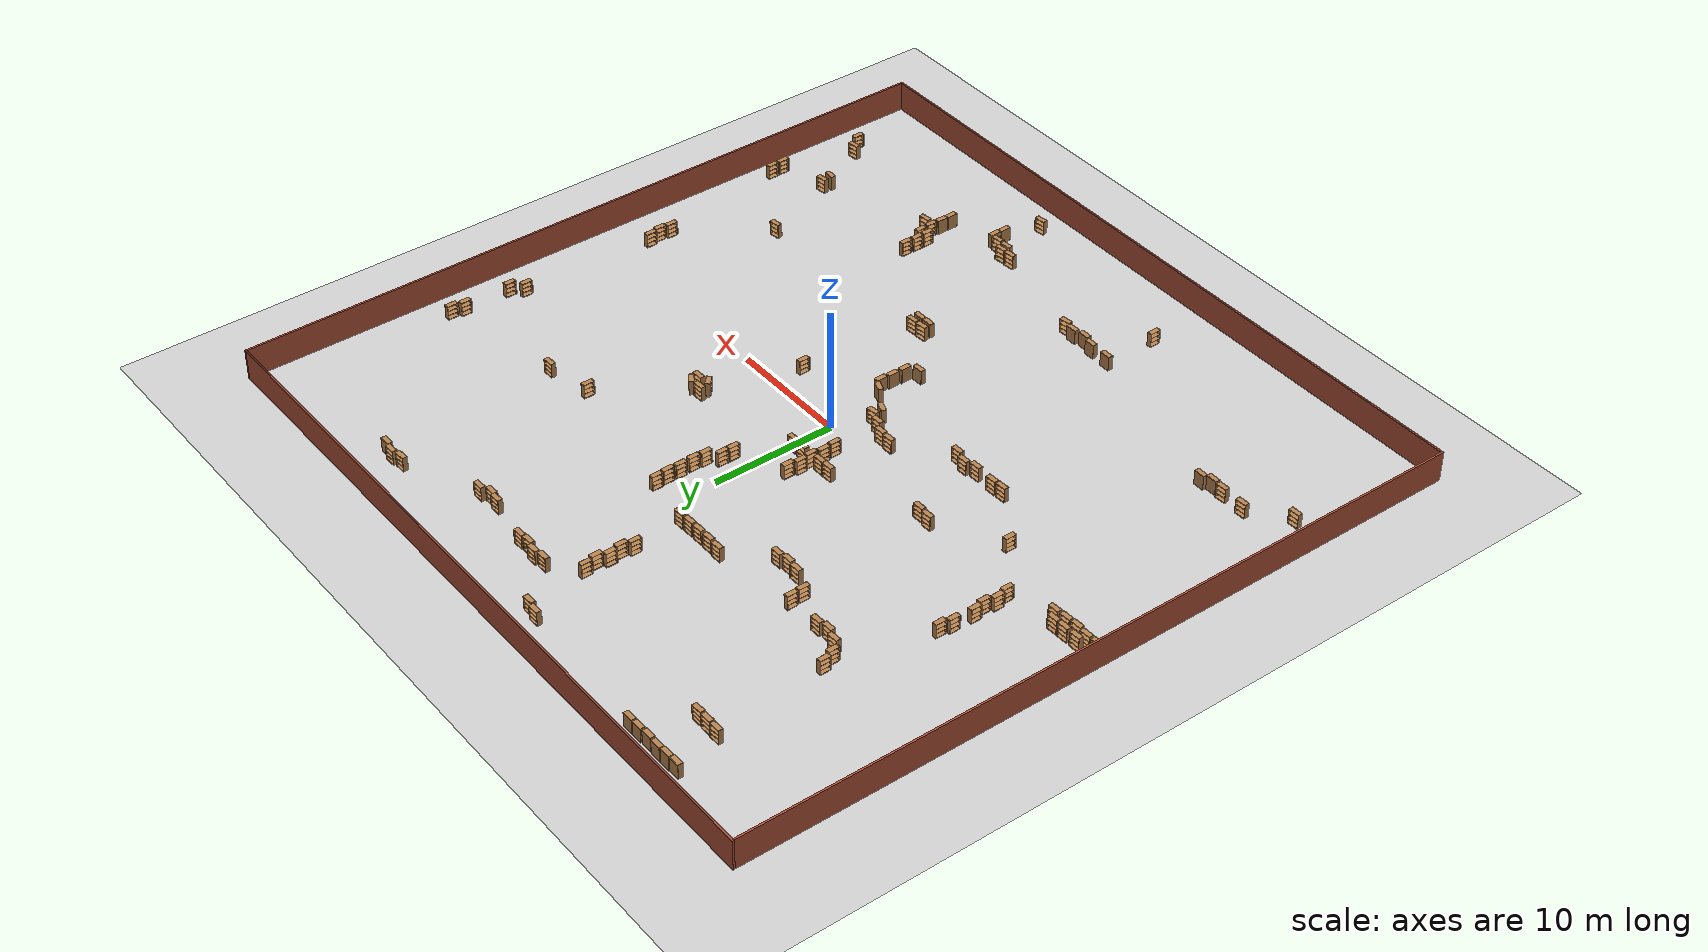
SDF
<sdf version="1.6">
 <world name="default">
  <light name="sun" type="directional">
   <pose>0 0 10 0 -0 0</pose>
   <diffuse>0.8 0.8 0.8 1</diffuse>
   <specular>0.2 0.2 0.2 1</specular>
   <attenuation>
    <range>1000</range>
    <constant>0.9</constant>
    <linear>0.01</linear>
    <quadratic>0.001</quadratic>
   </attenuation>
   <direction>-0.5 0.1 -0.9</direction>
  </light>
  <model name="ground_plane">
   <static>1</static>
   <link name="link">
    <collision name="collision">
     <geometry><plane><normal>0 0 1</normal><size>100 100</size></plane></geometry>
     <surface>
      <contact><collide_bitmask>65535</collide_bitmask></contact>
      <friction><ode><mu>100</mu><mu2>50</mu2></ode></friction>
     </surface>
    </collision>
    <visual name="visual">
     <cast_shadows>0</cast_shadows>
     <geometry><plane><normal>0 0 1</normal><size>100 100</size></plane></geometry>
     <material>
      <script><uri>file://media/materials/scripts/gazebo.material</uri><name>Gazebo/Grey</name></script>
     </material>
    </visual>
   </link>
  </model>
  <gravity>0 0 -9.8</gravity>
  <magnetic_field>6e-06 2.3e-05 -4.2e-05</magnetic_field>
  <atmosphere type="adiabatic"/>
  <physics name="default_physics" default="0" type="ode">
   <max_step_size>0.001</max_step_size>
   <real_time_factor>1</real_time_factor>
   <real_time_update_rate>1000</real_time_update_rate>
  </physics>
  <scene><ambient>0.4 0.4 0.4 1</ambient><background>0.7 0.7 0.7 1</background><shadows>1</shadows></scene>
  <spherical_coordinates>
   <surface_model>EARTH_WGS84</surface_model>
   <latitude_deg>0</latitude_deg>
   <longitude_deg>0</longitude_deg>
   <elevation>0</elevation>
   <heading_deg>0</heading_deg>
  </spherical_coordinates>
  <model name="30x30env"><static>1</static><pose>32.1206 3.39752 0 0 -0 0</pose></model>
  <audio><device>default</device></audio>
  <model name="wall_60">
   <link name="Wall_0">
    <collision name="Wall_0_Collision">
     <geometry><box><size>60.15 0.15 2.5</size></box></geometry>
     <pose>0 0 1.25 0 -0 0</pose>
    </collision>
    <visual name="Wall_0_Visual">
     <pose>0 0 1.25 0 -0 0</pose>
     <geometry><box><size>60.15 0.15 2.5</size></box></geometry>
     <material>
      <script><uri>file://media/materials/scripts/gazebo.material</uri><name>Gazebo/Bricks</name></script>
      <ambient>1 1 1 1</ambient>
     </material>
     <meta><layer>0</layer></meta>
    </visual>
    <pose>0 30 0 0 -0 3.14159</pose>
   </link>
   <link name="Wall_2">
    <collision name="Wall_2_Collision">
     <geometry><box><size>60.15 0.15 2.5</size></box></geometry>
     <pose>0 0 1.25 0 -0 0</pose>
    </collision>
    <visual name="Wall_2_Visual">
     <pose>0 0 1.25 0 -0 0</pose>
     <geometry><box><size>60.15 0.15 2.5</size></box></geometry>
     <material>
      <script><uri>file://media/materials/scripts/gazebo.material</uri><name>Gazebo/Bricks</name></script>
      <ambient>1 1 1 1</ambient>
     </material>
     <meta><layer>0</layer></meta>
    </visual>
    <pose>-30 0 0 0 -0 -1.5708</pose>
   </link>
   <link name="Wall_4">
    <collision name="Wall_4_Collision">
     <geometry><box><size>60.15 0.15 2.5</size></box></geometry>
     <pose>0 0 1.25 0 -0 0</pose>
    </collision>
    <visual name="Wall_4_Visual">
     <pose>0 0 1.25 0 -0 0</pose>
     <geometry><box><size>60.15 0.15 2.5</size></box></geometry>
     <material>
      <script><uri>file://media/materials/scripts/gazebo.material</uri><name>Gazebo/Bricks</name></script>
      <ambient>1 1 1 1</ambient>
     </material>
     <meta><layer>0</layer></meta>
    </visual>
    <pose>0 -30 0 0 -0 0</pose>
   </link>
   <link name="Wall_6">
    <collision name="Wall_6_Collision">
     <geometry><box><size>60.15 0.15 2.5</size></box></geometry>
     <pose>0 0 1.25 0 -0 0</pose>
    </collision>
    <visual name="Wall_6_Visual">
     <pose>0 0 1.25 0 -0 0</pose>
     <geometry><box><size>60.15 0.15 2.5</size></box></geometry>
     <material>
      <script><uri>file://media/materials/scripts/gazebo.material</uri><name>Gazebo/Bricks</name></script>
      <ambient>1 1 1 1</ambient>
     </material>
     <meta><layer>0</layer></meta>
    </visual>
    <pose>30 0 0 0 -0 -1.5708</pose>
   </link>
   <static>1</static>
  </model>
  <model name="bookshelf_clone">
   <static>1</static>
   <link name="link">
    <inertial><mass>1</mass></inertial>
    <collision name="back">
     <pose>0 0.005 0.6 0 -0 0</pose>
     <geometry><box><size>0.9 0.01 1.2</size></box></geometry>
    </collision>
    <visual name="visual1">
     <pose>0 0.005 0.6 0 -0 0</pose>
     <geometry><box><size>0.9 0.01 1.2</size></box></geometry>
     <material>
      <script><uri>file://media/materials/scripts/gazebo.material</uri><name>Gazebo/Wood</name></script>
     </material>
    </visual>
    <collision name="left_side">
     <pose>0.45 -0.195 0.6 0 -0 0</pose>
     <geometry><box><size>0.02 0.4 1.2</size></box></geometry>
    </collision>
    <visual name="visual2">
     <pose>0.45 -0.195 0.6 0 -0 0</pose>
     <geometry><box><size>0.02 0.4 1.2</size></box></geometry>
     <material>
      <script><uri>file://media/materials/scripts/gazebo.material</uri><name>Gazebo/Wood</name></script>
     </material>
    </visual>
    <collision name="right_side">
     <pose>-0.45 -0.195 0.6 0 -0 0</pose>
     <geometry><box><size>0.02 0.4 1.2</size></box></geometry>
    </collision>
    <visual name="visual3">
     <pose>-0.45 -0.195 0.6 0 -0 0</pose>
     <geometry><box><size>0.02 0.4 1.2</size></box></geometry>
     <material>
      <script><uri>file://media/materials/scripts/gazebo.material</uri><name>Gazebo/Wood</name></script>
     </material>
    </visual>
    <collision name="bottom">
     <pose>0 -0.195 0.03 0 -0 0</pose>
     <geometry><box><size>0.88 0.4 0.06</size></box></geometry>
    </collision>
    <visual name="visual4">
     <pose>0 -0.195 0.03 0 -0 0</pose>
     <geometry><box><size>0.88 0.4 0.06</size></box></geometry>
     <material>
      <script><uri>file://media/materials/scripts/gazebo.material</uri><name>Gazebo/Wood</name></script>
     </material>
    </visual>
    <collision name="top">
     <pose>0 -0.195 1.19 0 -0 0</pose>
     <geometry><box><size>0.88 0.4 0.02</size></box></geometry>
    </collision>
    <visual name="visual5">
     <pose>0 -0.195 1.19 0 -0 0</pose>
     <geometry><box><size>0.88 0.4 0.02</size></box></geometry>
     <material>
      <script><uri>file://media/materials/scripts/gazebo.material</uri><name>Gazebo/Wood</name></script>
     </material>
    </visual>
    <collision name="low_shelf">
     <pose>0 -0.195 0.43 0 -0 0</pose>
     <geometry><box><size>0.88 0.4 0.02</size></box></geometry>
    </collision>
    <visual name="visual6">
     <pose>0 -0.195 0.43 0 -0 0</pose>
     <geometry><box><size>0.88 0.4 0.02</size></box></geometry>
     <material>
      <script><uri>file://media/materials/scripts/gazebo.material</uri><name>Gazebo/Wood</name></script>
     </material>
    </visual>
    <collision name="high_shelf">
     <pose>0 -0.195 0.8 0 -0 0</pose>
     <geometry><box><size>0.88 0.4 0.02</size></box></geometry>
    </collision>
    <visual name="visual7">
     <pose>0 -0.195 0.8 0 -0 0</pose>
     <geometry><box><size>0.88 0.4 0.02</size></box></geometry>
     <material>
      <script><uri>file://media/materials/scripts/gazebo.material</uri><name>Gazebo/Wood</name></script>
     </material>
    </visual>
   </link>
   <pose>-18.5237 28.408 0 0 -0 0</pose>
  </model>
  <model name="bookshelf_clone_0">
   <static>1</static>
   <link name="link">
    <inertial><mass>1</mass></inertial>
    <collision name="back">
     <pose>0 0.005 0.6 0 -0 0</pose>
     <geometry><box><size>0.9 0.01 1.2</size></box></geometry>
    </collision>
    <visual name="visual1">
     <pose>0 0.005 0.6 0 -0 0</pose>
     <geometry><box><size>0.9 0.01 1.2</size></box></geometry>
     <material>
      <script><uri>file://media/materials/scripts/gazebo.material</uri><name>Gazebo/Wood</name></script>
     </material>
    </visual>
    <collision name="left_side">
     <pose>0.45 -0.195 0.6 0 -0 0</pose>
     <geometry><box><size>0.02 0.4 1.2</size></box></geometry>
    </collision>
    <visual name="visual2">
     <pose>0.45 -0.195 0.6 0 -0 0</pose>
     <geometry><box><size>0.02 0.4 1.2</size></box></geometry>
     <material>
      <script><uri>file://media/materials/scripts/gazebo.material</uri><name>Gazebo/Wood</name></script>
     </material>
    </visual>
    <collision name="right_side">
     <pose>-0.45 -0.195 0.6 0 -0 0</pose>
     <geometry><box><size>0.02 0.4 1.2</size></box></geometry>
    </collision>
    <visual name="visual3">
     <pose>-0.45 -0.195 0.6 0 -0 0</pose>
     <geometry><box><size>0.02 0.4 1.2</size></box></geometry>
     <material>
      <script><uri>file://media/materials/scripts/gazebo.material</uri><name>Gazebo/Wood</name></script>
     </material>
    </visual>
    <collision name="bottom">
     <pose>0 -0.195 0.03 0 -0 0</pose>
     <geometry><box><size>0.88 0.4 0.06</size></box></geometry>
    </collision>
    <visual name="visual4">
     <pose>0 -0.195 0.03 0 -0 0</pose>
     <geometry><box><size>0.88 0.4 0.06</size></box></geometry>
     <material>
      <script><uri>file://media/materials/scripts/gazebo.material</uri><name>Gazebo/Wood</name></script>
     </material>
    </visual>
    <collision name="top">
     <pose>0 -0.195 1.19 0 -0 0</pose>
     <geometry><box><size>0.88 0.4 0.02</size></box></geometry>
    </collision>
    <visual name="visual5">
     <pose>0 -0.195 1.19 0 -0 0</pose>
     <geometry><box><size>0.88 0.4 0.02</size></box></geometry>
     <material>
      <script><uri>file://media/materials/scripts/gazebo.material</uri><name>Gazebo/Wood</name></script>
     </material>
    </visual>
    <collision name="low_shelf">
     <pose>0 -0.195 0.43 0 -0 0</pose>
     <geometry><box><size>0.88 0.4 0.02</size></box></geometry>
    </collision>
    <visual name="visual6">
     <pose>0 -0.195 0.43 0 -0 0</pose>
     <geometry><box><size>0.88 0.4 0.02</size></box></geometry>
     <material>
      <script><uri>file://media/materials/scripts/gazebo.material</uri><name>Gazebo/Wood</name></script>
     </material>
    </visual>
    <collision name="high_shelf">
     <pose>0 -0.195 0.8 0 -0 0</pose>
     <geometry><box><size>0.88 0.4 0.02</size></box></geometry>
    </collision>
    <visual name="visual7">
     <pose>0 -0.195 0.8 0 -0 0</pose>
     <geometry><box><size>0.88 0.4 0.02</size></box></geometry>
     <material>
      <script><uri>file://media/materials/scripts/gazebo.material</uri><name>Gazebo/Wood</name></script>
     </material>
    </visual>
   </link>
   <pose>-19.5618 28.4514 0 0 -0 0</pose>
  </model>
  <model name="bookshelf_clone_1">
   <static>1</static>
   <link name="link">
    <inertial><mass>1</mass></inertial>
    <collision name="back">
     <pose>0 0.005 0.6 0 -0 0</pose>
     <geometry><box><size>0.9 0.01 1.2</size></box></geometry>
    </collision>
    <visual name="visual1">
     <pose>0 0.005 0.6 0 -0 0</pose>
     <geometry><box><size>0.9 0.01 1.2</size></box></geometry>
     <material>
      <script><uri>file://media/materials/scripts/gazebo.material</uri><name>Gazebo/Wood</name></script>
     </material>
    </visual>
    <collision name="left_side">
     <pose>0.45 -0.195 0.6 0 -0 0</pose>
     <geometry><box><size>0.02 0.4 1.2</size></box></geometry>
    </collision>
    <visual name="visual2">
     <pose>0.45 -0.195 0.6 0 -0 0</pose>
     <geometry><box><size>0.02 0.4 1.2</size></box></geometry>
     <material>
      <script><uri>file://media/materials/scripts/gazebo.material</uri><name>Gazebo/Wood</name></script>
     </material>
    </visual>
    <collision name="right_side">
     <pose>-0.45 -0.195 0.6 0 -0 0</pose>
     <geometry><box><size>0.02 0.4 1.2</size></box></geometry>
    </collision>
    <visual name="visual3">
     <pose>-0.45 -0.195 0.6 0 -0 0</pose>
     <geometry><box><size>0.02 0.4 1.2</size></box></geometry>
     <material>
      <script><uri>file://media/materials/scripts/gazebo.material</uri><name>Gazebo/Wood</name></script>
     </material>
    </visual>
    <collision name="bottom">
     <pose>0 -0.195 0.03 0 -0 0</pose>
     <geometry><box><size>0.88 0.4 0.06</size></box></geometry>
    </collision>
    <visual name="visual4">
     <pose>0 -0.195 0.03 0 -0 0</pose>
     <geometry><box><size>0.88 0.4 0.06</size></box></geometry>
     <material>
      <script><uri>file://media/materials/scripts/gazebo.material</uri><name>Gazebo/Wood</name></script>
     </material>
    </visual>
    <collision name="top">
     <pose>0 -0.195 1.19 0 -0 0</pose>
     <geometry><box><size>0.88 0.4 0.02</size></box></geometry>
    </collision>
    <visual name="visual5">
     <pose>0 -0.195 1.19 0 -0 0</pose>
     <geometry><box><size>0.88 0.4 0.02</size></box></geometry>
     <material>
      <script><uri>file://media/materials/scripts/gazebo.material</uri><name>Gazebo/Wood</name></script>
     </material>
    </visual>
    <collision name="low_shelf">
     <pose>0 -0.195 0.43 0 -0 0</pose>
     <geometry><box><size>0.88 0.4 0.02</size></box></geometry>
    </collision>
    <visual name="visual6">
     <pose>0 -0.195 0.43 0 -0 0</pose>
     <geometry><box><size>0.88 0.4 0.02</size></box></geometry>
     <material>
      <script><uri>file://media/materials/scripts/gazebo.material</uri><name>Gazebo/Wood</name></script>
     </material>
    </visual>
    <collision name="high_shelf">
     <pose>0 -0.195 0.8 0 -0 0</pose>
     <geometry><box><size>0.88 0.4 0.02</size></box></geometry>
    </collision>
    <visual name="visual7">
     <pose>0 -0.195 0.8 0 -0 0</pose>
     <geometry><box><size>0.88 0.4 0.02</size></box></geometry>
     <material>
      <script><uri>file://media/materials/scripts/gazebo.material</uri><name>Gazebo/Wood</name></script>
     </material>
    </visual>
   </link>
   <pose>-20.5209 28.4151 0 0 -0 0</pose>
  </model>
  <model name="bookshelf_clone_2">
   <static>1</static>
   <link name="link">
    <inertial><mass>1</mass></inertial>
    <collision name="back">
     <pose>0 0.005 0.6 0 -0 0</pose>
     <geometry><box><size>0.9 0.01 1.2</size></box></geometry>
    </collision>
    <visual name="visual1">
     <pose>0 0.005 0.6 0 -0 0</pose>
     <geometry><box><size>0.9 0.01 1.2</size></box></geometry>
     <material>
      <script><uri>file://media/materials/scripts/gazebo.material</uri><name>Gazebo/Wood</name></script>
     </material>
    </visual>
    <collision name="left_side">
     <pose>0.45 -0.195 0.6 0 -0 0</pose>
     <geometry><box><size>0.02 0.4 1.2</size></box></geometry>
    </collision>
    <visual name="visual2">
     <pose>0.45 -0.195 0.6 0 -0 0</pose>
     <geometry><box><size>0.02 0.4 1.2</size></box></geometry>
     <material>
      <script><uri>file://media/materials/scripts/gazebo.material</uri><name>Gazebo/Wood</name></script>
     </material>
    </visual>
    <collision name="right_side">
     <pose>-0.45 -0.195 0.6 0 -0 0</pose>
     <geometry><box><size>0.02 0.4 1.2</size></box></geometry>
    </collision>
    <visual name="visual3">
     <pose>-0.45 -0.195 0.6 0 -0 0</pose>
     <geometry><box><size>0.02 0.4 1.2</size></box></geometry>
     <material>
      <script><uri>file://media/materials/scripts/gazebo.material</uri><name>Gazebo/Wood</name></script>
     </material>
    </visual>
    <collision name="bottom">
     <pose>0 -0.195 0.03 0 -0 0</pose>
     <geometry><box><size>0.88 0.4 0.06</size></box></geometry>
    </collision>
    <visual name="visual4">
     <pose>0 -0.195 0.03 0 -0 0</pose>
     <geometry><box><size>0.88 0.4 0.06</size></box></geometry>
     <material>
      <script><uri>file://media/materials/scripts/gazebo.material</uri><name>Gazebo/Wood</name></script>
     </material>
    </visual>
    <collision name="top">
     <pose>0 -0.195 1.19 0 -0 0</pose>
     <geometry><box><size>0.88 0.4 0.02</size></box></geometry>
    </collision>
    <visual name="visual5">
     <pose>0 -0.195 1.19 0 -0 0</pose>
     <geometry><box><size>0.88 0.4 0.02</size></box></geometry>
     <material>
      <script><uri>file://media/materials/scripts/gazebo.material</uri><name>Gazebo/Wood</name></script>
     </material>
    </visual>
    <collision name="low_shelf">
     <pose>0 -0.195 0.43 0 -0 0</pose>
     <geometry><box><size>0.88 0.4 0.02</size></box></geometry>
    </collision>
    <visual name="visual6">
     <pose>0 -0.195 0.43 0 -0 0</pose>
     <geometry><box><size>0.88 0.4 0.02</size></box></geometry>
     <material>
      <script><uri>file://media/materials/scripts/gazebo.material</uri><name>Gazebo/Wood</name></script>
     </material>
    </visual>
    <collision name="high_shelf">
     <pose>0 -0.195 0.8 0 -0 0</pose>
     <geometry><box><size>0.88 0.4 0.02</size></box></geometry>
    </collision>
    <visual name="visual7">
     <pose>0 -0.195 0.8 0 -0 0</pose>
     <geometry><box><size>0.88 0.4 0.02</size></box></geometry>
     <material>
      <script><uri>file://media/materials/scripts/gazebo.material</uri><name>Gazebo/Wood</name></script>
     </material>
    </visual>
   </link>
   <pose>-21.4777 28.3729 0 0 -0 0</pose>
  </model>
  <model name="bookshelf_clone_2_clone">
   <static>1</static>
   <link name="link">
    <inertial><mass>1</mass></inertial>
    <collision name="back">
     <pose>0 0.005 0.6 0 -0 0</pose>
     <geometry><box><size>0.9 0.01 1.2</size></box></geometry>
    </collision>
    <visual name="visual1">
     <pose>0 0.005 0.6 0 -0 0</pose>
     <geometry><box><size>0.9 0.01 1.2</size></box></geometry>
     <material>
      <script><uri>file://media/materials/scripts/gazebo.material</uri><name>Gazebo/Wood</name></script>
     </material>
    </visual>
    <collision name="left_side">
     <pose>0.45 -0.195 0.6 0 -0 0</pose>
     <geometry><box><size>0.02 0.4 1.2</size></box></geometry>
    </collision>
    <visual name="visual2">
     <pose>0.45 -0.195 0.6 0 -0 0</pose>
     <geometry><box><size>0.02 0.4 1.2</size></box></geometry>
     <material>
      <script><uri>file://media/materials/scripts/gazebo.material</uri><name>Gazebo/Wood</name></script>
     </material>
    </visual>
    <collision name="right_side">
     <pose>-0.45 -0.195 0.6 0 -0 0</pose>
     <geometry><box><size>0.02 0.4 1.2</size></box></geometry>
    </collision>
    <visual name="visual3">
     <pose>-0.45 -0.195 0.6 0 -0 0</pose>
     <geometry><box><size>0.02 0.4 1.2</size></box></geometry>
     <material>
      <script><uri>file://media/materials/scripts/gazebo.material</uri><name>Gazebo/Wood</name></script>
     </material>
    </visual>
    <collision name="bottom">
     <pose>0 -0.195 0.03 0 -0 0</pose>
     <geometry><box><size>0.88 0.4 0.06</size></box></geometry>
    </collision>
    <visual name="visual4">
     <pose>0 -0.195 0.03 0 -0 0</pose>
     <geometry><box><size>0.88 0.4 0.06</size></box></geometry>
     <material>
      <script><uri>file://media/materials/scripts/gazebo.material</uri><name>Gazebo/Wood</name></script>
     </material>
    </visual>
    <collision name="top">
     <pose>0 -0.195 1.19 0 -0 0</pose>
     <geometry><box><size>0.88 0.4 0.02</size></box></geometry>
    </collision>
    <visual name="visual5">
     <pose>0 -0.195 1.19 0 -0 0</pose>
     <geometry><box><size>0.88 0.4 0.02</size></box></geometry>
     <material>
      <script><uri>file://media/materials/scripts/gazebo.material</uri><name>Gazebo/Wood</name></script>
     </material>
    </visual>
    <collision name="low_shelf">
     <pose>0 -0.195 0.43 0 -0 0</pose>
     <geometry><box><size>0.88 0.4 0.02</size></box></geometry>
    </collision>
    <visual name="visual6">
     <pose>0 -0.195 0.43 0 -0 0</pose>
     <geometry><box><size>0.88 0.4 0.02</size></box></geometry>
     <material>
      <script><uri>file://media/materials/scripts/gazebo.material</uri><name>Gazebo/Wood</name></script>
     </material>
    </visual>
    <collision name="high_shelf">
     <pose>0 -0.195 0.8 0 -0 0</pose>
     <geometry><box><size>0.88 0.4 0.02</size></box></geometry>
    </collision>
    <visual name="visual7">
     <pose>0 -0.195 0.8 0 -0 0</pose>
     <geometry><box><size>0.88 0.4 0.02</size></box></geometry>
     <material>
      <script><uri>file://media/materials/scripts/gazebo.material</uri><name>Gazebo/Wood</name></script>
     </material>
    </visual>
   </link>
   <pose>-20.542 24.2966 0 0 0 -3.10717</pose>
  </model>
  <model name="bookshelf_clone_2_clone_clone">
   <static>1</static>
   <link name="link">
    <inertial><mass>1</mass></inertial>
    <collision name="back">
     <pose>0 0.005 0.6 0 -0 0</pose>
     <geometry><box><size>0.9 0.01 1.2</size></box></geometry>
    </collision>
    <visual name="visual1">
     <pose>0 0.005 0.6 0 -0 0</pose>
     <geometry><box><size>0.9 0.01 1.2</size></box></geometry>
     <material>
      <script><uri>file://media/materials/scripts/gazebo.material</uri><name>Gazebo/Wood</name></script>
     </material>
    </visual>
    <collision name="left_side">
     <pose>0.45 -0.195 0.6 0 -0 0</pose>
     <geometry><box><size>0.02 0.4 1.2</size></box></geometry>
    </collision>
    <visual name="visual2">
     <pose>0.45 -0.195 0.6 0 -0 0</pose>
     <geometry><box><size>0.02 0.4 1.2</size></box></geometry>
     <material>
      <script><uri>file://media/materials/scripts/gazebo.material</uri><name>Gazebo/Wood</name></script>
     </material>
    </visual>
    <collision name="right_side">
     <pose>-0.45 -0.195 0.6 0 -0 0</pose>
     <geometry><box><size>0.02 0.4 1.2</size></box></geometry>
    </collision>
    <visual name="visual3">
     <pose>-0.45 -0.195 0.6 0 -0 0</pose>
     <geometry><box><size>0.02 0.4 1.2</size></box></geometry>
     <material>
      <script><uri>file://media/materials/scripts/gazebo.material</uri><name>Gazebo/Wood</name></script>
     </material>
    </visual>
    <collision name="bottom">
     <pose>0 -0.195 0.03 0 -0 0</pose>
     <geometry><box><size>0.88 0.4 0.06</size></box></geometry>
    </collision>
    <visual name="visual4">
     <pose>0 -0.195 0.03 0 -0 0</pose>
     <geometry><box><size>0.88 0.4 0.06</size></box></geometry>
     <material>
      <script><uri>file://media/materials/scripts/gazebo.material</uri><name>Gazebo/Wood</name></script>
     </material>
    </visual>
    <collision name="top">
     <pose>0 -0.195 1.19 0 -0 0</pose>
     <geometry><box><size>0.88 0.4 0.02</size></box></geometry>
    </collision>
    <visual name="visual5">
     <pose>0 -0.195 1.19 0 -0 0</pose>
     <geometry><box><size>0.88 0.4 0.02</size></box></geometry>
     <material>
      <script><uri>file://media/materials/scripts/gazebo.material</uri><name>Gazebo/Wood</name></script>
     </material>
    </visual>
    <collision name="low_shelf">
     <pose>0 -0.195 0.43 0 -0 0</pose>
     <geometry><box><size>0.88 0.4 0.02</size></box></geometry>
    </collision>
    <visual name="visual6">
     <pose>0 -0.195 0.43 0 -0 0</pose>
     <geometry><box><size>0.88 0.4 0.02</size></box></geometry>
     <material>
      <script><uri>file://media/materials/scripts/gazebo.material</uri><name>Gazebo/Wood</name></script>
     </material>
    </visual>
    <collision name="high_shelf">
     <pose>0 -0.195 0.8 0 -0 0</pose>
     <geometry><box><size>0.88 0.4 0.02</size></box></geometry>
    </collision>
    <visual name="visual7">
     <pose>0 -0.195 0.8 0 -0 0</pose>
     <geometry><box><size>0.88 0.4 0.02</size></box></geometry>
     <material>
      <script><uri>file://media/materials/scripts/gazebo.material</uri><name>Gazebo/Wood</name></script>
     </material>
    </visual>
   </link>
   <pose>-19.5517 24.2685 0 0 0 -3.10717</pose>
  </model>
  <model name="bookshelf_clone_2_clone_clone_0">
   <static>1</static>
   <link name="link">
    <inertial><mass>1</mass></inertial>
    <collision name="back">
     <pose>0 0.005 0.6 0 -0 0</pose>
     <geometry><box><size>0.9 0.01 1.2</size></box></geometry>
    </collision>
    <visual name="visual1">
     <pose>0 0.005 0.6 0 -0 0</pose>
     <geometry><box><size>0.9 0.01 1.2</size></box></geometry>
     <material>
      <script><uri>file://media/materials/scripts/gazebo.material</uri><name>Gazebo/Wood</name></script>
     </material>
    </visual>
    <collision name="left_side">
     <pose>0.45 -0.195 0.6 0 -0 0</pose>
     <geometry><box><size>0.02 0.4 1.2</size></box></geometry>
    </collision>
    <visual name="visual2">
     <pose>0.45 -0.195 0.6 0 -0 0</pose>
     <geometry><box><size>0.02 0.4 1.2</size></box></geometry>
     <material>
      <script><uri>file://media/materials/scripts/gazebo.material</uri><name>Gazebo/Wood</name></script>
     </material>
    </visual>
    <collision name="right_side">
     <pose>-0.45 -0.195 0.6 0 -0 0</pose>
     <geometry><box><size>0.02 0.4 1.2</size></box></geometry>
    </collision>
    <visual name="visual3">
     <pose>-0.45 -0.195 0.6 0 -0 0</pose>
     <geometry><box><size>0.02 0.4 1.2</size></box></geometry>
     <material>
      <script><uri>file://media/materials/scripts/gazebo.material</uri><name>Gazebo/Wood</name></script>
     </material>
    </visual>
    <collision name="bottom">
     <pose>0 -0.195 0.03 0 -0 0</pose>
     <geometry><box><size>0.88 0.4 0.06</size></box></geometry>
    </collision>
    <visual name="visual4">
     <pose>0 -0.195 0.03 0 -0 0</pose>
     <geometry><box><size>0.88 0.4 0.06</size></box></geometry>
     <material>
      <script><uri>file://media/materials/scripts/gazebo.material</uri><name>Gazebo/Wood</name></script>
     </material>
    </visual>
    <collision name="top">
     <pose>0 -0.195 1.19 0 -0 0</pose>
     <geometry><box><size>0.88 0.4 0.02</size></box></geometry>
    </collision>
    <visual name="visual5">
     <pose>0 -0.195 1.19 0 -0 0</pose>
     <geometry><box><size>0.88 0.4 0.02</size></box></geometry>
     <material>
      <script><uri>file://media/materials/scripts/gazebo.material</uri><name>Gazebo/Wood</name></script>
     </material>
    </visual>
    <collision name="low_shelf">
     <pose>0 -0.195 0.43 0 -0 0</pose>
     <geometry><box><size>0.88 0.4 0.02</size></box></geometry>
    </collision>
    <visual name="visual6">
     <pose>0 -0.195 0.43 0 -0 0</pose>
     <geometry><box><size>0.88 0.4 0.02</size></box></geometry>
     <material>
      <script><uri>file://media/materials/scripts/gazebo.material</uri><name>Gazebo/Wood</name></script>
     </material>
    </visual>
    <collision name="high_shelf">
     <pose>0 -0.195 0.8 0 -0 0</pose>
     <geometry><box><size>0.88 0.4 0.02</size></box></geometry>
    </collision>
    <visual name="visual7">
     <pose>0 -0.195 0.8 0 -0 0</pose>
     <geometry><box><size>0.88 0.4 0.02</size></box></geometry>
     <material>
      <script><uri>file://media/materials/scripts/gazebo.material</uri><name>Gazebo/Wood</name></script>
     </material>
    </visual>
   </link>
   <pose>-18.5314 24.2403 0 0 0 -3.10717</pose>
  </model>
  <model name="bookshelf_clone_2_clone_clone_0_clone">
   <static>1</static>
   <link name="link">
    <inertial><mass>1</mass></inertial>
    <collision name="back">
     <pose>0 0.005 0.6 0 -0 0</pose>
     <geometry><box><size>0.9 0.01 1.2</size></box></geometry>
    </collision>
    <visual name="visual1">
     <pose>0 0.005 0.6 0 -0 0</pose>
     <geometry><box><size>0.9 0.01 1.2</size></box></geometry>
     <material>
      <script><uri>file://media/materials/scripts/gazebo.material</uri><name>Gazebo/Wood</name></script>
     </material>
    </visual>
    <collision name="left_side">
     <pose>0.45 -0.195 0.6 0 -0 0</pose>
     <geometry><box><size>0.02 0.4 1.2</size></box></geometry>
    </collision>
    <visual name="visual2">
     <pose>0.45 -0.195 0.6 0 -0 0</pose>
     <geometry><box><size>0.02 0.4 1.2</size></box></geometry>
     <material>
      <script><uri>file://media/materials/scripts/gazebo.material</uri><name>Gazebo/Wood</name></script>
     </material>
    </visual>
    <collision name="right_side">
     <pose>-0.45 -0.195 0.6 0 -0 0</pose>
     <geometry><box><size>0.02 0.4 1.2</size></box></geometry>
    </collision>
    <visual name="visual3">
     <pose>-0.45 -0.195 0.6 0 -0 0</pose>
     <geometry><box><size>0.02 0.4 1.2</size></box></geometry>
     <material>
      <script><uri>file://media/materials/scripts/gazebo.material</uri><name>Gazebo/Wood</name></script>
     </material>
    </visual>
    <collision name="bottom">
     <pose>0 -0.195 0.03 0 -0 0</pose>
     <geometry><box><size>0.88 0.4 0.06</size></box></geometry>
    </collision>
    <visual name="visual4">
     <pose>0 -0.195 0.03 0 -0 0</pose>
     <geometry><box><size>0.88 0.4 0.06</size></box></geometry>
     <material>
      <script><uri>file://media/materials/scripts/gazebo.material</uri><name>Gazebo/Wood</name></script>
     </material>
    </visual>
    <collision name="top">
     <pose>0 -0.195 1.19 0 -0 0</pose>
     <geometry><box><size>0.88 0.4 0.02</size></box></geometry>
    </collision>
    <visual name="visual5">
     <pose>0 -0.195 1.19 0 -0 0</pose>
     <geometry><box><size>0.88 0.4 0.02</size></box></geometry>
     <material>
      <script><uri>file://media/materials/scripts/gazebo.material</uri><name>Gazebo/Wood</name></script>
     </material>
    </visual>
    <collision name="low_shelf">
     <pose>0 -0.195 0.43 0 -0 0</pose>
     <geometry><box><size>0.88 0.4 0.02</size></box></geometry>
    </collision>
    <visual name="visual6">
     <pose>0 -0.195 0.43 0 -0 0</pose>
     <geometry><box><size>0.88 0.4 0.02</size></box></geometry>
     <material>
      <script><uri>file://media/materials/scripts/gazebo.material</uri><name>Gazebo/Wood</name></script>
     </material>
    </visual>
    <collision name="high_shelf">
     <pose>0 -0.195 0.8 0 -0 0</pose>
     <geometry><box><size>0.88 0.4 0.02</size></box></geometry>
    </collision>
    <visual name="visual7">
     <pose>0 -0.195 0.8 0 -0 0</pose>
     <geometry><box><size>0.88 0.4 0.02</size></box></geometry>
     <material>
      <script><uri>file://media/materials/scripts/gazebo.material</uri><name>Gazebo/Wood</name></script>
     </material>
    </visual>
   </link>
   <pose>-16.4166 13.3547 0 0 0 -3.10717</pose>
  </model>
  <model name="bookshelf_clone_2_clone_clone_0_clone_0">
   <static>1</static>
   <link name="link">
    <inertial><mass>1</mass></inertial>
    <collision name="back">
     <pose>0 0.005 0.6 0 -0 0</pose>
     <geometry><box><size>0.9 0.01 1.2</size></box></geometry>
    </collision>
    <visual name="visual1">
     <pose>0 0.005 0.6 0 -0 0</pose>
     <geometry><box><size>0.9 0.01 1.2</size></box></geometry>
     <material>
      <script><uri>file://media/materials/scripts/gazebo.material</uri><name>Gazebo/Wood</name></script>
     </material>
    </visual>
    <collision name="left_side">
     <pose>0.45 -0.195 0.6 0 -0 0</pose>
     <geometry><box><size>0.02 0.4 1.2</size></box></geometry>
    </collision>
    <visual name="visual2">
     <pose>0.45 -0.195 0.6 0 -0 0</pose>
     <geometry><box><size>0.02 0.4 1.2</size></box></geometry>
     <material>
      <script><uri>file://media/materials/scripts/gazebo.material</uri><name>Gazebo/Wood</name></script>
     </material>
    </visual>
    <collision name="right_side">
     <pose>-0.45 -0.195 0.6 0 -0 0</pose>
     <geometry><box><size>0.02 0.4 1.2</size></box></geometry>
    </collision>
    <visual name="visual3">
     <pose>-0.45 -0.195 0.6 0 -0 0</pose>
     <geometry><box><size>0.02 0.4 1.2</size></box></geometry>
     <material>
      <script><uri>file://media/materials/scripts/gazebo.material</uri><name>Gazebo/Wood</name></script>
     </material>
    </visual>
    <collision name="bottom">
     <pose>0 -0.195 0.03 0 -0 0</pose>
     <geometry><box><size>0.88 0.4 0.06</size></box></geometry>
    </collision>
    <visual name="visual4">
     <pose>0 -0.195 0.03 0 -0 0</pose>
     <geometry><box><size>0.88 0.4 0.06</size></box></geometry>
     <material>
      <script><uri>file://media/materials/scripts/gazebo.material</uri><name>Gazebo/Wood</name></script>
     </material>
    </visual>
    <collision name="top">
     <pose>0 -0.195 1.19 0 -0 0</pose>
     <geometry><box><size>0.88 0.4 0.02</size></box></geometry>
    </collision>
    <visual name="visual5">
     <pose>0 -0.195 1.19 0 -0 0</pose>
     <geometry><box><size>0.88 0.4 0.02</size></box></geometry>
     <material>
      <script><uri>file://media/materials/scripts/gazebo.material</uri><name>Gazebo/Wood</name></script>
     </material>
    </visual>
    <collision name="low_shelf">
     <pose>0 -0.195 0.43 0 -0 0</pose>
     <geometry><box><size>0.88 0.4 0.02</size></box></geometry>
    </collision>
    <visual name="visual6">
     <pose>0 -0.195 0.43 0 -0 0</pose>
     <geometry><box><size>0.88 0.4 0.02</size></box></geometry>
     <material>
      <script><uri>file://media/materials/scripts/gazebo.material</uri><name>Gazebo/Wood</name></script>
     </material>
    </visual>
    <collision name="high_shelf">
     <pose>0 -0.195 0.8 0 -0 0</pose>
     <geometry><box><size>0.88 0.4 0.02</size></box></geometry>
    </collision>
    <visual name="visual7">
     <pose>0 -0.195 0.8 0 -0 0</pose>
     <geometry><box><size>0.88 0.4 0.02</size></box></geometry>
     <material>
      <script><uri>file://media/materials/scripts/gazebo.material</uri><name>Gazebo/Wood</name></script>
     </material>
    </visual>
   </link>
   <pose>-17.438 13.1799 0 0 0 -3.10717</pose>
  </model>
  <model name="bookshelf_clone_2_clone_clone_0_clone_1">
   <static>1</static>
   <link name="link">
    <inertial><mass>1</mass></inertial>
    <collision name="back">
     <pose>0 0.005 0.6 0 -0 0</pose>
     <geometry><box><size>0.9 0.01 1.2</size></box></geometry>
    </collision>
    <visual name="visual1">
     <pose>0 0.005 0.6 0 -0 0</pose>
     <geometry><box><size>0.9 0.01 1.2</size></box></geometry>
     <material>
      <script><uri>file://media/materials/scripts/gazebo.material</uri><name>Gazebo/Wood</name></script>
     </material>
    </visual>
    <collision name="left_side">
     <pose>0.45 -0.195 0.6 0 -0 0</pose>
     <geometry><box><size>0.02 0.4 1.2</size></box></geometry>
    </collision>
    <visual name="visual2">
     <pose>0.45 -0.195 0.6 0 -0 0</pose>
     <geometry><box><size>0.02 0.4 1.2</size></box></geometry>
     <material>
      <script><uri>file://media/materials/scripts/gazebo.material</uri><name>Gazebo/Wood</name></script>
     </material>
    </visual>
    <collision name="right_side">
     <pose>-0.45 -0.195 0.6 0 -0 0</pose>
     <geometry><box><size>0.02 0.4 1.2</size></box></geometry>
    </collision>
    <visual name="visual3">
     <pose>-0.45 -0.195 0.6 0 -0 0</pose>
     <geometry><box><size>0.02 0.4 1.2</size></box></geometry>
     <material>
      <script><uri>file://media/materials/scripts/gazebo.material</uri><name>Gazebo/Wood</name></script>
     </material>
    </visual>
    <collision name="bottom">
     <pose>0 -0.195 0.03 0 -0 0</pose>
     <geometry><box><size>0.88 0.4 0.06</size></box></geometry>
    </collision>
    <visual name="visual4">
     <pose>0 -0.195 0.03 0 -0 0</pose>
     <geometry><box><size>0.88 0.4 0.06</size></box></geometry>
     <material>
      <script><uri>file://media/materials/scripts/gazebo.material</uri><name>Gazebo/Wood</name></script>
     </material>
    </visual>
    <collision name="top">
     <pose>0 -0.195 1.19 0 -0 0</pose>
     <geometry><box><size>0.88 0.4 0.02</size></box></geometry>
    </collision>
    <visual name="visual5">
     <pose>0 -0.195 1.19 0 -0 0</pose>
     <geometry><box><size>0.88 0.4 0.02</size></box></geometry>
     <material>
      <script><uri>file://media/materials/scripts/gazebo.material</uri><name>Gazebo/Wood</name></script>
     </material>
    </visual>
    <collision name="low_shelf">
     <pose>0 -0.195 0.43 0 -0 0</pose>
     <geometry><box><size>0.88 0.4 0.02</size></box></geometry>
    </collision>
    <visual name="visual6">
     <pose>0 -0.195 0.43 0 -0 0</pose>
     <geometry><box><size>0.88 0.4 0.02</size></box></geometry>
     <material>
      <script><uri>file://media/materials/scripts/gazebo.material</uri><name>Gazebo/Wood</name></script>
     </material>
    </visual>
    <collision name="high_shelf">
     <pose>0 -0.195 0.8 0 -0 0</pose>
     <geometry><box><size>0.88 0.4 0.02</size></box></geometry>
    </collision>
    <visual name="visual7">
     <pose>0 -0.195 0.8 0 -0 0</pose>
     <geometry><box><size>0.88 0.4 0.02</size></box></geometry>
     <material>
      <script><uri>file://media/materials/scripts/gazebo.material</uri><name>Gazebo/Wood</name></script>
     </material>
    </visual>
   </link>
   <pose>-18.4447 13.5241 0 0 0 -3.10717</pose>
  </model>
  <model name="bookshelf_clone_2_clone_clone_0_clone_3_clone">
   <static>1</static>
   <link name="link">
    <inertial><mass>1</mass></inertial>
    <collision name="back">
     <pose>0 0.005 0.6 0 -0 0</pose>
     <geometry><box><size>0.9 0.01 1.2</size></box></geometry>
    </collision>
    <visual name="visual1">
     <pose>0 0.005 0.6 0 -0 0</pose>
     <geometry><box><size>0.9 0.01 1.2</size></box></geometry>
     <material>
      <script><uri>file://media/materials/scripts/gazebo.material</uri><name>Gazebo/Wood</name></script>
     </material>
    </visual>
    <collision name="left_side">
     <pose>0.45 -0.195 0.6 0 -0 0</pose>
     <geometry><box><size>0.02 0.4 1.2</size></box></geometry>
    </collision>
    <visual name="visual2">
     <pose>0.45 -0.195 0.6 0 -0 0</pose>
     <geometry><box><size>0.02 0.4 1.2</size></box></geometry>
     <material>
      <script><uri>file://media/materials/scripts/gazebo.material</uri><name>Gazebo/Wood</name></script>
     </material>
    </visual>
    <collision name="right_side">
     <pose>-0.45 -0.195 0.6 0 -0 0</pose>
     <geometry><box><size>0.02 0.4 1.2</size></box></geometry>
    </collision>
    <visual name="visual3">
     <pose>-0.45 -0.195 0.6 0 -0 0</pose>
     <geometry><box><size>0.02 0.4 1.2</size></box></geometry>
     <material>
      <script><uri>file://media/materials/scripts/gazebo.material</uri><name>Gazebo/Wood</name></script>
     </material>
    </visual>
    <collision name="bottom">
     <pose>0 -0.195 0.03 0 -0 0</pose>
     <geometry><box><size>0.88 0.4 0.06</size></box></geometry>
    </collision>
    <visual name="visual4">
     <pose>0 -0.195 0.03 0 -0 0</pose>
     <geometry><box><size>0.88 0.4 0.06</size></box></geometry>
     <material>
      <script><uri>file://media/materials/scripts/gazebo.material</uri><name>Gazebo/Wood</name></script>
     </material>
    </visual>
    <collision name="top">
     <pose>0 -0.195 1.19 0 -0 0</pose>
     <geometry><box><size>0.88 0.4 0.02</size></box></geometry>
    </collision>
    <visual name="visual5">
     <pose>0 -0.195 1.19 0 -0 0</pose>
     <geometry><box><size>0.88 0.4 0.02</size></box></geometry>
     <material>
      <script><uri>file://media/materials/scripts/gazebo.material</uri><name>Gazebo/Wood</name></script>
     </material>
    </visual>
    <collision name="low_shelf">
     <pose>0 -0.195 0.43 0 -0 0</pose>
     <geometry><box><size>0.88 0.4 0.02</size></box></geometry>
    </collision>
    <visual name="visual6">
     <pose>0 -0.195 0.43 0 -0 0</pose>
     <geometry><box><size>0.88 0.4 0.02</size></box></geometry>
     <material>
      <script><uri>file://media/materials/scripts/gazebo.material</uri><name>Gazebo/Wood</name></script>
     </material>
    </visual>
    <collision name="high_shelf">
     <pose>0 -0.195 0.8 0 -0 0</pose>
     <geometry><box><size>0.88 0.4 0.02</size></box></geometry>
    </collision>
    <visual name="visual7">
     <pose>0 -0.195 0.8 0 -0 0</pose>
     <geometry><box><size>0.88 0.4 0.02</size></box></geometry>
     <material>
      <script><uri>file://media/materials/scripts/gazebo.material</uri><name>Gazebo/Wood</name></script>
     </material>
    </visual>
   </link>
   <pose>-0.402698 3.38465 0 0 0 -3.10717</pose>
  </model>
  <model name="bookshelf_clone_2_clone_clone_0_clone_3_clone_0">
   <static>1</static>
   <link name="link">
    <inertial><mass>1</mass></inertial>
    <collision name="back">
     <pose>0 0.005 0.6 0 -0 0</pose>
     <geometry><box><size>0.9 0.01 1.2</size></box></geometry>
    </collision>
    <visual name="visual1">
     <pose>0 0.005 0.6 0 -0 0</pose>
     <geometry><box><size>0.9 0.01 1.2</size></box></geometry>
     <material>
      <script><uri>file://media/materials/scripts/gazebo.material</uri><name>Gazebo/Wood</name></script>
     </material>
    </visual>
    <collision name="left_side">
     <pose>0.45 -0.195 0.6 0 -0 0</pose>
     <geometry><box><size>0.02 0.4 1.2</size></box></geometry>
    </collision>
    <visual name="visual2">
     <pose>0.45 -0.195 0.6 0 -0 0</pose>
     <geometry><box><size>0.02 0.4 1.2</size></box></geometry>
     <material>
      <script><uri>file://media/materials/scripts/gazebo.material</uri><name>Gazebo/Wood</name></script>
     </material>
    </visual>
    <collision name="right_side">
     <pose>-0.45 -0.195 0.6 0 -0 0</pose>
     <geometry><box><size>0.02 0.4 1.2</size></box></geometry>
    </collision>
    <visual name="visual3">
     <pose>-0.45 -0.195 0.6 0 -0 0</pose>
     <geometry><box><size>0.02 0.4 1.2</size></box></geometry>
     <material>
      <script><uri>file://media/materials/scripts/gazebo.material</uri><name>Gazebo/Wood</name></script>
     </material>
    </visual>
    <collision name="bottom">
     <pose>0 -0.195 0.03 0 -0 0</pose>
     <geometry><box><size>0.88 0.4 0.06</size></box></geometry>
    </collision>
    <visual name="visual4">
     <pose>0 -0.195 0.03 0 -0 0</pose>
     <geometry><box><size>0.88 0.4 0.06</size></box></geometry>
     <material>
      <script><uri>file://media/materials/scripts/gazebo.material</uri><name>Gazebo/Wood</name></script>
     </material>
    </visual>
    <collision name="top">
     <pose>0 -0.195 1.19 0 -0 0</pose>
     <geometry><box><size>0.88 0.4 0.02</size></box></geometry>
    </collision>
    <visual name="visual5">
     <pose>0 -0.195 1.19 0 -0 0</pose>
     <geometry><box><size>0.88 0.4 0.02</size></box></geometry>
     <material>
      <script><uri>file://media/materials/scripts/gazebo.material</uri><name>Gazebo/Wood</name></script>
     </material>
    </visual>
    <collision name="low_shelf">
     <pose>0 -0.195 0.43 0 -0 0</pose>
     <geometry><box><size>0.88 0.4 0.02</size></box></geometry>
    </collision>
    <visual name="visual6">
     <pose>0 -0.195 0.43 0 -0 0</pose>
     <geometry><box><size>0.88 0.4 0.02</size></box></geometry>
     <material>
      <script><uri>file://media/materials/scripts/gazebo.material</uri><name>Gazebo/Wood</name></script>
     </material>
    </visual>
    <collision name="high_shelf">
     <pose>0 -0.195 0.8 0 -0 0</pose>
     <geometry><box><size>0.88 0.4 0.02</size></box></geometry>
    </collision>
    <visual name="visual7">
     <pose>0 -0.195 0.8 0 -0 0</pose>
     <geometry><box><size>0.88 0.4 0.02</size></box></geometry>
     <material>
      <script><uri>file://media/materials/scripts/gazebo.material</uri><name>Gazebo/Wood</name></script>
     </material>
    </visual>
   </link>
   <pose>-1.5072 3.3937 0 0 0 -3.10717</pose>
  </model>
  <model name="bookshelf_clone_2_clone_clone_0_clone_3_clone_0_clone">
   <static>1</static>
   <link name="link">
    <inertial><mass>1</mass></inertial>
    <collision name="back">
     <pose>0 0.005 0.6 0 -0 0</pose>
     <geometry><box><size>0.9 0.01 1.2</size></box></geometry>
    </collision>
    <visual name="visual1">
     <pose>0 0.005 0.6 0 -0 0</pose>
     <geometry><box><size>0.9 0.01 1.2</size></box></geometry>
     <material>
      <script><uri>file://media/materials/scripts/gazebo.material</uri><name>Gazebo/Wood</name></script>
     </material>
    </visual>
    <collision name="left_side">
     <pose>0.45 -0.195 0.6 0 -0 0</pose>
     <geometry><box><size>0.02 0.4 1.2</size></box></geometry>
    </collision>
    <visual name="visual2">
     <pose>0.45 -0.195 0.6 0 -0 0</pose>
     <geometry><box><size>0.02 0.4 1.2</size></box></geometry>
     <material>
      <script><uri>file://media/materials/scripts/gazebo.material</uri><name>Gazebo/Wood</name></script>
     </material>
    </visual>
    <collision name="right_side">
     <pose>-0.45 -0.195 0.6 0 -0 0</pose>
     <geometry><box><size>0.02 0.4 1.2</size></box></geometry>
    </collision>
    <visual name="visual3">
     <pose>-0.45 -0.195 0.6 0 -0 0</pose>
     <geometry><box><size>0.02 0.4 1.2</size></box></geometry>
     <material>
      <script><uri>file://media/materials/scripts/gazebo.material</uri><name>Gazebo/Wood</name></script>
     </material>
    </visual>
    <collision name="bottom">
     <pose>0 -0.195 0.03 0 -0 0</pose>
     <geometry><box><size>0.88 0.4 0.06</size></box></geometry>
    </collision>
    <visual name="visual4">
     <pose>0 -0.195 0.03 0 -0 0</pose>
     <geometry><box><size>0.88 0.4 0.06</size></box></geometry>
     <material>
      <script><uri>file://media/materials/scripts/gazebo.material</uri><name>Gazebo/Wood</name></script>
     </material>
    </visual>
    <collision name="top">
     <pose>0 -0.195 1.19 0 -0 0</pose>
     <geometry><box><size>0.88 0.4 0.02</size></box></geometry>
    </collision>
    <visual name="visual5">
     <pose>0 -0.195 1.19 0 -0 0</pose>
     <geometry><box><size>0.88 0.4 0.02</size></box></geometry>
     <material>
      <script><uri>file://media/materials/scripts/gazebo.material</uri><name>Gazebo/Wood</name></script>
     </material>
    </visual>
    <collision name="low_shelf">
     <pose>0 -0.195 0.43 0 -0 0</pose>
     <geometry><box><size>0.88 0.4 0.02</size></box></geometry>
    </collision>
    <visual name="visual6">
     <pose>0 -0.195 0.43 0 -0 0</pose>
     <geometry><box><size>0.88 0.4 0.02</size></box></geometry>
     <material>
      <script><uri>file://media/materials/scripts/gazebo.material</uri><name>Gazebo/Wood</name></script>
     </material>
    </visual>
    <collision name="high_shelf">
     <pose>0 -0.195 0.8 0 -0 0</pose>
     <geometry><box><size>0.88 0.4 0.02</size></box></geometry>
    </collision>
    <visual name="visual7">
     <pose>0 -0.195 0.8 0 -0 0</pose>
     <geometry><box><size>0.88 0.4 0.02</size></box></geometry>
     <material>
      <script><uri>file://media/materials/scripts/gazebo.material</uri><name>Gazebo/Wood</name></script>
     </material>
    </visual>
   </link>
   <pose>-3.40964 3.33295 0 0 0 -3.10717</pose>
  </model>
  <model name="bookshelf_clone_2_clone_clone_0_clone_3_clone_0_clone_0">
   <static>1</static>
   <link name="link">
    <inertial><mass>1</mass></inertial>
    <collision name="back">
     <pose>0 0.005 0.6 0 -0 0</pose>
     <geometry><box><size>0.9 0.01 1.2</size></box></geometry>
    </collision>
    <visual name="visual1">
     <pose>0 0.005 0.6 0 -0 0</pose>
     <geometry><box><size>0.9 0.01 1.2</size></box></geometry>
     <material>
      <script><uri>file://media/materials/scripts/gazebo.material</uri><name>Gazebo/Wood</name></script>
     </material>
    </visual>
    <collision name="left_side">
     <pose>0.45 -0.195 0.6 0 -0 0</pose>
     <geometry><box><size>0.02 0.4 1.2</size></box></geometry>
    </collision>
    <visual name="visual2">
     <pose>0.45 -0.195 0.6 0 -0 0</pose>
     <geometry><box><size>0.02 0.4 1.2</size></box></geometry>
     <material>
      <script><uri>file://media/materials/scripts/gazebo.material</uri><name>Gazebo/Wood</name></script>
     </material>
    </visual>
    <collision name="right_side">
     <pose>-0.45 -0.195 0.6 0 -0 0</pose>
     <geometry><box><size>0.02 0.4 1.2</size></box></geometry>
    </collision>
    <visual name="visual3">
     <pose>-0.45 -0.195 0.6 0 -0 0</pose>
     <geometry><box><size>0.02 0.4 1.2</size></box></geometry>
     <material>
      <script><uri>file://media/materials/scripts/gazebo.material</uri><name>Gazebo/Wood</name></script>
     </material>
    </visual>
    <collision name="bottom">
     <pose>0 -0.195 0.03 0 -0 0</pose>
     <geometry><box><size>0.88 0.4 0.06</size></box></geometry>
    </collision>
    <visual name="visual4">
     <pose>0 -0.195 0.03 0 -0 0</pose>
     <geometry><box><size>0.88 0.4 0.06</size></box></geometry>
     <material>
      <script><uri>file://media/materials/scripts/gazebo.material</uri><name>Gazebo/Wood</name></script>
     </material>
    </visual>
    <collision name="top">
     <pose>0 -0.195 1.19 0 -0 0</pose>
     <geometry><box><size>0.88 0.4 0.02</size></box></geometry>
    </collision>
    <visual name="visual5">
     <pose>0 -0.195 1.19 0 -0 0</pose>
     <geometry><box><size>0.88 0.4 0.02</size></box></geometry>
     <material>
      <script><uri>file://media/materials/scripts/gazebo.material</uri><name>Gazebo/Wood</name></script>
     </material>
    </visual>
    <collision name="low_shelf">
     <pose>0 -0.195 0.43 0 -0 0</pose>
     <geometry><box><size>0.88 0.4 0.02</size></box></geometry>
    </collision>
    <visual name="visual6">
     <pose>0 -0.195 0.43 0 -0 0</pose>
     <geometry><box><size>0.88 0.4 0.02</size></box></geometry>
     <material>
      <script><uri>file://media/materials/scripts/gazebo.material</uri><name>Gazebo/Wood</name></script>
     </material>
    </visual>
    <collision name="high_shelf">
     <pose>0 -0.195 0.8 0 -0 0</pose>
     <geometry><box><size>0.88 0.4 0.02</size></box></geometry>
    </collision>
    <visual name="visual7">
     <pose>0 -0.195 0.8 0 -0 0</pose>
     <geometry><box><size>0.88 0.4 0.02</size></box></geometry>
     <material>
      <script><uri>file://media/materials/scripts/gazebo.material</uri><name>Gazebo/Wood</name></script>
     </material>
    </visual>
   </link>
   <pose>-4.36735 3.31594 0 0 0 -3.10717</pose>
  </model>
  <model name="bookshelf_clone_2_clone_clone_0_clone_3_clone_0_clone_clone">
   <static>1</static>
   <link name="link">
    <inertial><mass>1</mass></inertial>
    <collision name="back">
     <pose>0 0.005 0.6 0 -0 0</pose>
     <geometry><box><size>0.9 0.01 1.2</size></box></geometry>
    </collision>
    <visual name="visual1">
     <pose>0 0.005 0.6 0 -0 0</pose>
     <geometry><box><size>0.9 0.01 1.2</size></box></geometry>
     <material>
      <script><uri>file://media/materials/scripts/gazebo.material</uri><name>Gazebo/Wood</name></script>
     </material>
    </visual>
    <collision name="left_side">
     <pose>0.45 -0.195 0.6 0 -0 0</pose>
     <geometry><box><size>0.02 0.4 1.2</size></box></geometry>
    </collision>
    <visual name="visual2">
     <pose>0.45 -0.195 0.6 0 -0 0</pose>
     <geometry><box><size>0.02 0.4 1.2</size></box></geometry>
     <material>
      <script><uri>file://media/materials/scripts/gazebo.material</uri><name>Gazebo/Wood</name></script>
     </material>
    </visual>
    <collision name="right_side">
     <pose>-0.45 -0.195 0.6 0 -0 0</pose>
     <geometry><box><size>0.02 0.4 1.2</size></box></geometry>
    </collision>
    <visual name="visual3">
     <pose>-0.45 -0.195 0.6 0 -0 0</pose>
     <geometry><box><size>0.02 0.4 1.2</size></box></geometry>
     <material>
      <script><uri>file://media/materials/scripts/gazebo.material</uri><name>Gazebo/Wood</name></script>
     </material>
    </visual>
    <collision name="bottom">
     <pose>0 -0.195 0.03 0 -0 0</pose>
     <geometry><box><size>0.88 0.4 0.06</size></box></geometry>
    </collision>
    <visual name="visual4">
     <pose>0 -0.195 0.03 0 -0 0</pose>
     <geometry><box><size>0.88 0.4 0.06</size></box></geometry>
     <material>
      <script><uri>file://media/materials/scripts/gazebo.material</uri><name>Gazebo/Wood</name></script>
     </material>
    </visual>
    <collision name="top">
     <pose>0 -0.195 1.19 0 -0 0</pose>
     <geometry><box><size>0.88 0.4 0.02</size></box></geometry>
    </collision>
    <visual name="visual5">
     <pose>0 -0.195 1.19 0 -0 0</pose>
     <geometry><box><size>0.88 0.4 0.02</size></box></geometry>
     <material>
      <script><uri>file://media/materials/scripts/gazebo.material</uri><name>Gazebo/Wood</name></script>
     </material>
    </visual>
    <collision name="low_shelf">
     <pose>0 -0.195 0.43 0 -0 0</pose>
     <geometry><box><size>0.88 0.4 0.02</size></box></geometry>
    </collision>
    <visual name="visual6">
     <pose>0 -0.195 0.43 0 -0 0</pose>
     <geometry><box><size>0.88 0.4 0.02</size></box></geometry>
     <material>
      <script><uri>file://media/materials/scripts/gazebo.material</uri><name>Gazebo/Wood</name></script>
     </material>
    </visual>
    <collision name="high_shelf">
     <pose>0 -0.195 0.8 0 -0 0</pose>
     <geometry><box><size>0.88 0.4 0.02</size></box></geometry>
    </collision>
    <visual name="visual7">
     <pose>0 -0.195 0.8 0 -0 0</pose>
     <geometry><box><size>0.88 0.4 0.02</size></box></geometry>
     <material>
      <script><uri>file://media/materials/scripts/gazebo.material</uri><name>Gazebo/Wood</name></script>
     </material>
    </visual>
   </link>
   <pose>-3.43691 -1.9785 0 0 0 -3.10717</pose>
  </model>
  <model name="bookshelf_clone_2_clone_clone_0_clone_3_clone_0_clone_clone_0">
   <static>1</static>
   <link name="link">
    <inertial><mass>1</mass></inertial>
    <collision name="back">
     <pose>0 0.005 0.6 0 -0 0</pose>
     <geometry><box><size>0.9 0.01 1.2</size></box></geometry>
    </collision>
    <visual name="visual1">
     <pose>0 0.005 0.6 0 -0 0</pose>
     <geometry><box><size>0.9 0.01 1.2</size></box></geometry>
     <material>
      <script><uri>file://media/materials/scripts/gazebo.material</uri><name>Gazebo/Wood</name></script>
     </material>
    </visual>
    <collision name="left_side">
     <pose>0.45 -0.195 0.6 0 -0 0</pose>
     <geometry><box><size>0.02 0.4 1.2</size></box></geometry>
    </collision>
    <visual name="visual2">
     <pose>0.45 -0.195 0.6 0 -0 0</pose>
     <geometry><box><size>0.02 0.4 1.2</size></box></geometry>
     <material>
      <script><uri>file://media/materials/scripts/gazebo.material</uri><name>Gazebo/Wood</name></script>
     </material>
    </visual>
    <collision name="right_side">
     <pose>-0.45 -0.195 0.6 0 -0 0</pose>
     <geometry><box><size>0.02 0.4 1.2</size></box></geometry>
    </collision>
    <visual name="visual3">
     <pose>-0.45 -0.195 0.6 0 -0 0</pose>
     <geometry><box><size>0.02 0.4 1.2</size></box></geometry>
     <material>
      <script><uri>file://media/materials/scripts/gazebo.material</uri><name>Gazebo/Wood</name></script>
     </material>
    </visual>
    <collision name="bottom">
     <pose>0 -0.195 0.03 0 -0 0</pose>
     <geometry><box><size>0.88 0.4 0.06</size></box></geometry>
    </collision>
    <visual name="visual4">
     <pose>0 -0.195 0.03 0 -0 0</pose>
     <geometry><box><size>0.88 0.4 0.06</size></box></geometry>
     <material>
      <script><uri>file://media/materials/scripts/gazebo.material</uri><name>Gazebo/Wood</name></script>
     </material>
    </visual>
    <collision name="top">
     <pose>0 -0.195 1.19 0 -0 0</pose>
     <geometry><box><size>0.88 0.4 0.02</size></box></geometry>
    </collision>
    <visual name="visual5">
     <pose>0 -0.195 1.19 0 -0 0</pose>
     <geometry><box><size>0.88 0.4 0.02</size></box></geometry>
     <material>
      <script><uri>file://media/materials/scripts/gazebo.material</uri><name>Gazebo/Wood</name></script>
     </material>
    </visual>
    <collision name="low_shelf">
     <pose>0 -0.195 0.43 0 -0 0</pose>
     <geometry><box><size>0.88 0.4 0.02</size></box></geometry>
    </collision>
    <visual name="visual6">
     <pose>0 -0.195 0.43 0 -0 0</pose>
     <geometry><box><size>0.88 0.4 0.02</size></box></geometry>
     <material>
      <script><uri>file://media/materials/scripts/gazebo.material</uri><name>Gazebo/Wood</name></script>
     </material>
    </visual>
    <collision name="high_shelf">
     <pose>0 -0.195 0.8 0 -0 0</pose>
     <geometry><box><size>0.88 0.4 0.02</size></box></geometry>
    </collision>
    <visual name="visual7">
     <pose>0 -0.195 0.8 0 -0 0</pose>
     <geometry><box><size>0.88 0.4 0.02</size></box></geometry>
     <material>
      <script><uri>file://media/materials/scripts/gazebo.material</uri><name>Gazebo/Wood</name></script>
     </material>
    </visual>
   </link>
   <pose>-4.45474 -1.91959 0 0 0 -3.10717</pose>
  </model>
  <model name="bookshelf_clone_2_clone_clone_0_clone_3_clone_0_clone_clone_1">
   <static>1</static>
   <link name="link">
    <inertial><mass>1</mass></inertial>
    <collision name="back">
     <pose>0 0.005 0.6 0 -0 0</pose>
     <geometry><box><size>0.9 0.01 1.2</size></box></geometry>
    </collision>
    <visual name="visual1">
     <pose>0 0.005 0.6 0 -0 0</pose>
     <geometry><box><size>0.9 0.01 1.2</size></box></geometry>
     <material>
      <script><uri>file://media/materials/scripts/gazebo.material</uri><name>Gazebo/Wood</name></script>
     </material>
    </visual>
    <collision name="left_side">
     <pose>0.45 -0.195 0.6 0 -0 0</pose>
     <geometry><box><size>0.02 0.4 1.2</size></box></geometry>
    </collision>
    <visual name="visual2">
     <pose>0.45 -0.195 0.6 0 -0 0</pose>
     <geometry><box><size>0.02 0.4 1.2</size></box></geometry>
     <material>
      <script><uri>file://media/materials/scripts/gazebo.material</uri><name>Gazebo/Wood</name></script>
     </material>
    </visual>
    <collision name="right_side">
     <pose>-0.45 -0.195 0.6 0 -0 0</pose>
     <geometry><box><size>0.02 0.4 1.2</size></box></geometry>
    </collision>
    <visual name="visual3">
     <pose>-0.45 -0.195 0.6 0 -0 0</pose>
     <geometry><box><size>0.02 0.4 1.2</size></box></geometry>
     <material>
      <script><uri>file://media/materials/scripts/gazebo.material</uri><name>Gazebo/Wood</name></script>
     </material>
    </visual>
    <collision name="bottom">
     <pose>0 -0.195 0.03 0 -0 0</pose>
     <geometry><box><size>0.88 0.4 0.06</size></box></geometry>
    </collision>
    <visual name="visual4">
     <pose>0 -0.195 0.03 0 -0 0</pose>
     <geometry><box><size>0.88 0.4 0.06</size></box></geometry>
     <material>
      <script><uri>file://media/materials/scripts/gazebo.material</uri><name>Gazebo/Wood</name></script>
     </material>
    </visual>
    <collision name="top">
     <pose>0 -0.195 1.19 0 -0 0</pose>
     <geometry><box><size>0.88 0.4 0.02</size></box></geometry>
    </collision>
    <visual name="visual5">
     <pose>0 -0.195 1.19 0 -0 0</pose>
     <geometry><box><size>0.88 0.4 0.02</size></box></geometry>
     <material>
      <script><uri>file://media/materials/scripts/gazebo.material</uri><name>Gazebo/Wood</name></script>
     </material>
    </visual>
    <collision name="low_shelf">
     <pose>0 -0.195 0.43 0 -0 0</pose>
     <geometry><box><size>0.88 0.4 0.02</size></box></geometry>
    </collision>
    <visual name="visual6">
     <pose>0 -0.195 0.43 0 -0 0</pose>
     <geometry><box><size>0.88 0.4 0.02</size></box></geometry>
     <material>
      <script><uri>file://media/materials/scripts/gazebo.material</uri><name>Gazebo/Wood</name></script>
     </material>
    </visual>
    <collision name="high_shelf">
     <pose>0 -0.195 0.8 0 -0 0</pose>
     <geometry><box><size>0.88 0.4 0.02</size></box></geometry>
    </collision>
    <visual name="visual7">
     <pose>0 -0.195 0.8 0 -0 0</pose>
     <geometry><box><size>0.88 0.4 0.02</size></box></geometry>
     <material>
      <script><uri>file://media/materials/scripts/gazebo.material</uri><name>Gazebo/Wood</name></script>
     </material>
    </visual>
   </link>
   <pose>-1.35554 -2.91456 0 0 0 -3.02711</pose>
  </model>
  <model name="bookshelf_clone_2_clone_clone_0_clone_3_clone_0_clone_clone_2">
   <static>1</static>
   <link name="link">
    <inertial><mass>1</mass></inertial>
    <collision name="back">
     <pose>0 0.005 0.6 0 -0 0</pose>
     <geometry><box><size>0.9 0.01 1.2</size></box></geometry>
    </collision>
    <visual name="visual1">
     <pose>0 0.005 0.6 0 -0 0</pose>
     <geometry><box><size>0.9 0.01 1.2</size></box></geometry>
     <material>
      <script><uri>file://media/materials/scripts/gazebo.material</uri><name>Gazebo/Wood</name></script>
     </material>
    </visual>
    <collision name="left_side">
     <pose>0.45 -0.195 0.6 0 -0 0</pose>
     <geometry><box><size>0.02 0.4 1.2</size></box></geometry>
    </collision>
    <visual name="visual2">
     <pose>0.45 -0.195 0.6 0 -0 0</pose>
     <geometry><box><size>0.02 0.4 1.2</size></box></geometry>
     <material>
      <script><uri>file://media/materials/scripts/gazebo.material</uri><name>Gazebo/Wood</name></script>
     </material>
    </visual>
    <collision name="right_side">
     <pose>-0.45 -0.195 0.6 0 -0 0</pose>
     <geometry><box><size>0.02 0.4 1.2</size></box></geometry>
    </collision>
    <visual name="visual3">
     <pose>-0.45 -0.195 0.6 0 -0 0</pose>
     <geometry><box><size>0.02 0.4 1.2</size></box></geometry>
     <material>
      <script><uri>file://media/materials/scripts/gazebo.material</uri><name>Gazebo/Wood</name></script>
     </material>
    </visual>
    <collision name="bottom">
     <pose>0 -0.195 0.03 0 -0 0</pose>
     <geometry><box><size>0.88 0.4 0.06</size></box></geometry>
    </collision>
    <visual name="visual4">
     <pose>0 -0.195 0.03 0 -0 0</pose>
     <geometry><box><size>0.88 0.4 0.06</size></box></geometry>
     <material>
      <script><uri>file://media/materials/scripts/gazebo.material</uri><name>Gazebo/Wood</name></script>
     </material>
    </visual>
    <collision name="top">
     <pose>0 -0.195 1.19 0 -0 0</pose>
     <geometry><box><size>0.88 0.4 0.02</size></box></geometry>
    </collision>
    <visual name="visual5">
     <pose>0 -0.195 1.19 0 -0 0</pose>
     <geometry><box><size>0.88 0.4 0.02</size></box></geometry>
     <material>
      <script><uri>file://media/materials/scripts/gazebo.material</uri><name>Gazebo/Wood</name></script>
     </material>
    </visual>
    <collision name="low_shelf">
     <pose>0 -0.195 0.43 0 -0 0</pose>
     <geometry><box><size>0.88 0.4 0.02</size></box></geometry>
    </collision>
    <visual name="visual6">
     <pose>0 -0.195 0.43 0 -0 0</pose>
     <geometry><box><size>0.88 0.4 0.02</size></box></geometry>
     <material>
      <script><uri>file://media/materials/scripts/gazebo.material</uri><name>Gazebo/Wood</name></script>
     </material>
    </visual>
    <collision name="high_shelf">
     <pose>0 -0.195 0.8 0 -0 0</pose>
     <geometry><box><size>0.88 0.4 0.02</size></box></geometry>
    </collision>
    <visual name="visual7">
     <pose>0 -0.195 0.8 0 -0 0</pose>
     <geometry><box><size>0.88 0.4 0.02</size></box></geometry>
     <material>
      <script><uri>file://media/materials/scripts/gazebo.material</uri><name>Gazebo/Wood</name></script>
     </material>
    </visual>
   </link>
   <pose>-2.39602 -2.51993 0 0 0 -3.10717</pose>
  </model>
  <model name="bookshelf_clone_2_clone_clone_0_clone_3_clone_0_clone_clone_1_clone">
   <static>1</static>
   <link name="link">
    <inertial><mass>1</mass></inertial>
    <collision name="back">
     <pose>0 0.005 0.6 0 -0 0</pose>
     <geometry><box><size>0.9 0.01 1.2</size></box></geometry>
    </collision>
    <visual name="visual1">
     <pose>0 0.005 0.6 0 -0 0</pose>
     <geometry><box><size>0.9 0.01 1.2</size></box></geometry>
     <material>
      <script><uri>file://media/materials/scripts/gazebo.material</uri><name>Gazebo/Wood</name></script>
     </material>
    </visual>
    <collision name="left_side">
     <pose>0.45 -0.195 0.6 0 -0 0</pose>
     <geometry><box><size>0.02 0.4 1.2</size></box></geometry>
    </collision>
    <visual name="visual2">
     <pose>0.45 -0.195 0.6 0 -0 0</pose>
     <geometry><box><size>0.02 0.4 1.2</size></box></geometry>
     <material>
      <script><uri>file://media/materials/scripts/gazebo.material</uri><name>Gazebo/Wood</name></script>
     </material>
    </visual>
    <collision name="right_side">
     <pose>-0.45 -0.195 0.6 0 -0 0</pose>
     <geometry><box><size>0.02 0.4 1.2</size></box></geometry>
    </collision>
    <visual name="visual3">
     <pose>-0.45 -0.195 0.6 0 -0 0</pose>
     <geometry><box><size>0.02 0.4 1.2</size></box></geometry>
     <material>
      <script><uri>file://media/materials/scripts/gazebo.material</uri><name>Gazebo/Wood</name></script>
     </material>
    </visual>
    <collision name="bottom">
     <pose>0 -0.195 0.03 0 -0 0</pose>
     <geometry><box><size>0.88 0.4 0.06</size></box></geometry>
    </collision>
    <visual name="visual4">
     <pose>0 -0.195 0.03 0 -0 0</pose>
     <geometry><box><size>0.88 0.4 0.06</size></box></geometry>
     <material>
      <script><uri>file://media/materials/scripts/gazebo.material</uri><name>Gazebo/Wood</name></script>
     </material>
    </visual>
    <collision name="top">
     <pose>0 -0.195 1.19 0 -0 0</pose>
     <geometry><box><size>0.88 0.4 0.02</size></box></geometry>
    </collision>
    <visual name="visual5">
     <pose>0 -0.195 1.19 0 -0 0</pose>
     <geometry><box><size>0.88 0.4 0.02</size></box></geometry>
     <material>
      <script><uri>file://media/materials/scripts/gazebo.material</uri><name>Gazebo/Wood</name></script>
     </material>
    </visual>
    <collision name="low_shelf">
     <pose>0 -0.195 0.43 0 -0 0</pose>
     <geometry><box><size>0.88 0.4 0.02</size></box></geometry>
    </collision>
    <visual name="visual6">
     <pose>0 -0.195 0.43 0 -0 0</pose>
     <geometry><box><size>0.88 0.4 0.02</size></box></geometry>
     <material>
      <script><uri>file://media/materials/scripts/gazebo.material</uri><name>Gazebo/Wood</name></script>
     </material>
    </visual>
    <collision name="high_shelf">
     <pose>0 -0.195 0.8 0 -0 0</pose>
     <geometry><box><size>0.88 0.4 0.02</size></box></geometry>
    </collision>
    <visual name="visual7">
     <pose>0 -0.195 0.8 0 -0 0</pose>
     <geometry><box><size>0.88 0.4 0.02</size></box></geometry>
     <material>
      <script><uri>file://media/materials/scripts/gazebo.material</uri><name>Gazebo/Wood</name></script>
     </material>
    </visual>
   </link>
   <pose>-1.37514 -3.27134 0 0 0 -0.333094</pose>
  </model>
  <model name="bookshelf_clone_2_clone_clone_0_clone_3_clone_0_clone_1_clone_clone">
   <static>1</static>
   <link name="link">
    <inertial><mass>1</mass></inertial>
    <collision name="back">
     <pose>0 0.005 0.6 0 -0 0</pose>
     <geometry><box><size>0.9 0.01 1.2</size></box></geometry>
    </collision>
    <visual name="visual1">
     <pose>0 0.005 0.6 0 -0 0</pose>
     <geometry><box><size>0.9 0.01 1.2</size></box></geometry>
     <material>
      <script><uri>file://media/materials/scripts/gazebo.material</uri><name>Gazebo/Wood</name></script>
     </material>
    </visual>
    <collision name="left_side">
     <pose>0.45 -0.195 0.6 0 -0 0</pose>
     <geometry><box><size>0.02 0.4 1.2</size></box></geometry>
    </collision>
    <visual name="visual2">
     <pose>0.45 -0.195 0.6 0 -0 0</pose>
     <geometry><box><size>0.02 0.4 1.2</size></box></geometry>
     <material>
      <script><uri>file://media/materials/scripts/gazebo.material</uri><name>Gazebo/Wood</name></script>
     </material>
    </visual>
    <collision name="right_side">
     <pose>-0.45 -0.195 0.6 0 -0 0</pose>
     <geometry><box><size>0.02 0.4 1.2</size></box></geometry>
    </collision>
    <visual name="visual3">
     <pose>-0.45 -0.195 0.6 0 -0 0</pose>
     <geometry><box><size>0.02 0.4 1.2</size></box></geometry>
     <material>
      <script><uri>file://media/materials/scripts/gazebo.material</uri><name>Gazebo/Wood</name></script>
     </material>
    </visual>
    <collision name="bottom">
     <pose>0 -0.195 0.03 0 -0 0</pose>
     <geometry><box><size>0.88 0.4 0.06</size></box></geometry>
    </collision>
    <visual name="visual4">
     <pose>0 -0.195 0.03 0 -0 0</pose>
     <geometry><box><size>0.88 0.4 0.06</size></box></geometry>
     <material>
      <script><uri>file://media/materials/scripts/gazebo.material</uri><name>Gazebo/Wood</name></script>
     </material>
    </visual>
    <collision name="top">
     <pose>0 -0.195 1.19 0 -0 0</pose>
     <geometry><box><size>0.88 0.4 0.02</size></box></geometry>
    </collision>
    <visual name="visual5">
     <pose>0 -0.195 1.19 0 -0 0</pose>
     <geometry><box><size>0.88 0.4 0.02</size></box></geometry>
     <material>
      <script><uri>file://media/materials/scripts/gazebo.material</uri><name>Gazebo/Wood</name></script>
     </material>
    </visual>
    <collision name="low_shelf">
     <pose>0 -0.195 0.43 0 -0 0</pose>
     <geometry><box><size>0.88 0.4 0.02</size></box></geometry>
    </collision>
    <visual name="visual6">
     <pose>0 -0.195 0.43 0 -0 0</pose>
     <geometry><box><size>0.88 0.4 0.02</size></box></geometry>
     <material>
      <script><uri>file://media/materials/scripts/gazebo.material</uri><name>Gazebo/Wood</name></script>
     </material>
    </visual>
    <collision name="high_shelf">
     <pose>0 -0.195 0.8 0 -0 0</pose>
     <geometry><box><size>0.88 0.4 0.02</size></box></geometry>
    </collision>
    <visual name="visual7">
     <pose>0 -0.195 0.8 0 -0 0</pose>
     <geometry><box><size>0.88 0.4 0.02</size></box></geometry>
     <material>
      <script><uri>file://media/materials/scripts/gazebo.material</uri><name>Gazebo/Wood</name></script>
     </material>
    </visual>
   </link>
   <pose>-2.28867 3.62452 0 0 0 -1.56003</pose>
  </model>
  <model name="bookshelf_clone_2_clone_clone_0_clone_3_clone_0_clone_1_clone_clone_0">
   <static>1</static>
   <link name="link">
    <inertial><mass>1</mass></inertial>
    <collision name="back">
     <pose>0 0.005 0.6 0 -0 0</pose>
     <geometry><box><size>0.9 0.01 1.2</size></box></geometry>
    </collision>
    <visual name="visual1">
     <pose>0 0.005 0.6 0 -0 0</pose>
     <geometry><box><size>0.9 0.01 1.2</size></box></geometry>
     <material>
      <script><uri>file://media/materials/scripts/gazebo.material</uri><name>Gazebo/Wood</name></script>
     </material>
    </visual>
    <collision name="left_side">
     <pose>0.45 -0.195 0.6 0 -0 0</pose>
     <geometry><box><size>0.02 0.4 1.2</size></box></geometry>
    </collision>
    <visual name="visual2">
     <pose>0.45 -0.195 0.6 0 -0 0</pose>
     <geometry><box><size>0.02 0.4 1.2</size></box></geometry>
     <material>
      <script><uri>file://media/materials/scripts/gazebo.material</uri><name>Gazebo/Wood</name></script>
     </material>
    </visual>
    <collision name="right_side">
     <pose>-0.45 -0.195 0.6 0 -0 0</pose>
     <geometry><box><size>0.02 0.4 1.2</size></box></geometry>
    </collision>
    <visual name="visual3">
     <pose>-0.45 -0.195 0.6 0 -0 0</pose>
     <geometry><box><size>0.02 0.4 1.2</size></box></geometry>
     <material>
      <script><uri>file://media/materials/scripts/gazebo.material</uri><name>Gazebo/Wood</name></script>
     </material>
    </visual>
    <collision name="bottom">
     <pose>0 -0.195 0.03 0 -0 0</pose>
     <geometry><box><size>0.88 0.4 0.06</size></box></geometry>
    </collision>
    <visual name="visual4">
     <pose>0 -0.195 0.03 0 -0 0</pose>
     <geometry><box><size>0.88 0.4 0.06</size></box></geometry>
     <material>
      <script><uri>file://media/materials/scripts/gazebo.material</uri><name>Gazebo/Wood</name></script>
     </material>
    </visual>
    <collision name="top">
     <pose>0 -0.195 1.19 0 -0 0</pose>
     <geometry><box><size>0.88 0.4 0.02</size></box></geometry>
    </collision>
    <visual name="visual5">
     <pose>0 -0.195 1.19 0 -0 0</pose>
     <geometry><box><size>0.88 0.4 0.02</size></box></geometry>
     <material>
      <script><uri>file://media/materials/scripts/gazebo.material</uri><name>Gazebo/Wood</name></script>
     </material>
    </visual>
    <collision name="low_shelf">
     <pose>0 -0.195 0.43 0 -0 0</pose>
     <geometry><box><size>0.88 0.4 0.02</size></box></geometry>
    </collision>
    <visual name="visual6">
     <pose>0 -0.195 0.43 0 -0 0</pose>
     <geometry><box><size>0.88 0.4 0.02</size></box></geometry>
     <material>
      <script><uri>file://media/materials/scripts/gazebo.material</uri><name>Gazebo/Wood</name></script>
     </material>
    </visual>
    <collision name="high_shelf">
     <pose>0 -0.195 0.8 0 -0 0</pose>
     <geometry><box><size>0.88 0.4 0.02</size></box></geometry>
    </collision>
    <visual name="visual7">
     <pose>0 -0.195 0.8 0 -0 0</pose>
     <geometry><box><size>0.88 0.4 0.02</size></box></geometry>
     <material>
      <script><uri>file://media/materials/scripts/gazebo.material</uri><name>Gazebo/Wood</name></script>
     </material>
    </visual>
   </link>
   <pose>-2.44046 4.61427 0 0 0 -1.56003</pose>
  </model>
  <model name="bookshelf_clone_2_clone_clone_0_clone_3_clone_0_clone_1_clone_clone_0_clone">
   <static>1</static>
   <link name="link">
    <inertial><mass>1</mass></inertial>
    <collision name="back">
     <pose>0 0.005 0.6 0 -0 0</pose>
     <geometry><box><size>0.9 0.01 1.2</size></box></geometry>
    </collision>
    <visual name="visual1">
     <pose>0 0.005 0.6 0 -0 0</pose>
     <geometry><box><size>0.9 0.01 1.2</size></box></geometry>
     <material>
      <script><uri>file://media/materials/scripts/gazebo.material</uri><name>Gazebo/Wood</name></script>
     </material>
    </visual>
    <collision name="left_side">
     <pose>0.45 -0.195 0.6 0 -0 0</pose>
     <geometry><box><size>0.02 0.4 1.2</size></box></geometry>
    </collision>
    <visual name="visual2">
     <pose>0.45 -0.195 0.6 0 -0 0</pose>
     <geometry><box><size>0.02 0.4 1.2</size></box></geometry>
     <material>
      <script><uri>file://media/materials/scripts/gazebo.material</uri><name>Gazebo/Wood</name></script>
     </material>
    </visual>
    <collision name="right_side">
     <pose>-0.45 -0.195 0.6 0 -0 0</pose>
     <geometry><box><size>0.02 0.4 1.2</size></box></geometry>
    </collision>
    <visual name="visual3">
     <pose>-0.45 -0.195 0.6 0 -0 0</pose>
     <geometry><box><size>0.02 0.4 1.2</size></box></geometry>
     <material>
      <script><uri>file://media/materials/scripts/gazebo.material</uri><name>Gazebo/Wood</name></script>
     </material>
    </visual>
    <collision name="bottom">
     <pose>0 -0.195 0.03 0 -0 0</pose>
     <geometry><box><size>0.88 0.4 0.06</size></box></geometry>
    </collision>
    <visual name="visual4">
     <pose>0 -0.195 0.03 0 -0 0</pose>
     <geometry><box><size>0.88 0.4 0.06</size></box></geometry>
     <material>
      <script><uri>file://media/materials/scripts/gazebo.material</uri><name>Gazebo/Wood</name></script>
     </material>
    </visual>
    <collision name="top">
     <pose>0 -0.195 1.19 0 -0 0</pose>
     <geometry><box><size>0.88 0.4 0.02</size></box></geometry>
    </collision>
    <visual name="visual5">
     <pose>0 -0.195 1.19 0 -0 0</pose>
     <geometry><box><size>0.88 0.4 0.02</size></box></geometry>
     <material>
      <script><uri>file://media/materials/scripts/gazebo.material</uri><name>Gazebo/Wood</name></script>
     </material>
    </visual>
    <collision name="low_shelf">
     <pose>0 -0.195 0.43 0 -0 0</pose>
     <geometry><box><size>0.88 0.4 0.02</size></box></geometry>
    </collision>
    <visual name="visual6">
     <pose>0 -0.195 0.43 0 -0 0</pose>
     <geometry><box><size>0.88 0.4 0.02</size></box></geometry>
     <material>
      <script><uri>file://media/materials/scripts/gazebo.material</uri><name>Gazebo/Wood</name></script>
     </material>
    </visual>
    <collision name="high_shelf">
     <pose>0 -0.195 0.8 0 -0 0</pose>
     <geometry><box><size>0.88 0.4 0.02</size></box></geometry>
    </collision>
    <visual name="visual7">
     <pose>0 -0.195 0.8 0 -0 0</pose>
     <geometry><box><size>0.88 0.4 0.02</size></box></geometry>
     <material>
      <script><uri>file://media/materials/scripts/gazebo.material</uri><name>Gazebo/Wood</name></script>
     </material>
    </visual>
   </link>
   <pose>-2.26708 5.60534 0 0 0 -1.56003</pose>
  </model>
  <model name="bookshelf_clone_2_clone_clone_0_clone_clone">
   <static>1</static>
   <link name="link">
    <inertial><mass>1</mass></inertial>
    <collision name="back">
     <pose>0 0.005 0.6 0 -0 0</pose>
     <geometry><box><size>0.9 0.01 1.2</size></box></geometry>
    </collision>
    <visual name="visual1">
     <pose>0 0.005 0.6 0 -0 0</pose>
     <geometry><box><size>0.9 0.01 1.2</size></box></geometry>
     <material>
      <script><uri>file://media/materials/scripts/gazebo.material</uri><name>Gazebo/Wood</name></script>
     </material>
    </visual>
    <collision name="left_side">
     <pose>0.45 -0.195 0.6 0 -0 0</pose>
     <geometry><box><size>0.02 0.4 1.2</size></box></geometry>
    </collision>
    <visual name="visual2">
     <pose>0.45 -0.195 0.6 0 -0 0</pose>
     <geometry><box><size>0.02 0.4 1.2</size></box></geometry>
     <material>
      <script><uri>file://media/materials/scripts/gazebo.material</uri><name>Gazebo/Wood</name></script>
     </material>
    </visual>
    <collision name="right_side">
     <pose>-0.45 -0.195 0.6 0 -0 0</pose>
     <geometry><box><size>0.02 0.4 1.2</size></box></geometry>
    </collision>
    <visual name="visual3">
     <pose>-0.45 -0.195 0.6 0 -0 0</pose>
     <geometry><box><size>0.02 0.4 1.2</size></box></geometry>
     <material>
      <script><uri>file://media/materials/scripts/gazebo.material</uri><name>Gazebo/Wood</name></script>
     </material>
    </visual>
    <collision name="bottom">
     <pose>0 -0.195 0.03 0 -0 0</pose>
     <geometry><box><size>0.88 0.4 0.06</size></box></geometry>
    </collision>
    <visual name="visual4">
     <pose>0 -0.195 0.03 0 -0 0</pose>
     <geometry><box><size>0.88 0.4 0.06</size></box></geometry>
     <material>
      <script><uri>file://media/materials/scripts/gazebo.material</uri><name>Gazebo/Wood</name></script>
     </material>
    </visual>
    <collision name="top">
     <pose>0 -0.195 1.19 0 -0 0</pose>
     <geometry><box><size>0.88 0.4 0.02</size></box></geometry>
    </collision>
    <visual name="visual5">
     <pose>0 -0.195 1.19 0 -0 0</pose>
     <geometry><box><size>0.88 0.4 0.02</size></box></geometry>
     <material>
      <script><uri>file://media/materials/scripts/gazebo.material</uri><name>Gazebo/Wood</name></script>
     </material>
    </visual>
    <collision name="low_shelf">
     <pose>0 -0.195 0.43 0 -0 0</pose>
     <geometry><box><size>0.88 0.4 0.02</size></box></geometry>
    </collision>
    <visual name="visual6">
     <pose>0 -0.195 0.43 0 -0 0</pose>
     <geometry><box><size>0.88 0.4 0.02</size></box></geometry>
     <material>
      <script><uri>file://media/materials/scripts/gazebo.material</uri><name>Gazebo/Wood</name></script>
     </material>
    </visual>
    <collision name="high_shelf">
     <pose>0 -0.195 0.8 0 -0 0</pose>
     <geometry><box><size>0.88 0.4 0.02</size></box></geometry>
    </collision>
    <visual name="visual7">
     <pose>0 -0.195 0.8 0 -0 0</pose>
     <geometry><box><size>0.88 0.4 0.02</size></box></geometry>
     <material>
      <script><uri>file://media/materials/scripts/gazebo.material</uri><name>Gazebo/Wood</name></script>
     </material>
    </visual>
   </link>
   <pose>-12.2868 -4.79062 0 0 0 -3.10717</pose>
  </model>
  <model name="bookshelf_clone_2_clone_clone_0_clone_clone_0">
   <static>1</static>
   <link name="link">
    <inertial><mass>1</mass></inertial>
    <collision name="back">
     <pose>0 0.005 0.6 0 -0 0</pose>
     <geometry><box><size>0.9 0.01 1.2</size></box></geometry>
    </collision>
    <visual name="visual1">
     <pose>0 0.005 0.6 0 -0 0</pose>
     <geometry><box><size>0.9 0.01 1.2</size></box></geometry>
     <material>
      <script><uri>file://media/materials/scripts/gazebo.material</uri><name>Gazebo/Wood</name></script>
     </material>
    </visual>
    <collision name="left_side">
     <pose>0.45 -0.195 0.6 0 -0 0</pose>
     <geometry><box><size>0.02 0.4 1.2</size></box></geometry>
    </collision>
    <visual name="visual2">
     <pose>0.45 -0.195 0.6 0 -0 0</pose>
     <geometry><box><size>0.02 0.4 1.2</size></box></geometry>
     <material>
      <script><uri>file://media/materials/scripts/gazebo.material</uri><name>Gazebo/Wood</name></script>
     </material>
    </visual>
    <collision name="right_side">
     <pose>-0.45 -0.195 0.6 0 -0 0</pose>
     <geometry><box><size>0.02 0.4 1.2</size></box></geometry>
    </collision>
    <visual name="visual3">
     <pose>-0.45 -0.195 0.6 0 -0 0</pose>
     <geometry><box><size>0.02 0.4 1.2</size></box></geometry>
     <material>
      <script><uri>file://media/materials/scripts/gazebo.material</uri><name>Gazebo/Wood</name></script>
     </material>
    </visual>
    <collision name="bottom">
     <pose>0 -0.195 0.03 0 -0 0</pose>
     <geometry><box><size>0.88 0.4 0.06</size></box></geometry>
    </collision>
    <visual name="visual4">
     <pose>0 -0.195 0.03 0 -0 0</pose>
     <geometry><box><size>0.88 0.4 0.06</size></box></geometry>
     <material>
      <script><uri>file://media/materials/scripts/gazebo.material</uri><name>Gazebo/Wood</name></script>
     </material>
    </visual>
    <collision name="top">
     <pose>0 -0.195 1.19 0 -0 0</pose>
     <geometry><box><size>0.88 0.4 0.02</size></box></geometry>
    </collision>
    <visual name="visual5">
     <pose>0 -0.195 1.19 0 -0 0</pose>
     <geometry><box><size>0.88 0.4 0.02</size></box></geometry>
     <material>
      <script><uri>file://media/materials/scripts/gazebo.material</uri><name>Gazebo/Wood</name></script>
     </material>
    </visual>
    <collision name="low_shelf">
     <pose>0 -0.195 0.43 0 -0 0</pose>
     <geometry><box><size>0.88 0.4 0.02</size></box></geometry>
    </collision>
    <visual name="visual6">
     <pose>0 -0.195 0.43 0 -0 0</pose>
     <geometry><box><size>0.88 0.4 0.02</size></box></geometry>
     <material>
      <script><uri>file://media/materials/scripts/gazebo.material</uri><name>Gazebo/Wood</name></script>
     </material>
    </visual>
    <collision name="high_shelf">
     <pose>0 -0.195 0.8 0 -0 0</pose>
     <geometry><box><size>0.88 0.4 0.02</size></box></geometry>
    </collision>
    <visual name="visual7">
     <pose>0 -0.195 0.8 0 -0 0</pose>
     <geometry><box><size>0.88 0.4 0.02</size></box></geometry>
     <material>
      <script><uri>file://media/materials/scripts/gazebo.material</uri><name>Gazebo/Wood</name></script>
     </material>
    </visual>
   </link>
   <pose>-13.2852 -4.84624 0 0 0 -3.10717</pose>
  </model>
  <model name="bookshelf_clone_2_clone_clone_0_clone_clone_1">
   <static>1</static>
   <link name="link">
    <inertial><mass>1</mass></inertial>
    <collision name="back">
     <pose>0 0.005 0.6 0 -0 0</pose>
     <geometry><box><size>0.9 0.01 1.2</size></box></geometry>
    </collision>
    <visual name="visual1">
     <pose>0 0.005 0.6 0 -0 0</pose>
     <geometry><box><size>0.9 0.01 1.2</size></box></geometry>
     <material>
      <script><uri>file://media/materials/scripts/gazebo.material</uri><name>Gazebo/Wood</name></script>
     </material>
    </visual>
    <collision name="left_side">
     <pose>0.45 -0.195 0.6 0 -0 0</pose>
     <geometry><box><size>0.02 0.4 1.2</size></box></geometry>
    </collision>
    <visual name="visual2">
     <pose>0.45 -0.195 0.6 0 -0 0</pose>
     <geometry><box><size>0.02 0.4 1.2</size></box></geometry>
     <material>
      <script><uri>file://media/materials/scripts/gazebo.material</uri><name>Gazebo/Wood</name></script>
     </material>
    </visual>
    <collision name="right_side">
     <pose>-0.45 -0.195 0.6 0 -0 0</pose>
     <geometry><box><size>0.02 0.4 1.2</size></box></geometry>
    </collision>
    <visual name="visual3">
     <pose>-0.45 -0.195 0.6 0 -0 0</pose>
     <geometry><box><size>0.02 0.4 1.2</size></box></geometry>
     <material>
      <script><uri>file://media/materials/scripts/gazebo.material</uri><name>Gazebo/Wood</name></script>
     </material>
    </visual>
    <collision name="bottom">
     <pose>0 -0.195 0.03 0 -0 0</pose>
     <geometry><box><size>0.88 0.4 0.06</size></box></geometry>
    </collision>
    <visual name="visual4">
     <pose>0 -0.195 0.03 0 -0 0</pose>
     <geometry><box><size>0.88 0.4 0.06</size></box></geometry>
     <material>
      <script><uri>file://media/materials/scripts/gazebo.material</uri><name>Gazebo/Wood</name></script>
     </material>
    </visual>
    <collision name="top">
     <pose>0 -0.195 1.19 0 -0 0</pose>
     <geometry><box><size>0.88 0.4 0.02</size></box></geometry>
    </collision>
    <visual name="visual5">
     <pose>0 -0.195 1.19 0 -0 0</pose>
     <geometry><box><size>0.88 0.4 0.02</size></box></geometry>
     <material>
      <script><uri>file://media/materials/scripts/gazebo.material</uri><name>Gazebo/Wood</name></script>
     </material>
    </visual>
    <collision name="low_shelf">
     <pose>0 -0.195 0.43 0 -0 0</pose>
     <geometry><box><size>0.88 0.4 0.02</size></box></geometry>
    </collision>
    <visual name="visual6">
     <pose>0 -0.195 0.43 0 -0 0</pose>
     <geometry><box><size>0.88 0.4 0.02</size></box></geometry>
     <material>
      <script><uri>file://media/materials/scripts/gazebo.material</uri><name>Gazebo/Wood</name></script>
     </material>
    </visual>
    <collision name="high_shelf">
     <pose>0 -0.195 0.8 0 -0 0</pose>
     <geometry><box><size>0.88 0.4 0.02</size></box></geometry>
    </collision>
    <visual name="visual7">
     <pose>0 -0.195 0.8 0 -0 0</pose>
     <geometry><box><size>0.88 0.4 0.02</size></box></geometry>
     <material>
      <script><uri>file://media/materials/scripts/gazebo.material</uri><name>Gazebo/Wood</name></script>
     </material>
    </visual>
   </link>
   <pose>-11.5179 0.980546 0 0 0 -3.10717</pose>
  </model>
  <model name="bookshelf_clone_2_clone_clone_0_clone_clone_2">
   <static>1</static>
   <link name="link">
    <inertial><mass>1</mass></inertial>
    <collision name="back">
     <pose>0 0.005 0.6 0 -0 0</pose>
     <geometry><box><size>0.9 0.01 1.2</size></box></geometry>
    </collision>
    <visual name="visual1">
     <pose>0 0.005 0.6 0 -0 0</pose>
     <geometry><box><size>0.9 0.01 1.2</size></box></geometry>
     <material>
      <script><uri>file://media/materials/scripts/gazebo.material</uri><name>Gazebo/Wood</name></script>
     </material>
    </visual>
    <collision name="left_side">
     <pose>0.45 -0.195 0.6 0 -0 0</pose>
     <geometry><box><size>0.02 0.4 1.2</size></box></geometry>
    </collision>
    <visual name="visual2">
     <pose>0.45 -0.195 0.6 0 -0 0</pose>
     <geometry><box><size>0.02 0.4 1.2</size></box></geometry>
     <material>
      <script><uri>file://media/materials/scripts/gazebo.material</uri><name>Gazebo/Wood</name></script>
     </material>
    </visual>
    <collision name="right_side">
     <pose>-0.45 -0.195 0.6 0 -0 0</pose>
     <geometry><box><size>0.02 0.4 1.2</size></box></geometry>
    </collision>
    <visual name="visual3">
     <pose>-0.45 -0.195 0.6 0 -0 0</pose>
     <geometry><box><size>0.02 0.4 1.2</size></box></geometry>
     <material>
      <script><uri>file://media/materials/scripts/gazebo.material</uri><name>Gazebo/Wood</name></script>
     </material>
    </visual>
    <collision name="bottom">
     <pose>0 -0.195 0.03 0 -0 0</pose>
     <geometry><box><size>0.88 0.4 0.06</size></box></geometry>
    </collision>
    <visual name="visual4">
     <pose>0 -0.195 0.03 0 -0 0</pose>
     <geometry><box><size>0.88 0.4 0.06</size></box></geometry>
     <material>
      <script><uri>file://media/materials/scripts/gazebo.material</uri><name>Gazebo/Wood</name></script>
     </material>
    </visual>
    <collision name="top">
     <pose>0 -0.195 1.19 0 -0 0</pose>
     <geometry><box><size>0.88 0.4 0.02</size></box></geometry>
    </collision>
    <visual name="visual5">
     <pose>0 -0.195 1.19 0 -0 0</pose>
     <geometry><box><size>0.88 0.4 0.02</size></box></geometry>
     <material>
      <script><uri>file://media/materials/scripts/gazebo.material</uri><name>Gazebo/Wood</name></script>
     </material>
    </visual>
    <collision name="low_shelf">
     <pose>0 -0.195 0.43 0 -0 0</pose>
     <geometry><box><size>0.88 0.4 0.02</size></box></geometry>
    </collision>
    <visual name="visual6">
     <pose>0 -0.195 0.43 0 -0 0</pose>
     <geometry><box><size>0.88 0.4 0.02</size></box></geometry>
     <material>
      <script><uri>file://media/materials/scripts/gazebo.material</uri><name>Gazebo/Wood</name></script>
     </material>
    </visual>
    <collision name="high_shelf">
     <pose>0 -0.195 0.8 0 -0 0</pose>
     <geometry><box><size>0.88 0.4 0.02</size></box></geometry>
    </collision>
    <visual name="visual7">
     <pose>0 -0.195 0.8 0 -0 0</pose>
     <geometry><box><size>0.88 0.4 0.02</size></box></geometry>
     <material>
      <script><uri>file://media/materials/scripts/gazebo.material</uri><name>Gazebo/Wood</name></script>
     </material>
    </visual>
   </link>
   <pose>-12.5513 1.07954 0 0 0 -3.10717</pose>
  </model>
  <model name="bookshelf_clone_2_clone_clone_0_clone_clone_3">
   <static>1</static>
   <link name="link">
    <inertial><mass>1</mass></inertial>
    <collision name="back">
     <pose>0 0.005 0.6 0 -0 0</pose>
     <geometry><box><size>0.9 0.01 1.2</size></box></geometry>
    </collision>
    <visual name="visual1">
     <pose>0 0.005 0.6 0 -0 0</pose>
     <geometry><box><size>0.9 0.01 1.2</size></box></geometry>
     <material>
      <script><uri>file://media/materials/scripts/gazebo.material</uri><name>Gazebo/Wood</name></script>
     </material>
    </visual>
    <collision name="left_side">
     <pose>0.45 -0.195 0.6 0 -0 0</pose>
     <geometry><box><size>0.02 0.4 1.2</size></box></geometry>
    </collision>
    <visual name="visual2">
     <pose>0.45 -0.195 0.6 0 -0 0</pose>
     <geometry><box><size>0.02 0.4 1.2</size></box></geometry>
     <material>
      <script><uri>file://media/materials/scripts/gazebo.material</uri><name>Gazebo/Wood</name></script>
     </material>
    </visual>
    <collision name="right_side">
     <pose>-0.45 -0.195 0.6 0 -0 0</pose>
     <geometry><box><size>0.02 0.4 1.2</size></box></geometry>
    </collision>
    <visual name="visual3">
     <pose>-0.45 -0.195 0.6 0 -0 0</pose>
     <geometry><box><size>0.02 0.4 1.2</size></box></geometry>
     <material>
      <script><uri>file://media/materials/scripts/gazebo.material</uri><name>Gazebo/Wood</name></script>
     </material>
    </visual>
    <collision name="bottom">
     <pose>0 -0.195 0.03 0 -0 0</pose>
     <geometry><box><size>0.88 0.4 0.06</size></box></geometry>
    </collision>
    <visual name="visual4">
     <pose>0 -0.195 0.03 0 -0 0</pose>
     <geometry><box><size>0.88 0.4 0.06</size></box></geometry>
     <material>
      <script><uri>file://media/materials/scripts/gazebo.material</uri><name>Gazebo/Wood</name></script>
     </material>
    </visual>
    <collision name="top">
     <pose>0 -0.195 1.19 0 -0 0</pose>
     <geometry><box><size>0.88 0.4 0.02</size></box></geometry>
    </collision>
    <visual name="visual5">
     <pose>0 -0.195 1.19 0 -0 0</pose>
     <geometry><box><size>0.88 0.4 0.02</size></box></geometry>
     <material>
      <script><uri>file://media/materials/scripts/gazebo.material</uri><name>Gazebo/Wood</name></script>
     </material>
    </visual>
    <collision name="low_shelf">
     <pose>0 -0.195 0.43 0 -0 0</pose>
     <geometry><box><size>0.88 0.4 0.02</size></box></geometry>
    </collision>
    <visual name="visual6">
     <pose>0 -0.195 0.43 0 -0 0</pose>
     <geometry><box><size>0.88 0.4 0.02</size></box></geometry>
     <material>
      <script><uri>file://media/materials/scripts/gazebo.material</uri><name>Gazebo/Wood</name></script>
     </material>
    </visual>
    <collision name="high_shelf">
     <pose>0 -0.195 0.8 0 -0 0</pose>
     <geometry><box><size>0.88 0.4 0.02</size></box></geometry>
    </collision>
    <visual name="visual7">
     <pose>0 -0.195 0.8 0 -0 0</pose>
     <geometry><box><size>0.88 0.4 0.02</size></box></geometry>
     <material>
      <script><uri>file://media/materials/scripts/gazebo.material</uri><name>Gazebo/Wood</name></script>
     </material>
    </visual>
   </link>
   <pose>-10.4916 -4.84842 0 0 0 -3.10717</pose>
  </model>
  <model name="bookshelf_clone_2_clone_clone_0_clone_clone_4">
   <static>1</static>
   <link name="link">
    <inertial><mass>1</mass></inertial>
    <collision name="back">
     <pose>0 0.005 0.6 0 -0 0</pose>
     <geometry><box><size>0.9 0.01 1.2</size></box></geometry>
    </collision>
    <visual name="visual1">
     <pose>0 0.005 0.6 0 -0 0</pose>
     <geometry><box><size>0.9 0.01 1.2</size></box></geometry>
     <material>
      <script><uri>file://media/materials/scripts/gazebo.material</uri><name>Gazebo/Wood</name></script>
     </material>
    </visual>
    <collision name="left_side">
     <pose>0.45 -0.195 0.6 0 -0 0</pose>
     <geometry><box><size>0.02 0.4 1.2</size></box></geometry>
    </collision>
    <visual name="visual2">
     <pose>0.45 -0.195 0.6 0 -0 0</pose>
     <geometry><box><size>0.02 0.4 1.2</size></box></geometry>
     <material>
      <script><uri>file://media/materials/scripts/gazebo.material</uri><name>Gazebo/Wood</name></script>
     </material>
    </visual>
    <collision name="right_side">
     <pose>-0.45 -0.195 0.6 0 -0 0</pose>
     <geometry><box><size>0.02 0.4 1.2</size></box></geometry>
    </collision>
    <visual name="visual3">
     <pose>-0.45 -0.195 0.6 0 -0 0</pose>
     <geometry><box><size>0.02 0.4 1.2</size></box></geometry>
     <material>
      <script><uri>file://media/materials/scripts/gazebo.material</uri><name>Gazebo/Wood</name></script>
     </material>
    </visual>
    <collision name="bottom">
     <pose>0 -0.195 0.03 0 -0 0</pose>
     <geometry><box><size>0.88 0.4 0.06</size></box></geometry>
    </collision>
    <visual name="visual4">
     <pose>0 -0.195 0.03 0 -0 0</pose>
     <geometry><box><size>0.88 0.4 0.06</size></box></geometry>
     <material>
      <script><uri>file://media/materials/scripts/gazebo.material</uri><name>Gazebo/Wood</name></script>
     </material>
    </visual>
    <collision name="top">
     <pose>0 -0.195 1.19 0 -0 0</pose>
     <geometry><box><size>0.88 0.4 0.02</size></box></geometry>
    </collision>
    <visual name="visual5">
     <pose>0 -0.195 1.19 0 -0 0</pose>
     <geometry><box><size>0.88 0.4 0.02</size></box></geometry>
     <material>
      <script><uri>file://media/materials/scripts/gazebo.material</uri><name>Gazebo/Wood</name></script>
     </material>
    </visual>
    <collision name="low_shelf">
     <pose>0 -0.195 0.43 0 -0 0</pose>
     <geometry><box><size>0.88 0.4 0.02</size></box></geometry>
    </collision>
    <visual name="visual6">
     <pose>0 -0.195 0.43 0 -0 0</pose>
     <geometry><box><size>0.88 0.4 0.02</size></box></geometry>
     <material>
      <script><uri>file://media/materials/scripts/gazebo.material</uri><name>Gazebo/Wood</name></script>
     </material>
    </visual>
    <collision name="high_shelf">
     <pose>0 -0.195 0.8 0 -0 0</pose>
     <geometry><box><size>0.88 0.4 0.02</size></box></geometry>
    </collision>
    <visual name="visual7">
     <pose>0 -0.195 0.8 0 -0 0</pose>
     <geometry><box><size>0.88 0.4 0.02</size></box></geometry>
     <material>
      <script><uri>file://media/materials/scripts/gazebo.material</uri><name>Gazebo/Wood</name></script>
     </material>
    </visual>
   </link>
   <pose>-9.45956 -4.58576 0 0 0 -3.10717</pose>
  </model>
  <model name="bookshelf_clone_2_clone_clone_0_clone_clone_5">
   <static>1</static>
   <link name="link">
    <inertial><mass>1</mass></inertial>
    <collision name="back">
     <pose>0 0.005 0.6 0 -0 0</pose>
     <geometry><box><size>0.9 0.01 1.2</size></box></geometry>
    </collision>
    <visual name="visual1">
     <pose>0 0.005 0.6 0 -0 0</pose>
     <geometry><box><size>0.9 0.01 1.2</size></box></geometry>
     <material>
      <script><uri>file://media/materials/scripts/gazebo.material</uri><name>Gazebo/Wood</name></script>
     </material>
    </visual>
    <collision name="left_side">
     <pose>0.45 -0.195 0.6 0 -0 0</pose>
     <geometry><box><size>0.02 0.4 1.2</size></box></geometry>
    </collision>
    <visual name="visual2">
     <pose>0.45 -0.195 0.6 0 -0 0</pose>
     <geometry><box><size>0.02 0.4 1.2</size></box></geometry>
     <material>
      <script><uri>file://media/materials/scripts/gazebo.material</uri><name>Gazebo/Wood</name></script>
     </material>
    </visual>
    <collision name="right_side">
     <pose>-0.45 -0.195 0.6 0 -0 0</pose>
     <geometry><box><size>0.02 0.4 1.2</size></box></geometry>
    </collision>
    <visual name="visual3">
     <pose>-0.45 -0.195 0.6 0 -0 0</pose>
     <geometry><box><size>0.02 0.4 1.2</size></box></geometry>
     <material>
      <script><uri>file://media/materials/scripts/gazebo.material</uri><name>Gazebo/Wood</name></script>
     </material>
    </visual>
    <collision name="bottom">
     <pose>0 -0.195 0.03 0 -0 0</pose>
     <geometry><box><size>0.88 0.4 0.06</size></box></geometry>
    </collision>
    <visual name="visual4">
     <pose>0 -0.195 0.03 0 -0 0</pose>
     <geometry><box><size>0.88 0.4 0.06</size></box></geometry>
     <material>
      <script><uri>file://media/materials/scripts/gazebo.material</uri><name>Gazebo/Wood</name></script>
     </material>
    </visual>
    <collision name="top">
     <pose>0 -0.195 1.19 0 -0 0</pose>
     <geometry><box><size>0.88 0.4 0.02</size></box></geometry>
    </collision>
    <visual name="visual5">
     <pose>0 -0.195 1.19 0 -0 0</pose>
     <geometry><box><size>0.88 0.4 0.02</size></box></geometry>
     <material>
      <script><uri>file://media/materials/scripts/gazebo.material</uri><name>Gazebo/Wood</name></script>
     </material>
    </visual>
    <collision name="low_shelf">
     <pose>0 -0.195 0.43 0 -0 0</pose>
     <geometry><box><size>0.88 0.4 0.02</size></box></geometry>
    </collision>
    <visual name="visual6">
     <pose>0 -0.195 0.43 0 -0 0</pose>
     <geometry><box><size>0.88 0.4 0.02</size></box></geometry>
     <material>
      <script><uri>file://media/materials/scripts/gazebo.material</uri><name>Gazebo/Wood</name></script>
     </material>
    </visual>
    <collision name="high_shelf">
     <pose>0 -0.195 0.8 0 -0 0</pose>
     <geometry><box><size>0.88 0.4 0.02</size></box></geometry>
    </collision>
    <visual name="visual7">
     <pose>0 -0.195 0.8 0 -0 0</pose>
     <geometry><box><size>0.88 0.4 0.02</size></box></geometry>
     <material>
      <script><uri>file://media/materials/scripts/gazebo.material</uri><name>Gazebo/Wood</name></script>
     </material>
    </visual>
   </link>
   <pose>-8.39079 -4.90831 0 0 0 -3.10717</pose>
  </model>
  <model name="bookshelf_clone_2_clone_clone_0_clone_3_clone_0_clone_1_clone_clone_0_clone_0">
   <static>1</static>
   <link name="link">
    <inertial><mass>1</mass></inertial>
    <collision name="back">
     <pose>0 0.005 0.6 0 -0 0</pose>
     <geometry><box><size>0.9 0.01 1.2</size></box></geometry>
    </collision>
    <visual name="visual1">
     <pose>0 0.005 0.6 0 -0 0</pose>
     <geometry><box><size>0.9 0.01 1.2</size></box></geometry>
     <material>
      <script><uri>file://media/materials/scripts/gazebo.material</uri><name>Gazebo/Wood</name></script>
     </material>
    </visual>
    <collision name="left_side">
     <pose>0.45 -0.195 0.6 0 -0 0</pose>
     <geometry><box><size>0.02 0.4 1.2</size></box></geometry>
    </collision>
    <visual name="visual2">
     <pose>0.45 -0.195 0.6 0 -0 0</pose>
     <geometry><box><size>0.02 0.4 1.2</size></box></geometry>
     <material>
      <script><uri>file://media/materials/scripts/gazebo.material</uri><name>Gazebo/Wood</name></script>
     </material>
    </visual>
    <collision name="right_side">
     <pose>-0.45 -0.195 0.6 0 -0 0</pose>
     <geometry><box><size>0.02 0.4 1.2</size></box></geometry>
    </collision>
    <visual name="visual3">
     <pose>-0.45 -0.195 0.6 0 -0 0</pose>
     <geometry><box><size>0.02 0.4 1.2</size></box></geometry>
     <material>
      <script><uri>file://media/materials/scripts/gazebo.material</uri><name>Gazebo/Wood</name></script>
     </material>
    </visual>
    <collision name="bottom">
     <pose>0 -0.195 0.03 0 -0 0</pose>
     <geometry><box><size>0.88 0.4 0.06</size></box></geometry>
    </collision>
    <visual name="visual4">
     <pose>0 -0.195 0.03 0 -0 0</pose>
     <geometry><box><size>0.88 0.4 0.06</size></box></geometry>
     <material>
      <script><uri>file://media/materials/scripts/gazebo.material</uri><name>Gazebo/Wood</name></script>
     </material>
    </visual>
    <collision name="top">
     <pose>0 -0.195 1.19 0 -0 0</pose>
     <geometry><box><size>0.88 0.4 0.02</size></box></geometry>
    </collision>
    <visual name="visual5">
     <pose>0 -0.195 1.19 0 -0 0</pose>
     <geometry><box><size>0.88 0.4 0.02</size></box></geometry>
     <material>
      <script><uri>file://media/materials/scripts/gazebo.material</uri><name>Gazebo/Wood</name></script>
     </material>
    </visual>
    <collision name="low_shelf">
     <pose>0 -0.195 0.43 0 -0 0</pose>
     <geometry><box><size>0.88 0.4 0.02</size></box></geometry>
    </collision>
    <visual name="visual6">
     <pose>0 -0.195 0.43 0 -0 0</pose>
     <geometry><box><size>0.88 0.4 0.02</size></box></geometry>
     <material>
      <script><uri>file://media/materials/scripts/gazebo.material</uri><name>Gazebo/Wood</name></script>
     </material>
    </visual>
    <collision name="high_shelf">
     <pose>0 -0.195 0.8 0 -0 0</pose>
     <geometry><box><size>0.88 0.4 0.02</size></box></geometry>
    </collision>
    <visual name="visual7">
     <pose>0 -0.195 0.8 0 -0 0</pose>
     <geometry><box><size>0.88 0.4 0.02</size></box></geometry>
     <material>
      <script><uri>file://media/materials/scripts/gazebo.material</uri><name>Gazebo/Wood</name></script>
     </material>
    </visual>
   </link>
   <pose>-13.1419 12.4035 0 0 0 -1.56003</pose>
  </model>
  <model name="bookshelf_clone_2_clone_clone_0_clone_3_clone_0_clone_1_clone_clone_0_clone_1">
   <static>1</static>
   <link name="link">
    <inertial><mass>1</mass></inertial>
    <collision name="back">
     <pose>0 0.005 0.6 0 -0 0</pose>
     <geometry><box><size>0.9 0.01 1.2</size></box></geometry>
    </collision>
    <visual name="visual1">
     <pose>0 0.005 0.6 0 -0 0</pose>
     <geometry><box><size>0.9 0.01 1.2</size></box></geometry>
     <material>
      <script><uri>file://media/materials/scripts/gazebo.material</uri><name>Gazebo/Wood</name></script>
     </material>
    </visual>
    <collision name="left_side">
     <pose>0.45 -0.195 0.6 0 -0 0</pose>
     <geometry><box><size>0.02 0.4 1.2</size></box></geometry>
    </collision>
    <visual name="visual2">
     <pose>0.45 -0.195 0.6 0 -0 0</pose>
     <geometry><box><size>0.02 0.4 1.2</size></box></geometry>
     <material>
      <script><uri>file://media/materials/scripts/gazebo.material</uri><name>Gazebo/Wood</name></script>
     </material>
    </visual>
    <collision name="right_side">
     <pose>-0.45 -0.195 0.6 0 -0 0</pose>
     <geometry><box><size>0.02 0.4 1.2</size></box></geometry>
    </collision>
    <visual name="visual3">
     <pose>-0.45 -0.195 0.6 0 -0 0</pose>
     <geometry><box><size>0.02 0.4 1.2</size></box></geometry>
     <material>
      <script><uri>file://media/materials/scripts/gazebo.material</uri><name>Gazebo/Wood</name></script>
     </material>
    </visual>
    <collision name="bottom">
     <pose>0 -0.195 0.03 0 -0 0</pose>
     <geometry><box><size>0.88 0.4 0.06</size></box></geometry>
    </collision>
    <visual name="visual4">
     <pose>0 -0.195 0.03 0 -0 0</pose>
     <geometry><box><size>0.88 0.4 0.06</size></box></geometry>
     <material>
      <script><uri>file://media/materials/scripts/gazebo.material</uri><name>Gazebo/Wood</name></script>
     </material>
    </visual>
    <collision name="top">
     <pose>0 -0.195 1.19 0 -0 0</pose>
     <geometry><box><size>0.88 0.4 0.02</size></box></geometry>
    </collision>
    <visual name="visual5">
     <pose>0 -0.195 1.19 0 -0 0</pose>
     <geometry><box><size>0.88 0.4 0.02</size></box></geometry>
     <material>
      <script><uri>file://media/materials/scripts/gazebo.material</uri><name>Gazebo/Wood</name></script>
     </material>
    </visual>
    <collision name="low_shelf">
     <pose>0 -0.195 0.43 0 -0 0</pose>
     <geometry><box><size>0.88 0.4 0.02</size></box></geometry>
    </collision>
    <visual name="visual6">
     <pose>0 -0.195 0.43 0 -0 0</pose>
     <geometry><box><size>0.88 0.4 0.02</size></box></geometry>
     <material>
      <script><uri>file://media/materials/scripts/gazebo.material</uri><name>Gazebo/Wood</name></script>
     </material>
    </visual>
    <collision name="high_shelf">
     <pose>0 -0.195 0.8 0 -0 0</pose>
     <geometry><box><size>0.88 0.4 0.02</size></box></geometry>
    </collision>
    <visual name="visual7">
     <pose>0 -0.195 0.8 0 -0 0</pose>
     <geometry><box><size>0.88 0.4 0.02</size></box></geometry>
     <material>
      <script><uri>file://media/materials/scripts/gazebo.material</uri><name>Gazebo/Wood</name></script>
     </material>
    </visual>
   </link>
   <pose>-13.2281 13.4192 0 0 0 -1.56003</pose>
  </model>
  <model name="bookshelf_clone_2_clone_clone_0_clone_clone_6">
   <static>1</static>
   <link name="link">
    <inertial><mass>1</mass></inertial>
    <collision name="back">
     <pose>0 0.005 0.6 0 -0 0</pose>
     <geometry><box><size>0.9 0.01 1.2</size></box></geometry>
    </collision>
    <visual name="visual1">
     <pose>0 0.005 0.6 0 -0 0</pose>
     <geometry><box><size>0.9 0.01 1.2</size></box></geometry>
     <material>
      <script><uri>file://media/materials/scripts/gazebo.material</uri><name>Gazebo/Wood</name></script>
     </material>
    </visual>
    <collision name="left_side">
     <pose>0.45 -0.195 0.6 0 -0 0</pose>
     <geometry><box><size>0.02 0.4 1.2</size></box></geometry>
    </collision>
    <visual name="visual2">
     <pose>0.45 -0.195 0.6 0 -0 0</pose>
     <geometry><box><size>0.02 0.4 1.2</size></box></geometry>
     <material>
      <script><uri>file://media/materials/scripts/gazebo.material</uri><name>Gazebo/Wood</name></script>
     </material>
    </visual>
    <collision name="right_side">
     <pose>-0.45 -0.195 0.6 0 -0 0</pose>
     <geometry><box><size>0.02 0.4 1.2</size></box></geometry>
    </collision>
    <visual name="visual3">
     <pose>-0.45 -0.195 0.6 0 -0 0</pose>
     <geometry><box><size>0.02 0.4 1.2</size></box></geometry>
     <material>
      <script><uri>file://media/materials/scripts/gazebo.material</uri><name>Gazebo/Wood</name></script>
     </material>
    </visual>
    <collision name="bottom">
     <pose>0 -0.195 0.03 0 -0 0</pose>
     <geometry><box><size>0.88 0.4 0.06</size></box></geometry>
    </collision>
    <visual name="visual4">
     <pose>0 -0.195 0.03 0 -0 0</pose>
     <geometry><box><size>0.88 0.4 0.06</size></box></geometry>
     <material>
      <script><uri>file://media/materials/scripts/gazebo.material</uri><name>Gazebo/Wood</name></script>
     </material>
    </visual>
    <collision name="top">
     <pose>0 -0.195 1.19 0 -0 0</pose>
     <geometry><box><size>0.88 0.4 0.02</size></box></geometry>
    </collision>
    <visual name="visual5">
     <pose>0 -0.195 1.19 0 -0 0</pose>
     <geometry><box><size>0.88 0.4 0.02</size></box></geometry>
     <material>
      <script><uri>file://media/materials/scripts/gazebo.material</uri><name>Gazebo/Wood</name></script>
     </material>
    </visual>
    <collision name="low_shelf">
     <pose>0 -0.195 0.43 0 -0 0</pose>
     <geometry><box><size>0.88 0.4 0.02</size></box></geometry>
    </collision>
    <visual name="visual6">
     <pose>0 -0.195 0.43 0 -0 0</pose>
     <geometry><box><size>0.88 0.4 0.02</size></box></geometry>
     <material>
      <script><uri>file://media/materials/scripts/gazebo.material</uri><name>Gazebo/Wood</name></script>
     </material>
    </visual>
    <collision name="high_shelf">
     <pose>0 -0.195 0.8 0 -0 0</pose>
     <geometry><box><size>0.88 0.4 0.02</size></box></geometry>
    </collision>
    <visual name="visual7">
     <pose>0 -0.195 0.8 0 -0 0</pose>
     <geometry><box><size>0.88 0.4 0.02</size></box></geometry>
     <material>
      <script><uri>file://media/materials/scripts/gazebo.material</uri><name>Gazebo/Wood</name></script>
     </material>
    </visual>
   </link>
   <pose>-11.534 11.4088 0 0 0 -3.10717</pose>
  </model>
  <model name="bookshelf_clone_2_clone_clone_0_clone_clone_7">
   <static>1</static>
   <link name="link">
    <inertial><mass>1</mass></inertial>
    <collision name="back">
     <pose>0 0.005 0.6 0 -0 0</pose>
     <geometry><box><size>0.9 0.01 1.2</size></box></geometry>
    </collision>
    <visual name="visual1">
     <pose>0 0.005 0.6 0 -0 0</pose>
     <geometry><box><size>0.9 0.01 1.2</size></box></geometry>
     <material>
      <script><uri>file://media/materials/scripts/gazebo.material</uri><name>Gazebo/Wood</name></script>
     </material>
    </visual>
    <collision name="left_side">
     <pose>0.45 -0.195 0.6 0 -0 0</pose>
     <geometry><box><size>0.02 0.4 1.2</size></box></geometry>
    </collision>
    <visual name="visual2">
     <pose>0.45 -0.195 0.6 0 -0 0</pose>
     <geometry><box><size>0.02 0.4 1.2</size></box></geometry>
     <material>
      <script><uri>file://media/materials/scripts/gazebo.material</uri><name>Gazebo/Wood</name></script>
     </material>
    </visual>
    <collision name="right_side">
     <pose>-0.45 -0.195 0.6 0 -0 0</pose>
     <geometry><box><size>0.02 0.4 1.2</size></box></geometry>
    </collision>
    <visual name="visual3">
     <pose>-0.45 -0.195 0.6 0 -0 0</pose>
     <geometry><box><size>0.02 0.4 1.2</size></box></geometry>
     <material>
      <script><uri>file://media/materials/scripts/gazebo.material</uri><name>Gazebo/Wood</name></script>
     </material>
    </visual>
    <collision name="bottom">
     <pose>0 -0.195 0.03 0 -0 0</pose>
     <geometry><box><size>0.88 0.4 0.06</size></box></geometry>
    </collision>
    <visual name="visual4">
     <pose>0 -0.195 0.03 0 -0 0</pose>
     <geometry><box><size>0.88 0.4 0.06</size></box></geometry>
     <material>
      <script><uri>file://media/materials/scripts/gazebo.material</uri><name>Gazebo/Wood</name></script>
     </material>
    </visual>
    <collision name="top">
     <pose>0 -0.195 1.19 0 -0 0</pose>
     <geometry><box><size>0.88 0.4 0.02</size></box></geometry>
    </collision>
    <visual name="visual5">
     <pose>0 -0.195 1.19 0 -0 0</pose>
     <geometry><box><size>0.88 0.4 0.02</size></box></geometry>
     <material>
      <script><uri>file://media/materials/scripts/gazebo.material</uri><name>Gazebo/Wood</name></script>
     </material>
    </visual>
    <collision name="low_shelf">
     <pose>0 -0.195 0.43 0 -0 0</pose>
     <geometry><box><size>0.88 0.4 0.02</size></box></geometry>
    </collision>
    <visual name="visual6">
     <pose>0 -0.195 0.43 0 -0 0</pose>
     <geometry><box><size>0.88 0.4 0.02</size></box></geometry>
     <material>
      <script><uri>file://media/materials/scripts/gazebo.material</uri><name>Gazebo/Wood</name></script>
     </material>
    </visual>
    <collision name="high_shelf">
     <pose>0 -0.195 0.8 0 -0 0</pose>
     <geometry><box><size>0.88 0.4 0.02</size></box></geometry>
    </collision>
    <visual name="visual7">
     <pose>0 -0.195 0.8 0 -0 0</pose>
     <geometry><box><size>0.88 0.4 0.02</size></box></geometry>
     <material>
      <script><uri>file://media/materials/scripts/gazebo.material</uri><name>Gazebo/Wood</name></script>
     </material>
    </visual>
   </link>
   <pose>-10.4981 11.281 0 0 0 -3.10717</pose>
  </model>
  <model name="bookshelf_clone_2_clone_clone_0_clone_clone_8">
   <static>1</static>
   <link name="link">
    <inertial><mass>1</mass></inertial>
    <collision name="back">
     <pose>0 0.005 0.6 0 -0 0</pose>
     <geometry><box><size>0.9 0.01 1.2</size></box></geometry>
    </collision>
    <visual name="visual1">
     <pose>0 0.005 0.6 0 -0 0</pose>
     <geometry><box><size>0.9 0.01 1.2</size></box></geometry>
     <material>
      <script><uri>file://media/materials/scripts/gazebo.material</uri><name>Gazebo/Wood</name></script>
     </material>
    </visual>
    <collision name="left_side">
     <pose>0.45 -0.195 0.6 0 -0 0</pose>
     <geometry><box><size>0.02 0.4 1.2</size></box></geometry>
    </collision>
    <visual name="visual2">
     <pose>0.45 -0.195 0.6 0 -0 0</pose>
     <geometry><box><size>0.02 0.4 1.2</size></box></geometry>
     <material>
      <script><uri>file://media/materials/scripts/gazebo.material</uri><name>Gazebo/Wood</name></script>
     </material>
    </visual>
    <collision name="right_side">
     <pose>-0.45 -0.195 0.6 0 -0 0</pose>
     <geometry><box><size>0.02 0.4 1.2</size></box></geometry>
    </collision>
    <visual name="visual3">
     <pose>-0.45 -0.195 0.6 0 -0 0</pose>
     <geometry><box><size>0.02 0.4 1.2</size></box></geometry>
     <material>
      <script><uri>file://media/materials/scripts/gazebo.material</uri><name>Gazebo/Wood</name></script>
     </material>
    </visual>
    <collision name="bottom">
     <pose>0 -0.195 0.03 0 -0 0</pose>
     <geometry><box><size>0.88 0.4 0.06</size></box></geometry>
    </collision>
    <visual name="visual4">
     <pose>0 -0.195 0.03 0 -0 0</pose>
     <geometry><box><size>0.88 0.4 0.06</size></box></geometry>
     <material>
      <script><uri>file://media/materials/scripts/gazebo.material</uri><name>Gazebo/Wood</name></script>
     </material>
    </visual>
    <collision name="top">
     <pose>0 -0.195 1.19 0 -0 0</pose>
     <geometry><box><size>0.88 0.4 0.02</size></box></geometry>
    </collision>
    <visual name="visual5">
     <pose>0 -0.195 1.19 0 -0 0</pose>
     <geometry><box><size>0.88 0.4 0.02</size></box></geometry>
     <material>
      <script><uri>file://media/materials/scripts/gazebo.material</uri><name>Gazebo/Wood</name></script>
     </material>
    </visual>
    <collision name="low_shelf">
     <pose>0 -0.195 0.43 0 -0 0</pose>
     <geometry><box><size>0.88 0.4 0.02</size></box></geometry>
    </collision>
    <visual name="visual6">
     <pose>0 -0.195 0.43 0 -0 0</pose>
     <geometry><box><size>0.88 0.4 0.02</size></box></geometry>
     <material>
      <script><uri>file://media/materials/scripts/gazebo.material</uri><name>Gazebo/Wood</name></script>
     </material>
    </visual>
    <collision name="high_shelf">
     <pose>0 -0.195 0.8 0 -0 0</pose>
     <geometry><box><size>0.88 0.4 0.02</size></box></geometry>
    </collision>
    <visual name="visual7">
     <pose>0 -0.195 0.8 0 -0 0</pose>
     <geometry><box><size>0.88 0.4 0.02</size></box></geometry>
     <material>
      <script><uri>file://media/materials/scripts/gazebo.material</uri><name>Gazebo/Wood</name></script>
     </material>
    </visual>
   </link>
   <pose>-9.48546 11.4392 0 0 0 -3.10717</pose>
  </model>
  <model name="bookshelf_clone_2_clone_clone_0_clone_clone_10">
   <static>1</static>
   <link name="link">
    <inertial><mass>1</mass></inertial>
    <collision name="back">
     <pose>0 0.005 0.6 0 -0 0</pose>
     <geometry><box><size>0.9 0.01 1.2</size></box></geometry>
    </collision>
    <visual name="visual1">
     <pose>0 0.005 0.6 0 -0 0</pose>
     <geometry><box><size>0.9 0.01 1.2</size></box></geometry>
     <material>
      <script><uri>file://media/materials/scripts/gazebo.material</uri><name>Gazebo/Wood</name></script>
     </material>
    </visual>
    <collision name="left_side">
     <pose>0.45 -0.195 0.6 0 -0 0</pose>
     <geometry><box><size>0.02 0.4 1.2</size></box></geometry>
    </collision>
    <visual name="visual2">
     <pose>0.45 -0.195 0.6 0 -0 0</pose>
     <geometry><box><size>0.02 0.4 1.2</size></box></geometry>
     <material>
      <script><uri>file://media/materials/scripts/gazebo.material</uri><name>Gazebo/Wood</name></script>
     </material>
    </visual>
    <collision name="right_side">
     <pose>-0.45 -0.195 0.6 0 -0 0</pose>
     <geometry><box><size>0.02 0.4 1.2</size></box></geometry>
    </collision>
    <visual name="visual3">
     <pose>-0.45 -0.195 0.6 0 -0 0</pose>
     <geometry><box><size>0.02 0.4 1.2</size></box></geometry>
     <material>
      <script><uri>file://media/materials/scripts/gazebo.material</uri><name>Gazebo/Wood</name></script>
     </material>
    </visual>
    <collision name="bottom">
     <pose>0 -0.195 0.03 0 -0 0</pose>
     <geometry><box><size>0.88 0.4 0.06</size></box></geometry>
    </collision>
    <visual name="visual4">
     <pose>0 -0.195 0.03 0 -0 0</pose>
     <geometry><box><size>0.88 0.4 0.06</size></box></geometry>
     <material>
      <script><uri>file://media/materials/scripts/gazebo.material</uri><name>Gazebo/Wood</name></script>
     </material>
    </visual>
    <collision name="top">
     <pose>0 -0.195 1.19 0 -0 0</pose>
     <geometry><box><size>0.88 0.4 0.02</size></box></geometry>
    </collision>
    <visual name="visual5">
     <pose>0 -0.195 1.19 0 -0 0</pose>
     <geometry><box><size>0.88 0.4 0.02</size></box></geometry>
     <material>
      <script><uri>file://media/materials/scripts/gazebo.material</uri><name>Gazebo/Wood</name></script>
     </material>
    </visual>
    <collision name="low_shelf">
     <pose>0 -0.195 0.43 0 -0 0</pose>
     <geometry><box><size>0.88 0.4 0.02</size></box></geometry>
    </collision>
    <visual name="visual6">
     <pose>0 -0.195 0.43 0 -0 0</pose>
     <geometry><box><size>0.88 0.4 0.02</size></box></geometry>
     <material>
      <script><uri>file://media/materials/scripts/gazebo.material</uri><name>Gazebo/Wood</name></script>
     </material>
    </visual>
    <collision name="high_shelf">
     <pose>0 -0.195 0.8 0 -0 0</pose>
     <geometry><box><size>0.88 0.4 0.02</size></box></geometry>
    </collision>
    <visual name="visual7">
     <pose>0 -0.195 0.8 0 -0 0</pose>
     <geometry><box><size>0.88 0.4 0.02</size></box></geometry>
     <material>
      <script><uri>file://media/materials/scripts/gazebo.material</uri><name>Gazebo/Wood</name></script>
     </material>
    </visual>
   </link>
   <pose>-6.56853 14.292 0 0 0 -3.10717</pose>
  </model>
  <model name="bookshelf_clone_2_clone_clone_0_clone_3_clone_clone">
   <static>1</static>
   <link name="link">
    <inertial><mass>1</mass></inertial>
    <collision name="back">
     <pose>0 0.005 0.6 0 -0 0</pose>
     <geometry><box><size>0.9 0.01 1.2</size></box></geometry>
    </collision>
    <visual name="visual1">
     <pose>0 0.005 0.6 0 -0 0</pose>
     <geometry><box><size>0.9 0.01 1.2</size></box></geometry>
     <material>
      <script><uri>file://media/materials/scripts/gazebo.material</uri><name>Gazebo/Wood</name></script>
     </material>
    </visual>
    <collision name="left_side">
     <pose>0.45 -0.195 0.6 0 -0 0</pose>
     <geometry><box><size>0.02 0.4 1.2</size></box></geometry>
    </collision>
    <visual name="visual2">
     <pose>0.45 -0.195 0.6 0 -0 0</pose>
     <geometry><box><size>0.02 0.4 1.2</size></box></geometry>
     <material>
      <script><uri>file://media/materials/scripts/gazebo.material</uri><name>Gazebo/Wood</name></script>
     </material>
    </visual>
    <collision name="right_side">
     <pose>-0.45 -0.195 0.6 0 -0 0</pose>
     <geometry><box><size>0.02 0.4 1.2</size></box></geometry>
    </collision>
    <visual name="visual3">
     <pose>-0.45 -0.195 0.6 0 -0 0</pose>
     <geometry><box><size>0.02 0.4 1.2</size></box></geometry>
     <material>
      <script><uri>file://media/materials/scripts/gazebo.material</uri><name>Gazebo/Wood</name></script>
     </material>
    </visual>
    <collision name="bottom">
     <pose>0 -0.195 0.03 0 -0 0</pose>
     <geometry><box><size>0.88 0.4 0.06</size></box></geometry>
    </collision>
    <visual name="visual4">
     <pose>0 -0.195 0.03 0 -0 0</pose>
     <geometry><box><size>0.88 0.4 0.06</size></box></geometry>
     <material>
      <script><uri>file://media/materials/scripts/gazebo.material</uri><name>Gazebo/Wood</name></script>
     </material>
    </visual>
    <collision name="top">
     <pose>0 -0.195 1.19 0 -0 0</pose>
     <geometry><box><size>0.88 0.4 0.02</size></box></geometry>
    </collision>
    <visual name="visual5">
     <pose>0 -0.195 1.19 0 -0 0</pose>
     <geometry><box><size>0.88 0.4 0.02</size></box></geometry>
     <material>
      <script><uri>file://media/materials/scripts/gazebo.material</uri><name>Gazebo/Wood</name></script>
     </material>
    </visual>
    <collision name="low_shelf">
     <pose>0 -0.195 0.43 0 -0 0</pose>
     <geometry><box><size>0.88 0.4 0.02</size></box></geometry>
    </collision>
    <visual name="visual6">
     <pose>0 -0.195 0.43 0 -0 0</pose>
     <geometry><box><size>0.88 0.4 0.02</size></box></geometry>
     <material>
      <script><uri>file://media/materials/scripts/gazebo.material</uri><name>Gazebo/Wood</name></script>
     </material>
    </visual>
    <collision name="high_shelf">
     <pose>0 -0.195 0.8 0 -0 0</pose>
     <geometry><box><size>0.88 0.4 0.02</size></box></geometry>
    </collision>
    <visual name="visual7">
     <pose>0 -0.195 0.8 0 -0 0</pose>
     <geometry><box><size>0.88 0.4 0.02</size></box></geometry>
     <material>
      <script><uri>file://media/materials/scripts/gazebo.material</uri><name>Gazebo/Wood</name></script>
     </material>
    </visual>
   </link>
   <pose>6.56991 23.4229 0 0 0 -3.10717</pose>
  </model>
  <model name="bookshelf_clone_2_clone_clone_0_clone_3_clone_clone_0">
   <static>1</static>
   <link name="link">
    <inertial><mass>1</mass></inertial>
    <collision name="back">
     <pose>0 0.005 0.6 0 -0 0</pose>
     <geometry><box><size>0.9 0.01 1.2</size></box></geometry>
    </collision>
    <visual name="visual1">
     <pose>0 0.005 0.6 0 -0 0</pose>
     <geometry><box><size>0.9 0.01 1.2</size></box></geometry>
     <material>
      <script><uri>file://media/materials/scripts/gazebo.material</uri><name>Gazebo/Wood</name></script>
     </material>
    </visual>
    <collision name="left_side">
     <pose>0.45 -0.195 0.6 0 -0 0</pose>
     <geometry><box><size>0.02 0.4 1.2</size></box></geometry>
    </collision>
    <visual name="visual2">
     <pose>0.45 -0.195 0.6 0 -0 0</pose>
     <geometry><box><size>0.02 0.4 1.2</size></box></geometry>
     <material>
      <script><uri>file://media/materials/scripts/gazebo.material</uri><name>Gazebo/Wood</name></script>
     </material>
    </visual>
    <collision name="right_side">
     <pose>-0.45 -0.195 0.6 0 -0 0</pose>
     <geometry><box><size>0.02 0.4 1.2</size></box></geometry>
    </collision>
    <visual name="visual3">
     <pose>-0.45 -0.195 0.6 0 -0 0</pose>
     <geometry><box><size>0.02 0.4 1.2</size></box></geometry>
     <material>
      <script><uri>file://media/materials/scripts/gazebo.material</uri><name>Gazebo/Wood</name></script>
     </material>
    </visual>
    <collision name="bottom">
     <pose>0 -0.195 0.03 0 -0 0</pose>
     <geometry><box><size>0.88 0.4 0.06</size></box></geometry>
    </collision>
    <visual name="visual4">
     <pose>0 -0.195 0.03 0 -0 0</pose>
     <geometry><box><size>0.88 0.4 0.06</size></box></geometry>
     <material>
      <script><uri>file://media/materials/scripts/gazebo.material</uri><name>Gazebo/Wood</name></script>
     </material>
    </visual>
    <collision name="top">
     <pose>0 -0.195 1.19 0 -0 0</pose>
     <geometry><box><size>0.88 0.4 0.02</size></box></geometry>
    </collision>
    <visual name="visual5">
     <pose>0 -0.195 1.19 0 -0 0</pose>
     <geometry><box><size>0.88 0.4 0.02</size></box></geometry>
     <material>
      <script><uri>file://media/materials/scripts/gazebo.material</uri><name>Gazebo/Wood</name></script>
     </material>
    </visual>
    <collision name="low_shelf">
     <pose>0 -0.195 0.43 0 -0 0</pose>
     <geometry><box><size>0.88 0.4 0.02</size></box></geometry>
    </collision>
    <visual name="visual6">
     <pose>0 -0.195 0.43 0 -0 0</pose>
     <geometry><box><size>0.88 0.4 0.02</size></box></geometry>
     <material>
      <script><uri>file://media/materials/scripts/gazebo.material</uri><name>Gazebo/Wood</name></script>
     </material>
    </visual>
    <collision name="high_shelf">
     <pose>0 -0.195 0.8 0 -0 0</pose>
     <geometry><box><size>0.88 0.4 0.02</size></box></geometry>
    </collision>
    <visual name="visual7">
     <pose>0 -0.195 0.8 0 -0 0</pose>
     <geometry><box><size>0.88 0.4 0.02</size></box></geometry>
     <material>
      <script><uri>file://media/materials/scripts/gazebo.material</uri><name>Gazebo/Wood</name></script>
     </material>
    </visual>
   </link>
   <pose>7.45589 23.2607 0 0 0 -3.10717</pose>
  </model>
  <model name="bookshelf_clone_2_clone_clone_0_clone_3_clone_clone_1">
   <static>1</static>
   <link name="link">
    <inertial><mass>1</mass></inertial>
    <collision name="back">
     <pose>0 0.005 0.6 0 -0 0</pose>
     <geometry><box><size>0.9 0.01 1.2</size></box></geometry>
    </collision>
    <visual name="visual1">
     <pose>0 0.005 0.6 0 -0 0</pose>
     <geometry><box><size>0.9 0.01 1.2</size></box></geometry>
     <material>
      <script><uri>file://media/materials/scripts/gazebo.material</uri><name>Gazebo/Wood</name></script>
     </material>
    </visual>
    <collision name="left_side">
     <pose>0.45 -0.195 0.6 0 -0 0</pose>
     <geometry><box><size>0.02 0.4 1.2</size></box></geometry>
    </collision>
    <visual name="visual2">
     <pose>0.45 -0.195 0.6 0 -0 0</pose>
     <geometry><box><size>0.02 0.4 1.2</size></box></geometry>
     <material>
      <script><uri>file://media/materials/scripts/gazebo.material</uri><name>Gazebo/Wood</name></script>
     </material>
    </visual>
    <collision name="right_side">
     <pose>-0.45 -0.195 0.6 0 -0 0</pose>
     <geometry><box><size>0.02 0.4 1.2</size></box></geometry>
    </collision>
    <visual name="visual3">
     <pose>-0.45 -0.195 0.6 0 -0 0</pose>
     <geometry><box><size>0.02 0.4 1.2</size></box></geometry>
     <material>
      <script><uri>file://media/materials/scripts/gazebo.material</uri><name>Gazebo/Wood</name></script>
     </material>
    </visual>
    <collision name="bottom">
     <pose>0 -0.195 0.03 0 -0 0</pose>
     <geometry><box><size>0.88 0.4 0.06</size></box></geometry>
    </collision>
    <visual name="visual4">
     <pose>0 -0.195 0.03 0 -0 0</pose>
     <geometry><box><size>0.88 0.4 0.06</size></box></geometry>
     <material>
      <script><uri>file://media/materials/scripts/gazebo.material</uri><name>Gazebo/Wood</name></script>
     </material>
    </visual>
    <collision name="top">
     <pose>0 -0.195 1.19 0 -0 0</pose>
     <geometry><box><size>0.88 0.4 0.02</size></box></geometry>
    </collision>
    <visual name="visual5">
     <pose>0 -0.195 1.19 0 -0 0</pose>
     <geometry><box><size>0.88 0.4 0.02</size></box></geometry>
     <material>
      <script><uri>file://media/materials/scripts/gazebo.material</uri><name>Gazebo/Wood</name></script>
     </material>
    </visual>
    <collision name="low_shelf">
     <pose>0 -0.195 0.43 0 -0 0</pose>
     <geometry><box><size>0.88 0.4 0.02</size></box></geometry>
    </collision>
    <visual name="visual6">
     <pose>0 -0.195 0.43 0 -0 0</pose>
     <geometry><box><size>0.88 0.4 0.02</size></box></geometry>
     <material>
      <script><uri>file://media/materials/scripts/gazebo.material</uri><name>Gazebo/Wood</name></script>
     </material>
    </visual>
    <collision name="high_shelf">
     <pose>0 -0.195 0.8 0 -0 0</pose>
     <geometry><box><size>0.88 0.4 0.02</size></box></geometry>
    </collision>
    <visual name="visual7">
     <pose>0 -0.195 0.8 0 -0 0</pose>
     <geometry><box><size>0.88 0.4 0.02</size></box></geometry>
     <material>
      <script><uri>file://media/materials/scripts/gazebo.material</uri><name>Gazebo/Wood</name></script>
     </material>
    </visual>
   </link>
   <pose>8.45025 23.6256 0 0 0 -3.10717</pose>
  </model>
  <model name="bookshelf_clone_2_clone_clone_0_clone_3_clone_clone_2">
   <static>1</static>
   <link name="link">
    <inertial><mass>1</mass></inertial>
    <collision name="back">
     <pose>0 0.005 0.6 0 -0 0</pose>
     <geometry><box><size>0.9 0.01 1.2</size></box></geometry>
    </collision>
    <visual name="visual1">
     <pose>0 0.005 0.6 0 -0 0</pose>
     <geometry><box><size>0.9 0.01 1.2</size></box></geometry>
     <material>
      <script><uri>file://media/materials/scripts/gazebo.material</uri><name>Gazebo/Wood</name></script>
     </material>
    </visual>
    <collision name="left_side">
     <pose>0.45 -0.195 0.6 0 -0 0</pose>
     <geometry><box><size>0.02 0.4 1.2</size></box></geometry>
    </collision>
    <visual name="visual2">
     <pose>0.45 -0.195 0.6 0 -0 0</pose>
     <geometry><box><size>0.02 0.4 1.2</size></box></geometry>
     <material>
      <script><uri>file://media/materials/scripts/gazebo.material</uri><name>Gazebo/Wood</name></script>
     </material>
    </visual>
    <collision name="right_side">
     <pose>-0.45 -0.195 0.6 0 -0 0</pose>
     <geometry><box><size>0.02 0.4 1.2</size></box></geometry>
    </collision>
    <visual name="visual3">
     <pose>-0.45 -0.195 0.6 0 -0 0</pose>
     <geometry><box><size>0.02 0.4 1.2</size></box></geometry>
     <material>
      <script><uri>file://media/materials/scripts/gazebo.material</uri><name>Gazebo/Wood</name></script>
     </material>
    </visual>
    <collision name="bottom">
     <pose>0 -0.195 0.03 0 -0 0</pose>
     <geometry><box><size>0.88 0.4 0.06</size></box></geometry>
    </collision>
    <visual name="visual4">
     <pose>0 -0.195 0.03 0 -0 0</pose>
     <geometry><box><size>0.88 0.4 0.06</size></box></geometry>
     <material>
      <script><uri>file://media/materials/scripts/gazebo.material</uri><name>Gazebo/Wood</name></script>
     </material>
    </visual>
    <collision name="top">
     <pose>0 -0.195 1.19 0 -0 0</pose>
     <geometry><box><size>0.88 0.4 0.02</size></box></geometry>
    </collision>
    <visual name="visual5">
     <pose>0 -0.195 1.19 0 -0 0</pose>
     <geometry><box><size>0.88 0.4 0.02</size></box></geometry>
     <material>
      <script><uri>file://media/materials/scripts/gazebo.material</uri><name>Gazebo/Wood</name></script>
     </material>
    </visual>
    <collision name="low_shelf">
     <pose>0 -0.195 0.43 0 -0 0</pose>
     <geometry><box><size>0.88 0.4 0.02</size></box></geometry>
    </collision>
    <visual name="visual6">
     <pose>0 -0.195 0.43 0 -0 0</pose>
     <geometry><box><size>0.88 0.4 0.02</size></box></geometry>
     <material>
      <script><uri>file://media/materials/scripts/gazebo.material</uri><name>Gazebo/Wood</name></script>
     </material>
    </visual>
    <collision name="high_shelf">
     <pose>0 -0.195 0.8 0 -0 0</pose>
     <geometry><box><size>0.88 0.4 0.02</size></box></geometry>
    </collision>
    <visual name="visual7">
     <pose>0 -0.195 0.8 0 -0 0</pose>
     <geometry><box><size>0.88 0.4 0.02</size></box></geometry>
     <material>
      <script><uri>file://media/materials/scripts/gazebo.material</uri><name>Gazebo/Wood</name></script>
     </material>
    </visual>
   </link>
   <pose>9.46081 4.53615 0 0 0 -3.10717</pose>
  </model>
  <model name="bookshelf_clone_2_clone_clone_0_clone_3_clone_clone_3">
   <static>1</static>
   <link name="link">
    <inertial><mass>1</mass></inertial>
    <collision name="back">
     <pose>0 0.005 0.6 0 -0 0</pose>
     <geometry><box><size>0.9 0.01 1.2</size></box></geometry>
    </collision>
    <visual name="visual1">
     <pose>0 0.005 0.6 0 -0 0</pose>
     <geometry><box><size>0.9 0.01 1.2</size></box></geometry>
     <material>
      <script><uri>file://media/materials/scripts/gazebo.material</uri><name>Gazebo/Wood</name></script>
     </material>
    </visual>
    <collision name="left_side">
     <pose>0.45 -0.195 0.6 0 -0 0</pose>
     <geometry><box><size>0.02 0.4 1.2</size></box></geometry>
    </collision>
    <visual name="visual2">
     <pose>0.45 -0.195 0.6 0 -0 0</pose>
     <geometry><box><size>0.02 0.4 1.2</size></box></geometry>
     <material>
      <script><uri>file://media/materials/scripts/gazebo.material</uri><name>Gazebo/Wood</name></script>
     </material>
    </visual>
    <collision name="right_side">
     <pose>-0.45 -0.195 0.6 0 -0 0</pose>
     <geometry><box><size>0.02 0.4 1.2</size></box></geometry>
    </collision>
    <visual name="visual3">
     <pose>-0.45 -0.195 0.6 0 -0 0</pose>
     <geometry><box><size>0.02 0.4 1.2</size></box></geometry>
     <material>
      <script><uri>file://media/materials/scripts/gazebo.material</uri><name>Gazebo/Wood</name></script>
     </material>
    </visual>
    <collision name="bottom">
     <pose>0 -0.195 0.03 0 -0 0</pose>
     <geometry><box><size>0.88 0.4 0.06</size></box></geometry>
    </collision>
    <visual name="visual4">
     <pose>0 -0.195 0.03 0 -0 0</pose>
     <geometry><box><size>0.88 0.4 0.06</size></box></geometry>
     <material>
      <script><uri>file://media/materials/scripts/gazebo.material</uri><name>Gazebo/Wood</name></script>
     </material>
    </visual>
    <collision name="top">
     <pose>0 -0.195 1.19 0 -0 0</pose>
     <geometry><box><size>0.88 0.4 0.02</size></box></geometry>
    </collision>
    <visual name="visual5">
     <pose>0 -0.195 1.19 0 -0 0</pose>
     <geometry><box><size>0.88 0.4 0.02</size></box></geometry>
     <material>
      <script><uri>file://media/materials/scripts/gazebo.material</uri><name>Gazebo/Wood</name></script>
     </material>
    </visual>
    <collision name="low_shelf">
     <pose>0 -0.195 0.43 0 -0 0</pose>
     <geometry><box><size>0.88 0.4 0.02</size></box></geometry>
    </collision>
    <visual name="visual6">
     <pose>0 -0.195 0.43 0 -0 0</pose>
     <geometry><box><size>0.88 0.4 0.02</size></box></geometry>
     <material>
      <script><uri>file://media/materials/scripts/gazebo.material</uri><name>Gazebo/Wood</name></script>
     </material>
    </visual>
    <collision name="high_shelf">
     <pose>0 -0.195 0.8 0 -0 0</pose>
     <geometry><box><size>0.88 0.4 0.02</size></box></geometry>
    </collision>
    <visual name="visual7">
     <pose>0 -0.195 0.8 0 -0 0</pose>
     <geometry><box><size>0.88 0.4 0.02</size></box></geometry>
     <material>
      <script><uri>file://media/materials/scripts/gazebo.material</uri><name>Gazebo/Wood</name></script>
     </material>
    </visual>
   </link>
   <pose>8.46412 5.18695 0 0 0 -3.10717</pose>
  </model>
  <model name="bookshelf_clone_2_clone_clone_0_clone_3_clone_clone_2_clone">
   <static>1</static>
   <link name="link">
    <inertial><mass>1</mass></inertial>
    <collision name="back">
     <pose>0 0.005 0.6 0 -0 0</pose>
     <geometry><box><size>0.9 0.01 1.2</size></box></geometry>
    </collision>
    <visual name="visual1">
     <pose>0 0.005 0.6 0 -0 0</pose>
     <geometry><box><size>0.9 0.01 1.2</size></box></geometry>
     <material>
      <script><uri>file://media/materials/scripts/gazebo.material</uri><name>Gazebo/Wood</name></script>
     </material>
    </visual>
    <collision name="left_side">
     <pose>0.45 -0.195 0.6 0 -0 0</pose>
     <geometry><box><size>0.02 0.4 1.2</size></box></geometry>
    </collision>
    <visual name="visual2">
     <pose>0.45 -0.195 0.6 0 -0 0</pose>
     <geometry><box><size>0.02 0.4 1.2</size></box></geometry>
     <material>
      <script><uri>file://media/materials/scripts/gazebo.material</uri><name>Gazebo/Wood</name></script>
     </material>
    </visual>
    <collision name="right_side">
     <pose>-0.45 -0.195 0.6 0 -0 0</pose>
     <geometry><box><size>0.02 0.4 1.2</size></box></geometry>
    </collision>
    <visual name="visual3">
     <pose>-0.45 -0.195 0.6 0 -0 0</pose>
     <geometry><box><size>0.02 0.4 1.2</size></box></geometry>
     <material>
      <script><uri>file://media/materials/scripts/gazebo.material</uri><name>Gazebo/Wood</name></script>
     </material>
    </visual>
    <collision name="bottom">
     <pose>0 -0.195 0.03 0 -0 0</pose>
     <geometry><box><size>0.88 0.4 0.06</size></box></geometry>
    </collision>
    <visual name="visual4">
     <pose>0 -0.195 0.03 0 -0 0</pose>
     <geometry><box><size>0.88 0.4 0.06</size></box></geometry>
     <material>
      <script><uri>file://media/materials/scripts/gazebo.material</uri><name>Gazebo/Wood</name></script>
     </material>
    </visual>
    <collision name="top">
     <pose>0 -0.195 1.19 0 -0 0</pose>
     <geometry><box><size>0.88 0.4 0.02</size></box></geometry>
    </collision>
    <visual name="visual5">
     <pose>0 -0.195 1.19 0 -0 0</pose>
     <geometry><box><size>0.88 0.4 0.02</size></box></geometry>
     <material>
      <script><uri>file://media/materials/scripts/gazebo.material</uri><name>Gazebo/Wood</name></script>
     </material>
    </visual>
    <collision name="low_shelf">
     <pose>0 -0.195 0.43 0 -0 0</pose>
     <geometry><box><size>0.88 0.4 0.02</size></box></geometry>
    </collision>
    <visual name="visual6">
     <pose>0 -0.195 0.43 0 -0 0</pose>
     <geometry><box><size>0.88 0.4 0.02</size></box></geometry>
     <material>
      <script><uri>file://media/materials/scripts/gazebo.material</uri><name>Gazebo/Wood</name></script>
     </material>
    </visual>
    <collision name="high_shelf">
     <pose>0 -0.195 0.8 0 -0 0</pose>
     <geometry><box><size>0.88 0.4 0.02</size></box></geometry>
    </collision>
    <visual name="visual7">
     <pose>0 -0.195 0.8 0 -0 0</pose>
     <geometry><box><size>0.88 0.4 0.02</size></box></geometry>
     <material>
      <script><uri>file://media/materials/scripts/gazebo.material</uri><name>Gazebo/Wood</name></script>
     </material>
    </visual>
   </link>
   <pose>8.63602 4.70305 0 0 0 -0.778283</pose>
  </model>
  <model name="bookshelf_clone_2_clone_clone_0_clone_3_clone_clone_2_clone_clone">
   <static>1</static>
   <link name="link">
    <inertial><mass>1</mass></inertial>
    <collision name="back">
     <pose>0 0.005 0.6 0 -0 0</pose>
     <geometry><box><size>0.9 0.01 1.2</size></box></geometry>
    </collision>
    <visual name="visual1">
     <pose>0 0.005 0.6 0 -0 0</pose>
     <geometry><box><size>0.9 0.01 1.2</size></box></geometry>
     <material>
      <script><uri>file://media/materials/scripts/gazebo.material</uri><name>Gazebo/Wood</name></script>
     </material>
    </visual>
    <collision name="left_side">
     <pose>0.45 -0.195 0.6 0 -0 0</pose>
     <geometry><box><size>0.02 0.4 1.2</size></box></geometry>
    </collision>
    <visual name="visual2">
     <pose>0.45 -0.195 0.6 0 -0 0</pose>
     <geometry><box><size>0.02 0.4 1.2</size></box></geometry>
     <material>
      <script><uri>file://media/materials/scripts/gazebo.material</uri><name>Gazebo/Wood</name></script>
     </material>
    </visual>
    <collision name="right_side">
     <pose>-0.45 -0.195 0.6 0 -0 0</pose>
     <geometry><box><size>0.02 0.4 1.2</size></box></geometry>
    </collision>
    <visual name="visual3">
     <pose>-0.45 -0.195 0.6 0 -0 0</pose>
     <geometry><box><size>0.02 0.4 1.2</size></box></geometry>
     <material>
      <script><uri>file://media/materials/scripts/gazebo.material</uri><name>Gazebo/Wood</name></script>
     </material>
    </visual>
    <collision name="bottom">
     <pose>0 -0.195 0.03 0 -0 0</pose>
     <geometry><box><size>0.88 0.4 0.06</size></box></geometry>
    </collision>
    <visual name="visual4">
     <pose>0 -0.195 0.03 0 -0 0</pose>
     <geometry><box><size>0.88 0.4 0.06</size></box></geometry>
     <material>
      <script><uri>file://media/materials/scripts/gazebo.material</uri><name>Gazebo/Wood</name></script>
     </material>
    </visual>
    <collision name="top">
     <pose>0 -0.195 1.19 0 -0 0</pose>
     <geometry><box><size>0.88 0.4 0.02</size></box></geometry>
    </collision>
    <visual name="visual5">
     <pose>0 -0.195 1.19 0 -0 0</pose>
     <geometry><box><size>0.88 0.4 0.02</size></box></geometry>
     <material>
      <script><uri>file://media/materials/scripts/gazebo.material</uri><name>Gazebo/Wood</name></script>
     </material>
    </visual>
    <collision name="low_shelf">
     <pose>0 -0.195 0.43 0 -0 0</pose>
     <geometry><box><size>0.88 0.4 0.02</size></box></geometry>
    </collision>
    <visual name="visual6">
     <pose>0 -0.195 0.43 0 -0 0</pose>
     <geometry><box><size>0.88 0.4 0.02</size></box></geometry>
     <material>
      <script><uri>file://media/materials/scripts/gazebo.material</uri><name>Gazebo/Wood</name></script>
     </material>
    </visual>
    <collision name="high_shelf">
     <pose>0 -0.195 0.8 0 -0 0</pose>
     <geometry><box><size>0.88 0.4 0.02</size></box></geometry>
    </collision>
    <visual name="visual7">
     <pose>0 -0.195 0.8 0 -0 0</pose>
     <geometry><box><size>0.88 0.4 0.02</size></box></geometry>
     <material>
      <script><uri>file://media/materials/scripts/gazebo.material</uri><name>Gazebo/Wood</name></script>
     </material>
    </visual>
   </link>
   <pose>9.35088 5.24008 0 0 -0 2.5619</pose>
  </model>
  <model name="bookshelf_clone_2_clone_clone_0_clone_3_clone_clone_clone">
   <static>1</static>
   <link name="link">
    <inertial><mass>1</mass></inertial>
    <collision name="back">
     <pose>0 0.005 0.6 0 -0 0</pose>
     <geometry><box><size>0.9 0.01 1.2</size></box></geometry>
    </collision>
    <visual name="visual1">
     <pose>0 0.005 0.6 0 -0 0</pose>
     <geometry><box><size>0.9 0.01 1.2</size></box></geometry>
     <material>
      <script><uri>file://media/materials/scripts/gazebo.material</uri><name>Gazebo/Wood</name></script>
     </material>
    </visual>
    <collision name="left_side">
     <pose>0.45 -0.195 0.6 0 -0 0</pose>
     <geometry><box><size>0.02 0.4 1.2</size></box></geometry>
    </collision>
    <visual name="visual2">
     <pose>0.45 -0.195 0.6 0 -0 0</pose>
     <geometry><box><size>0.02 0.4 1.2</size></box></geometry>
     <material>
      <script><uri>file://media/materials/scripts/gazebo.material</uri><name>Gazebo/Wood</name></script>
     </material>
    </visual>
    <collision name="right_side">
     <pose>-0.45 -0.195 0.6 0 -0 0</pose>
     <geometry><box><size>0.02 0.4 1.2</size></box></geometry>
    </collision>
    <visual name="visual3">
     <pose>-0.45 -0.195 0.6 0 -0 0</pose>
     <geometry><box><size>0.02 0.4 1.2</size></box></geometry>
     <material>
      <script><uri>file://media/materials/scripts/gazebo.material</uri><name>Gazebo/Wood</name></script>
     </material>
    </visual>
    <collision name="bottom">
     <pose>0 -0.195 0.03 0 -0 0</pose>
     <geometry><box><size>0.88 0.4 0.06</size></box></geometry>
    </collision>
    <visual name="visual4">
     <pose>0 -0.195 0.03 0 -0 0</pose>
     <geometry><box><size>0.88 0.4 0.06</size></box></geometry>
     <material>
      <script><uri>file://media/materials/scripts/gazebo.material</uri><name>Gazebo/Wood</name></script>
     </material>
    </visual>
    <collision name="top">
     <pose>0 -0.195 1.19 0 -0 0</pose>
     <geometry><box><size>0.88 0.4 0.02</size></box></geometry>
    </collision>
    <visual name="visual5">
     <pose>0 -0.195 1.19 0 -0 0</pose>
     <geometry><box><size>0.88 0.4 0.02</size></box></geometry>
     <material>
      <script><uri>file://media/materials/scripts/gazebo.material</uri><name>Gazebo/Wood</name></script>
     </material>
    </visual>
    <collision name="low_shelf">
     <pose>0 -0.195 0.43 0 -0 0</pose>
     <geometry><box><size>0.88 0.4 0.02</size></box></geometry>
    </collision>
    <visual name="visual6">
     <pose>0 -0.195 0.43 0 -0 0</pose>
     <geometry><box><size>0.88 0.4 0.02</size></box></geometry>
     <material>
      <script><uri>file://media/materials/scripts/gazebo.material</uri><name>Gazebo/Wood</name></script>
     </material>
    </visual>
    <collision name="high_shelf">
     <pose>0 -0.195 0.8 0 -0 0</pose>
     <geometry><box><size>0.88 0.4 0.02</size></box></geometry>
    </collision>
    <visual name="visual7">
     <pose>0 -0.195 0.8 0 -0 0</pose>
     <geometry><box><size>0.88 0.4 0.02</size></box></geometry>
     <material>
      <script><uri>file://media/materials/scripts/gazebo.material</uri><name>Gazebo/Wood</name></script>
     </material>
    </visual>
   </link>
   <pose>-4.53568 27.4165 0 0 0 -3.10717</pose>
  </model>
  <model name="bookshelf_clone_2_clone_clone_0_clone_3_clone_clone_clone_0">
   <static>1</static>
   <link name="link">
    <inertial><mass>1</mass></inertial>
    <collision name="back">
     <pose>0 0.005 0.6 0 -0 0</pose>
     <geometry><box><size>0.9 0.01 1.2</size></box></geometry>
    </collision>
    <visual name="visual1">
     <pose>0 0.005 0.6 0 -0 0</pose>
     <geometry><box><size>0.9 0.01 1.2</size></box></geometry>
     <material>
      <script><uri>file://media/materials/scripts/gazebo.material</uri><name>Gazebo/Wood</name></script>
     </material>
    </visual>
    <collision name="left_side">
     <pose>0.45 -0.195 0.6 0 -0 0</pose>
     <geometry><box><size>0.02 0.4 1.2</size></box></geometry>
    </collision>
    <visual name="visual2">
     <pose>0.45 -0.195 0.6 0 -0 0</pose>
     <geometry><box><size>0.02 0.4 1.2</size></box></geometry>
     <material>
      <script><uri>file://media/materials/scripts/gazebo.material</uri><name>Gazebo/Wood</name></script>
     </material>
    </visual>
    <collision name="right_side">
     <pose>-0.45 -0.195 0.6 0 -0 0</pose>
     <geometry><box><size>0.02 0.4 1.2</size></box></geometry>
    </collision>
    <visual name="visual3">
     <pose>-0.45 -0.195 0.6 0 -0 0</pose>
     <geometry><box><size>0.02 0.4 1.2</size></box></geometry>
     <material>
      <script><uri>file://media/materials/scripts/gazebo.material</uri><name>Gazebo/Wood</name></script>
     </material>
    </visual>
    <collision name="bottom">
     <pose>0 -0.195 0.03 0 -0 0</pose>
     <geometry><box><size>0.88 0.4 0.06</size></box></geometry>
    </collision>
    <visual name="visual4">
     <pose>0 -0.195 0.03 0 -0 0</pose>
     <geometry><box><size>0.88 0.4 0.06</size></box></geometry>
     <material>
      <script><uri>file://media/materials/scripts/gazebo.material</uri><name>Gazebo/Wood</name></script>
     </material>
    </visual>
    <collision name="top">
     <pose>0 -0.195 1.19 0 -0 0</pose>
     <geometry><box><size>0.88 0.4 0.02</size></box></geometry>
    </collision>
    <visual name="visual5">
     <pose>0 -0.195 1.19 0 -0 0</pose>
     <geometry><box><size>0.88 0.4 0.02</size></box></geometry>
     <material>
      <script><uri>file://media/materials/scripts/gazebo.material</uri><name>Gazebo/Wood</name></script>
     </material>
    </visual>
    <collision name="low_shelf">
     <pose>0 -0.195 0.43 0 -0 0</pose>
     <geometry><box><size>0.88 0.4 0.02</size></box></geometry>
    </collision>
    <visual name="visual6">
     <pose>0 -0.195 0.43 0 -0 0</pose>
     <geometry><box><size>0.88 0.4 0.02</size></box></geometry>
     <material>
      <script><uri>file://media/materials/scripts/gazebo.material</uri><name>Gazebo/Wood</name></script>
     </material>
    </visual>
    <collision name="high_shelf">
     <pose>0 -0.195 0.8 0 -0 0</pose>
     <geometry><box><size>0.88 0.4 0.02</size></box></geometry>
    </collision>
    <visual name="visual7">
     <pose>0 -0.195 0.8 0 -0 0</pose>
     <geometry><box><size>0.88 0.4 0.02</size></box></geometry>
     <material>
      <script><uri>file://media/materials/scripts/gazebo.material</uri><name>Gazebo/Wood</name></script>
     </material>
    </visual>
   </link>
   <pose>-3.53331 27.2017 0 0 0 -3.10717</pose>
  </model>
  <model name="bookshelf_clone_2_clone_clone_0_clone_3_clone_0_clone_1_clone_clone_0_clone_0_clone">
   <static>1</static>
   <link name="link">
    <inertial><mass>1</mass></inertial>
    <collision name="back">
     <pose>0 0.005 0.6 0 -0 0</pose>
     <geometry><box><size>0.9 0.01 1.2</size></box></geometry>
    </collision>
    <visual name="visual1">
     <pose>0 0.005 0.6 0 -0 0</pose>
     <geometry><box><size>0.9 0.01 1.2</size></box></geometry>
     <material>
      <script><uri>file://media/materials/scripts/gazebo.material</uri><name>Gazebo/Wood</name></script>
     </material>
    </visual>
    <collision name="left_side">
     <pose>0.45 -0.195 0.6 0 -0 0</pose>
     <geometry><box><size>0.02 0.4 1.2</size></box></geometry>
    </collision>
    <visual name="visual2">
     <pose>0.45 -0.195 0.6 0 -0 0</pose>
     <geometry><box><size>0.02 0.4 1.2</size></box></geometry>
     <material>
      <script><uri>file://media/materials/scripts/gazebo.material</uri><name>Gazebo/Wood</name></script>
     </material>
    </visual>
    <collision name="right_side">
     <pose>-0.45 -0.195 0.6 0 -0 0</pose>
     <geometry><box><size>0.02 0.4 1.2</size></box></geometry>
    </collision>
    <visual name="visual3">
     <pose>-0.45 -0.195 0.6 0 -0 0</pose>
     <geometry><box><size>0.02 0.4 1.2</size></box></geometry>
     <material>
      <script><uri>file://media/materials/scripts/gazebo.material</uri><name>Gazebo/Wood</name></script>
     </material>
    </visual>
    <collision name="bottom">
     <pose>0 -0.195 0.03 0 -0 0</pose>
     <geometry><box><size>0.88 0.4 0.06</size></box></geometry>
    </collision>
    <visual name="visual4">
     <pose>0 -0.195 0.03 0 -0 0</pose>
     <geometry><box><size>0.88 0.4 0.06</size></box></geometry>
     <material>
      <script><uri>file://media/materials/scripts/gazebo.material</uri><name>Gazebo/Wood</name></script>
     </material>
    </visual>
    <collision name="top">
     <pose>0 -0.195 1.19 0 -0 0</pose>
     <geometry><box><size>0.88 0.4 0.02</size></box></geometry>
    </collision>
    <visual name="visual5">
     <pose>0 -0.195 1.19 0 -0 0</pose>
     <geometry><box><size>0.88 0.4 0.02</size></box></geometry>
     <material>
      <script><uri>file://media/materials/scripts/gazebo.material</uri><name>Gazebo/Wood</name></script>
     </material>
    </visual>
    <collision name="low_shelf">
     <pose>0 -0.195 0.43 0 -0 0</pose>
     <geometry><box><size>0.88 0.4 0.02</size></box></geometry>
    </collision>
    <visual name="visual6">
     <pose>0 -0.195 0.43 0 -0 0</pose>
     <geometry><box><size>0.88 0.4 0.02</size></box></geometry>
     <material>
      <script><uri>file://media/materials/scripts/gazebo.material</uri><name>Gazebo/Wood</name></script>
     </material>
    </visual>
    <collision name="high_shelf">
     <pose>0 -0.195 0.8 0 -0 0</pose>
     <geometry><box><size>0.88 0.4 0.02</size></box></geometry>
    </collision>
    <visual name="visual7">
     <pose>0 -0.195 0.8 0 -0 0</pose>
     <geometry><box><size>0.88 0.4 0.02</size></box></geometry>
     <material>
      <script><uri>file://media/materials/scripts/gazebo.material</uri><name>Gazebo/Wood</name></script>
     </material>
    </visual>
   </link>
   <pose>-19.4433 15.4154 0 0 0 -1.56003</pose>
  </model>
  <model name="bookshelf_clone_2_clone_clone_0_clone_3_clone_0_clone_1_clone_clone_0_clone_0_clone_0">
   <static>1</static>
   <link name="link">
    <inertial><mass>1</mass></inertial>
    <collision name="back">
     <pose>0 0.005 0.6 0 -0 0</pose>
     <geometry><box><size>0.9 0.01 1.2</size></box></geometry>
    </collision>
    <visual name="visual1">
     <pose>0 0.005 0.6 0 -0 0</pose>
     <geometry><box><size>0.9 0.01 1.2</size></box></geometry>
     <material>
      <script><uri>file://media/materials/scripts/gazebo.material</uri><name>Gazebo/Wood</name></script>
     </material>
    </visual>
    <collision name="left_side">
     <pose>0.45 -0.195 0.6 0 -0 0</pose>
     <geometry><box><size>0.02 0.4 1.2</size></box></geometry>
    </collision>
    <visual name="visual2">
     <pose>0.45 -0.195 0.6 0 -0 0</pose>
     <geometry><box><size>0.02 0.4 1.2</size></box></geometry>
     <material>
      <script><uri>file://media/materials/scripts/gazebo.material</uri><name>Gazebo/Wood</name></script>
     </material>
    </visual>
    <collision name="right_side">
     <pose>-0.45 -0.195 0.6 0 -0 0</pose>
     <geometry><box><size>0.02 0.4 1.2</size></box></geometry>
    </collision>
    <visual name="visual3">
     <pose>-0.45 -0.195 0.6 0 -0 0</pose>
     <geometry><box><size>0.02 0.4 1.2</size></box></geometry>
     <material>
      <script><uri>file://media/materials/scripts/gazebo.material</uri><name>Gazebo/Wood</name></script>
     </material>
    </visual>
    <collision name="bottom">
     <pose>0 -0.195 0.03 0 -0 0</pose>
     <geometry><box><size>0.88 0.4 0.06</size></box></geometry>
    </collision>
    <visual name="visual4">
     <pose>0 -0.195 0.03 0 -0 0</pose>
     <geometry><box><size>0.88 0.4 0.06</size></box></geometry>
     <material>
      <script><uri>file://media/materials/scripts/gazebo.material</uri><name>Gazebo/Wood</name></script>
     </material>
    </visual>
    <collision name="top">
     <pose>0 -0.195 1.19 0 -0 0</pose>
     <geometry><box><size>0.88 0.4 0.02</size></box></geometry>
    </collision>
    <visual name="visual5">
     <pose>0 -0.195 1.19 0 -0 0</pose>
     <geometry><box><size>0.88 0.4 0.02</size></box></geometry>
     <material>
      <script><uri>file://media/materials/scripts/gazebo.material</uri><name>Gazebo/Wood</name></script>
     </material>
    </visual>
    <collision name="low_shelf">
     <pose>0 -0.195 0.43 0 -0 0</pose>
     <geometry><box><size>0.88 0.4 0.02</size></box></geometry>
    </collision>
    <visual name="visual6">
     <pose>0 -0.195 0.43 0 -0 0</pose>
     <geometry><box><size>0.88 0.4 0.02</size></box></geometry>
     <material>
      <script><uri>file://media/materials/scripts/gazebo.material</uri><name>Gazebo/Wood</name></script>
     </material>
    </visual>
    <collision name="high_shelf">
     <pose>0 -0.195 0.8 0 -0 0</pose>
     <geometry><box><size>0.88 0.4 0.02</size></box></geometry>
    </collision>
    <visual name="visual7">
     <pose>0 -0.195 0.8 0 -0 0</pose>
     <geometry><box><size>0.88 0.4 0.02</size></box></geometry>
     <material>
      <script><uri>file://media/materials/scripts/gazebo.material</uri><name>Gazebo/Wood</name></script>
     </material>
    </visual>
   </link>
   <pose>-19.091 14.4642 0 0 0 -1.56003</pose>
  </model>
  <model name="bookshelf_clone_2_clone_clone_0_clone_3_clone_0_clone_1_clone_clone_0_clone_0_clone_1">
   <static>1</static>
   <link name="link">
    <inertial><mass>1</mass></inertial>
    <collision name="back">
     <pose>0 0.005 0.6 0 -0 0</pose>
     <geometry><box><size>0.9 0.01 1.2</size></box></geometry>
    </collision>
    <visual name="visual1">
     <pose>0 0.005 0.6 0 -0 0</pose>
     <geometry><box><size>0.9 0.01 1.2</size></box></geometry>
     <material>
      <script><uri>file://media/materials/scripts/gazebo.material</uri><name>Gazebo/Wood</name></script>
     </material>
    </visual>
    <collision name="left_side">
     <pose>0.45 -0.195 0.6 0 -0 0</pose>
     <geometry><box><size>0.02 0.4 1.2</size></box></geometry>
    </collision>
    <visual name="visual2">
     <pose>0.45 -0.195 0.6 0 -0 0</pose>
     <geometry><box><size>0.02 0.4 1.2</size></box></geometry>
     <material>
      <script><uri>file://media/materials/scripts/gazebo.material</uri><name>Gazebo/Wood</name></script>
     </material>
    </visual>
    <collision name="right_side">
     <pose>-0.45 -0.195 0.6 0 -0 0</pose>
     <geometry><box><size>0.02 0.4 1.2</size></box></geometry>
    </collision>
    <visual name="visual3">
     <pose>-0.45 -0.195 0.6 0 -0 0</pose>
     <geometry><box><size>0.02 0.4 1.2</size></box></geometry>
     <material>
      <script><uri>file://media/materials/scripts/gazebo.material</uri><name>Gazebo/Wood</name></script>
     </material>
    </visual>
    <collision name="bottom">
     <pose>0 -0.195 0.03 0 -0 0</pose>
     <geometry><box><size>0.88 0.4 0.06</size></box></geometry>
    </collision>
    <visual name="visual4">
     <pose>0 -0.195 0.03 0 -0 0</pose>
     <geometry><box><size>0.88 0.4 0.06</size></box></geometry>
     <material>
      <script><uri>file://media/materials/scripts/gazebo.material</uri><name>Gazebo/Wood</name></script>
     </material>
    </visual>
    <collision name="top">
     <pose>0 -0.195 1.19 0 -0 0</pose>
     <geometry><box><size>0.88 0.4 0.02</size></box></geometry>
    </collision>
    <visual name="visual5">
     <pose>0 -0.195 1.19 0 -0 0</pose>
     <geometry><box><size>0.88 0.4 0.02</size></box></geometry>
     <material>
      <script><uri>file://media/materials/scripts/gazebo.material</uri><name>Gazebo/Wood</name></script>
     </material>
    </visual>
    <collision name="low_shelf">
     <pose>0 -0.195 0.43 0 -0 0</pose>
     <geometry><box><size>0.88 0.4 0.02</size></box></geometry>
    </collision>
    <visual name="visual6">
     <pose>0 -0.195 0.43 0 -0 0</pose>
     <geometry><box><size>0.88 0.4 0.02</size></box></geometry>
     <material>
      <script><uri>file://media/materials/scripts/gazebo.material</uri><name>Gazebo/Wood</name></script>
     </material>
    </visual>
    <collision name="high_shelf">
     <pose>0 -0.195 0.8 0 -0 0</pose>
     <geometry><box><size>0.88 0.4 0.02</size></box></geometry>
    </collision>
    <visual name="visual7">
     <pose>0 -0.195 0.8 0 -0 0</pose>
     <geometry><box><size>0.88 0.4 0.02</size></box></geometry>
     <material>
      <script><uri>file://media/materials/scripts/gazebo.material</uri><name>Gazebo/Wood</name></script>
     </material>
    </visual>
   </link>
   <pose>-21.4325 6.3905 0 0 0 -1.56003</pose>
  </model>
  <model name="bookshelf_clone_2_clone_clone_0_clone_3_clone_0_clone_1_clone_clone_0_clone_0_clone_2">
   <static>1</static>
   <link name="link">
    <inertial><mass>1</mass></inertial>
    <collision name="back">
     <pose>0 0.005 0.6 0 -0 0</pose>
     <geometry><box><size>0.9 0.01 1.2</size></box></geometry>
    </collision>
    <visual name="visual1">
     <pose>0 0.005 0.6 0 -0 0</pose>
     <geometry><box><size>0.9 0.01 1.2</size></box></geometry>
     <material>
      <script><uri>file://media/materials/scripts/gazebo.material</uri><name>Gazebo/Wood</name></script>
     </material>
    </visual>
    <collision name="left_side">
     <pose>0.45 -0.195 0.6 0 -0 0</pose>
     <geometry><box><size>0.02 0.4 1.2</size></box></geometry>
    </collision>
    <visual name="visual2">
     <pose>0.45 -0.195 0.6 0 -0 0</pose>
     <geometry><box><size>0.02 0.4 1.2</size></box></geometry>
     <material>
      <script><uri>file://media/materials/scripts/gazebo.material</uri><name>Gazebo/Wood</name></script>
     </material>
    </visual>
    <collision name="right_side">
     <pose>-0.45 -0.195 0.6 0 -0 0</pose>
     <geometry><box><size>0.02 0.4 1.2</size></box></geometry>
    </collision>
    <visual name="visual3">
     <pose>-0.45 -0.195 0.6 0 -0 0</pose>
     <geometry><box><size>0.02 0.4 1.2</size></box></geometry>
     <material>
      <script><uri>file://media/materials/scripts/gazebo.material</uri><name>Gazebo/Wood</name></script>
     </material>
    </visual>
    <collision name="bottom">
     <pose>0 -0.195 0.03 0 -0 0</pose>
     <geometry><box><size>0.88 0.4 0.06</size></box></geometry>
    </collision>
    <visual name="visual4">
     <pose>0 -0.195 0.03 0 -0 0</pose>
     <geometry><box><size>0.88 0.4 0.06</size></box></geometry>
     <material>
      <script><uri>file://media/materials/scripts/gazebo.material</uri><name>Gazebo/Wood</name></script>
     </material>
    </visual>
    <collision name="top">
     <pose>0 -0.195 1.19 0 -0 0</pose>
     <geometry><box><size>0.88 0.4 0.02</size></box></geometry>
    </collision>
    <visual name="visual5">
     <pose>0 -0.195 1.19 0 -0 0</pose>
     <geometry><box><size>0.88 0.4 0.02</size></box></geometry>
     <material>
      <script><uri>file://media/materials/scripts/gazebo.material</uri><name>Gazebo/Wood</name></script>
     </material>
    </visual>
    <collision name="low_shelf">
     <pose>0 -0.195 0.43 0 -0 0</pose>
     <geometry><box><size>0.88 0.4 0.02</size></box></geometry>
    </collision>
    <visual name="visual6">
     <pose>0 -0.195 0.43 0 -0 0</pose>
     <geometry><box><size>0.88 0.4 0.02</size></box></geometry>
     <material>
      <script><uri>file://media/materials/scripts/gazebo.material</uri><name>Gazebo/Wood</name></script>
     </material>
    </visual>
    <collision name="high_shelf">
     <pose>0 -0.195 0.8 0 -0 0</pose>
     <geometry><box><size>0.88 0.4 0.02</size></box></geometry>
    </collision>
    <visual name="visual7">
     <pose>0 -0.195 0.8 0 -0 0</pose>
     <geometry><box><size>0.88 0.4 0.02</size></box></geometry>
     <material>
      <script><uri>file://media/materials/scripts/gazebo.material</uri><name>Gazebo/Wood</name></script>
     </material>
    </visual>
   </link>
   <pose>-21.2262 7.37662 0 0 0 -1.56003</pose>
  </model>
  <model name="bookshelf_clone_2_clone_clone_0_clone_3_clone_0_clone_1_clone_clone_0_clone_1_clone">
   <static>1</static>
   <link name="link">
    <inertial><mass>1</mass></inertial>
    <collision name="back">
     <pose>0 0.005 0.6 0 -0 0</pose>
     <geometry><box><size>0.9 0.01 1.2</size></box></geometry>
    </collision>
    <visual name="visual1">
     <pose>0 0.005 0.6 0 -0 0</pose>
     <geometry><box><size>0.9 0.01 1.2</size></box></geometry>
     <material>
      <script><uri>file://media/materials/scripts/gazebo.material</uri><name>Gazebo/Wood</name></script>
     </material>
    </visual>
    <collision name="left_side">
     <pose>0.45 -0.195 0.6 0 -0 0</pose>
     <geometry><box><size>0.02 0.4 1.2</size></box></geometry>
    </collision>
    <visual name="visual2">
     <pose>0.45 -0.195 0.6 0 -0 0</pose>
     <geometry><box><size>0.02 0.4 1.2</size></box></geometry>
     <material>
      <script><uri>file://media/materials/scripts/gazebo.material</uri><name>Gazebo/Wood</name></script>
     </material>
    </visual>
    <collision name="right_side">
     <pose>-0.45 -0.195 0.6 0 -0 0</pose>
     <geometry><box><size>0.02 0.4 1.2</size></box></geometry>
    </collision>
    <visual name="visual3">
     <pose>-0.45 -0.195 0.6 0 -0 0</pose>
     <geometry><box><size>0.02 0.4 1.2</size></box></geometry>
     <material>
      <script><uri>file://media/materials/scripts/gazebo.material</uri><name>Gazebo/Wood</name></script>
     </material>
    </visual>
    <collision name="bottom">
     <pose>0 -0.195 0.03 0 -0 0</pose>
     <geometry><box><size>0.88 0.4 0.06</size></box></geometry>
    </collision>
    <visual name="visual4">
     <pose>0 -0.195 0.03 0 -0 0</pose>
     <geometry><box><size>0.88 0.4 0.06</size></box></geometry>
     <material>
      <script><uri>file://media/materials/scripts/gazebo.material</uri><name>Gazebo/Wood</name></script>
     </material>
    </visual>
    <collision name="top">
     <pose>0 -0.195 1.19 0 -0 0</pose>
     <geometry><box><size>0.88 0.4 0.02</size></box></geometry>
    </collision>
    <visual name="visual5">
     <pose>0 -0.195 1.19 0 -0 0</pose>
     <geometry><box><size>0.88 0.4 0.02</size></box></geometry>
     <material>
      <script><uri>file://media/materials/scripts/gazebo.material</uri><name>Gazebo/Wood</name></script>
     </material>
    </visual>
    <collision name="low_shelf">
     <pose>0 -0.195 0.43 0 -0 0</pose>
     <geometry><box><size>0.88 0.4 0.02</size></box></geometry>
    </collision>
    <visual name="visual6">
     <pose>0 -0.195 0.43 0 -0 0</pose>
     <geometry><box><size>0.88 0.4 0.02</size></box></geometry>
     <material>
      <script><uri>file://media/materials/scripts/gazebo.material</uri><name>Gazebo/Wood</name></script>
     </material>
    </visual>
    <collision name="high_shelf">
     <pose>0 -0.195 0.8 0 -0 0</pose>
     <geometry><box><size>0.88 0.4 0.02</size></box></geometry>
    </collision>
    <visual name="visual7">
     <pose>0 -0.195 0.8 0 -0 0</pose>
     <geometry><box><size>0.88 0.4 0.02</size></box></geometry>
     <material>
      <script><uri>file://media/materials/scripts/gazebo.material</uri><name>Gazebo/Wood</name></script>
     </material>
    </visual>
   </link>
   <pose>-2.53693 20.5382 0 0 0 -1.56003</pose>
  </model>
  <model name="bookshelf_clone_2_clone_clone_0_clone_3_clone_0_clone_1_clone_clone_0_clone_1_clone_0">
   <static>1</static>
   <link name="link">
    <inertial><mass>1</mass></inertial>
    <collision name="back">
     <pose>0 0.005 0.6 0 -0 0</pose>
     <geometry><box><size>0.9 0.01 1.2</size></box></geometry>
    </collision>
    <visual name="visual1">
     <pose>0 0.005 0.6 0 -0 0</pose>
     <geometry><box><size>0.9 0.01 1.2</size></box></geometry>
     <material>
      <script><uri>file://media/materials/scripts/gazebo.material</uri><name>Gazebo/Wood</name></script>
     </material>
    </visual>
    <collision name="left_side">
     <pose>0.45 -0.195 0.6 0 -0 0</pose>
     <geometry><box><size>0.02 0.4 1.2</size></box></geometry>
    </collision>
    <visual name="visual2">
     <pose>0.45 -0.195 0.6 0 -0 0</pose>
     <geometry><box><size>0.02 0.4 1.2</size></box></geometry>
     <material>
      <script><uri>file://media/materials/scripts/gazebo.material</uri><name>Gazebo/Wood</name></script>
     </material>
    </visual>
    <collision name="right_side">
     <pose>-0.45 -0.195 0.6 0 -0 0</pose>
     <geometry><box><size>0.02 0.4 1.2</size></box></geometry>
    </collision>
    <visual name="visual3">
     <pose>-0.45 -0.195 0.6 0 -0 0</pose>
     <geometry><box><size>0.02 0.4 1.2</size></box></geometry>
     <material>
      <script><uri>file://media/materials/scripts/gazebo.material</uri><name>Gazebo/Wood</name></script>
     </material>
    </visual>
    <collision name="bottom">
     <pose>0 -0.195 0.03 0 -0 0</pose>
     <geometry><box><size>0.88 0.4 0.06</size></box></geometry>
    </collision>
    <visual name="visual4">
     <pose>0 -0.195 0.03 0 -0 0</pose>
     <geometry><box><size>0.88 0.4 0.06</size></box></geometry>
     <material>
      <script><uri>file://media/materials/scripts/gazebo.material</uri><name>Gazebo/Wood</name></script>
     </material>
    </visual>
    <collision name="top">
     <pose>0 -0.195 1.19 0 -0 0</pose>
     <geometry><box><size>0.88 0.4 0.02</size></box></geometry>
    </collision>
    <visual name="visual5">
     <pose>0 -0.195 1.19 0 -0 0</pose>
     <geometry><box><size>0.88 0.4 0.02</size></box></geometry>
     <material>
      <script><uri>file://media/materials/scripts/gazebo.material</uri><name>Gazebo/Wood</name></script>
     </material>
    </visual>
    <collision name="low_shelf">
     <pose>0 -0.195 0.43 0 -0 0</pose>
     <geometry><box><size>0.88 0.4 0.02</size></box></geometry>
    </collision>
    <visual name="visual6">
     <pose>0 -0.195 0.43 0 -0 0</pose>
     <geometry><box><size>0.88 0.4 0.02</size></box></geometry>
     <material>
      <script><uri>file://media/materials/scripts/gazebo.material</uri><name>Gazebo/Wood</name></script>
     </material>
    </visual>
    <collision name="high_shelf">
     <pose>0 -0.195 0.8 0 -0 0</pose>
     <geometry><box><size>0.88 0.4 0.02</size></box></geometry>
    </collision>
    <visual name="visual7">
     <pose>0 -0.195 0.8 0 -0 0</pose>
     <geometry><box><size>0.88 0.4 0.02</size></box></geometry>
     <material>
      <script><uri>file://media/materials/scripts/gazebo.material</uri><name>Gazebo/Wood</name></script>
     </material>
    </visual>
   </link>
   <pose>-2.32271 19.5234 0 0 0 -1.56003</pose>
  </model>
  <model name="bookshelf_clone_2_clone_clone_0_clone_3_clone_0_clone_1_clone_clone_0_clone_1_clone_1">
   <static>1</static>
   <link name="link">
    <inertial><mass>1</mass></inertial>
    <collision name="back">
     <pose>0 0.005 0.6 0 -0 0</pose>
     <geometry><box><size>0.9 0.01 1.2</size></box></geometry>
    </collision>
    <visual name="visual1">
     <pose>0 0.005 0.6 0 -0 0</pose>
     <geometry><box><size>0.9 0.01 1.2</size></box></geometry>
     <material>
      <script><uri>file://media/materials/scripts/gazebo.material</uri><name>Gazebo/Wood</name></script>
     </material>
    </visual>
    <collision name="left_side">
     <pose>0.45 -0.195 0.6 0 -0 0</pose>
     <geometry><box><size>0.02 0.4 1.2</size></box></geometry>
    </collision>
    <visual name="visual2">
     <pose>0.45 -0.195 0.6 0 -0 0</pose>
     <geometry><box><size>0.02 0.4 1.2</size></box></geometry>
     <material>
      <script><uri>file://media/materials/scripts/gazebo.material</uri><name>Gazebo/Wood</name></script>
     </material>
    </visual>
    <collision name="right_side">
     <pose>-0.45 -0.195 0.6 0 -0 0</pose>
     <geometry><box><size>0.02 0.4 1.2</size></box></geometry>
    </collision>
    <visual name="visual3">
     <pose>-0.45 -0.195 0.6 0 -0 0</pose>
     <geometry><box><size>0.02 0.4 1.2</size></box></geometry>
     <material>
      <script><uri>file://media/materials/scripts/gazebo.material</uri><name>Gazebo/Wood</name></script>
     </material>
    </visual>
    <collision name="bottom">
     <pose>0 -0.195 0.03 0 -0 0</pose>
     <geometry><box><size>0.88 0.4 0.06</size></box></geometry>
    </collision>
    <visual name="visual4">
     <pose>0 -0.195 0.03 0 -0 0</pose>
     <geometry><box><size>0.88 0.4 0.06</size></box></geometry>
     <material>
      <script><uri>file://media/materials/scripts/gazebo.material</uri><name>Gazebo/Wood</name></script>
     </material>
    </visual>
    <collision name="top">
     <pose>0 -0.195 1.19 0 -0 0</pose>
     <geometry><box><size>0.88 0.4 0.02</size></box></geometry>
    </collision>
    <visual name="visual5">
     <pose>0 -0.195 1.19 0 -0 0</pose>
     <geometry><box><size>0.88 0.4 0.02</size></box></geometry>
     <material>
      <script><uri>file://media/materials/scripts/gazebo.material</uri><name>Gazebo/Wood</name></script>
     </material>
    </visual>
    <collision name="low_shelf">
     <pose>0 -0.195 0.43 0 -0 0</pose>
     <geometry><box><size>0.88 0.4 0.02</size></box></geometry>
    </collision>
    <visual name="visual6">
     <pose>0 -0.195 0.43 0 -0 0</pose>
     <geometry><box><size>0.88 0.4 0.02</size></box></geometry>
     <material>
      <script><uri>file://media/materials/scripts/gazebo.material</uri><name>Gazebo/Wood</name></script>
     </material>
    </visual>
    <collision name="high_shelf">
     <pose>0 -0.195 0.8 0 -0 0</pose>
     <geometry><box><size>0.88 0.4 0.02</size></box></geometry>
    </collision>
    <visual name="visual7">
     <pose>0 -0.195 0.8 0 -0 0</pose>
     <geometry><box><size>0.88 0.4 0.02</size></box></geometry>
     <material>
      <script><uri>file://media/materials/scripts/gazebo.material</uri><name>Gazebo/Wood</name></script>
     </material>
    </visual>
   </link>
   <pose>-2.56405 18.5592 0 0 0 -1.56003</pose>
  </model>
  <model name="bookshelf_clone_2_clone_clone_0_clone_3_clone_0_clone_1_clone_clone_0_clone_1_clone_3">
   <static>1</static>
   <link name="link">
    <inertial><mass>1</mass></inertial>
    <collision name="back">
     <pose>0 0.005 0.6 0 -0 0</pose>
     <geometry><box><size>0.9 0.01 1.2</size></box></geometry>
    </collision>
    <visual name="visual1">
     <pose>0 0.005 0.6 0 -0 0</pose>
     <geometry><box><size>0.9 0.01 1.2</size></box></geometry>
     <material>
      <script><uri>file://media/materials/scripts/gazebo.material</uri><name>Gazebo/Wood</name></script>
     </material>
    </visual>
    <collision name="left_side">
     <pose>0.45 -0.195 0.6 0 -0 0</pose>
     <geometry><box><size>0.02 0.4 1.2</size></box></geometry>
    </collision>
    <visual name="visual2">
     <pose>0.45 -0.195 0.6 0 -0 0</pose>
     <geometry><box><size>0.02 0.4 1.2</size></box></geometry>
     <material>
      <script><uri>file://media/materials/scripts/gazebo.material</uri><name>Gazebo/Wood</name></script>
     </material>
    </visual>
    <collision name="right_side">
     <pose>-0.45 -0.195 0.6 0 -0 0</pose>
     <geometry><box><size>0.02 0.4 1.2</size></box></geometry>
    </collision>
    <visual name="visual3">
     <pose>-0.45 -0.195 0.6 0 -0 0</pose>
     <geometry><box><size>0.02 0.4 1.2</size></box></geometry>
     <material>
      <script><uri>file://media/materials/scripts/gazebo.material</uri><name>Gazebo/Wood</name></script>
     </material>
    </visual>
    <collision name="bottom">
     <pose>0 -0.195 0.03 0 -0 0</pose>
     <geometry><box><size>0.88 0.4 0.06</size></box></geometry>
    </collision>
    <visual name="visual4">
     <pose>0 -0.195 0.03 0 -0 0</pose>
     <geometry><box><size>0.88 0.4 0.06</size></box></geometry>
     <material>
      <script><uri>file://media/materials/scripts/gazebo.material</uri><name>Gazebo/Wood</name></script>
     </material>
    </visual>
    <collision name="top">
     <pose>0 -0.195 1.19 0 -0 0</pose>
     <geometry><box><size>0.88 0.4 0.02</size></box></geometry>
    </collision>
    <visual name="visual5">
     <pose>0 -0.195 1.19 0 -0 0</pose>
     <geometry><box><size>0.88 0.4 0.02</size></box></geometry>
     <material>
      <script><uri>file://media/materials/scripts/gazebo.material</uri><name>Gazebo/Wood</name></script>
     </material>
    </visual>
    <collision name="low_shelf">
     <pose>0 -0.195 0.43 0 -0 0</pose>
     <geometry><box><size>0.88 0.4 0.02</size></box></geometry>
    </collision>
    <visual name="visual6">
     <pose>0 -0.195 0.43 0 -0 0</pose>
     <geometry><box><size>0.88 0.4 0.02</size></box></geometry>
     <material>
      <script><uri>file://media/materials/scripts/gazebo.material</uri><name>Gazebo/Wood</name></script>
     </material>
    </visual>
    <collision name="high_shelf">
     <pose>0 -0.195 0.8 0 -0 0</pose>
     <geometry><box><size>0.88 0.4 0.02</size></box></geometry>
    </collision>
    <visual name="visual7">
     <pose>0 -0.195 0.8 0 -0 0</pose>
     <geometry><box><size>0.88 0.4 0.02</size></box></geometry>
     <material>
      <script><uri>file://media/materials/scripts/gazebo.material</uri><name>Gazebo/Wood</name></script>
     </material>
    </visual>
   </link>
   <pose>-2.23236 21.4646 0 0 0 -1.56003</pose>
  </model>
  <model name="bookshelf_clone_2_clone_clone_0_clone_3_clone_0_clone_1_clone_clone_0_clone_1_clone_4">
   <static>1</static>
   <link name="link">
    <inertial><mass>1</mass></inertial>
    <collision name="back">
     <pose>0 0.005 0.6 0 -0 0</pose>
     <geometry><box><size>0.9 0.01 1.2</size></box></geometry>
    </collision>
    <visual name="visual1">
     <pose>0 0.005 0.6 0 -0 0</pose>
     <geometry><box><size>0.9 0.01 1.2</size></box></geometry>
     <material>
      <script><uri>file://media/materials/scripts/gazebo.material</uri><name>Gazebo/Wood</name></script>
     </material>
    </visual>
    <collision name="left_side">
     <pose>0.45 -0.195 0.6 0 -0 0</pose>
     <geometry><box><size>0.02 0.4 1.2</size></box></geometry>
    </collision>
    <visual name="visual2">
     <pose>0.45 -0.195 0.6 0 -0 0</pose>
     <geometry><box><size>0.02 0.4 1.2</size></box></geometry>
     <material>
      <script><uri>file://media/materials/scripts/gazebo.material</uri><name>Gazebo/Wood</name></script>
     </material>
    </visual>
    <collision name="right_side">
     <pose>-0.45 -0.195 0.6 0 -0 0</pose>
     <geometry><box><size>0.02 0.4 1.2</size></box></geometry>
    </collision>
    <visual name="visual3">
     <pose>-0.45 -0.195 0.6 0 -0 0</pose>
     <geometry><box><size>0.02 0.4 1.2</size></box></geometry>
     <material>
      <script><uri>file://media/materials/scripts/gazebo.material</uri><name>Gazebo/Wood</name></script>
     </material>
    </visual>
    <collision name="bottom">
     <pose>0 -0.195 0.03 0 -0 0</pose>
     <geometry><box><size>0.88 0.4 0.06</size></box></geometry>
    </collision>
    <visual name="visual4">
     <pose>0 -0.195 0.03 0 -0 0</pose>
     <geometry><box><size>0.88 0.4 0.06</size></box></geometry>
     <material>
      <script><uri>file://media/materials/scripts/gazebo.material</uri><name>Gazebo/Wood</name></script>
     </material>
    </visual>
    <collision name="top">
     <pose>0 -0.195 1.19 0 -0 0</pose>
     <geometry><box><size>0.88 0.4 0.02</size></box></geometry>
    </collision>
    <visual name="visual5">
     <pose>0 -0.195 1.19 0 -0 0</pose>
     <geometry><box><size>0.88 0.4 0.02</size></box></geometry>
     <material>
      <script><uri>file://media/materials/scripts/gazebo.material</uri><name>Gazebo/Wood</name></script>
     </material>
    </visual>
    <collision name="low_shelf">
     <pose>0 -0.195 0.43 0 -0 0</pose>
     <geometry><box><size>0.88 0.4 0.02</size></box></geometry>
    </collision>
    <visual name="visual6">
     <pose>0 -0.195 0.43 0 -0 0</pose>
     <geometry><box><size>0.88 0.4 0.02</size></box></geometry>
     <material>
      <script><uri>file://media/materials/scripts/gazebo.material</uri><name>Gazebo/Wood</name></script>
     </material>
    </visual>
    <collision name="high_shelf">
     <pose>0 -0.195 0.8 0 -0 0</pose>
     <geometry><box><size>0.88 0.4 0.02</size></box></geometry>
    </collision>
    <visual name="visual7">
     <pose>0 -0.195 0.8 0 -0 0</pose>
     <geometry><box><size>0.88 0.4 0.02</size></box></geometry>
     <material>
      <script><uri>file://media/materials/scripts/gazebo.material</uri><name>Gazebo/Wood</name></script>
     </material>
    </visual>
   </link>
   <pose>-2.4855 22.4599 0 0 0 -1.56003</pose>
  </model>
  <model name="bookshelf_clone_2_clone_clone_0_clone_3_clone_0_clone_1_clone_clone_0_clone_clone">
   <static>1</static>
   <link name="link">
    <inertial><mass>1</mass></inertial>
    <collision name="back">
     <pose>0 0.005 0.6 0 -0 0</pose>
     <geometry><box><size>0.9 0.01 1.2</size></box></geometry>
    </collision>
    <visual name="visual1">
     <pose>0 0.005 0.6 0 -0 0</pose>
     <geometry><box><size>0.9 0.01 1.2</size></box></geometry>
     <material>
      <script><uri>file://media/materials/scripts/gazebo.material</uri><name>Gazebo/Wood</name></script>
     </material>
    </visual>
    <collision name="left_side">
     <pose>0.45 -0.195 0.6 0 -0 0</pose>
     <geometry><box><size>0.02 0.4 1.2</size></box></geometry>
    </collision>
    <visual name="visual2">
     <pose>0.45 -0.195 0.6 0 -0 0</pose>
     <geometry><box><size>0.02 0.4 1.2</size></box></geometry>
     <material>
      <script><uri>file://media/materials/scripts/gazebo.material</uri><name>Gazebo/Wood</name></script>
     </material>
    </visual>
    <collision name="right_side">
     <pose>-0.45 -0.195 0.6 0 -0 0</pose>
     <geometry><box><size>0.02 0.4 1.2</size></box></geometry>
    </collision>
    <visual name="visual3">
     <pose>-0.45 -0.195 0.6 0 -0 0</pose>
     <geometry><box><size>0.02 0.4 1.2</size></box></geometry>
     <material>
      <script><uri>file://media/materials/scripts/gazebo.material</uri><name>Gazebo/Wood</name></script>
     </material>
    </visual>
    <collision name="bottom">
     <pose>0 -0.195 0.03 0 -0 0</pose>
     <geometry><box><size>0.88 0.4 0.06</size></box></geometry>
    </collision>
    <visual name="visual4">
     <pose>0 -0.195 0.03 0 -0 0</pose>
     <geometry><box><size>0.88 0.4 0.06</size></box></geometry>
     <material>
      <script><uri>file://media/materials/scripts/gazebo.material</uri><name>Gazebo/Wood</name></script>
     </material>
    </visual>
    <collision name="top">
     <pose>0 -0.195 1.19 0 -0 0</pose>
     <geometry><box><size>0.88 0.4 0.02</size></box></geometry>
    </collision>
    <visual name="visual5">
     <pose>0 -0.195 1.19 0 -0 0</pose>
     <geometry><box><size>0.88 0.4 0.02</size></box></geometry>
     <material>
      <script><uri>file://media/materials/scripts/gazebo.material</uri><name>Gazebo/Wood</name></script>
     </material>
    </visual>
    <collision name="low_shelf">
     <pose>0 -0.195 0.43 0 -0 0</pose>
     <geometry><box><size>0.88 0.4 0.02</size></box></geometry>
    </collision>
    <visual name="visual6">
     <pose>0 -0.195 0.43 0 -0 0</pose>
     <geometry><box><size>0.88 0.4 0.02</size></box></geometry>
     <material>
      <script><uri>file://media/materials/scripts/gazebo.material</uri><name>Gazebo/Wood</name></script>
     </material>
    </visual>
    <collision name="high_shelf">
     <pose>0 -0.195 0.8 0 -0 0</pose>
     <geometry><box><size>0.88 0.4 0.02</size></box></geometry>
    </collision>
    <visual name="visual7">
     <pose>0 -0.195 0.8 0 -0 0</pose>
     <geometry><box><size>0.88 0.4 0.02</size></box></geometry>
     <material>
      <script><uri>file://media/materials/scripts/gazebo.material</uri><name>Gazebo/Wood</name></script>
     </material>
    </visual>
   </link>
   <pose>-6.23528 -24.8299 0 0 0 -1.56003</pose>
  </model>
  <model name="bookshelf_clone_0_clone">
   <static>1</static>
   <link name="link">
    <inertial><mass>1</mass></inertial>
    <collision name="back">
     <pose>0 0.005 0.6 0 -0 0</pose>
     <geometry><box><size>0.9 0.01 1.2</size></box></geometry>
    </collision>
    <visual name="visual1">
     <pose>0 0.005 0.6 0 -0 0</pose>
     <geometry><box><size>0.9 0.01 1.2</size></box></geometry>
     <material>
      <script><uri>file://media/materials/scripts/gazebo.material</uri><name>Gazebo/Wood</name></script>
     </material>
    </visual>
    <collision name="left_side">
     <pose>0.45 -0.195 0.6 0 -0 0</pose>
     <geometry><box><size>0.02 0.4 1.2</size></box></geometry>
    </collision>
    <visual name="visual2">
     <pose>0.45 -0.195 0.6 0 -0 0</pose>
     <geometry><box><size>0.02 0.4 1.2</size></box></geometry>
     <material>
      <script><uri>file://media/materials/scripts/gazebo.material</uri><name>Gazebo/Wood</name></script>
     </material>
    </visual>
    <collision name="right_side">
     <pose>-0.45 -0.195 0.6 0 -0 0</pose>
     <geometry><box><size>0.02 0.4 1.2</size></box></geometry>
    </collision>
    <visual name="visual3">
     <pose>-0.45 -0.195 0.6 0 -0 0</pose>
     <geometry><box><size>0.02 0.4 1.2</size></box></geometry>
     <material>
      <script><uri>file://media/materials/scripts/gazebo.material</uri><name>Gazebo/Wood</name></script>
     </material>
    </visual>
    <collision name="bottom">
     <pose>0 -0.195 0.03 0 -0 0</pose>
     <geometry><box><size>0.88 0.4 0.06</size></box></geometry>
    </collision>
    <visual name="visual4">
     <pose>0 -0.195 0.03 0 -0 0</pose>
     <geometry><box><size>0.88 0.4 0.06</size></box></geometry>
     <material>
      <script><uri>file://media/materials/scripts/gazebo.material</uri><name>Gazebo/Wood</name></script>
     </material>
    </visual>
    <collision name="top">
     <pose>0 -0.195 1.19 0 -0 0</pose>
     <geometry><box><size>0.88 0.4 0.02</size></box></geometry>
    </collision>
    <visual name="visual5">
     <pose>0 -0.195 1.19 0 -0 0</pose>
     <geometry><box><size>0.88 0.4 0.02</size></box></geometry>
     <material>
      <script><uri>file://media/materials/scripts/gazebo.material</uri><name>Gazebo/Wood</name></script>
     </material>
    </visual>
    <collision name="low_shelf">
     <pose>0 -0.195 0.43 0 -0 0</pose>
     <geometry><box><size>0.88 0.4 0.02</size></box></geometry>
    </collision>
    <visual name="visual6">
     <pose>0 -0.195 0.43 0 -0 0</pose>
     <geometry><box><size>0.88 0.4 0.02</size></box></geometry>
     <material>
      <script><uri>file://media/materials/scripts/gazebo.material</uri><name>Gazebo/Wood</name></script>
     </material>
    </visual>
    <collision name="high_shelf">
     <pose>0 -0.195 0.8 0 -0 0</pose>
     <geometry><box><size>0.88 0.4 0.02</size></box></geometry>
    </collision>
    <visual name="visual7">
     <pose>0 -0.195 0.8 0 -0 0</pose>
     <geometry><box><size>0.88 0.4 0.02</size></box></geometry>
     <material>
      <script><uri>file://media/materials/scripts/gazebo.material</uri><name>Gazebo/Wood</name></script>
     </material>
    </visual>
   </link>
   <pose>-3.64029 -20.3683 0 0 -0 0</pose>
  </model>
  <model name="bookshelf_clone_0_clone_0">
   <static>1</static>
   <link name="link">
    <inertial><mass>1</mass></inertial>
    <collision name="back">
     <pose>0 0.005 0.6 0 -0 0</pose>
     <geometry><box><size>0.9 0.01 1.2</size></box></geometry>
    </collision>
    <visual name="visual1">
     <pose>0 0.005 0.6 0 -0 0</pose>
     <geometry><box><size>0.9 0.01 1.2</size></box></geometry>
     <material>
      <script><uri>file://media/materials/scripts/gazebo.material</uri><name>Gazebo/Wood</name></script>
     </material>
    </visual>
    <collision name="left_side">
     <pose>0.45 -0.195 0.6 0 -0 0</pose>
     <geometry><box><size>0.02 0.4 1.2</size></box></geometry>
    </collision>
    <visual name="visual2">
     <pose>0.45 -0.195 0.6 0 -0 0</pose>
     <geometry><box><size>0.02 0.4 1.2</size></box></geometry>
     <material>
      <script><uri>file://media/materials/scripts/gazebo.material</uri><name>Gazebo/Wood</name></script>
     </material>
    </visual>
    <collision name="right_side">
     <pose>-0.45 -0.195 0.6 0 -0 0</pose>
     <geometry><box><size>0.02 0.4 1.2</size></box></geometry>
    </collision>
    <visual name="visual3">
     <pose>-0.45 -0.195 0.6 0 -0 0</pose>
     <geometry><box><size>0.02 0.4 1.2</size></box></geometry>
     <material>
      <script><uri>file://media/materials/scripts/gazebo.material</uri><name>Gazebo/Wood</name></script>
     </material>
    </visual>
    <collision name="bottom">
     <pose>0 -0.195 0.03 0 -0 0</pose>
     <geometry><box><size>0.88 0.4 0.06</size></box></geometry>
    </collision>
    <visual name="visual4">
     <pose>0 -0.195 0.03 0 -0 0</pose>
     <geometry><box><size>0.88 0.4 0.06</size></box></geometry>
     <material>
      <script><uri>file://media/materials/scripts/gazebo.material</uri><name>Gazebo/Wood</name></script>
     </material>
    </visual>
    <collision name="top">
     <pose>0 -0.195 1.19 0 -0 0</pose>
     <geometry><box><size>0.88 0.4 0.02</size></box></geometry>
    </collision>
    <visual name="visual5">
     <pose>0 -0.195 1.19 0 -0 0</pose>
     <geometry><box><size>0.88 0.4 0.02</size></box></geometry>
     <material>
      <script><uri>file://media/materials/scripts/gazebo.material</uri><name>Gazebo/Wood</name></script>
     </material>
    </visual>
    <collision name="low_shelf">
     <pose>0 -0.195 0.43 0 -0 0</pose>
     <geometry><box><size>0.88 0.4 0.02</size></box></geometry>
    </collision>
    <visual name="visual6">
     <pose>0 -0.195 0.43 0 -0 0</pose>
     <geometry><box><size>0.88 0.4 0.02</size></box></geometry>
     <material>
      <script><uri>file://media/materials/scripts/gazebo.material</uri><name>Gazebo/Wood</name></script>
     </material>
    </visual>
    <collision name="high_shelf">
     <pose>0 -0.195 0.8 0 -0 0</pose>
     <geometry><box><size>0.88 0.4 0.02</size></box></geometry>
    </collision>
    <visual name="visual7">
     <pose>0 -0.195 0.8 0 -0 0</pose>
     <geometry><box><size>0.88 0.4 0.02</size></box></geometry>
     <material>
      <script><uri>file://media/materials/scripts/gazebo.material</uri><name>Gazebo/Wood</name></script>
     </material>
    </visual>
   </link>
   <pose>-4.67214 -20.0828 0 0 -0 0</pose>
  </model>
  <model name="bookshelf_clone_0_clone_2">
   <static>1</static>
   <link name="link">
    <inertial><mass>1</mass></inertial>
    <collision name="back">
     <pose>0 0.005 0.6 0 -0 0</pose>
     <geometry><box><size>0.9 0.01 1.2</size></box></geometry>
    </collision>
    <visual name="visual1">
     <pose>0 0.005 0.6 0 -0 0</pose>
     <geometry><box><size>0.9 0.01 1.2</size></box></geometry>
     <material>
      <script><uri>file://media/materials/scripts/gazebo.material</uri><name>Gazebo/Wood</name></script>
     </material>
    </visual>
    <collision name="left_side">
     <pose>0.45 -0.195 0.6 0 -0 0</pose>
     <geometry><box><size>0.02 0.4 1.2</size></box></geometry>
    </collision>
    <visual name="visual2">
     <pose>0.45 -0.195 0.6 0 -0 0</pose>
     <geometry><box><size>0.02 0.4 1.2</size></box></geometry>
     <material>
      <script><uri>file://media/materials/scripts/gazebo.material</uri><name>Gazebo/Wood</name></script>
     </material>
    </visual>
    <collision name="right_side">
     <pose>-0.45 -0.195 0.6 0 -0 0</pose>
     <geometry><box><size>0.02 0.4 1.2</size></box></geometry>
    </collision>
    <visual name="visual3">
     <pose>-0.45 -0.195 0.6 0 -0 0</pose>
     <geometry><box><size>0.02 0.4 1.2</size></box></geometry>
     <material>
      <script><uri>file://media/materials/scripts/gazebo.material</uri><name>Gazebo/Wood</name></script>
     </material>
    </visual>
    <collision name="bottom">
     <pose>0 -0.195 0.03 0 -0 0</pose>
     <geometry><box><size>0.88 0.4 0.06</size></box></geometry>
    </collision>
    <visual name="visual4">
     <pose>0 -0.195 0.03 0 -0 0</pose>
     <geometry><box><size>0.88 0.4 0.06</size></box></geometry>
     <material>
      <script><uri>file://media/materials/scripts/gazebo.material</uri><name>Gazebo/Wood</name></script>
     </material>
    </visual>
    <collision name="top">
     <pose>0 -0.195 1.19 0 -0 0</pose>
     <geometry><box><size>0.88 0.4 0.02</size></box></geometry>
    </collision>
    <visual name="visual5">
     <pose>0 -0.195 1.19 0 -0 0</pose>
     <geometry><box><size>0.88 0.4 0.02</size></box></geometry>
     <material>
      <script><uri>file://media/materials/scripts/gazebo.material</uri><name>Gazebo/Wood</name></script>
     </material>
    </visual>
    <collision name="low_shelf">
     <pose>0 -0.195 0.43 0 -0 0</pose>
     <geometry><box><size>0.88 0.4 0.02</size></box></geometry>
    </collision>
    <visual name="visual6">
     <pose>0 -0.195 0.43 0 -0 0</pose>
     <geometry><box><size>0.88 0.4 0.02</size></box></geometry>
     <material>
      <script><uri>file://media/materials/scripts/gazebo.material</uri><name>Gazebo/Wood</name></script>
     </material>
    </visual>
    <collision name="high_shelf">
     <pose>0 -0.195 0.8 0 -0 0</pose>
     <geometry><box><size>0.88 0.4 0.02</size></box></geometry>
    </collision>
    <visual name="visual7">
     <pose>0 -0.195 0.8 0 -0 0</pose>
     <geometry><box><size>0.88 0.4 0.02</size></box></geometry>
     <material>
      <script><uri>file://media/materials/scripts/gazebo.material</uri><name>Gazebo/Wood</name></script>
     </material>
    </visual>
   </link>
   <pose>-6.40822 -20.0355 0 0 -0 0</pose>
  </model>
  <model name="bookshelf_clone_2_clone_clone_0_clone_3_clone_clone_1_clone">
   <static>1</static>
   <link name="link">
    <inertial><mass>1</mass></inertial>
    <collision name="back">
     <pose>0 0.005 0.6 0 -0 0</pose>
     <geometry><box><size>0.9 0.01 1.2</size></box></geometry>
    </collision>
    <visual name="visual1">
     <pose>0 0.005 0.6 0 -0 0</pose>
     <geometry><box><size>0.9 0.01 1.2</size></box></geometry>
     <material>
      <script><uri>file://media/materials/scripts/gazebo.material</uri><name>Gazebo/Wood</name></script>
     </material>
    </visual>
    <collision name="left_side">
     <pose>0.45 -0.195 0.6 0 -0 0</pose>
     <geometry><box><size>0.02 0.4 1.2</size></box></geometry>
    </collision>
    <visual name="visual2">
     <pose>0.45 -0.195 0.6 0 -0 0</pose>
     <geometry><box><size>0.02 0.4 1.2</size></box></geometry>
     <material>
      <script><uri>file://media/materials/scripts/gazebo.material</uri><name>Gazebo/Wood</name></script>
     </material>
    </visual>
    <collision name="right_side">
     <pose>-0.45 -0.195 0.6 0 -0 0</pose>
     <geometry><box><size>0.02 0.4 1.2</size></box></geometry>
    </collision>
    <visual name="visual3">
     <pose>-0.45 -0.195 0.6 0 -0 0</pose>
     <geometry><box><size>0.02 0.4 1.2</size></box></geometry>
     <material>
      <script><uri>file://media/materials/scripts/gazebo.material</uri><name>Gazebo/Wood</name></script>
     </material>
    </visual>
    <collision name="bottom">
     <pose>0 -0.195 0.03 0 -0 0</pose>
     <geometry><box><size>0.88 0.4 0.06</size></box></geometry>
    </collision>
    <visual name="visual4">
     <pose>0 -0.195 0.03 0 -0 0</pose>
     <geometry><box><size>0.88 0.4 0.06</size></box></geometry>
     <material>
      <script><uri>file://media/materials/scripts/gazebo.material</uri><name>Gazebo/Wood</name></script>
     </material>
    </visual>
    <collision name="top">
     <pose>0 -0.195 1.19 0 -0 0</pose>
     <geometry><box><size>0.88 0.4 0.02</size></box></geometry>
    </collision>
    <visual name="visual5">
     <pose>0 -0.195 1.19 0 -0 0</pose>
     <geometry><box><size>0.88 0.4 0.02</size></box></geometry>
     <material>
      <script><uri>file://media/materials/scripts/gazebo.material</uri><name>Gazebo/Wood</name></script>
     </material>
    </visual>
    <collision name="low_shelf">
     <pose>0 -0.195 0.43 0 -0 0</pose>
     <geometry><box><size>0.88 0.4 0.02</size></box></geometry>
    </collision>
    <visual name="visual6">
     <pose>0 -0.195 0.43 0 -0 0</pose>
     <geometry><box><size>0.88 0.4 0.02</size></box></geometry>
     <material>
      <script><uri>file://media/materials/scripts/gazebo.material</uri><name>Gazebo/Wood</name></script>
     </material>
    </visual>
    <collision name="high_shelf">
     <pose>0 -0.195 0.8 0 -0 0</pose>
     <geometry><box><size>0.88 0.4 0.02</size></box></geometry>
    </collision>
    <visual name="visual7">
     <pose>0 -0.195 0.8 0 -0 0</pose>
     <geometry><box><size>0.88 0.4 0.02</size></box></geometry>
     <material>
      <script><uri>file://media/materials/scripts/gazebo.material</uri><name>Gazebo/Wood</name></script>
     </material>
    </visual>
   </link>
   <pose>14.4636 26.255 0 0 0 -3.10717</pose>
  </model>
  <model name="bookshelf_clone_2_clone_clone_0_clone_3_clone_clone_1_clone_0">
   <static>1</static>
   <link name="link">
    <inertial><mass>1</mass></inertial>
    <collision name="back">
     <pose>0 0.005 0.6 0 -0 0</pose>
     <geometry><box><size>0.9 0.01 1.2</size></box></geometry>
    </collision>
    <visual name="visual1">
     <pose>0 0.005 0.6 0 -0 0</pose>
     <geometry><box><size>0.9 0.01 1.2</size></box></geometry>
     <material>
      <script><uri>file://media/materials/scripts/gazebo.material</uri><name>Gazebo/Wood</name></script>
     </material>
    </visual>
    <collision name="left_side">
     <pose>0.45 -0.195 0.6 0 -0 0</pose>
     <geometry><box><size>0.02 0.4 1.2</size></box></geometry>
    </collision>
    <visual name="visual2">
     <pose>0.45 -0.195 0.6 0 -0 0</pose>
     <geometry><box><size>0.02 0.4 1.2</size></box></geometry>
     <material>
      <script><uri>file://media/materials/scripts/gazebo.material</uri><name>Gazebo/Wood</name></script>
     </material>
    </visual>
    <collision name="right_side">
     <pose>-0.45 -0.195 0.6 0 -0 0</pose>
     <geometry><box><size>0.02 0.4 1.2</size></box></geometry>
    </collision>
    <visual name="visual3">
     <pose>-0.45 -0.195 0.6 0 -0 0</pose>
     <geometry><box><size>0.02 0.4 1.2</size></box></geometry>
     <material>
      <script><uri>file://media/materials/scripts/gazebo.material</uri><name>Gazebo/Wood</name></script>
     </material>
    </visual>
    <collision name="bottom">
     <pose>0 -0.195 0.03 0 -0 0</pose>
     <geometry><box><size>0.88 0.4 0.06</size></box></geometry>
    </collision>
    <visual name="visual4">
     <pose>0 -0.195 0.03 0 -0 0</pose>
     <geometry><box><size>0.88 0.4 0.06</size></box></geometry>
     <material>
      <script><uri>file://media/materials/scripts/gazebo.material</uri><name>Gazebo/Wood</name></script>
     </material>
    </visual>
    <collision name="top">
     <pose>0 -0.195 1.19 0 -0 0</pose>
     <geometry><box><size>0.88 0.4 0.02</size></box></geometry>
    </collision>
    <visual name="visual5">
     <pose>0 -0.195 1.19 0 -0 0</pose>
     <geometry><box><size>0.88 0.4 0.02</size></box></geometry>
     <material>
      <script><uri>file://media/materials/scripts/gazebo.material</uri><name>Gazebo/Wood</name></script>
     </material>
    </visual>
    <collision name="low_shelf">
     <pose>0 -0.195 0.43 0 -0 0</pose>
     <geometry><box><size>0.88 0.4 0.02</size></box></geometry>
    </collision>
    <visual name="visual6">
     <pose>0 -0.195 0.43 0 -0 0</pose>
     <geometry><box><size>0.88 0.4 0.02</size></box></geometry>
     <material>
      <script><uri>file://media/materials/scripts/gazebo.material</uri><name>Gazebo/Wood</name></script>
     </material>
    </visual>
    <collision name="high_shelf">
     <pose>0 -0.195 0.8 0 -0 0</pose>
     <geometry><box><size>0.88 0.4 0.02</size></box></geometry>
    </collision>
    <visual name="visual7">
     <pose>0 -0.195 0.8 0 -0 0</pose>
     <geometry><box><size>0.88 0.4 0.02</size></box></geometry>
     <material>
      <script><uri>file://media/materials/scripts/gazebo.material</uri><name>Gazebo/Wood</name></script>
     </material>
    </visual>
   </link>
   <pose>15.5124 26.4389 0 0 0 -3.10717</pose>
  </model>
  <model name="bookshelf_clone_2_clone_clone_0_clone_3_clone_clone_1_clone_0_clone">
   <static>1</static>
   <link name="link">
    <inertial><mass>1</mass></inertial>
    <collision name="back">
     <pose>0 0.005 0.6 0 -0 0</pose>
     <geometry><box><size>0.9 0.01 1.2</size></box></geometry>
    </collision>
    <visual name="visual1">
     <pose>0 0.005 0.6 0 -0 0</pose>
     <geometry><box><size>0.9 0.01 1.2</size></box></geometry>
     <material>
      <script><uri>file://media/materials/scripts/gazebo.material</uri><name>Gazebo/Wood</name></script>
     </material>
    </visual>
    <collision name="left_side">
     <pose>0.45 -0.195 0.6 0 -0 0</pose>
     <geometry><box><size>0.02 0.4 1.2</size></box></geometry>
    </collision>
    <visual name="visual2">
     <pose>0.45 -0.195 0.6 0 -0 0</pose>
     <geometry><box><size>0.02 0.4 1.2</size></box></geometry>
     <material>
      <script><uri>file://media/materials/scripts/gazebo.material</uri><name>Gazebo/Wood</name></script>
     </material>
    </visual>
    <collision name="right_side">
     <pose>-0.45 -0.195 0.6 0 -0 0</pose>
     <geometry><box><size>0.02 0.4 1.2</size></box></geometry>
    </collision>
    <visual name="visual3">
     <pose>-0.45 -0.195 0.6 0 -0 0</pose>
     <geometry><box><size>0.02 0.4 1.2</size></box></geometry>
     <material>
      <script><uri>file://media/materials/scripts/gazebo.material</uri><name>Gazebo/Wood</name></script>
     </material>
    </visual>
    <collision name="bottom">
     <pose>0 -0.195 0.03 0 -0 0</pose>
     <geometry><box><size>0.88 0.4 0.06</size></box></geometry>
    </collision>
    <visual name="visual4">
     <pose>0 -0.195 0.03 0 -0 0</pose>
     <geometry><box><size>0.88 0.4 0.06</size></box></geometry>
     <material>
      <script><uri>file://media/materials/scripts/gazebo.material</uri><name>Gazebo/Wood</name></script>
     </material>
    </visual>
    <collision name="top">
     <pose>0 -0.195 1.19 0 -0 0</pose>
     <geometry><box><size>0.88 0.4 0.02</size></box></geometry>
    </collision>
    <visual name="visual5">
     <pose>0 -0.195 1.19 0 -0 0</pose>
     <geometry><box><size>0.88 0.4 0.02</size></box></geometry>
     <material>
      <script><uri>file://media/materials/scripts/gazebo.material</uri><name>Gazebo/Wood</name></script>
     </material>
    </visual>
    <collision name="low_shelf">
     <pose>0 -0.195 0.43 0 -0 0</pose>
     <geometry><box><size>0.88 0.4 0.02</size></box></geometry>
    </collision>
    <visual name="visual6">
     <pose>0 -0.195 0.43 0 -0 0</pose>
     <geometry><box><size>0.88 0.4 0.02</size></box></geometry>
     <material>
      <script><uri>file://media/materials/scripts/gazebo.material</uri><name>Gazebo/Wood</name></script>
     </material>
    </visual>
    <collision name="high_shelf">
     <pose>0 -0.195 0.8 0 -0 0</pose>
     <geometry><box><size>0.88 0.4 0.02</size></box></geometry>
    </collision>
    <visual name="visual7">
     <pose>0 -0.195 0.8 0 -0 0</pose>
     <geometry><box><size>0.88 0.4 0.02</size></box></geometry>
     <material>
      <script><uri>file://media/materials/scripts/gazebo.material</uri><name>Gazebo/Wood</name></script>
     </material>
    </visual>
   </link>
   <pose>16.4569 26.6259 0 0 -0 0.009659</pose>
  </model>
  <model name="bookshelf_clone_2_clone_clone_0_clone_3_clone_0_clone_clone_1_clone_0">
   <static>1</static>
   <link name="link">
    <inertial><mass>1</mass></inertial>
    <collision name="back">
     <pose>0 0.005 0.6 0 -0 0</pose>
     <geometry><box><size>0.9 0.01 1.2</size></box></geometry>
    </collision>
    <visual name="visual1">
     <pose>0 0.005 0.6 0 -0 0</pose>
     <geometry><box><size>0.9 0.01 1.2</size></box></geometry>
     <material>
      <script><uri>file://media/materials/scripts/gazebo.material</uri><name>Gazebo/Wood</name></script>
     </material>
    </visual>
    <collision name="left_side">
     <pose>0.45 -0.195 0.6 0 -0 0</pose>
     <geometry><box><size>0.02 0.4 1.2</size></box></geometry>
    </collision>
    <visual name="visual2">
     <pose>0.45 -0.195 0.6 0 -0 0</pose>
     <geometry><box><size>0.02 0.4 1.2</size></box></geometry>
     <material>
      <script><uri>file://media/materials/scripts/gazebo.material</uri><name>Gazebo/Wood</name></script>
     </material>
    </visual>
    <collision name="right_side">
     <pose>-0.45 -0.195 0.6 0 -0 0</pose>
     <geometry><box><size>0.02 0.4 1.2</size></box></geometry>
    </collision>
    <visual name="visual3">
     <pose>-0.45 -0.195 0.6 0 -0 0</pose>
     <geometry><box><size>0.02 0.4 1.2</size></box></geometry>
     <material>
      <script><uri>file://media/materials/scripts/gazebo.material</uri><name>Gazebo/Wood</name></script>
     </material>
    </visual>
    <collision name="bottom">
     <pose>0 -0.195 0.03 0 -0 0</pose>
     <geometry><box><size>0.88 0.4 0.06</size></box></geometry>
    </collision>
    <visual name="visual4">
     <pose>0 -0.195 0.03 0 -0 0</pose>
     <geometry><box><size>0.88 0.4 0.06</size></box></geometry>
     <material>
      <script><uri>file://media/materials/scripts/gazebo.material</uri><name>Gazebo/Wood</name></script>
     </material>
    </visual>
    <collision name="top">
     <pose>0 -0.195 1.19 0 -0 0</pose>
     <geometry><box><size>0.88 0.4 0.02</size></box></geometry>
    </collision>
    <visual name="visual5">
     <pose>0 -0.195 1.19 0 -0 0</pose>
     <geometry><box><size>0.88 0.4 0.02</size></box></geometry>
     <material>
      <script><uri>file://media/materials/scripts/gazebo.material</uri><name>Gazebo/Wood</name></script>
     </material>
    </visual>
    <collision name="low_shelf">
     <pose>0 -0.195 0.43 0 -0 0</pose>
     <geometry><box><size>0.88 0.4 0.02</size></box></geometry>
    </collision>
    <visual name="visual6">
     <pose>0 -0.195 0.43 0 -0 0</pose>
     <geometry><box><size>0.88 0.4 0.02</size></box></geometry>
     <material>
      <script><uri>file://media/materials/scripts/gazebo.material</uri><name>Gazebo/Wood</name></script>
     </material>
    </visual>
    <collision name="high_shelf">
     <pose>0 -0.195 0.8 0 -0 0</pose>
     <geometry><box><size>0.88 0.4 0.02</size></box></geometry>
    </collision>
    <visual name="visual7">
     <pose>0 -0.195 0.8 0 -0 0</pose>
     <geometry><box><size>0.88 0.4 0.02</size></box></geometry>
     <material>
      <script><uri>file://media/materials/scripts/gazebo.material</uri><name>Gazebo/Wood</name></script>
     </material>
    </visual>
   </link>
   <pose>5.47575 -11.9131 0 0 0 -3.02711</pose>
  </model>
  <model name="bookshelf_clone_2_clone_clone_0_clone_3_clone_0_clone_clone_1_clone_1">
   <static>1</static>
   <link name="link">
    <inertial><mass>1</mass></inertial>
    <collision name="back">
     <pose>0 0.005 0.6 0 -0 0</pose>
     <geometry><box><size>0.9 0.01 1.2</size></box></geometry>
    </collision>
    <visual name="visual1">
     <pose>0 0.005 0.6 0 -0 0</pose>
     <geometry><box><size>0.9 0.01 1.2</size></box></geometry>
     <material>
      <script><uri>file://media/materials/scripts/gazebo.material</uri><name>Gazebo/Wood</name></script>
     </material>
    </visual>
    <collision name="left_side">
     <pose>0.45 -0.195 0.6 0 -0 0</pose>
     <geometry><box><size>0.02 0.4 1.2</size></box></geometry>
    </collision>
    <visual name="visual2">
     <pose>0.45 -0.195 0.6 0 -0 0</pose>
     <geometry><box><size>0.02 0.4 1.2</size></box></geometry>
     <material>
      <script><uri>file://media/materials/scripts/gazebo.material</uri><name>Gazebo/Wood</name></script>
     </material>
    </visual>
    <collision name="right_side">
     <pose>-0.45 -0.195 0.6 0 -0 0</pose>
     <geometry><box><size>0.02 0.4 1.2</size></box></geometry>
    </collision>
    <visual name="visual3">
     <pose>-0.45 -0.195 0.6 0 -0 0</pose>
     <geometry><box><size>0.02 0.4 1.2</size></box></geometry>
     <material>
      <script><uri>file://media/materials/scripts/gazebo.material</uri><name>Gazebo/Wood</name></script>
     </material>
    </visual>
    <collision name="bottom">
     <pose>0 -0.195 0.03 0 -0 0</pose>
     <geometry><box><size>0.88 0.4 0.06</size></box></geometry>
    </collision>
    <visual name="visual4">
     <pose>0 -0.195 0.03 0 -0 0</pose>
     <geometry><box><size>0.88 0.4 0.06</size></box></geometry>
     <material>
      <script><uri>file://media/materials/scripts/gazebo.material</uri><name>Gazebo/Wood</name></script>
     </material>
    </visual>
    <collision name="top">
     <pose>0 -0.195 1.19 0 -0 0</pose>
     <geometry><box><size>0.88 0.4 0.02</size></box></geometry>
    </collision>
    <visual name="visual5">
     <pose>0 -0.195 1.19 0 -0 0</pose>
     <geometry><box><size>0.88 0.4 0.02</size></box></geometry>
     <material>
      <script><uri>file://media/materials/scripts/gazebo.material</uri><name>Gazebo/Wood</name></script>
     </material>
    </visual>
    <collision name="low_shelf">
     <pose>0 -0.195 0.43 0 -0 0</pose>
     <geometry><box><size>0.88 0.4 0.02</size></box></geometry>
    </collision>
    <visual name="visual6">
     <pose>0 -0.195 0.43 0 -0 0</pose>
     <geometry><box><size>0.88 0.4 0.02</size></box></geometry>
     <material>
      <script><uri>file://media/materials/scripts/gazebo.material</uri><name>Gazebo/Wood</name></script>
     </material>
    </visual>
    <collision name="high_shelf">
     <pose>0 -0.195 0.8 0 -0 0</pose>
     <geometry><box><size>0.88 0.4 0.02</size></box></geometry>
    </collision>
    <visual name="visual7">
     <pose>0 -0.195 0.8 0 -0 0</pose>
     <geometry><box><size>0.88 0.4 0.02</size></box></geometry>
     <material>
      <script><uri>file://media/materials/scripts/gazebo.material</uri><name>Gazebo/Wood</name></script>
     </material>
    </visual>
   </link>
   <pose>4.44861 -11.9549 0 0 0 -3.02711</pose>
  </model>
  <model name="bookshelf_clone_2_clone_clone_0_clone_3_clone_0_clone_clone_1_clone_2">
   <static>1</static>
   <link name="link">
    <inertial><mass>1</mass></inertial>
    <collision name="back">
     <pose>0 0.005 0.6 0 -0 0</pose>
     <geometry><box><size>0.9 0.01 1.2</size></box></geometry>
    </collision>
    <visual name="visual1">
     <pose>0 0.005 0.6 0 -0 0</pose>
     <geometry><box><size>0.9 0.01 1.2</size></box></geometry>
     <material>
      <script><uri>file://media/materials/scripts/gazebo.material</uri><name>Gazebo/Wood</name></script>
     </material>
    </visual>
    <collision name="left_side">
     <pose>0.45 -0.195 0.6 0 -0 0</pose>
     <geometry><box><size>0.02 0.4 1.2</size></box></geometry>
    </collision>
    <visual name="visual2">
     <pose>0.45 -0.195 0.6 0 -0 0</pose>
     <geometry><box><size>0.02 0.4 1.2</size></box></geometry>
     <material>
      <script><uri>file://media/materials/scripts/gazebo.material</uri><name>Gazebo/Wood</name></script>
     </material>
    </visual>
    <collision name="right_side">
     <pose>-0.45 -0.195 0.6 0 -0 0</pose>
     <geometry><box><size>0.02 0.4 1.2</size></box></geometry>
    </collision>
    <visual name="visual3">
     <pose>-0.45 -0.195 0.6 0 -0 0</pose>
     <geometry><box><size>0.02 0.4 1.2</size></box></geometry>
     <material>
      <script><uri>file://media/materials/scripts/gazebo.material</uri><name>Gazebo/Wood</name></script>
     </material>
    </visual>
    <collision name="bottom">
     <pose>0 -0.195 0.03 0 -0 0</pose>
     <geometry><box><size>0.88 0.4 0.06</size></box></geometry>
    </collision>
    <visual name="visual4">
     <pose>0 -0.195 0.03 0 -0 0</pose>
     <geometry><box><size>0.88 0.4 0.06</size></box></geometry>
     <material>
      <script><uri>file://media/materials/scripts/gazebo.material</uri><name>Gazebo/Wood</name></script>
     </material>
    </visual>
    <collision name="top">
     <pose>0 -0.195 1.19 0 -0 0</pose>
     <geometry><box><size>0.88 0.4 0.02</size></box></geometry>
    </collision>
    <visual name="visual5">
     <pose>0 -0.195 1.19 0 -0 0</pose>
     <geometry><box><size>0.88 0.4 0.02</size></box></geometry>
     <material>
      <script><uri>file://media/materials/scripts/gazebo.material</uri><name>Gazebo/Wood</name></script>
     </material>
    </visual>
    <collision name="low_shelf">
     <pose>0 -0.195 0.43 0 -0 0</pose>
     <geometry><box><size>0.88 0.4 0.02</size></box></geometry>
    </collision>
    <visual name="visual6">
     <pose>0 -0.195 0.43 0 -0 0</pose>
     <geometry><box><size>0.88 0.4 0.02</size></box></geometry>
     <material>
      <script><uri>file://media/materials/scripts/gazebo.material</uri><name>Gazebo/Wood</name></script>
     </material>
    </visual>
    <collision name="high_shelf">
     <pose>0 -0.195 0.8 0 -0 0</pose>
     <geometry><box><size>0.88 0.4 0.02</size></box></geometry>
    </collision>
    <visual name="visual7">
     <pose>0 -0.195 0.8 0 -0 0</pose>
     <geometry><box><size>0.88 0.4 0.02</size></box></geometry>
     <material>
      <script><uri>file://media/materials/scripts/gazebo.material</uri><name>Gazebo/Wood</name></script>
     </material>
    </visual>
   </link>
   <pose>21.5897 -11.2108 0 0 0 -3.02711</pose>
  </model>
  <model name="bookshelf_clone_clone">
   <static>1</static>
   <link name="link">
    <inertial><mass>1</mass></inertial>
    <collision name="back">
     <pose>0 0.005 0.6 0 -0 0</pose>
     <geometry><box><size>0.9 0.01 1.2</size></box></geometry>
    </collision>
    <visual name="visual1">
     <pose>0 0.005 0.6 0 -0 0</pose>
     <geometry><box><size>0.9 0.01 1.2</size></box></geometry>
     <material>
      <script><uri>file://media/materials/scripts/gazebo.material</uri><name>Gazebo/Wood</name></script>
     </material>
    </visual>
    <collision name="left_side">
     <pose>0.45 -0.195 0.6 0 -0 0</pose>
     <geometry><box><size>0.02 0.4 1.2</size></box></geometry>
    </collision>
    <visual name="visual2">
     <pose>0.45 -0.195 0.6 0 -0 0</pose>
     <geometry><box><size>0.02 0.4 1.2</size></box></geometry>
     <material>
      <script><uri>file://media/materials/scripts/gazebo.material</uri><name>Gazebo/Wood</name></script>
     </material>
    </visual>
    <collision name="right_side">
     <pose>-0.45 -0.195 0.6 0 -0 0</pose>
     <geometry><box><size>0.02 0.4 1.2</size></box></geometry>
    </collision>
    <visual name="visual3">
     <pose>-0.45 -0.195 0.6 0 -0 0</pose>
     <geometry><box><size>0.02 0.4 1.2</size></box></geometry>
     <material>
      <script><uri>file://media/materials/scripts/gazebo.material</uri><name>Gazebo/Wood</name></script>
     </material>
    </visual>
    <collision name="bottom">
     <pose>0 -0.195 0.03 0 -0 0</pose>
     <geometry><box><size>0.88 0.4 0.06</size></box></geometry>
    </collision>
    <visual name="visual4">
     <pose>0 -0.195 0.03 0 -0 0</pose>
     <geometry><box><size>0.88 0.4 0.06</size></box></geometry>
     <material>
      <script><uri>file://media/materials/scripts/gazebo.material</uri><name>Gazebo/Wood</name></script>
     </material>
    </visual>
    <collision name="top">
     <pose>0 -0.195 1.19 0 -0 0</pose>
     <geometry><box><size>0.88 0.4 0.02</size></box></geometry>
    </collision>
    <visual name="visual5">
     <pose>0 -0.195 1.19 0 -0 0</pose>
     <geometry><box><size>0.88 0.4 0.02</size></box></geometry>
     <material>
      <script><uri>file://media/materials/scripts/gazebo.material</uri><name>Gazebo/Wood</name></script>
     </material>
    </visual>
    <collision name="low_shelf">
     <pose>0 -0.195 0.43 0 -0 0</pose>
     <geometry><box><size>0.88 0.4 0.02</size></box></geometry>
    </collision>
    <visual name="visual6">
     <pose>0 -0.195 0.43 0 -0 0</pose>
     <geometry><box><size>0.88 0.4 0.02</size></box></geometry>
     <material>
      <script><uri>file://media/materials/scripts/gazebo.material</uri><name>Gazebo/Wood</name></script>
     </material>
    </visual>
    <collision name="high_shelf">
     <pose>0 -0.195 0.8 0 -0 0</pose>
     <geometry><box><size>0.88 0.4 0.02</size></box></geometry>
    </collision>
    <visual name="visual7">
     <pose>0 -0.195 0.8 0 -0 0</pose>
     <geometry><box><size>0.88 0.4 0.02</size></box></geometry>
     <material>
      <script><uri>file://media/materials/scripts/gazebo.material</uri><name>Gazebo/Wood</name></script>
     </material>
    </visual>
   </link>
   <pose>-17.4889 28.4249 0 0 -0 0</pose>
  </model>
  <model name="bookshelf_clone_clone_0">
   <static>1</static>
   <link name="link">
    <inertial><mass>1</mass></inertial>
    <collision name="back">
     <pose>0 0.005 0.6 0 -0 0</pose>
     <geometry><box><size>0.9 0.01 1.2</size></box></geometry>
    </collision>
    <visual name="visual1">
     <pose>0 0.005 0.6 0 -0 0</pose>
     <geometry><box><size>0.9 0.01 1.2</size></box></geometry>
     <material>
      <script><uri>file://media/materials/scripts/gazebo.material</uri><name>Gazebo/Wood</name></script>
     </material>
    </visual>
    <collision name="left_side">
     <pose>0.45 -0.195 0.6 0 -0 0</pose>
     <geometry><box><size>0.02 0.4 1.2</size></box></geometry>
    </collision>
    <visual name="visual2">
     <pose>0.45 -0.195 0.6 0 -0 0</pose>
     <geometry><box><size>0.02 0.4 1.2</size></box></geometry>
     <material>
      <script><uri>file://media/materials/scripts/gazebo.material</uri><name>Gazebo/Wood</name></script>
     </material>
    </visual>
    <collision name="right_side">
     <pose>-0.45 -0.195 0.6 0 -0 0</pose>
     <geometry><box><size>0.02 0.4 1.2</size></box></geometry>
    </collision>
    <visual name="visual3">
     <pose>-0.45 -0.195 0.6 0 -0 0</pose>
     <geometry><box><size>0.02 0.4 1.2</size></box></geometry>
     <material>
      <script><uri>file://media/materials/scripts/gazebo.material</uri><name>Gazebo/Wood</name></script>
     </material>
    </visual>
    <collision name="bottom">
     <pose>0 -0.195 0.03 0 -0 0</pose>
     <geometry><box><size>0.88 0.4 0.06</size></box></geometry>
    </collision>
    <visual name="visual4">
     <pose>0 -0.195 0.03 0 -0 0</pose>
     <geometry><box><size>0.88 0.4 0.06</size></box></geometry>
     <material>
      <script><uri>file://media/materials/scripts/gazebo.material</uri><name>Gazebo/Wood</name></script>
     </material>
    </visual>
    <collision name="top">
     <pose>0 -0.195 1.19 0 -0 0</pose>
     <geometry><box><size>0.88 0.4 0.02</size></box></geometry>
    </collision>
    <visual name="visual5">
     <pose>0 -0.195 1.19 0 -0 0</pose>
     <geometry><box><size>0.88 0.4 0.02</size></box></geometry>
     <material>
      <script><uri>file://media/materials/scripts/gazebo.material</uri><name>Gazebo/Wood</name></script>
     </material>
    </visual>
    <collision name="low_shelf">
     <pose>0 -0.195 0.43 0 -0 0</pose>
     <geometry><box><size>0.88 0.4 0.02</size></box></geometry>
    </collision>
    <visual name="visual6">
     <pose>0 -0.195 0.43 0 -0 0</pose>
     <geometry><box><size>0.88 0.4 0.02</size></box></geometry>
     <material>
      <script><uri>file://media/materials/scripts/gazebo.material</uri><name>Gazebo/Wood</name></script>
     </material>
    </visual>
    <collision name="high_shelf">
     <pose>0 -0.195 0.8 0 -0 0</pose>
     <geometry><box><size>0.88 0.4 0.02</size></box></geometry>
    </collision>
    <visual name="visual7">
     <pose>0 -0.195 0.8 0 -0 0</pose>
     <geometry><box><size>0.88 0.4 0.02</size></box></geometry>
     <material>
      <script><uri>file://media/materials/scripts/gazebo.material</uri><name>Gazebo/Wood</name></script>
     </material>
    </visual>
   </link>
   <pose>-16.5081 28.452 0 0 -0 0</pose>
  </model>
  <model name="bookshelf_clone_2_clone_clone_0_clone_3_clone_0_clone_1_clone_clone_clone">
   <static>1</static>
   <link name="link">
    <inertial><mass>1</mass></inertial>
    <collision name="back">
     <pose>0 0.005 0.6 0 -0 0</pose>
     <geometry><box><size>0.9 0.01 1.2</size></box></geometry>
    </collision>
    <visual name="visual1">
     <pose>0 0.005 0.6 0 -0 0</pose>
     <geometry><box><size>0.9 0.01 1.2</size></box></geometry>
     <material>
      <script><uri>file://media/materials/scripts/gazebo.material</uri><name>Gazebo/Wood</name></script>
     </material>
    </visual>
    <collision name="left_side">
     <pose>0.45 -0.195 0.6 0 -0 0</pose>
     <geometry><box><size>0.02 0.4 1.2</size></box></geometry>
    </collision>
    <visual name="visual2">
     <pose>0.45 -0.195 0.6 0 -0 0</pose>
     <geometry><box><size>0.02 0.4 1.2</size></box></geometry>
     <material>
      <script><uri>file://media/materials/scripts/gazebo.material</uri><name>Gazebo/Wood</name></script>
     </material>
    </visual>
    <collision name="right_side">
     <pose>-0.45 -0.195 0.6 0 -0 0</pose>
     <geometry><box><size>0.02 0.4 1.2</size></box></geometry>
    </collision>
    <visual name="visual3">
     <pose>-0.45 -0.195 0.6 0 -0 0</pose>
     <geometry><box><size>0.02 0.4 1.2</size></box></geometry>
     <material>
      <script><uri>file://media/materials/scripts/gazebo.material</uri><name>Gazebo/Wood</name></script>
     </material>
    </visual>
    <collision name="bottom">
     <pose>0 -0.195 0.03 0 -0 0</pose>
     <geometry><box><size>0.88 0.4 0.06</size></box></geometry>
    </collision>
    <visual name="visual4">
     <pose>0 -0.195 0.03 0 -0 0</pose>
     <geometry><box><size>0.88 0.4 0.06</size></box></geometry>
     <material>
      <script><uri>file://media/materials/scripts/gazebo.material</uri><name>Gazebo/Wood</name></script>
     </material>
    </visual>
    <collision name="top">
     <pose>0 -0.195 1.19 0 -0 0</pose>
     <geometry><box><size>0.88 0.4 0.02</size></box></geometry>
    </collision>
    <visual name="visual5">
     <pose>0 -0.195 1.19 0 -0 0</pose>
     <geometry><box><size>0.88 0.4 0.02</size></box></geometry>
     <material>
      <script><uri>file://media/materials/scripts/gazebo.material</uri><name>Gazebo/Wood</name></script>
     </material>
    </visual>
    <collision name="low_shelf">
     <pose>0 -0.195 0.43 0 -0 0</pose>
     <geometry><box><size>0.88 0.4 0.02</size></box></geometry>
    </collision>
    <visual name="visual6">
     <pose>0 -0.195 0.43 0 -0 0</pose>
     <geometry><box><size>0.88 0.4 0.02</size></box></geometry>
     <material>
      <script><uri>file://media/materials/scripts/gazebo.material</uri><name>Gazebo/Wood</name></script>
     </material>
    </visual>
    <collision name="high_shelf">
     <pose>0 -0.195 0.8 0 -0 0</pose>
     <geometry><box><size>0.88 0.4 0.02</size></box></geometry>
    </collision>
    <visual name="visual7">
     <pose>0 -0.195 0.8 0 -0 0</pose>
     <geometry><box><size>0.88 0.4 0.02</size></box></geometry>
     <material>
      <script><uri>file://media/materials/scripts/gazebo.material</uri><name>Gazebo/Wood</name></script>
     </material>
    </visual>
   </link>
   <pose>13.8023 -19.5673 0 0 0 -1.56003</pose>
  </model>
  <model name="bookshelf_clone_2_clone_clone_0_clone_3_clone_0_clone_1_clone_clone_clone_0">
   <static>1</static>
   <link name="link">
    <inertial><mass>1</mass></inertial>
    <collision name="back">
     <pose>0 0.005 0.6 0 -0 0</pose>
     <geometry><box><size>0.9 0.01 1.2</size></box></geometry>
    </collision>
    <visual name="visual1">
     <pose>0 0.005 0.6 0 -0 0</pose>
     <geometry><box><size>0.9 0.01 1.2</size></box></geometry>
     <material>
      <script><uri>file://media/materials/scripts/gazebo.material</uri><name>Gazebo/Wood</name></script>
     </material>
    </visual>
    <collision name="left_side">
     <pose>0.45 -0.195 0.6 0 -0 0</pose>
     <geometry><box><size>0.02 0.4 1.2</size></box></geometry>
    </collision>
    <visual name="visual2">
     <pose>0.45 -0.195 0.6 0 -0 0</pose>
     <geometry><box><size>0.02 0.4 1.2</size></box></geometry>
     <material>
      <script><uri>file://media/materials/scripts/gazebo.material</uri><name>Gazebo/Wood</name></script>
     </material>
    </visual>
    <collision name="right_side">
     <pose>-0.45 -0.195 0.6 0 -0 0</pose>
     <geometry><box><size>0.02 0.4 1.2</size></box></geometry>
    </collision>
    <visual name="visual3">
     <pose>-0.45 -0.195 0.6 0 -0 0</pose>
     <geometry><box><size>0.02 0.4 1.2</size></box></geometry>
     <material>
      <script><uri>file://media/materials/scripts/gazebo.material</uri><name>Gazebo/Wood</name></script>
     </material>
    </visual>
    <collision name="bottom">
     <pose>0 -0.195 0.03 0 -0 0</pose>
     <geometry><box><size>0.88 0.4 0.06</size></box></geometry>
    </collision>
    <visual name="visual4">
     <pose>0 -0.195 0.03 0 -0 0</pose>
     <geometry><box><size>0.88 0.4 0.06</size></box></geometry>
     <material>
      <script><uri>file://media/materials/scripts/gazebo.material</uri><name>Gazebo/Wood</name></script>
     </material>
    </visual>
    <collision name="top">
     <pose>0 -0.195 1.19 0 -0 0</pose>
     <geometry><box><size>0.88 0.4 0.02</size></box></geometry>
    </collision>
    <visual name="visual5">
     <pose>0 -0.195 1.19 0 -0 0</pose>
     <geometry><box><size>0.88 0.4 0.02</size></box></geometry>
     <material>
      <script><uri>file://media/materials/scripts/gazebo.material</uri><name>Gazebo/Wood</name></script>
     </material>
    </visual>
    <collision name="low_shelf">
     <pose>0 -0.195 0.43 0 -0 0</pose>
     <geometry><box><size>0.88 0.4 0.02</size></box></geometry>
    </collision>
    <visual name="visual6">
     <pose>0 -0.195 0.43 0 -0 0</pose>
     <geometry><box><size>0.88 0.4 0.02</size></box></geometry>
     <material>
      <script><uri>file://media/materials/scripts/gazebo.material</uri><name>Gazebo/Wood</name></script>
     </material>
    </visual>
    <collision name="high_shelf">
     <pose>0 -0.195 0.8 0 -0 0</pose>
     <geometry><box><size>0.88 0.4 0.02</size></box></geometry>
    </collision>
    <visual name="visual7">
     <pose>0 -0.195 0.8 0 -0 0</pose>
     <geometry><box><size>0.88 0.4 0.02</size></box></geometry>
     <material>
      <script><uri>file://media/materials/scripts/gazebo.material</uri><name>Gazebo/Wood</name></script>
     </material>
    </visual>
   </link>
   <pose>13.778 -18.5568 0 0 0 -1.56003</pose>
  </model>
  <model name="bookshelf_clone_2_clone_clone_0_clone_3_clone_0_clone_1_clone_clone_clone_1">
   <static>1</static>
   <link name="link">
    <inertial><mass>1</mass></inertial>
    <collision name="back">
     <pose>0 0.005 0.6 0 -0 0</pose>
     <geometry><box><size>0.9 0.01 1.2</size></box></geometry>
    </collision>
    <visual name="visual1">
     <pose>0 0.005 0.6 0 -0 0</pose>
     <geometry><box><size>0.9 0.01 1.2</size></box></geometry>
     <material>
      <script><uri>file://media/materials/scripts/gazebo.material</uri><name>Gazebo/Wood</name></script>
     </material>
    </visual>
    <collision name="left_side">
     <pose>0.45 -0.195 0.6 0 -0 0</pose>
     <geometry><box><size>0.02 0.4 1.2</size></box></geometry>
    </collision>
    <visual name="visual2">
     <pose>0.45 -0.195 0.6 0 -0 0</pose>
     <geometry><box><size>0.02 0.4 1.2</size></box></geometry>
     <material>
      <script><uri>file://media/materials/scripts/gazebo.material</uri><name>Gazebo/Wood</name></script>
     </material>
    </visual>
    <collision name="right_side">
     <pose>-0.45 -0.195 0.6 0 -0 0</pose>
     <geometry><box><size>0.02 0.4 1.2</size></box></geometry>
    </collision>
    <visual name="visual3">
     <pose>-0.45 -0.195 0.6 0 -0 0</pose>
     <geometry><box><size>0.02 0.4 1.2</size></box></geometry>
     <material>
      <script><uri>file://media/materials/scripts/gazebo.material</uri><name>Gazebo/Wood</name></script>
     </material>
    </visual>
    <collision name="bottom">
     <pose>0 -0.195 0.03 0 -0 0</pose>
     <geometry><box><size>0.88 0.4 0.06</size></box></geometry>
    </collision>
    <visual name="visual4">
     <pose>0 -0.195 0.03 0 -0 0</pose>
     <geometry><box><size>0.88 0.4 0.06</size></box></geometry>
     <material>
      <script><uri>file://media/materials/scripts/gazebo.material</uri><name>Gazebo/Wood</name></script>
     </material>
    </visual>
    <collision name="top">
     <pose>0 -0.195 1.19 0 -0 0</pose>
     <geometry><box><size>0.88 0.4 0.02</size></box></geometry>
    </collision>
    <visual name="visual5">
     <pose>0 -0.195 1.19 0 -0 0</pose>
     <geometry><box><size>0.88 0.4 0.02</size></box></geometry>
     <material>
      <script><uri>file://media/materials/scripts/gazebo.material</uri><name>Gazebo/Wood</name></script>
     </material>
    </visual>
    <collision name="low_shelf">
     <pose>0 -0.195 0.43 0 -0 0</pose>
     <geometry><box><size>0.88 0.4 0.02</size></box></geometry>
    </collision>
    <visual name="visual6">
     <pose>0 -0.195 0.43 0 -0 0</pose>
     <geometry><box><size>0.88 0.4 0.02</size></box></geometry>
     <material>
      <script><uri>file://media/materials/scripts/gazebo.material</uri><name>Gazebo/Wood</name></script>
     </material>
    </visual>
    <collision name="high_shelf">
     <pose>0 -0.195 0.8 0 -0 0</pose>
     <geometry><box><size>0.88 0.4 0.02</size></box></geometry>
    </collision>
    <visual name="visual7">
     <pose>0 -0.195 0.8 0 -0 0</pose>
     <geometry><box><size>0.88 0.4 0.02</size></box></geometry>
     <material>
      <script><uri>file://media/materials/scripts/gazebo.material</uri><name>Gazebo/Wood</name></script>
     </material>
    </visual>
   </link>
   <pose>13.794 -17.4856 0 0 0 -1.56003</pose>
  </model>
  <model name="bookshelf_clone_2_clone_clone_0_clone_3_clone_clone_clone_1">
   <static>1</static>
   <link name="link">
    <inertial><mass>1</mass></inertial>
    <collision name="back">
     <pose>0 0.005 0.6 0 -0 0</pose>
     <geometry><box><size>0.9 0.01 1.2</size></box></geometry>
    </collision>
    <visual name="visual1">
     <pose>0 0.005 0.6 0 -0 0</pose>
     <geometry><box><size>0.9 0.01 1.2</size></box></geometry>
     <material>
      <script><uri>file://media/materials/scripts/gazebo.material</uri><name>Gazebo/Wood</name></script>
     </material>
    </visual>
    <collision name="left_side">
     <pose>0.45 -0.195 0.6 0 -0 0</pose>
     <geometry><box><size>0.02 0.4 1.2</size></box></geometry>
    </collision>
    <visual name="visual2">
     <pose>0.45 -0.195 0.6 0 -0 0</pose>
     <geometry><box><size>0.02 0.4 1.2</size></box></geometry>
     <material>
      <script><uri>file://media/materials/scripts/gazebo.material</uri><name>Gazebo/Wood</name></script>
     </material>
    </visual>
    <collision name="right_side">
     <pose>-0.45 -0.195 0.6 0 -0 0</pose>
     <geometry><box><size>0.02 0.4 1.2</size></box></geometry>
    </collision>
    <visual name="visual3">
     <pose>-0.45 -0.195 0.6 0 -0 0</pose>
     <geometry><box><size>0.02 0.4 1.2</size></box></geometry>
     <material>
      <script><uri>file://media/materials/scripts/gazebo.material</uri><name>Gazebo/Wood</name></script>
     </material>
    </visual>
    <collision name="bottom">
     <pose>0 -0.195 0.03 0 -0 0</pose>
     <geometry><box><size>0.88 0.4 0.06</size></box></geometry>
    </collision>
    <visual name="visual4">
     <pose>0 -0.195 0.03 0 -0 0</pose>
     <geometry><box><size>0.88 0.4 0.06</size></box></geometry>
     <material>
      <script><uri>file://media/materials/scripts/gazebo.material</uri><name>Gazebo/Wood</name></script>
     </material>
    </visual>
    <collision name="top">
     <pose>0 -0.195 1.19 0 -0 0</pose>
     <geometry><box><size>0.88 0.4 0.02</size></box></geometry>
    </collision>
    <visual name="visual5">
     <pose>0 -0.195 1.19 0 -0 0</pose>
     <geometry><box><size>0.88 0.4 0.02</size></box></geometry>
     <material>
      <script><uri>file://media/materials/scripts/gazebo.material</uri><name>Gazebo/Wood</name></script>
     </material>
    </visual>
    <collision name="low_shelf">
     <pose>0 -0.195 0.43 0 -0 0</pose>
     <geometry><box><size>0.88 0.4 0.02</size></box></geometry>
    </collision>
    <visual name="visual6">
     <pose>0 -0.195 0.43 0 -0 0</pose>
     <geometry><box><size>0.88 0.4 0.02</size></box></geometry>
     <material>
      <script><uri>file://media/materials/scripts/gazebo.material</uri><name>Gazebo/Wood</name></script>
     </material>
    </visual>
    <collision name="high_shelf">
     <pose>0 -0.195 0.8 0 -0 0</pose>
     <geometry><box><size>0.88 0.4 0.02</size></box></geometry>
    </collision>
    <visual name="visual7">
     <pose>0 -0.195 0.8 0 -0 0</pose>
     <geometry><box><size>0.88 0.4 0.02</size></box></geometry>
     <material>
      <script><uri>file://media/materials/scripts/gazebo.material</uri><name>Gazebo/Wood</name></script>
     </material>
    </visual>
   </link>
   <pose>2.54299 24.1008 0 0 0 -3.10717</pose>
  </model>
  <model name="bookshelf_clone_2_clone_clone_0_clone_3_clone_clone_clone_3">
   <static>1</static>
   <link name="link">
    <inertial><mass>1</mass></inertial>
    <collision name="back">
     <pose>0 0.005 0.6 0 -0 0</pose>
     <geometry><box><size>0.9 0.01 1.2</size></box></geometry>
    </collision>
    <visual name="visual1">
     <pose>0 0.005 0.6 0 -0 0</pose>
     <geometry><box><size>0.9 0.01 1.2</size></box></geometry>
     <material>
      <script><uri>file://media/materials/scripts/gazebo.material</uri><name>Gazebo/Wood</name></script>
     </material>
    </visual>
    <collision name="left_side">
     <pose>0.45 -0.195 0.6 0 -0 0</pose>
     <geometry><box><size>0.02 0.4 1.2</size></box></geometry>
    </collision>
    <visual name="visual2">
     <pose>0.45 -0.195 0.6 0 -0 0</pose>
     <geometry><box><size>0.02 0.4 1.2</size></box></geometry>
     <material>
      <script><uri>file://media/materials/scripts/gazebo.material</uri><name>Gazebo/Wood</name></script>
     </material>
    </visual>
    <collision name="right_side">
     <pose>-0.45 -0.195 0.6 0 -0 0</pose>
     <geometry><box><size>0.02 0.4 1.2</size></box></geometry>
    </collision>
    <visual name="visual3">
     <pose>-0.45 -0.195 0.6 0 -0 0</pose>
     <geometry><box><size>0.02 0.4 1.2</size></box></geometry>
     <material>
      <script><uri>file://media/materials/scripts/gazebo.material</uri><name>Gazebo/Wood</name></script>
     </material>
    </visual>
    <collision name="bottom">
     <pose>0 -0.195 0.03 0 -0 0</pose>
     <geometry><box><size>0.88 0.4 0.06</size></box></geometry>
    </collision>
    <visual name="visual4">
     <pose>0 -0.195 0.03 0 -0 0</pose>
     <geometry><box><size>0.88 0.4 0.06</size></box></geometry>
     <material>
      <script><uri>file://media/materials/scripts/gazebo.material</uri><name>Gazebo/Wood</name></script>
     </material>
    </visual>
    <collision name="top">
     <pose>0 -0.195 1.19 0 -0 0</pose>
     <geometry><box><size>0.88 0.4 0.02</size></box></geometry>
    </collision>
    <visual name="visual5">
     <pose>0 -0.195 1.19 0 -0 0</pose>
     <geometry><box><size>0.88 0.4 0.02</size></box></geometry>
     <material>
      <script><uri>file://media/materials/scripts/gazebo.material</uri><name>Gazebo/Wood</name></script>
     </material>
    </visual>
    <collision name="low_shelf">
     <pose>0 -0.195 0.43 0 -0 0</pose>
     <geometry><box><size>0.88 0.4 0.02</size></box></geometry>
    </collision>
    <visual name="visual6">
     <pose>0 -0.195 0.43 0 -0 0</pose>
     <geometry><box><size>0.88 0.4 0.02</size></box></geometry>
     <material>
      <script><uri>file://media/materials/scripts/gazebo.material</uri><name>Gazebo/Wood</name></script>
     </material>
    </visual>
    <collision name="high_shelf">
     <pose>0 -0.195 0.8 0 -0 0</pose>
     <geometry><box><size>0.88 0.4 0.02</size></box></geometry>
    </collision>
    <visual name="visual7">
     <pose>0 -0.195 0.8 0 -0 0</pose>
     <geometry><box><size>0.88 0.4 0.02</size></box></geometry>
     <material>
      <script><uri>file://media/materials/scripts/gazebo.material</uri><name>Gazebo/Wood</name></script>
     </material>
    </visual>
   </link>
   <pose>0.618351 24.2583 0 0 0 -3.10717</pose>
  </model>
  <model name="bookshelf_clone_2_clone_clone_0_clone_3_clone_clone_clone_4">
   <static>1</static>
   <link name="link">
    <inertial><mass>1</mass></inertial>
    <collision name="back">
     <pose>0 0.005 0.6 0 -0 0</pose>
     <geometry><box><size>0.9 0.01 1.2</size></box></geometry>
    </collision>
    <visual name="visual1">
     <pose>0 0.005 0.6 0 -0 0</pose>
     <geometry><box><size>0.9 0.01 1.2</size></box></geometry>
     <material>
      <script><uri>file://media/materials/scripts/gazebo.material</uri><name>Gazebo/Wood</name></script>
     </material>
    </visual>
    <collision name="left_side">
     <pose>0.45 -0.195 0.6 0 -0 0</pose>
     <geometry><box><size>0.02 0.4 1.2</size></box></geometry>
    </collision>
    <visual name="visual2">
     <pose>0.45 -0.195 0.6 0 -0 0</pose>
     <geometry><box><size>0.02 0.4 1.2</size></box></geometry>
     <material>
      <script><uri>file://media/materials/scripts/gazebo.material</uri><name>Gazebo/Wood</name></script>
     </material>
    </visual>
    <collision name="right_side">
     <pose>-0.45 -0.195 0.6 0 -0 0</pose>
     <geometry><box><size>0.02 0.4 1.2</size></box></geometry>
    </collision>
    <visual name="visual3">
     <pose>-0.45 -0.195 0.6 0 -0 0</pose>
     <geometry><box><size>0.02 0.4 1.2</size></box></geometry>
     <material>
      <script><uri>file://media/materials/scripts/gazebo.material</uri><name>Gazebo/Wood</name></script>
     </material>
    </visual>
    <collision name="bottom">
     <pose>0 -0.195 0.03 0 -0 0</pose>
     <geometry><box><size>0.88 0.4 0.06</size></box></geometry>
    </collision>
    <visual name="visual4">
     <pose>0 -0.195 0.03 0 -0 0</pose>
     <geometry><box><size>0.88 0.4 0.06</size></box></geometry>
     <material>
      <script><uri>file://media/materials/scripts/gazebo.material</uri><name>Gazebo/Wood</name></script>
     </material>
    </visual>
    <collision name="top">
     <pose>0 -0.195 1.19 0 -0 0</pose>
     <geometry><box><size>0.88 0.4 0.02</size></box></geometry>
    </collision>
    <visual name="visual5">
     <pose>0 -0.195 1.19 0 -0 0</pose>
     <geometry><box><size>0.88 0.4 0.02</size></box></geometry>
     <material>
      <script><uri>file://media/materials/scripts/gazebo.material</uri><name>Gazebo/Wood</name></script>
     </material>
    </visual>
    <collision name="low_shelf">
     <pose>0 -0.195 0.43 0 -0 0</pose>
     <geometry><box><size>0.88 0.4 0.02</size></box></geometry>
    </collision>
    <visual name="visual6">
     <pose>0 -0.195 0.43 0 -0 0</pose>
     <geometry><box><size>0.88 0.4 0.02</size></box></geometry>
     <material>
      <script><uri>file://media/materials/scripts/gazebo.material</uri><name>Gazebo/Wood</name></script>
     </material>
    </visual>
    <collision name="high_shelf">
     <pose>0 -0.195 0.8 0 -0 0</pose>
     <geometry><box><size>0.88 0.4 0.02</size></box></geometry>
    </collision>
    <visual name="visual7">
     <pose>0 -0.195 0.8 0 -0 0</pose>
     <geometry><box><size>0.88 0.4 0.02</size></box></geometry>
     <material>
      <script><uri>file://media/materials/scripts/gazebo.material</uri><name>Gazebo/Wood</name></script>
     </material>
    </visual>
   </link>
   <pose>-0.415443 24.1092 0 0 0 -3.10717</pose>
  </model>
  <model name="bookshelf_clone_2_clone_clone_0_clone_3_clone_clone_clone_2">
   <static>1</static>
   <link name="link">
    <inertial><mass>1</mass></inertial>
    <collision name="back">
     <pose>0 0.005 0.6 0 -0 0</pose>
     <geometry><box><size>0.9 0.01 1.2</size></box></geometry>
    </collision>
    <visual name="visual1">
     <pose>0 0.005 0.6 0 -0 0</pose>
     <geometry><box><size>0.9 0.01 1.2</size></box></geometry>
     <material>
      <script><uri>file://media/materials/scripts/gazebo.material</uri><name>Gazebo/Wood</name></script>
     </material>
    </visual>
    <collision name="left_side">
     <pose>0.45 -0.195 0.6 0 -0 0</pose>
     <geometry><box><size>0.02 0.4 1.2</size></box></geometry>
    </collision>
    <visual name="visual2">
     <pose>0.45 -0.195 0.6 0 -0 0</pose>
     <geometry><box><size>0.02 0.4 1.2</size></box></geometry>
     <material>
      <script><uri>file://media/materials/scripts/gazebo.material</uri><name>Gazebo/Wood</name></script>
     </material>
    </visual>
    <collision name="right_side">
     <pose>-0.45 -0.195 0.6 0 -0 0</pose>
     <geometry><box><size>0.02 0.4 1.2</size></box></geometry>
    </collision>
    <visual name="visual3">
     <pose>-0.45 -0.195 0.6 0 -0 0</pose>
     <geometry><box><size>0.02 0.4 1.2</size></box></geometry>
     <material>
      <script><uri>file://media/materials/scripts/gazebo.material</uri><name>Gazebo/Wood</name></script>
     </material>
    </visual>
    <collision name="bottom">
     <pose>0 -0.195 0.03 0 -0 0</pose>
     <geometry><box><size>0.88 0.4 0.06</size></box></geometry>
    </collision>
    <visual name="visual4">
     <pose>0 -0.195 0.03 0 -0 0</pose>
     <geometry><box><size>0.88 0.4 0.06</size></box></geometry>
     <material>
      <script><uri>file://media/materials/scripts/gazebo.material</uri><name>Gazebo/Wood</name></script>
     </material>
    </visual>
    <collision name="top">
     <pose>0 -0.195 1.19 0 -0 0</pose>
     <geometry><box><size>0.88 0.4 0.02</size></box></geometry>
    </collision>
    <visual name="visual5">
     <pose>0 -0.195 1.19 0 -0 0</pose>
     <geometry><box><size>0.88 0.4 0.02</size></box></geometry>
     <material>
      <script><uri>file://media/materials/scripts/gazebo.material</uri><name>Gazebo/Wood</name></script>
     </material>
    </visual>
    <collision name="low_shelf">
     <pose>0 -0.195 0.43 0 -0 0</pose>
     <geometry><box><size>0.88 0.4 0.02</size></box></geometry>
    </collision>
    <visual name="visual6">
     <pose>0 -0.195 0.43 0 -0 0</pose>
     <geometry><box><size>0.88 0.4 0.02</size></box></geometry>
     <material>
      <script><uri>file://media/materials/scripts/gazebo.material</uri><name>Gazebo/Wood</name></script>
     </material>
    </visual>
    <collision name="high_shelf">
     <pose>0 -0.195 0.8 0 -0 0</pose>
     <geometry><box><size>0.88 0.4 0.02</size></box></geometry>
    </collision>
    <visual name="visual7">
     <pose>0 -0.195 0.8 0 -0 0</pose>
     <geometry><box><size>0.88 0.4 0.02</size></box></geometry>
     <material>
      <script><uri>file://media/materials/scripts/gazebo.material</uri><name>Gazebo/Wood</name></script>
     </material>
    </visual>
   </link>
   <pose>1.57115 24.0143 0 0 0 -3.10717</pose>
  </model>
  <model name="bookshelf_clone_2_clone_clone_0_clone_clone_11">
   <static>1</static>
   <link name="link">
    <inertial><mass>1</mass></inertial>
    <collision name="back">
     <pose>0 0.005 0.6 0 -0 0</pose>
     <geometry><box><size>0.9 0.01 1.2</size></box></geometry>
    </collision>
    <visual name="visual1">
     <pose>0 0.005 0.6 0 -0 0</pose>
     <geometry><box><size>0.9 0.01 1.2</size></box></geometry>
     <material>
      <script><uri>file://media/materials/scripts/gazebo.material</uri><name>Gazebo/Wood</name></script>
     </material>
    </visual>
    <collision name="left_side">
     <pose>0.45 -0.195 0.6 0 -0 0</pose>
     <geometry><box><size>0.02 0.4 1.2</size></box></geometry>
    </collision>
    <visual name="visual2">
     <pose>0.45 -0.195 0.6 0 -0 0</pose>
     <geometry><box><size>0.02 0.4 1.2</size></box></geometry>
     <material>
      <script><uri>file://media/materials/scripts/gazebo.material</uri><name>Gazebo/Wood</name></script>
     </material>
    </visual>
    <collision name="right_side">
     <pose>-0.45 -0.195 0.6 0 -0 0</pose>
     <geometry><box><size>0.02 0.4 1.2</size></box></geometry>
    </collision>
    <visual name="visual3">
     <pose>-0.45 -0.195 0.6 0 -0 0</pose>
     <geometry><box><size>0.02 0.4 1.2</size></box></geometry>
     <material>
      <script><uri>file://media/materials/scripts/gazebo.material</uri><name>Gazebo/Wood</name></script>
     </material>
    </visual>
    <collision name="bottom">
     <pose>0 -0.195 0.03 0 -0 0</pose>
     <geometry><box><size>0.88 0.4 0.06</size></box></geometry>
    </collision>
    <visual name="visual4">
     <pose>0 -0.195 0.03 0 -0 0</pose>
     <geometry><box><size>0.88 0.4 0.06</size></box></geometry>
     <material>
      <script><uri>file://media/materials/scripts/gazebo.material</uri><name>Gazebo/Wood</name></script>
     </material>
    </visual>
    <collision name="top">
     <pose>0 -0.195 1.19 0 -0 0</pose>
     <geometry><box><size>0.88 0.4 0.02</size></box></geometry>
    </collision>
    <visual name="visual5">
     <pose>0 -0.195 1.19 0 -0 0</pose>
     <geometry><box><size>0.88 0.4 0.02</size></box></geometry>
     <material>
      <script><uri>file://media/materials/scripts/gazebo.material</uri><name>Gazebo/Wood</name></script>
     </material>
    </visual>
    <collision name="low_shelf">
     <pose>0 -0.195 0.43 0 -0 0</pose>
     <geometry><box><size>0.88 0.4 0.02</size></box></geometry>
    </collision>
    <visual name="visual6">
     <pose>0 -0.195 0.43 0 -0 0</pose>
     <geometry><box><size>0.88 0.4 0.02</size></box></geometry>
     <material>
      <script><uri>file://media/materials/scripts/gazebo.material</uri><name>Gazebo/Wood</name></script>
     </material>
    </visual>
    <collision name="high_shelf">
     <pose>0 -0.195 0.8 0 -0 0</pose>
     <geometry><box><size>0.88 0.4 0.02</size></box></geometry>
    </collision>
    <visual name="visual7">
     <pose>0 -0.195 0.8 0 -0 0</pose>
     <geometry><box><size>0.88 0.4 0.02</size></box></geometry>
     <material>
      <script><uri>file://media/materials/scripts/gazebo.material</uri><name>Gazebo/Wood</name></script>
     </material>
    </visual>
   </link>
   <pose>-25.5638 1.00162 0 0 0 -3.10717</pose>
  </model>
  <model name="bookshelf_clone_2_clone_clone_0_clone_clone_12">
   <static>1</static>
   <link name="link">
    <inertial><mass>1</mass></inertial>
    <collision name="back">
     <pose>0 0.005 0.6 0 -0 0</pose>
     <geometry><box><size>0.9 0.01 1.2</size></box></geometry>
    </collision>
    <visual name="visual1">
     <pose>0 0.005 0.6 0 -0 0</pose>
     <geometry><box><size>0.9 0.01 1.2</size></box></geometry>
     <material>
      <script><uri>file://media/materials/scripts/gazebo.material</uri><name>Gazebo/Wood</name></script>
     </material>
    </visual>
    <collision name="left_side">
     <pose>0.45 -0.195 0.6 0 -0 0</pose>
     <geometry><box><size>0.02 0.4 1.2</size></box></geometry>
    </collision>
    <visual name="visual2">
     <pose>0.45 -0.195 0.6 0 -0 0</pose>
     <geometry><box><size>0.02 0.4 1.2</size></box></geometry>
     <material>
      <script><uri>file://media/materials/scripts/gazebo.material</uri><name>Gazebo/Wood</name></script>
     </material>
    </visual>
    <collision name="right_side">
     <pose>-0.45 -0.195 0.6 0 -0 0</pose>
     <geometry><box><size>0.02 0.4 1.2</size></box></geometry>
    </collision>
    <visual name="visual3">
     <pose>-0.45 -0.195 0.6 0 -0 0</pose>
     <geometry><box><size>0.02 0.4 1.2</size></box></geometry>
     <material>
      <script><uri>file://media/materials/scripts/gazebo.material</uri><name>Gazebo/Wood</name></script>
     </material>
    </visual>
    <collision name="bottom">
     <pose>0 -0.195 0.03 0 -0 0</pose>
     <geometry><box><size>0.88 0.4 0.06</size></box></geometry>
    </collision>
    <visual name="visual4">
     <pose>0 -0.195 0.03 0 -0 0</pose>
     <geometry><box><size>0.88 0.4 0.06</size></box></geometry>
     <material>
      <script><uri>file://media/materials/scripts/gazebo.material</uri><name>Gazebo/Wood</name></script>
     </material>
    </visual>
    <collision name="top">
     <pose>0 -0.195 1.19 0 -0 0</pose>
     <geometry><box><size>0.88 0.4 0.02</size></box></geometry>
    </collision>
    <visual name="visual5">
     <pose>0 -0.195 1.19 0 -0 0</pose>
     <geometry><box><size>0.88 0.4 0.02</size></box></geometry>
     <material>
      <script><uri>file://media/materials/scripts/gazebo.material</uri><name>Gazebo/Wood</name></script>
     </material>
    </visual>
    <collision name="low_shelf">
     <pose>0 -0.195 0.43 0 -0 0</pose>
     <geometry><box><size>0.88 0.4 0.02</size></box></geometry>
    </collision>
    <visual name="visual6">
     <pose>0 -0.195 0.43 0 -0 0</pose>
     <geometry><box><size>0.88 0.4 0.02</size></box></geometry>
     <material>
      <script><uri>file://media/materials/scripts/gazebo.material</uri><name>Gazebo/Wood</name></script>
     </material>
    </visual>
    <collision name="high_shelf">
     <pose>0 -0.195 0.8 0 -0 0</pose>
     <geometry><box><size>0.88 0.4 0.02</size></box></geometry>
    </collision>
    <visual name="visual7">
     <pose>0 -0.195 0.8 0 -0 0</pose>
     <geometry><box><size>0.88 0.4 0.02</size></box></geometry>
     <material>
      <script><uri>file://media/materials/scripts/gazebo.material</uri><name>Gazebo/Wood</name></script>
     </material>
    </visual>
   </link>
   <pose>-26.5702 0.97474 0 0 0 -3.10717</pose>
  </model>
  <model name="bookshelf_clone_2_clone_clone_0_clone_clone_13">
   <static>1</static>
   <link name="link">
    <inertial><mass>1</mass></inertial>
    <collision name="back">
     <pose>0 0.005 0.6 0 -0 0</pose>
     <geometry><box><size>0.9 0.01 1.2</size></box></geometry>
    </collision>
    <visual name="visual1">
     <pose>0 0.005 0.6 0 -0 0</pose>
     <geometry><box><size>0.9 0.01 1.2</size></box></geometry>
     <material>
      <script><uri>file://media/materials/scripts/gazebo.material</uri><name>Gazebo/Wood</name></script>
     </material>
    </visual>
    <collision name="left_side">
     <pose>0.45 -0.195 0.6 0 -0 0</pose>
     <geometry><box><size>0.02 0.4 1.2</size></box></geometry>
    </collision>
    <visual name="visual2">
     <pose>0.45 -0.195 0.6 0 -0 0</pose>
     <geometry><box><size>0.02 0.4 1.2</size></box></geometry>
     <material>
      <script><uri>file://media/materials/scripts/gazebo.material</uri><name>Gazebo/Wood</name></script>
     </material>
    </visual>
    <collision name="right_side">
     <pose>-0.45 -0.195 0.6 0 -0 0</pose>
     <geometry><box><size>0.02 0.4 1.2</size></box></geometry>
    </collision>
    <visual name="visual3">
     <pose>-0.45 -0.195 0.6 0 -0 0</pose>
     <geometry><box><size>0.02 0.4 1.2</size></box></geometry>
     <material>
      <script><uri>file://media/materials/scripts/gazebo.material</uri><name>Gazebo/Wood</name></script>
     </material>
    </visual>
    <collision name="bottom">
     <pose>0 -0.195 0.03 0 -0 0</pose>
     <geometry><box><size>0.88 0.4 0.06</size></box></geometry>
    </collision>
    <visual name="visual4">
     <pose>0 -0.195 0.03 0 -0 0</pose>
     <geometry><box><size>0.88 0.4 0.06</size></box></geometry>
     <material>
      <script><uri>file://media/materials/scripts/gazebo.material</uri><name>Gazebo/Wood</name></script>
     </material>
    </visual>
    <collision name="top">
     <pose>0 -0.195 1.19 0 -0 0</pose>
     <geometry><box><size>0.88 0.4 0.02</size></box></geometry>
    </collision>
    <visual name="visual5">
     <pose>0 -0.195 1.19 0 -0 0</pose>
     <geometry><box><size>0.88 0.4 0.02</size></box></geometry>
     <material>
      <script><uri>file://media/materials/scripts/gazebo.material</uri><name>Gazebo/Wood</name></script>
     </material>
    </visual>
    <collision name="low_shelf">
     <pose>0 -0.195 0.43 0 -0 0</pose>
     <geometry><box><size>0.88 0.4 0.02</size></box></geometry>
    </collision>
    <visual name="visual6">
     <pose>0 -0.195 0.43 0 -0 0</pose>
     <geometry><box><size>0.88 0.4 0.02</size></box></geometry>
     <material>
      <script><uri>file://media/materials/scripts/gazebo.material</uri><name>Gazebo/Wood</name></script>
     </material>
    </visual>
    <collision name="high_shelf">
     <pose>0 -0.195 0.8 0 -0 0</pose>
     <geometry><box><size>0.88 0.4 0.02</size></box></geometry>
    </collision>
    <visual name="visual7">
     <pose>0 -0.195 0.8 0 -0 0</pose>
     <geometry><box><size>0.88 0.4 0.02</size></box></geometry>
     <material>
      <script><uri>file://media/materials/scripts/gazebo.material</uri><name>Gazebo/Wood</name></script>
     </material>
    </visual>
   </link>
   <pose>-27.7151 0.947117 0 0 0 -3.10717</pose>
  </model>
  <model name="bookshelf_clone_2_clone_clone_0_clone_clone_14">
   <static>1</static>
   <link name="link">
    <inertial><mass>1</mass></inertial>
    <collision name="back">
     <pose>0 0.005 0.6 0 -0 0</pose>
     <geometry><box><size>0.9 0.01 1.2</size></box></geometry>
    </collision>
    <visual name="visual1">
     <pose>0 0.005 0.6 0 -0 0</pose>
     <geometry><box><size>0.9 0.01 1.2</size></box></geometry>
     <material>
      <script><uri>file://media/materials/scripts/gazebo.material</uri><name>Gazebo/Wood</name></script>
     </material>
    </visual>
    <collision name="left_side">
     <pose>0.45 -0.195 0.6 0 -0 0</pose>
     <geometry><box><size>0.02 0.4 1.2</size></box></geometry>
    </collision>
    <visual name="visual2">
     <pose>0.45 -0.195 0.6 0 -0 0</pose>
     <geometry><box><size>0.02 0.4 1.2</size></box></geometry>
     <material>
      <script><uri>file://media/materials/scripts/gazebo.material</uri><name>Gazebo/Wood</name></script>
     </material>
    </visual>
    <collision name="right_side">
     <pose>-0.45 -0.195 0.6 0 -0 0</pose>
     <geometry><box><size>0.02 0.4 1.2</size></box></geometry>
    </collision>
    <visual name="visual3">
     <pose>-0.45 -0.195 0.6 0 -0 0</pose>
     <geometry><box><size>0.02 0.4 1.2</size></box></geometry>
     <material>
      <script><uri>file://media/materials/scripts/gazebo.material</uri><name>Gazebo/Wood</name></script>
     </material>
    </visual>
    <collision name="bottom">
     <pose>0 -0.195 0.03 0 -0 0</pose>
     <geometry><box><size>0.88 0.4 0.06</size></box></geometry>
    </collision>
    <visual name="visual4">
     <pose>0 -0.195 0.03 0 -0 0</pose>
     <geometry><box><size>0.88 0.4 0.06</size></box></geometry>
     <material>
      <script><uri>file://media/materials/scripts/gazebo.material</uri><name>Gazebo/Wood</name></script>
     </material>
    </visual>
    <collision name="top">
     <pose>0 -0.195 1.19 0 -0 0</pose>
     <geometry><box><size>0.88 0.4 0.02</size></box></geometry>
    </collision>
    <visual name="visual5">
     <pose>0 -0.195 1.19 0 -0 0</pose>
     <geometry><box><size>0.88 0.4 0.02</size></box></geometry>
     <material>
      <script><uri>file://media/materials/scripts/gazebo.material</uri><name>Gazebo/Wood</name></script>
     </material>
    </visual>
    <collision name="low_shelf">
     <pose>0 -0.195 0.43 0 -0 0</pose>
     <geometry><box><size>0.88 0.4 0.02</size></box></geometry>
    </collision>
    <visual name="visual6">
     <pose>0 -0.195 0.43 0 -0 0</pose>
     <geometry><box><size>0.88 0.4 0.02</size></box></geometry>
     <material>
      <script><uri>file://media/materials/scripts/gazebo.material</uri><name>Gazebo/Wood</name></script>
     </material>
    </visual>
    <collision name="high_shelf">
     <pose>0 -0.195 0.8 0 -0 0</pose>
     <geometry><box><size>0.88 0.4 0.02</size></box></geometry>
    </collision>
    <visual name="visual7">
     <pose>0 -0.195 0.8 0 -0 0</pose>
     <geometry><box><size>0.88 0.4 0.02</size></box></geometry>
     <material>
      <script><uri>file://media/materials/scripts/gazebo.material</uri><name>Gazebo/Wood</name></script>
     </material>
    </visual>
   </link>
   <pose>-26.9793 0.217777 0 0 0 -3.10717</pose>
  </model>
  <model name="bookshelf_clone_2_clone_clone_0_clone_clone_15">
   <static>1</static>
   <link name="link">
    <inertial><mass>1</mass></inertial>
    <collision name="back">
     <pose>0 0.005 0.6 0 -0 0</pose>
     <geometry><box><size>0.9 0.01 1.2</size></box></geometry>
    </collision>
    <visual name="visual1">
     <pose>0 0.005 0.6 0 -0 0</pose>
     <geometry><box><size>0.9 0.01 1.2</size></box></geometry>
     <material>
      <script><uri>file://media/materials/scripts/gazebo.material</uri><name>Gazebo/Wood</name></script>
     </material>
    </visual>
    <collision name="left_side">
     <pose>0.45 -0.195 0.6 0 -0 0</pose>
     <geometry><box><size>0.02 0.4 1.2</size></box></geometry>
    </collision>
    <visual name="visual2">
     <pose>0.45 -0.195 0.6 0 -0 0</pose>
     <geometry><box><size>0.02 0.4 1.2</size></box></geometry>
     <material>
      <script><uri>file://media/materials/scripts/gazebo.material</uri><name>Gazebo/Wood</name></script>
     </material>
    </visual>
    <collision name="right_side">
     <pose>-0.45 -0.195 0.6 0 -0 0</pose>
     <geometry><box><size>0.02 0.4 1.2</size></box></geometry>
    </collision>
    <visual name="visual3">
     <pose>-0.45 -0.195 0.6 0 -0 0</pose>
     <geometry><box><size>0.02 0.4 1.2</size></box></geometry>
     <material>
      <script><uri>file://media/materials/scripts/gazebo.material</uri><name>Gazebo/Wood</name></script>
     </material>
    </visual>
    <collision name="bottom">
     <pose>0 -0.195 0.03 0 -0 0</pose>
     <geometry><box><size>0.88 0.4 0.06</size></box></geometry>
    </collision>
    <visual name="visual4">
     <pose>0 -0.195 0.03 0 -0 0</pose>
     <geometry><box><size>0.88 0.4 0.06</size></box></geometry>
     <material>
      <script><uri>file://media/materials/scripts/gazebo.material</uri><name>Gazebo/Wood</name></script>
     </material>
    </visual>
    <collision name="top">
     <pose>0 -0.195 1.19 0 -0 0</pose>
     <geometry><box><size>0.88 0.4 0.02</size></box></geometry>
    </collision>
    <visual name="visual5">
     <pose>0 -0.195 1.19 0 -0 0</pose>
     <geometry><box><size>0.88 0.4 0.02</size></box></geometry>
     <material>
      <script><uri>file://media/materials/scripts/gazebo.material</uri><name>Gazebo/Wood</name></script>
     </material>
    </visual>
    <collision name="low_shelf">
     <pose>0 -0.195 0.43 0 -0 0</pose>
     <geometry><box><size>0.88 0.4 0.02</size></box></geometry>
    </collision>
    <visual name="visual6">
     <pose>0 -0.195 0.43 0 -0 0</pose>
     <geometry><box><size>0.88 0.4 0.02</size></box></geometry>
     <material>
      <script><uri>file://media/materials/scripts/gazebo.material</uri><name>Gazebo/Wood</name></script>
     </material>
    </visual>
    <collision name="high_shelf">
     <pose>0 -0.195 0.8 0 -0 0</pose>
     <geometry><box><size>0.88 0.4 0.02</size></box></geometry>
    </collision>
    <visual name="visual7">
     <pose>0 -0.195 0.8 0 -0 0</pose>
     <geometry><box><size>0.88 0.4 0.02</size></box></geometry>
     <material>
      <script><uri>file://media/materials/scripts/gazebo.material</uri><name>Gazebo/Wood</name></script>
     </material>
    </visual>
   </link>
   <pose>-25.9724 0.290514 0 0 0 -3.10717</pose>
  </model>
  <model name="bookshelf_clone_2_clone_clone_0_clone_clone_16">
   <static>1</static>
   <link name="link">
    <inertial><mass>1</mass></inertial>
    <collision name="back">
     <pose>0 0.005 0.6 0 -0 0</pose>
     <geometry><box><size>0.9 0.01 1.2</size></box></geometry>
    </collision>
    <visual name="visual1">
     <pose>0 0.005 0.6 0 -0 0</pose>
     <geometry><box><size>0.9 0.01 1.2</size></box></geometry>
     <material>
      <script><uri>file://media/materials/scripts/gazebo.material</uri><name>Gazebo/Wood</name></script>
     </material>
    </visual>
    <collision name="left_side">
     <pose>0.45 -0.195 0.6 0 -0 0</pose>
     <geometry><box><size>0.02 0.4 1.2</size></box></geometry>
    </collision>
    <visual name="visual2">
     <pose>0.45 -0.195 0.6 0 -0 0</pose>
     <geometry><box><size>0.02 0.4 1.2</size></box></geometry>
     <material>
      <script><uri>file://media/materials/scripts/gazebo.material</uri><name>Gazebo/Wood</name></script>
     </material>
    </visual>
    <collision name="right_side">
     <pose>-0.45 -0.195 0.6 0 -0 0</pose>
     <geometry><box><size>0.02 0.4 1.2</size></box></geometry>
    </collision>
    <visual name="visual3">
     <pose>-0.45 -0.195 0.6 0 -0 0</pose>
     <geometry><box><size>0.02 0.4 1.2</size></box></geometry>
     <material>
      <script><uri>file://media/materials/scripts/gazebo.material</uri><name>Gazebo/Wood</name></script>
     </material>
    </visual>
    <collision name="bottom">
     <pose>0 -0.195 0.03 0 -0 0</pose>
     <geometry><box><size>0.88 0.4 0.06</size></box></geometry>
    </collision>
    <visual name="visual4">
     <pose>0 -0.195 0.03 0 -0 0</pose>
     <geometry><box><size>0.88 0.4 0.06</size></box></geometry>
     <material>
      <script><uri>file://media/materials/scripts/gazebo.material</uri><name>Gazebo/Wood</name></script>
     </material>
    </visual>
    <collision name="top">
     <pose>0 -0.195 1.19 0 -0 0</pose>
     <geometry><box><size>0.88 0.4 0.02</size></box></geometry>
    </collision>
    <visual name="visual5">
     <pose>0 -0.195 1.19 0 -0 0</pose>
     <geometry><box><size>0.88 0.4 0.02</size></box></geometry>
     <material>
      <script><uri>file://media/materials/scripts/gazebo.material</uri><name>Gazebo/Wood</name></script>
     </material>
    </visual>
    <collision name="low_shelf">
     <pose>0 -0.195 0.43 0 -0 0</pose>
     <geometry><box><size>0.88 0.4 0.02</size></box></geometry>
    </collision>
    <visual name="visual6">
     <pose>0 -0.195 0.43 0 -0 0</pose>
     <geometry><box><size>0.88 0.4 0.02</size></box></geometry>
     <material>
      <script><uri>file://media/materials/scripts/gazebo.material</uri><name>Gazebo/Wood</name></script>
     </material>
    </visual>
    <collision name="high_shelf">
     <pose>0 -0.195 0.8 0 -0 0</pose>
     <geometry><box><size>0.88 0.4 0.02</size></box></geometry>
    </collision>
    <visual name="visual7">
     <pose>0 -0.195 0.8 0 -0 0</pose>
     <geometry><box><size>0.88 0.4 0.02</size></box></geometry>
     <material>
      <script><uri>file://media/materials/scripts/gazebo.material</uri><name>Gazebo/Wood</name></script>
     </material>
    </visual>
   </link>
   <pose>-24.9204 0.363565 0 0 0 -3.10717</pose>
  </model>
  <model name="bookshelf_clone_2_clone_clone_0_clone_3_clone_0_clone_1_clone_clone_0_clone_0_clone_1_clone">
   <static>1</static>
   <link name="link">
    <inertial><mass>1</mass></inertial>
    <collision name="back">
     <pose>0 0.005 0.6 0 -0 0</pose>
     <geometry><box><size>0.9 0.01 1.2</size></box></geometry>
    </collision>
    <visual name="visual1">
     <pose>0 0.005 0.6 0 -0 0</pose>
     <geometry><box><size>0.9 0.01 1.2</size></box></geometry>
     <material>
      <script><uri>file://media/materials/scripts/gazebo.material</uri><name>Gazebo/Wood</name></script>
     </material>
    </visual>
    <collision name="left_side">
     <pose>0.45 -0.195 0.6 0 -0 0</pose>
     <geometry><box><size>0.02 0.4 1.2</size></box></geometry>
    </collision>
    <visual name="visual2">
     <pose>0.45 -0.195 0.6 0 -0 0</pose>
     <geometry><box><size>0.02 0.4 1.2</size></box></geometry>
     <material>
      <script><uri>file://media/materials/scripts/gazebo.material</uri><name>Gazebo/Wood</name></script>
     </material>
    </visual>
    <collision name="right_side">
     <pose>-0.45 -0.195 0.6 0 -0 0</pose>
     <geometry><box><size>0.02 0.4 1.2</size></box></geometry>
    </collision>
    <visual name="visual3">
     <pose>-0.45 -0.195 0.6 0 -0 0</pose>
     <geometry><box><size>0.02 0.4 1.2</size></box></geometry>
     <material>
      <script><uri>file://media/materials/scripts/gazebo.material</uri><name>Gazebo/Wood</name></script>
     </material>
    </visual>
    <collision name="bottom">
     <pose>0 -0.195 0.03 0 -0 0</pose>
     <geometry><box><size>0.88 0.4 0.06</size></box></geometry>
    </collision>
    <visual name="visual4">
     <pose>0 -0.195 0.03 0 -0 0</pose>
     <geometry><box><size>0.88 0.4 0.06</size></box></geometry>
     <material>
      <script><uri>file://media/materials/scripts/gazebo.material</uri><name>Gazebo/Wood</name></script>
     </material>
    </visual>
    <collision name="top">
     <pose>0 -0.195 1.19 0 -0 0</pose>
     <geometry><box><size>0.88 0.4 0.02</size></box></geometry>
    </collision>
    <visual name="visual5">
     <pose>0 -0.195 1.19 0 -0 0</pose>
     <geometry><box><size>0.88 0.4 0.02</size></box></geometry>
     <material>
      <script><uri>file://media/materials/scripts/gazebo.material</uri><name>Gazebo/Wood</name></script>
     </material>
    </visual>
    <collision name="low_shelf">
     <pose>0 -0.195 0.43 0 -0 0</pose>
     <geometry><box><size>0.88 0.4 0.02</size></box></geometry>
    </collision>
    <visual name="visual6">
     <pose>0 -0.195 0.43 0 -0 0</pose>
     <geometry><box><size>0.88 0.4 0.02</size></box></geometry>
     <material>
      <script><uri>file://media/materials/scripts/gazebo.material</uri><name>Gazebo/Wood</name></script>
     </material>
    </visual>
    <collision name="high_shelf">
     <pose>0 -0.195 0.8 0 -0 0</pose>
     <geometry><box><size>0.88 0.4 0.02</size></box></geometry>
    </collision>
    <visual name="visual7">
     <pose>0 -0.195 0.8 0 -0 0</pose>
     <geometry><box><size>0.88 0.4 0.02</size></box></geometry>
     <material>
      <script><uri>file://media/materials/scripts/gazebo.material</uri><name>Gazebo/Wood</name></script>
     </material>
    </visual>
   </link>
   <pose>-21.514 4.64988 0 0 0 -1.56003</pose>
  </model>
  <model name="bookshelf_clone_2_clone_clone_0_clone_3_clone_0_clone_1_clone_clone_0_clone_0_clone_1_clone_0">
   <static>1</static>
   <link name="link">
    <inertial><mass>1</mass></inertial>
    <collision name="back">
     <pose>0 0.005 0.6 0 -0 0</pose>
     <geometry><box><size>0.9 0.01 1.2</size></box></geometry>
    </collision>
    <visual name="visual1">
     <pose>0 0.005 0.6 0 -0 0</pose>
     <geometry><box><size>0.9 0.01 1.2</size></box></geometry>
     <material>
      <script><uri>file://media/materials/scripts/gazebo.material</uri><name>Gazebo/Wood</name></script>
     </material>
    </visual>
    <collision name="left_side">
     <pose>0.45 -0.195 0.6 0 -0 0</pose>
     <geometry><box><size>0.02 0.4 1.2</size></box></geometry>
    </collision>
    <visual name="visual2">
     <pose>0.45 -0.195 0.6 0 -0 0</pose>
     <geometry><box><size>0.02 0.4 1.2</size></box></geometry>
     <material>
      <script><uri>file://media/materials/scripts/gazebo.material</uri><name>Gazebo/Wood</name></script>
     </material>
    </visual>
    <collision name="right_side">
     <pose>-0.45 -0.195 0.6 0 -0 0</pose>
     <geometry><box><size>0.02 0.4 1.2</size></box></geometry>
    </collision>
    <visual name="visual3">
     <pose>-0.45 -0.195 0.6 0 -0 0</pose>
     <geometry><box><size>0.02 0.4 1.2</size></box></geometry>
     <material>
      <script><uri>file://media/materials/scripts/gazebo.material</uri><name>Gazebo/Wood</name></script>
     </material>
    </visual>
    <collision name="bottom">
     <pose>0 -0.195 0.03 0 -0 0</pose>
     <geometry><box><size>0.88 0.4 0.06</size></box></geometry>
    </collision>
    <visual name="visual4">
     <pose>0 -0.195 0.03 0 -0 0</pose>
     <geometry><box><size>0.88 0.4 0.06</size></box></geometry>
     <material>
      <script><uri>file://media/materials/scripts/gazebo.material</uri><name>Gazebo/Wood</name></script>
     </material>
    </visual>
    <collision name="top">
     <pose>0 -0.195 1.19 0 -0 0</pose>
     <geometry><box><size>0.88 0.4 0.02</size></box></geometry>
    </collision>
    <visual name="visual5">
     <pose>0 -0.195 1.19 0 -0 0</pose>
     <geometry><box><size>0.88 0.4 0.02</size></box></geometry>
     <material>
      <script><uri>file://media/materials/scripts/gazebo.material</uri><name>Gazebo/Wood</name></script>
     </material>
    </visual>
    <collision name="low_shelf">
     <pose>0 -0.195 0.43 0 -0 0</pose>
     <geometry><box><size>0.88 0.4 0.02</size></box></geometry>
    </collision>
    <visual name="visual6">
     <pose>0 -0.195 0.43 0 -0 0</pose>
     <geometry><box><size>0.88 0.4 0.02</size></box></geometry>
     <material>
      <script><uri>file://media/materials/scripts/gazebo.material</uri><name>Gazebo/Wood</name></script>
     </material>
    </visual>
    <collision name="high_shelf">
     <pose>0 -0.195 0.8 0 -0 0</pose>
     <geometry><box><size>0.88 0.4 0.02</size></box></geometry>
    </collision>
    <visual name="visual7">
     <pose>0 -0.195 0.8 0 -0 0</pose>
     <geometry><box><size>0.88 0.4 0.02</size></box></geometry>
     <material>
      <script><uri>file://media/materials/scripts/gazebo.material</uri><name>Gazebo/Wood</name></script>
     </material>
    </visual>
   </link>
   <pose>-21.2729 3.69144 0 0 0 -1.56003</pose>
  </model>
  <model name="bookshelf_clone_2_clone_clone_0_clone_3_clone_0_clone_1_clone_clone_0_clone_0_clone_1_clone_1">
   <static>1</static>
   <link name="link">
    <inertial><mass>1</mass></inertial>
    <collision name="back">
     <pose>0 0.005 0.6 0 -0 0</pose>
     <geometry><box><size>0.9 0.01 1.2</size></box></geometry>
    </collision>
    <visual name="visual1">
     <pose>0 0.005 0.6 0 -0 0</pose>
     <geometry><box><size>0.9 0.01 1.2</size></box></geometry>
     <material>
      <script><uri>file://media/materials/scripts/gazebo.material</uri><name>Gazebo/Wood</name></script>
     </material>
    </visual>
    <collision name="left_side">
     <pose>0.45 -0.195 0.6 0 -0 0</pose>
     <geometry><box><size>0.02 0.4 1.2</size></box></geometry>
    </collision>
    <visual name="visual2">
     <pose>0.45 -0.195 0.6 0 -0 0</pose>
     <geometry><box><size>0.02 0.4 1.2</size></box></geometry>
     <material>
      <script><uri>file://media/materials/scripts/gazebo.material</uri><name>Gazebo/Wood</name></script>
     </material>
    </visual>
    <collision name="right_side">
     <pose>-0.45 -0.195 0.6 0 -0 0</pose>
     <geometry><box><size>0.02 0.4 1.2</size></box></geometry>
    </collision>
    <visual name="visual3">
     <pose>-0.45 -0.195 0.6 0 -0 0</pose>
     <geometry><box><size>0.02 0.4 1.2</size></box></geometry>
     <material>
      <script><uri>file://media/materials/scripts/gazebo.material</uri><name>Gazebo/Wood</name></script>
     </material>
    </visual>
    <collision name="bottom">
     <pose>0 -0.195 0.03 0 -0 0</pose>
     <geometry><box><size>0.88 0.4 0.06</size></box></geometry>
    </collision>
    <visual name="visual4">
     <pose>0 -0.195 0.03 0 -0 0</pose>
     <geometry><box><size>0.88 0.4 0.06</size></box></geometry>
     <material>
      <script><uri>file://media/materials/scripts/gazebo.material</uri><name>Gazebo/Wood</name></script>
     </material>
    </visual>
    <collision name="top">
     <pose>0 -0.195 1.19 0 -0 0</pose>
     <geometry><box><size>0.88 0.4 0.02</size></box></geometry>
    </collision>
    <visual name="visual5">
     <pose>0 -0.195 1.19 0 -0 0</pose>
     <geometry><box><size>0.88 0.4 0.02</size></box></geometry>
     <material>
      <script><uri>file://media/materials/scripts/gazebo.material</uri><name>Gazebo/Wood</name></script>
     </material>
    </visual>
    <collision name="low_shelf">
     <pose>0 -0.195 0.43 0 -0 0</pose>
     <geometry><box><size>0.88 0.4 0.02</size></box></geometry>
    </collision>
    <visual name="visual6">
     <pose>0 -0.195 0.43 0 -0 0</pose>
     <geometry><box><size>0.88 0.4 0.02</size></box></geometry>
     <material>
      <script><uri>file://media/materials/scripts/gazebo.material</uri><name>Gazebo/Wood</name></script>
     </material>
    </visual>
    <collision name="high_shelf">
     <pose>0 -0.195 0.8 0 -0 0</pose>
     <geometry><box><size>0.88 0.4 0.02</size></box></geometry>
    </collision>
    <visual name="visual7">
     <pose>0 -0.195 0.8 0 -0 0</pose>
     <geometry><box><size>0.88 0.4 0.02</size></box></geometry>
     <material>
      <script><uri>file://media/materials/scripts/gazebo.material</uri><name>Gazebo/Wood</name></script>
     </material>
    </visual>
   </link>
   <pose>-21.5133 2.71967 0 0 0 -1.56003</pose>
  </model>
  <model name="bookshelf_clone_2_clone_clone_0_clone_3_clone_0_clone_1_clone_clone_0_clone_0_clone_1_clone_2">
   <static>1</static>
   <link name="link">
    <inertial><mass>1</mass></inertial>
    <collision name="back">
     <pose>0 0.005 0.6 0 -0 0</pose>
     <geometry><box><size>0.9 0.01 1.2</size></box></geometry>
    </collision>
    <visual name="visual1">
     <pose>0 0.005 0.6 0 -0 0</pose>
     <geometry><box><size>0.9 0.01 1.2</size></box></geometry>
     <material>
      <script><uri>file://media/materials/scripts/gazebo.material</uri><name>Gazebo/Wood</name></script>
     </material>
    </visual>
    <collision name="left_side">
     <pose>0.45 -0.195 0.6 0 -0 0</pose>
     <geometry><box><size>0.02 0.4 1.2</size></box></geometry>
    </collision>
    <visual name="visual2">
     <pose>0.45 -0.195 0.6 0 -0 0</pose>
     <geometry><box><size>0.02 0.4 1.2</size></box></geometry>
     <material>
      <script><uri>file://media/materials/scripts/gazebo.material</uri><name>Gazebo/Wood</name></script>
     </material>
    </visual>
    <collision name="right_side">
     <pose>-0.45 -0.195 0.6 0 -0 0</pose>
     <geometry><box><size>0.02 0.4 1.2</size></box></geometry>
    </collision>
    <visual name="visual3">
     <pose>-0.45 -0.195 0.6 0 -0 0</pose>
     <geometry><box><size>0.02 0.4 1.2</size></box></geometry>
     <material>
      <script><uri>file://media/materials/scripts/gazebo.material</uri><name>Gazebo/Wood</name></script>
     </material>
    </visual>
    <collision name="bottom">
     <pose>0 -0.195 0.03 0 -0 0</pose>
     <geometry><box><size>0.88 0.4 0.06</size></box></geometry>
    </collision>
    <visual name="visual4">
     <pose>0 -0.195 0.03 0 -0 0</pose>
     <geometry><box><size>0.88 0.4 0.06</size></box></geometry>
     <material>
      <script><uri>file://media/materials/scripts/gazebo.material</uri><name>Gazebo/Wood</name></script>
     </material>
    </visual>
    <collision name="top">
     <pose>0 -0.195 1.19 0 -0 0</pose>
     <geometry><box><size>0.88 0.4 0.02</size></box></geometry>
    </collision>
    <visual name="visual5">
     <pose>0 -0.195 1.19 0 -0 0</pose>
     <geometry><box><size>0.88 0.4 0.02</size></box></geometry>
     <material>
      <script><uri>file://media/materials/scripts/gazebo.material</uri><name>Gazebo/Wood</name></script>
     </material>
    </visual>
    <collision name="low_shelf">
     <pose>0 -0.195 0.43 0 -0 0</pose>
     <geometry><box><size>0.88 0.4 0.02</size></box></geometry>
    </collision>
    <visual name="visual6">
     <pose>0 -0.195 0.43 0 -0 0</pose>
     <geometry><box><size>0.88 0.4 0.02</size></box></geometry>
     <material>
      <script><uri>file://media/materials/scripts/gazebo.material</uri><name>Gazebo/Wood</name></script>
     </material>
    </visual>
    <collision name="high_shelf">
     <pose>0 -0.195 0.8 0 -0 0</pose>
     <geometry><box><size>0.88 0.4 0.02</size></box></geometry>
    </collision>
    <visual name="visual7">
     <pose>0 -0.195 0.8 0 -0 0</pose>
     <geometry><box><size>0.88 0.4 0.02</size></box></geometry>
     <material>
      <script><uri>file://media/materials/scripts/gazebo.material</uri><name>Gazebo/Wood</name></script>
     </material>
    </visual>
   </link>
   <pose>-21.2856 1.74445 0 0 0 -1.56003</pose>
  </model>
  <model name="bookshelf_clone_2_clone_clone_0_clone_3_clone_0_clone_1_clone_clone_0_clone_1_clone_1_clone">
   <static>1</static>
   <link name="link">
    <inertial><mass>1</mass></inertial>
    <collision name="back">
     <pose>0 0.005 0.6 0 -0 0</pose>
     <geometry><box><size>0.9 0.01 1.2</size></box></geometry>
    </collision>
    <visual name="visual1">
     <pose>0 0.005 0.6 0 -0 0</pose>
     <geometry><box><size>0.9 0.01 1.2</size></box></geometry>
     <material>
      <script><uri>file://media/materials/scripts/gazebo.material</uri><name>Gazebo/Wood</name></script>
     </material>
    </visual>
    <collision name="left_side">
     <pose>0.45 -0.195 0.6 0 -0 0</pose>
     <geometry><box><size>0.02 0.4 1.2</size></box></geometry>
    </collision>
    <visual name="visual2">
     <pose>0.45 -0.195 0.6 0 -0 0</pose>
     <geometry><box><size>0.02 0.4 1.2</size></box></geometry>
     <material>
      <script><uri>file://media/materials/scripts/gazebo.material</uri><name>Gazebo/Wood</name></script>
     </material>
    </visual>
    <collision name="right_side">
     <pose>-0.45 -0.195 0.6 0 -0 0</pose>
     <geometry><box><size>0.02 0.4 1.2</size></box></geometry>
    </collision>
    <visual name="visual3">
     <pose>-0.45 -0.195 0.6 0 -0 0</pose>
     <geometry><box><size>0.02 0.4 1.2</size></box></geometry>
     <material>
      <script><uri>file://media/materials/scripts/gazebo.material</uri><name>Gazebo/Wood</name></script>
     </material>
    </visual>
    <collision name="bottom">
     <pose>0 -0.195 0.03 0 -0 0</pose>
     <geometry><box><size>0.88 0.4 0.06</size></box></geometry>
    </collision>
    <visual name="visual4">
     <pose>0 -0.195 0.03 0 -0 0</pose>
     <geometry><box><size>0.88 0.4 0.06</size></box></geometry>
     <material>
      <script><uri>file://media/materials/scripts/gazebo.material</uri><name>Gazebo/Wood</name></script>
     </material>
    </visual>
    <collision name="top">
     <pose>0 -0.195 1.19 0 -0 0</pose>
     <geometry><box><size>0.88 0.4 0.02</size></box></geometry>
    </collision>
    <visual name="visual5">
     <pose>0 -0.195 1.19 0 -0 0</pose>
     <geometry><box><size>0.88 0.4 0.02</size></box></geometry>
     <material>
      <script><uri>file://media/materials/scripts/gazebo.material</uri><name>Gazebo/Wood</name></script>
     </material>
    </visual>
    <collision name="low_shelf">
     <pose>0 -0.195 0.43 0 -0 0</pose>
     <geometry><box><size>0.88 0.4 0.02</size></box></geometry>
    </collision>
    <visual name="visual6">
     <pose>0 -0.195 0.43 0 -0 0</pose>
     <geometry><box><size>0.88 0.4 0.02</size></box></geometry>
     <material>
      <script><uri>file://media/materials/scripts/gazebo.material</uri><name>Gazebo/Wood</name></script>
     </material>
    </visual>
    <collision name="high_shelf">
     <pose>0 -0.195 0.8 0 -0 0</pose>
     <geometry><box><size>0.88 0.4 0.02</size></box></geometry>
    </collision>
    <visual name="visual7">
     <pose>0 -0.195 0.8 0 -0 0</pose>
     <geometry><box><size>0.88 0.4 0.02</size></box></geometry>
     <material>
      <script><uri>file://media/materials/scripts/gazebo.material</uri><name>Gazebo/Wood</name></script>
     </material>
    </visual>
   </link>
   <pose>2.24697 11.5083 0 0 0 -1.56003</pose>
  </model>
  <model name="bookshelf_clone_2_clone_clone_0_clone_3_clone_0_clone_1_clone_clone_0_clone_1_clone_1_clone_0">
   <static>1</static>
   <link name="link">
    <inertial><mass>1</mass></inertial>
    <collision name="back">
     <pose>0 0.005 0.6 0 -0 0</pose>
     <geometry><box><size>0.9 0.01 1.2</size></box></geometry>
    </collision>
    <visual name="visual1">
     <pose>0 0.005 0.6 0 -0 0</pose>
     <geometry><box><size>0.9 0.01 1.2</size></box></geometry>
     <material>
      <script><uri>file://media/materials/scripts/gazebo.material</uri><name>Gazebo/Wood</name></script>
     </material>
    </visual>
    <collision name="left_side">
     <pose>0.45 -0.195 0.6 0 -0 0</pose>
     <geometry><box><size>0.02 0.4 1.2</size></box></geometry>
    </collision>
    <visual name="visual2">
     <pose>0.45 -0.195 0.6 0 -0 0</pose>
     <geometry><box><size>0.02 0.4 1.2</size></box></geometry>
     <material>
      <script><uri>file://media/materials/scripts/gazebo.material</uri><name>Gazebo/Wood</name></script>
     </material>
    </visual>
    <collision name="right_side">
     <pose>-0.45 -0.195 0.6 0 -0 0</pose>
     <geometry><box><size>0.02 0.4 1.2</size></box></geometry>
    </collision>
    <visual name="visual3">
     <pose>-0.45 -0.195 0.6 0 -0 0</pose>
     <geometry><box><size>0.02 0.4 1.2</size></box></geometry>
     <material>
      <script><uri>file://media/materials/scripts/gazebo.material</uri><name>Gazebo/Wood</name></script>
     </material>
    </visual>
    <collision name="bottom">
     <pose>0 -0.195 0.03 0 -0 0</pose>
     <geometry><box><size>0.88 0.4 0.06</size></box></geometry>
    </collision>
    <visual name="visual4">
     <pose>0 -0.195 0.03 0 -0 0</pose>
     <geometry><box><size>0.88 0.4 0.06</size></box></geometry>
     <material>
      <script><uri>file://media/materials/scripts/gazebo.material</uri><name>Gazebo/Wood</name></script>
     </material>
    </visual>
    <collision name="top">
     <pose>0 -0.195 1.19 0 -0 0</pose>
     <geometry><box><size>0.88 0.4 0.02</size></box></geometry>
    </collision>
    <visual name="visual5">
     <pose>0 -0.195 1.19 0 -0 0</pose>
     <geometry><box><size>0.88 0.4 0.02</size></box></geometry>
     <material>
      <script><uri>file://media/materials/scripts/gazebo.material</uri><name>Gazebo/Wood</name></script>
     </material>
    </visual>
    <collision name="low_shelf">
     <pose>0 -0.195 0.43 0 -0 0</pose>
     <geometry><box><size>0.88 0.4 0.02</size></box></geometry>
    </collision>
    <visual name="visual6">
     <pose>0 -0.195 0.43 0 -0 0</pose>
     <geometry><box><size>0.88 0.4 0.02</size></box></geometry>
     <material>
      <script><uri>file://media/materials/scripts/gazebo.material</uri><name>Gazebo/Wood</name></script>
     </material>
    </visual>
    <collision name="high_shelf">
     <pose>0 -0.195 0.8 0 -0 0</pose>
     <geometry><box><size>0.88 0.4 0.02</size></box></geometry>
    </collision>
    <visual name="visual7">
     <pose>0 -0.195 0.8 0 -0 0</pose>
     <geometry><box><size>0.88 0.4 0.02</size></box></geometry>
     <material>
      <script><uri>file://media/materials/scripts/gazebo.material</uri><name>Gazebo/Wood</name></script>
     </material>
    </visual>
   </link>
   <pose>2.27356 12.5573 0 0 0 -1.56003</pose>
  </model>
  <model name="bookshelf_clone_2_clone_clone_0_clone_3_clone_0_clone_1_clone_clone_0_clone_1_clone_1_clone_1">
   <static>1</static>
   <link name="link">
    <inertial><mass>1</mass></inertial>
    <collision name="back">
     <pose>0 0.005 0.6 0 -0 0</pose>
     <geometry><box><size>0.9 0.01 1.2</size></box></geometry>
    </collision>
    <visual name="visual1">
     <pose>0 0.005 0.6 0 -0 0</pose>
     <geometry><box><size>0.9 0.01 1.2</size></box></geometry>
     <material>
      <script><uri>file://media/materials/scripts/gazebo.material</uri><name>Gazebo/Wood</name></script>
     </material>
    </visual>
    <collision name="left_side">
     <pose>0.45 -0.195 0.6 0 -0 0</pose>
     <geometry><box><size>0.02 0.4 1.2</size></box></geometry>
    </collision>
    <visual name="visual2">
     <pose>0.45 -0.195 0.6 0 -0 0</pose>
     <geometry><box><size>0.02 0.4 1.2</size></box></geometry>
     <material>
      <script><uri>file://media/materials/scripts/gazebo.material</uri><name>Gazebo/Wood</name></script>
     </material>
    </visual>
    <collision name="right_side">
     <pose>-0.45 -0.195 0.6 0 -0 0</pose>
     <geometry><box><size>0.02 0.4 1.2</size></box></geometry>
    </collision>
    <visual name="visual3">
     <pose>-0.45 -0.195 0.6 0 -0 0</pose>
     <geometry><box><size>0.02 0.4 1.2</size></box></geometry>
     <material>
      <script><uri>file://media/materials/scripts/gazebo.material</uri><name>Gazebo/Wood</name></script>
     </material>
    </visual>
    <collision name="bottom">
     <pose>0 -0.195 0.03 0 -0 0</pose>
     <geometry><box><size>0.88 0.4 0.06</size></box></geometry>
    </collision>
    <visual name="visual4">
     <pose>0 -0.195 0.03 0 -0 0</pose>
     <geometry><box><size>0.88 0.4 0.06</size></box></geometry>
     <material>
      <script><uri>file://media/materials/scripts/gazebo.material</uri><name>Gazebo/Wood</name></script>
     </material>
    </visual>
    <collision name="top">
     <pose>0 -0.195 1.19 0 -0 0</pose>
     <geometry><box><size>0.88 0.4 0.02</size></box></geometry>
    </collision>
    <visual name="visual5">
     <pose>0 -0.195 1.19 0 -0 0</pose>
     <geometry><box><size>0.88 0.4 0.02</size></box></geometry>
     <material>
      <script><uri>file://media/materials/scripts/gazebo.material</uri><name>Gazebo/Wood</name></script>
     </material>
    </visual>
    <collision name="low_shelf">
     <pose>0 -0.195 0.43 0 -0 0</pose>
     <geometry><box><size>0.88 0.4 0.02</size></box></geometry>
    </collision>
    <visual name="visual6">
     <pose>0 -0.195 0.43 0 -0 0</pose>
     <geometry><box><size>0.88 0.4 0.02</size></box></geometry>
     <material>
      <script><uri>file://media/materials/scripts/gazebo.material</uri><name>Gazebo/Wood</name></script>
     </material>
    </visual>
    <collision name="high_shelf">
     <pose>0 -0.195 0.8 0 -0 0</pose>
     <geometry><box><size>0.88 0.4 0.02</size></box></geometry>
    </collision>
    <visual name="visual7">
     <pose>0 -0.195 0.8 0 -0 0</pose>
     <geometry><box><size>0.88 0.4 0.02</size></box></geometry>
     <material>
      <script><uri>file://media/materials/scripts/gazebo.material</uri><name>Gazebo/Wood</name></script>
     </material>
    </visual>
   </link>
   <pose>2.19467 13.5627 0 0 0 -1.56003</pose>
  </model>
  <model name="bookshelf_clone_2_clone_clone_0_clone_3_clone_0_clone_1_clone_clone_0_clone_1_clone_1_clone_clone">
   <static>1</static>
   <link name="link">
    <inertial><mass>1</mass></inertial>
    <collision name="back">
     <pose>0 0.005 0.6 0 -0 0</pose>
     <geometry><box><size>0.9 0.01 1.2</size></box></geometry>
    </collision>
    <visual name="visual1">
     <pose>0 0.005 0.6 0 -0 0</pose>
     <geometry><box><size>0.9 0.01 1.2</size></box></geometry>
     <material>
      <script><uri>file://media/materials/scripts/gazebo.material</uri><name>Gazebo/Wood</name></script>
     </material>
    </visual>
    <collision name="left_side">
     <pose>0.45 -0.195 0.6 0 -0 0</pose>
     <geometry><box><size>0.02 0.4 1.2</size></box></geometry>
    </collision>
    <visual name="visual2">
     <pose>0.45 -0.195 0.6 0 -0 0</pose>
     <geometry><box><size>0.02 0.4 1.2</size></box></geometry>
     <material>
      <script><uri>file://media/materials/scripts/gazebo.material</uri><name>Gazebo/Wood</name></script>
     </material>
    </visual>
    <collision name="right_side">
     <pose>-0.45 -0.195 0.6 0 -0 0</pose>
     <geometry><box><size>0.02 0.4 1.2</size></box></geometry>
    </collision>
    <visual name="visual3">
     <pose>-0.45 -0.195 0.6 0 -0 0</pose>
     <geometry><box><size>0.02 0.4 1.2</size></box></geometry>
     <material>
      <script><uri>file://media/materials/scripts/gazebo.material</uri><name>Gazebo/Wood</name></script>
     </material>
    </visual>
    <collision name="bottom">
     <pose>0 -0.195 0.03 0 -0 0</pose>
     <geometry><box><size>0.88 0.4 0.06</size></box></geometry>
    </collision>
    <visual name="visual4">
     <pose>0 -0.195 0.03 0 -0 0</pose>
     <geometry><box><size>0.88 0.4 0.06</size></box></geometry>
     <material>
      <script><uri>file://media/materials/scripts/gazebo.material</uri><name>Gazebo/Wood</name></script>
     </material>
    </visual>
    <collision name="top">
     <pose>0 -0.195 1.19 0 -0 0</pose>
     <geometry><box><size>0.88 0.4 0.02</size></box></geometry>
    </collision>
    <visual name="visual5">
     <pose>0 -0.195 1.19 0 -0 0</pose>
     <geometry><box><size>0.88 0.4 0.02</size></box></geometry>
     <material>
      <script><uri>file://media/materials/scripts/gazebo.material</uri><name>Gazebo/Wood</name></script>
     </material>
    </visual>
    <collision name="low_shelf">
     <pose>0 -0.195 0.43 0 -0 0</pose>
     <geometry><box><size>0.88 0.4 0.02</size></box></geometry>
    </collision>
    <visual name="visual6">
     <pose>0 -0.195 0.43 0 -0 0</pose>
     <geometry><box><size>0.88 0.4 0.02</size></box></geometry>
     <material>
      <script><uri>file://media/materials/scripts/gazebo.material</uri><name>Gazebo/Wood</name></script>
     </material>
    </visual>
    <collision name="high_shelf">
     <pose>0 -0.195 0.8 0 -0 0</pose>
     <geometry><box><size>0.88 0.4 0.02</size></box></geometry>
    </collision>
    <visual name="visual7">
     <pose>0 -0.195 0.8 0 -0 0</pose>
     <geometry><box><size>0.88 0.4 0.02</size></box></geometry>
     <material>
      <script><uri>file://media/materials/scripts/gazebo.material</uri><name>Gazebo/Wood</name></script>
     </material>
    </visual>
   </link>
   <pose>1.57869 8.44289 0 0 0 -1.56003</pose>
  </model>
  <model name="bookshelf_clone_2_clone_clone_0_clone_3_clone_0_clone_1_clone_clone_0_clone_1_clone_1_clone_clone_0">
   <static>1</static>
   <link name="link">
    <inertial><mass>1</mass></inertial>
    <collision name="back">
     <pose>0 0.005 0.6 0 -0 0</pose>
     <geometry><box><size>0.9 0.01 1.2</size></box></geometry>
    </collision>
    <visual name="visual1">
     <pose>0 0.005 0.6 0 -0 0</pose>
     <geometry><box><size>0.9 0.01 1.2</size></box></geometry>
     <material>
      <script><uri>file://media/materials/scripts/gazebo.material</uri><name>Gazebo/Wood</name></script>
     </material>
    </visual>
    <collision name="left_side">
     <pose>0.45 -0.195 0.6 0 -0 0</pose>
     <geometry><box><size>0.02 0.4 1.2</size></box></geometry>
    </collision>
    <visual name="visual2">
     <pose>0.45 -0.195 0.6 0 -0 0</pose>
     <geometry><box><size>0.02 0.4 1.2</size></box></geometry>
     <material>
      <script><uri>file://media/materials/scripts/gazebo.material</uri><name>Gazebo/Wood</name></script>
     </material>
    </visual>
    <collision name="right_side">
     <pose>-0.45 -0.195 0.6 0 -0 0</pose>
     <geometry><box><size>0.02 0.4 1.2</size></box></geometry>
    </collision>
    <visual name="visual3">
     <pose>-0.45 -0.195 0.6 0 -0 0</pose>
     <geometry><box><size>0.02 0.4 1.2</size></box></geometry>
     <material>
      <script><uri>file://media/materials/scripts/gazebo.material</uri><name>Gazebo/Wood</name></script>
     </material>
    </visual>
    <collision name="bottom">
     <pose>0 -0.195 0.03 0 -0 0</pose>
     <geometry><box><size>0.88 0.4 0.06</size></box></geometry>
    </collision>
    <visual name="visual4">
     <pose>0 -0.195 0.03 0 -0 0</pose>
     <geometry><box><size>0.88 0.4 0.06</size></box></geometry>
     <material>
      <script><uri>file://media/materials/scripts/gazebo.material</uri><name>Gazebo/Wood</name></script>
     </material>
    </visual>
    <collision name="top">
     <pose>0 -0.195 1.19 0 -0 0</pose>
     <geometry><box><size>0.88 0.4 0.02</size></box></geometry>
    </collision>
    <visual name="visual5">
     <pose>0 -0.195 1.19 0 -0 0</pose>
     <geometry><box><size>0.88 0.4 0.02</size></box></geometry>
     <material>
      <script><uri>file://media/materials/scripts/gazebo.material</uri><name>Gazebo/Wood</name></script>
     </material>
    </visual>
    <collision name="low_shelf">
     <pose>0 -0.195 0.43 0 -0 0</pose>
     <geometry><box><size>0.88 0.4 0.02</size></box></geometry>
    </collision>
    <visual name="visual6">
     <pose>0 -0.195 0.43 0 -0 0</pose>
     <geometry><box><size>0.88 0.4 0.02</size></box></geometry>
     <material>
      <script><uri>file://media/materials/scripts/gazebo.material</uri><name>Gazebo/Wood</name></script>
     </material>
    </visual>
    <collision name="high_shelf">
     <pose>0 -0.195 0.8 0 -0 0</pose>
     <geometry><box><size>0.88 0.4 0.02</size></box></geometry>
    </collision>
    <visual name="visual7">
     <pose>0 -0.195 0.8 0 -0 0</pose>
     <geometry><box><size>0.88 0.4 0.02</size></box></geometry>
     <material>
      <script><uri>file://media/materials/scripts/gazebo.material</uri><name>Gazebo/Wood</name></script>
     </material>
    </visual>
   </link>
   <pose>1.59096 7.47631 0 0 0 -1.56003</pose>
  </model>
  <model name="bookshelf_clone_2_clone_clone_0_clone_3_clone_0_clone_1_clone_clone_0_clone_1_clone_1_clone_clone_1">
   <static>1</static>
   <link name="link">
    <inertial><mass>1</mass></inertial>
    <collision name="back">
     <pose>0 0.005 0.6 0 -0 0</pose>
     <geometry><box><size>0.9 0.01 1.2</size></box></geometry>
    </collision>
    <visual name="visual1">
     <pose>0 0.005 0.6 0 -0 0</pose>
     <geometry><box><size>0.9 0.01 1.2</size></box></geometry>
     <material>
      <script><uri>file://media/materials/scripts/gazebo.material</uri><name>Gazebo/Wood</name></script>
     </material>
    </visual>
    <collision name="left_side">
     <pose>0.45 -0.195 0.6 0 -0 0</pose>
     <geometry><box><size>0.02 0.4 1.2</size></box></geometry>
    </collision>
    <visual name="visual2">
     <pose>0.45 -0.195 0.6 0 -0 0</pose>
     <geometry><box><size>0.02 0.4 1.2</size></box></geometry>
     <material>
      <script><uri>file://media/materials/scripts/gazebo.material</uri><name>Gazebo/Wood</name></script>
     </material>
    </visual>
    <collision name="right_side">
     <pose>-0.45 -0.195 0.6 0 -0 0</pose>
     <geometry><box><size>0.02 0.4 1.2</size></box></geometry>
    </collision>
    <visual name="visual3">
     <pose>-0.45 -0.195 0.6 0 -0 0</pose>
     <geometry><box><size>0.02 0.4 1.2</size></box></geometry>
     <material>
      <script><uri>file://media/materials/scripts/gazebo.material</uri><name>Gazebo/Wood</name></script>
     </material>
    </visual>
    <collision name="bottom">
     <pose>0 -0.195 0.03 0 -0 0</pose>
     <geometry><box><size>0.88 0.4 0.06</size></box></geometry>
    </collision>
    <visual name="visual4">
     <pose>0 -0.195 0.03 0 -0 0</pose>
     <geometry><box><size>0.88 0.4 0.06</size></box></geometry>
     <material>
      <script><uri>file://media/materials/scripts/gazebo.material</uri><name>Gazebo/Wood</name></script>
     </material>
    </visual>
    <collision name="top">
     <pose>0 -0.195 1.19 0 -0 0</pose>
     <geometry><box><size>0.88 0.4 0.02</size></box></geometry>
    </collision>
    <visual name="visual5">
     <pose>0 -0.195 1.19 0 -0 0</pose>
     <geometry><box><size>0.88 0.4 0.02</size></box></geometry>
     <material>
      <script><uri>file://media/materials/scripts/gazebo.material</uri><name>Gazebo/Wood</name></script>
     </material>
    </visual>
    <collision name="low_shelf">
     <pose>0 -0.195 0.43 0 -0 0</pose>
     <geometry><box><size>0.88 0.4 0.02</size></box></geometry>
    </collision>
    <visual name="visual6">
     <pose>0 -0.195 0.43 0 -0 0</pose>
     <geometry><box><size>0.88 0.4 0.02</size></box></geometry>
     <material>
      <script><uri>file://media/materials/scripts/gazebo.material</uri><name>Gazebo/Wood</name></script>
     </material>
    </visual>
    <collision name="high_shelf">
     <pose>0 -0.195 0.8 0 -0 0</pose>
     <geometry><box><size>0.88 0.4 0.02</size></box></geometry>
    </collision>
    <visual name="visual7">
     <pose>0 -0.195 0.8 0 -0 0</pose>
     <geometry><box><size>0.88 0.4 0.02</size></box></geometry>
     <material>
      <script><uri>file://media/materials/scripts/gazebo.material</uri><name>Gazebo/Wood</name></script>
     </material>
    </visual>
   </link>
   <pose>2.32179 10.3701 0 0 0 -1.56003</pose>
  </model>
  <model name="bookshelf_clone_2_clone_clone_0_clone_3_clone_0_clone_1_clone_clone_0_clone_1_clone_1_clone_clone_2">
   <static>1</static>
   <link name="link">
    <inertial><mass>1</mass></inertial>
    <collision name="back">
     <pose>0 0.005 0.6 0 -0 0</pose>
     <geometry><box><size>0.9 0.01 1.2</size></box></geometry>
    </collision>
    <visual name="visual1">
     <pose>0 0.005 0.6 0 -0 0</pose>
     <geometry><box><size>0.9 0.01 1.2</size></box></geometry>
     <material>
      <script><uri>file://media/materials/scripts/gazebo.material</uri><name>Gazebo/Wood</name></script>
     </material>
    </visual>
    <collision name="left_side">
     <pose>0.45 -0.195 0.6 0 -0 0</pose>
     <geometry><box><size>0.02 0.4 1.2</size></box></geometry>
    </collision>
    <visual name="visual2">
     <pose>0.45 -0.195 0.6 0 -0 0</pose>
     <geometry><box><size>0.02 0.4 1.2</size></box></geometry>
     <material>
      <script><uri>file://media/materials/scripts/gazebo.material</uri><name>Gazebo/Wood</name></script>
     </material>
    </visual>
    <collision name="right_side">
     <pose>-0.45 -0.195 0.6 0 -0 0</pose>
     <geometry><box><size>0.02 0.4 1.2</size></box></geometry>
    </collision>
    <visual name="visual3">
     <pose>-0.45 -0.195 0.6 0 -0 0</pose>
     <geometry><box><size>0.02 0.4 1.2</size></box></geometry>
     <material>
      <script><uri>file://media/materials/scripts/gazebo.material</uri><name>Gazebo/Wood</name></script>
     </material>
    </visual>
    <collision name="bottom">
     <pose>0 -0.195 0.03 0 -0 0</pose>
     <geometry><box><size>0.88 0.4 0.06</size></box></geometry>
    </collision>
    <visual name="visual4">
     <pose>0 -0.195 0.03 0 -0 0</pose>
     <geometry><box><size>0.88 0.4 0.06</size></box></geometry>
     <material>
      <script><uri>file://media/materials/scripts/gazebo.material</uri><name>Gazebo/Wood</name></script>
     </material>
    </visual>
    <collision name="top">
     <pose>0 -0.195 1.19 0 -0 0</pose>
     <geometry><box><size>0.88 0.4 0.02</size></box></geometry>
    </collision>
    <visual name="visual5">
     <pose>0 -0.195 1.19 0 -0 0</pose>
     <geometry><box><size>0.88 0.4 0.02</size></box></geometry>
     <material>
      <script><uri>file://media/materials/scripts/gazebo.material</uri><name>Gazebo/Wood</name></script>
     </material>
    </visual>
    <collision name="low_shelf">
     <pose>0 -0.195 0.43 0 -0 0</pose>
     <geometry><box><size>0.88 0.4 0.02</size></box></geometry>
    </collision>
    <visual name="visual6">
     <pose>0 -0.195 0.43 0 -0 0</pose>
     <geometry><box><size>0.88 0.4 0.02</size></box></geometry>
     <material>
      <script><uri>file://media/materials/scripts/gazebo.material</uri><name>Gazebo/Wood</name></script>
     </material>
    </visual>
    <collision name="high_shelf">
     <pose>0 -0.195 0.8 0 -0 0</pose>
     <geometry><box><size>0.88 0.4 0.02</size></box></geometry>
    </collision>
    <visual name="visual7">
     <pose>0 -0.195 0.8 0 -0 0</pose>
     <geometry><box><size>0.88 0.4 0.02</size></box></geometry>
     <material>
      <script><uri>file://media/materials/scripts/gazebo.material</uri><name>Gazebo/Wood</name></script>
     </material>
    </visual>
   </link>
   <pose>2.2628 9.36533 0 0 0 -1.56003</pose>
  </model>
  <model name="bookshelf_clone_2_clone_clone_0_clone_3_clone_0_clone_1_clone_clone_0_clone_1_clone_1_clone_1_clone">
   <static>1</static>
   <link name="link">
    <inertial><mass>1</mass></inertial>
    <collision name="back">
     <pose>0 0.005 0.6 0 -0 0</pose>
     <geometry><box><size>0.9 0.01 1.2</size></box></geometry>
    </collision>
    <visual name="visual1">
     <pose>0 0.005 0.6 0 -0 0</pose>
     <geometry><box><size>0.9 0.01 1.2</size></box></geometry>
     <material>
      <script><uri>file://media/materials/scripts/gazebo.material</uri><name>Gazebo/Wood</name></script>
     </material>
    </visual>
    <collision name="left_side">
     <pose>0.45 -0.195 0.6 0 -0 0</pose>
     <geometry><box><size>0.02 0.4 1.2</size></box></geometry>
    </collision>
    <visual name="visual2">
     <pose>0.45 -0.195 0.6 0 -0 0</pose>
     <geometry><box><size>0.02 0.4 1.2</size></box></geometry>
     <material>
      <script><uri>file://media/materials/scripts/gazebo.material</uri><name>Gazebo/Wood</name></script>
     </material>
    </visual>
    <collision name="right_side">
     <pose>-0.45 -0.195 0.6 0 -0 0</pose>
     <geometry><box><size>0.02 0.4 1.2</size></box></geometry>
    </collision>
    <visual name="visual3">
     <pose>-0.45 -0.195 0.6 0 -0 0</pose>
     <geometry><box><size>0.02 0.4 1.2</size></box></geometry>
     <material>
      <script><uri>file://media/materials/scripts/gazebo.material</uri><name>Gazebo/Wood</name></script>
     </material>
    </visual>
    <collision name="bottom">
     <pose>0 -0.195 0.03 0 -0 0</pose>
     <geometry><box><size>0.88 0.4 0.06</size></box></geometry>
    </collision>
    <visual name="visual4">
     <pose>0 -0.195 0.03 0 -0 0</pose>
     <geometry><box><size>0.88 0.4 0.06</size></box></geometry>
     <material>
      <script><uri>file://media/materials/scripts/gazebo.material</uri><name>Gazebo/Wood</name></script>
     </material>
    </visual>
    <collision name="top">
     <pose>0 -0.195 1.19 0 -0 0</pose>
     <geometry><box><size>0.88 0.4 0.02</size></box></geometry>
    </collision>
    <visual name="visual5">
     <pose>0 -0.195 1.19 0 -0 0</pose>
     <geometry><box><size>0.88 0.4 0.02</size></box></geometry>
     <material>
      <script><uri>file://media/materials/scripts/gazebo.material</uri><name>Gazebo/Wood</name></script>
     </material>
    </visual>
    <collision name="low_shelf">
     <pose>0 -0.195 0.43 0 -0 0</pose>
     <geometry><box><size>0.88 0.4 0.02</size></box></geometry>
    </collision>
    <visual name="visual6">
     <pose>0 -0.195 0.43 0 -0 0</pose>
     <geometry><box><size>0.88 0.4 0.02</size></box></geometry>
     <material>
      <script><uri>file://media/materials/scripts/gazebo.material</uri><name>Gazebo/Wood</name></script>
     </material>
    </visual>
    <collision name="high_shelf">
     <pose>0 -0.195 0.8 0 -0 0</pose>
     <geometry><box><size>0.88 0.4 0.02</size></box></geometry>
    </collision>
    <visual name="visual7">
     <pose>0 -0.195 0.8 0 -0 0</pose>
     <geometry><box><size>0.88 0.4 0.02</size></box></geometry>
     <material>
      <script><uri>file://media/materials/scripts/gazebo.material</uri><name>Gazebo/Wood</name></script>
     </material>
    </visual>
   </link>
   <pose>27.5016 13.4022 0 0 0 -1.56003</pose>
  </model>
  <model name="bookshelf_clone_2_clone_clone_0_clone_3_clone_0_clone_1_clone_clone_0_clone_1_clone_1_clone_1_clone_0">
   <static>1</static>
   <link name="link">
    <inertial><mass>1</mass></inertial>
    <collision name="back">
     <pose>0 0.005 0.6 0 -0 0</pose>
     <geometry><box><size>0.9 0.01 1.2</size></box></geometry>
    </collision>
    <visual name="visual1">
     <pose>0 0.005 0.6 0 -0 0</pose>
     <geometry><box><size>0.9 0.01 1.2</size></box></geometry>
     <material>
      <script><uri>file://media/materials/scripts/gazebo.material</uri><name>Gazebo/Wood</name></script>
     </material>
    </visual>
    <collision name="left_side">
     <pose>0.45 -0.195 0.6 0 -0 0</pose>
     <geometry><box><size>0.02 0.4 1.2</size></box></geometry>
    </collision>
    <visual name="visual2">
     <pose>0.45 -0.195 0.6 0 -0 0</pose>
     <geometry><box><size>0.02 0.4 1.2</size></box></geometry>
     <material>
      <script><uri>file://media/materials/scripts/gazebo.material</uri><name>Gazebo/Wood</name></script>
     </material>
    </visual>
    <collision name="right_side">
     <pose>-0.45 -0.195 0.6 0 -0 0</pose>
     <geometry><box><size>0.02 0.4 1.2</size></box></geometry>
    </collision>
    <visual name="visual3">
     <pose>-0.45 -0.195 0.6 0 -0 0</pose>
     <geometry><box><size>0.02 0.4 1.2</size></box></geometry>
     <material>
      <script><uri>file://media/materials/scripts/gazebo.material</uri><name>Gazebo/Wood</name></script>
     </material>
    </visual>
    <collision name="bottom">
     <pose>0 -0.195 0.03 0 -0 0</pose>
     <geometry><box><size>0.88 0.4 0.06</size></box></geometry>
    </collision>
    <visual name="visual4">
     <pose>0 -0.195 0.03 0 -0 0</pose>
     <geometry><box><size>0.88 0.4 0.06</size></box></geometry>
     <material>
      <script><uri>file://media/materials/scripts/gazebo.material</uri><name>Gazebo/Wood</name></script>
     </material>
    </visual>
    <collision name="top">
     <pose>0 -0.195 1.19 0 -0 0</pose>
     <geometry><box><size>0.88 0.4 0.02</size></box></geometry>
    </collision>
    <visual name="visual5">
     <pose>0 -0.195 1.19 0 -0 0</pose>
     <geometry><box><size>0.88 0.4 0.02</size></box></geometry>
     <material>
      <script><uri>file://media/materials/scripts/gazebo.material</uri><name>Gazebo/Wood</name></script>
     </material>
    </visual>
    <collision name="low_shelf">
     <pose>0 -0.195 0.43 0 -0 0</pose>
     <geometry><box><size>0.88 0.4 0.02</size></box></geometry>
    </collision>
    <visual name="visual6">
     <pose>0 -0.195 0.43 0 -0 0</pose>
     <geometry><box><size>0.88 0.4 0.02</size></box></geometry>
     <material>
      <script><uri>file://media/materials/scripts/gazebo.material</uri><name>Gazebo/Wood</name></script>
     </material>
    </visual>
    <collision name="high_shelf">
     <pose>0 -0.195 0.8 0 -0 0</pose>
     <geometry><box><size>0.88 0.4 0.02</size></box></geometry>
    </collision>
    <visual name="visual7">
     <pose>0 -0.195 0.8 0 -0 0</pose>
     <geometry><box><size>0.88 0.4 0.02</size></box></geometry>
     <material>
      <script><uri>file://media/materials/scripts/gazebo.material</uri><name>Gazebo/Wood</name></script>
     </material>
    </visual>
   </link>
   <pose>27.7282 14.4407 0 0 0 -1.56003</pose>
  </model>
  <model name="bookshelf_clone_2_clone_clone_0_clone_3_clone_clone_1_clone_1">
   <static>1</static>
   <link name="link">
    <inertial><mass>1</mass></inertial>
    <collision name="back">
     <pose>0 0.005 0.6 0 -0 0</pose>
     <geometry><box><size>0.9 0.01 1.2</size></box></geometry>
    </collision>
    <visual name="visual1">
     <pose>0 0.005 0.6 0 -0 0</pose>
     <geometry><box><size>0.9 0.01 1.2</size></box></geometry>
     <material>
      <script><uri>file://media/materials/scripts/gazebo.material</uri><name>Gazebo/Wood</name></script>
     </material>
    </visual>
    <collision name="left_side">
     <pose>0.45 -0.195 0.6 0 -0 0</pose>
     <geometry><box><size>0.02 0.4 1.2</size></box></geometry>
    </collision>
    <visual name="visual2">
     <pose>0.45 -0.195 0.6 0 -0 0</pose>
     <geometry><box><size>0.02 0.4 1.2</size></box></geometry>
     <material>
      <script><uri>file://media/materials/scripts/gazebo.material</uri><name>Gazebo/Wood</name></script>
     </material>
    </visual>
    <collision name="right_side">
     <pose>-0.45 -0.195 0.6 0 -0 0</pose>
     <geometry><box><size>0.02 0.4 1.2</size></box></geometry>
    </collision>
    <visual name="visual3">
     <pose>-0.45 -0.195 0.6 0 -0 0</pose>
     <geometry><box><size>0.02 0.4 1.2</size></box></geometry>
     <material>
      <script><uri>file://media/materials/scripts/gazebo.material</uri><name>Gazebo/Wood</name></script>
     </material>
    </visual>
    <collision name="bottom">
     <pose>0 -0.195 0.03 0 -0 0</pose>
     <geometry><box><size>0.88 0.4 0.06</size></box></geometry>
    </collision>
    <visual name="visual4">
     <pose>0 -0.195 0.03 0 -0 0</pose>
     <geometry><box><size>0.88 0.4 0.06</size></box></geometry>
     <material>
      <script><uri>file://media/materials/scripts/gazebo.material</uri><name>Gazebo/Wood</name></script>
     </material>
    </visual>
    <collision name="top">
     <pose>0 -0.195 1.19 0 -0 0</pose>
     <geometry><box><size>0.88 0.4 0.02</size></box></geometry>
    </collision>
    <visual name="visual5">
     <pose>0 -0.195 1.19 0 -0 0</pose>
     <geometry><box><size>0.88 0.4 0.02</size></box></geometry>
     <material>
      <script><uri>file://media/materials/scripts/gazebo.material</uri><name>Gazebo/Wood</name></script>
     </material>
    </visual>
    <collision name="low_shelf">
     <pose>0 -0.195 0.43 0 -0 0</pose>
     <geometry><box><size>0.88 0.4 0.02</size></box></geometry>
    </collision>
    <visual name="visual6">
     <pose>0 -0.195 0.43 0 -0 0</pose>
     <geometry><box><size>0.88 0.4 0.02</size></box></geometry>
     <material>
      <script><uri>file://media/materials/scripts/gazebo.material</uri><name>Gazebo/Wood</name></script>
     </material>
    </visual>
    <collision name="high_shelf">
     <pose>0 -0.195 0.8 0 -0 0</pose>
     <geometry><box><size>0.88 0.4 0.02</size></box></geometry>
    </collision>
    <visual name="visual7">
     <pose>0 -0.195 0.8 0 -0 0</pose>
     <geometry><box><size>0.88 0.4 0.02</size></box></geometry>
     <material>
      <script><uri>file://media/materials/scripts/gazebo.material</uri><name>Gazebo/Wood</name></script>
     </material>
    </visual>
   </link>
   <pose>17.2595 12.2261 0 0 0 -3.10717</pose>
  </model>
  <model name="bookshelf_clone_2_clone_clone_0_clone_3_clone_0_clone_1_clone_clone_0_clone_1_clone_1_clone_clone_0_clone">
   <static>1</static>
   <link name="link">
    <inertial><mass>1</mass></inertial>
    <collision name="back">
     <pose>0 0.005 0.6 0 -0 0</pose>
     <geometry><box><size>0.9 0.01 1.2</size></box></geometry>
    </collision>
    <visual name="visual1">
     <pose>0 0.005 0.6 0 -0 0</pose>
     <geometry><box><size>0.9 0.01 1.2</size></box></geometry>
     <material>
      <script><uri>file://media/materials/scripts/gazebo.material</uri><name>Gazebo/Wood</name></script>
     </material>
    </visual>
    <collision name="left_side">
     <pose>0.45 -0.195 0.6 0 -0 0</pose>
     <geometry><box><size>0.02 0.4 1.2</size></box></geometry>
    </collision>
    <visual name="visual2">
     <pose>0.45 -0.195 0.6 0 -0 0</pose>
     <geometry><box><size>0.02 0.4 1.2</size></box></geometry>
     <material>
      <script><uri>file://media/materials/scripts/gazebo.material</uri><name>Gazebo/Wood</name></script>
     </material>
    </visual>
    <collision name="right_side">
     <pose>-0.45 -0.195 0.6 0 -0 0</pose>
     <geometry><box><size>0.02 0.4 1.2</size></box></geometry>
    </collision>
    <visual name="visual3">
     <pose>-0.45 -0.195 0.6 0 -0 0</pose>
     <geometry><box><size>0.02 0.4 1.2</size></box></geometry>
     <material>
      <script><uri>file://media/materials/scripts/gazebo.material</uri><name>Gazebo/Wood</name></script>
     </material>
    </visual>
    <collision name="bottom">
     <pose>0 -0.195 0.03 0 -0 0</pose>
     <geometry><box><size>0.88 0.4 0.06</size></box></geometry>
    </collision>
    <visual name="visual4">
     <pose>0 -0.195 0.03 0 -0 0</pose>
     <geometry><box><size>0.88 0.4 0.06</size></box></geometry>
     <material>
      <script><uri>file://media/materials/scripts/gazebo.material</uri><name>Gazebo/Wood</name></script>
     </material>
    </visual>
    <collision name="top">
     <pose>0 -0.195 1.19 0 -0 0</pose>
     <geometry><box><size>0.88 0.4 0.02</size></box></geometry>
    </collision>
    <visual name="visual5">
     <pose>0 -0.195 1.19 0 -0 0</pose>
     <geometry><box><size>0.88 0.4 0.02</size></box></geometry>
     <material>
      <script><uri>file://media/materials/scripts/gazebo.material</uri><name>Gazebo/Wood</name></script>
     </material>
    </visual>
    <collision name="low_shelf">
     <pose>0 -0.195 0.43 0 -0 0</pose>
     <geometry><box><size>0.88 0.4 0.02</size></box></geometry>
    </collision>
    <visual name="visual6">
     <pose>0 -0.195 0.43 0 -0 0</pose>
     <geometry><box><size>0.88 0.4 0.02</size></box></geometry>
     <material>
      <script><uri>file://media/materials/scripts/gazebo.material</uri><name>Gazebo/Wood</name></script>
     </material>
    </visual>
    <collision name="high_shelf">
     <pose>0 -0.195 0.8 0 -0 0</pose>
     <geometry><box><size>0.88 0.4 0.02</size></box></geometry>
    </collision>
    <visual name="visual7">
     <pose>0 -0.195 0.8 0 -0 0</pose>
     <geometry><box><size>0.88 0.4 0.02</size></box></geometry>
     <material>
      <script><uri>file://media/materials/scripts/gazebo.material</uri><name>Gazebo/Wood</name></script>
     </material>
    </visual>
   </link>
   <pose>6.61687 -2.35373 0 0 0 -1.56003</pose>
  </model>
  <model name="bookshelf_clone_2_clone_clone_0_clone_clone_16_clone">
   <static>1</static>
   <link name="link">
    <inertial><mass>1</mass></inertial>
    <collision name="back">
     <pose>0 0.005 0.6 0 -0 0</pose>
     <geometry><box><size>0.9 0.01 1.2</size></box></geometry>
    </collision>
    <visual name="visual1">
     <pose>0 0.005 0.6 0 -0 0</pose>
     <geometry><box><size>0.9 0.01 1.2</size></box></geometry>
     <material>
      <script><uri>file://media/materials/scripts/gazebo.material</uri><name>Gazebo/Wood</name></script>
     </material>
    </visual>
    <collision name="left_side">
     <pose>0.45 -0.195 0.6 0 -0 0</pose>
     <geometry><box><size>0.02 0.4 1.2</size></box></geometry>
    </collision>
    <visual name="visual2">
     <pose>0.45 -0.195 0.6 0 -0 0</pose>
     <geometry><box><size>0.02 0.4 1.2</size></box></geometry>
     <material>
      <script><uri>file://media/materials/scripts/gazebo.material</uri><name>Gazebo/Wood</name></script>
     </material>
    </visual>
    <collision name="right_side">
     <pose>-0.45 -0.195 0.6 0 -0 0</pose>
     <geometry><box><size>0.02 0.4 1.2</size></box></geometry>
    </collision>
    <visual name="visual3">
     <pose>-0.45 -0.195 0.6 0 -0 0</pose>
     <geometry><box><size>0.02 0.4 1.2</size></box></geometry>
     <material>
      <script><uri>file://media/materials/scripts/gazebo.material</uri><name>Gazebo/Wood</name></script>
     </material>
    </visual>
    <collision name="bottom">
     <pose>0 -0.195 0.03 0 -0 0</pose>
     <geometry><box><size>0.88 0.4 0.06</size></box></geometry>
    </collision>
    <visual name="visual4">
     <pose>0 -0.195 0.03 0 -0 0</pose>
     <geometry><box><size>0.88 0.4 0.06</size></box></geometry>
     <material>
      <script><uri>file://media/materials/scripts/gazebo.material</uri><name>Gazebo/Wood</name></script>
     </material>
    </visual>
    <collision name="top">
     <pose>0 -0.195 1.19 0 -0 0</pose>
     <geometry><box><size>0.88 0.4 0.02</size></box></geometry>
    </collision>
    <visual name="visual5">
     <pose>0 -0.195 1.19 0 -0 0</pose>
     <geometry><box><size>0.88 0.4 0.02</size></box></geometry>
     <material>
      <script><uri>file://media/materials/scripts/gazebo.material</uri><name>Gazebo/Wood</name></script>
     </material>
    </visual>
    <collision name="low_shelf">
     <pose>0 -0.195 0.43 0 -0 0</pose>
     <geometry><box><size>0.88 0.4 0.02</size></box></geometry>
    </collision>
    <visual name="visual6">
     <pose>0 -0.195 0.43 0 -0 0</pose>
     <geometry><box><size>0.88 0.4 0.02</size></box></geometry>
     <material>
      <script><uri>file://media/materials/scripts/gazebo.material</uri><name>Gazebo/Wood</name></script>
     </material>
    </visual>
    <collision name="high_shelf">
     <pose>0 -0.195 0.8 0 -0 0</pose>
     <geometry><box><size>0.88 0.4 0.02</size></box></geometry>
    </collision>
    <visual name="visual7">
     <pose>0 -0.195 0.8 0 -0 0</pose>
     <geometry><box><size>0.88 0.4 0.02</size></box></geometry>
     <material>
      <script><uri>file://media/materials/scripts/gazebo.material</uri><name>Gazebo/Wood</name></script>
     </material>
    </visual>
   </link>
   <pose>-27.4115 -18.9126 0 0 0 -3.10717</pose>
  </model>
  <model name="bookshelf_clone_2_clone_clone_0_clone_3_clone_0_clone_1_clone_clone_clone_clone">
   <static>1</static>
   <link name="link">
    <inertial><mass>1</mass></inertial>
    <collision name="back">
     <pose>0 0.005 0.6 0 -0 0</pose>
     <geometry><box><size>0.9 0.01 1.2</size></box></geometry>
    </collision>
    <visual name="visual1">
     <pose>0 0.005 0.6 0 -0 0</pose>
     <geometry><box><size>0.9 0.01 1.2</size></box></geometry>
     <material>
      <script><uri>file://media/materials/scripts/gazebo.material</uri><name>Gazebo/Wood</name></script>
     </material>
    </visual>
    <collision name="left_side">
     <pose>0.45 -0.195 0.6 0 -0 0</pose>
     <geometry><box><size>0.02 0.4 1.2</size></box></geometry>
    </collision>
    <visual name="visual2">
     <pose>0.45 -0.195 0.6 0 -0 0</pose>
     <geometry><box><size>0.02 0.4 1.2</size></box></geometry>
     <material>
      <script><uri>file://media/materials/scripts/gazebo.material</uri><name>Gazebo/Wood</name></script>
     </material>
    </visual>
    <collision name="right_side">
     <pose>-0.45 -0.195 0.6 0 -0 0</pose>
     <geometry><box><size>0.02 0.4 1.2</size></box></geometry>
    </collision>
    <visual name="visual3">
     <pose>-0.45 -0.195 0.6 0 -0 0</pose>
     <geometry><box><size>0.02 0.4 1.2</size></box></geometry>
     <material>
      <script><uri>file://media/materials/scripts/gazebo.material</uri><name>Gazebo/Wood</name></script>
     </material>
    </visual>
    <collision name="bottom">
     <pose>0 -0.195 0.03 0 -0 0</pose>
     <geometry><box><size>0.88 0.4 0.06</size></box></geometry>
    </collision>
    <visual name="visual4">
     <pose>0 -0.195 0.03 0 -0 0</pose>
     <geometry><box><size>0.88 0.4 0.06</size></box></geometry>
     <material>
      <script><uri>file://media/materials/scripts/gazebo.material</uri><name>Gazebo/Wood</name></script>
     </material>
    </visual>
    <collision name="top">
     <pose>0 -0.195 1.19 0 -0 0</pose>
     <geometry><box><size>0.88 0.4 0.02</size></box></geometry>
    </collision>
    <visual name="visual5">
     <pose>0 -0.195 1.19 0 -0 0</pose>
     <geometry><box><size>0.88 0.4 0.02</size></box></geometry>
     <material>
      <script><uri>file://media/materials/scripts/gazebo.material</uri><name>Gazebo/Wood</name></script>
     </material>
    </visual>
    <collision name="low_shelf">
     <pose>0 -0.195 0.43 0 -0 0</pose>
     <geometry><box><size>0.88 0.4 0.02</size></box></geometry>
    </collision>
    <visual name="visual6">
     <pose>0 -0.195 0.43 0 -0 0</pose>
     <geometry><box><size>0.88 0.4 0.02</size></box></geometry>
     <material>
      <script><uri>file://media/materials/scripts/gazebo.material</uri><name>Gazebo/Wood</name></script>
     </material>
    </visual>
    <collision name="high_shelf">
     <pose>0 -0.195 0.8 0 -0 0</pose>
     <geometry><box><size>0.88 0.4 0.02</size></box></geometry>
    </collision>
    <visual name="visual7">
     <pose>0 -0.195 0.8 0 -0 0</pose>
     <geometry><box><size>0.88 0.4 0.02</size></box></geometry>
     <material>
      <script><uri>file://media/materials/scripts/gazebo.material</uri><name>Gazebo/Wood</name></script>
     </material>
    </visual>
   </link>
   <pose>14.0872 -21.5119 0 0 -0 1.57896</pose>
  </model>
  <model name="bookshelf_clone_2_clone_clone_0_clone_3_clone_0_clone_1_clone_clone_clone_clone_0">
   <static>1</static>
   <link name="link">
    <inertial><mass>1</mass></inertial>
    <collision name="back">
     <pose>0 0.005 0.6 0 -0 0</pose>
     <geometry><box><size>0.9 0.01 1.2</size></box></geometry>
    </collision>
    <visual name="visual1">
     <pose>0 0.005 0.6 0 -0 0</pose>
     <geometry><box><size>0.9 0.01 1.2</size></box></geometry>
     <material>
      <script><uri>file://media/materials/scripts/gazebo.material</uri><name>Gazebo/Wood</name></script>
     </material>
    </visual>
    <collision name="left_side">
     <pose>0.45 -0.195 0.6 0 -0 0</pose>
     <geometry><box><size>0.02 0.4 1.2</size></box></geometry>
    </collision>
    <visual name="visual2">
     <pose>0.45 -0.195 0.6 0 -0 0</pose>
     <geometry><box><size>0.02 0.4 1.2</size></box></geometry>
     <material>
      <script><uri>file://media/materials/scripts/gazebo.material</uri><name>Gazebo/Wood</name></script>
     </material>
    </visual>
    <collision name="right_side">
     <pose>-0.45 -0.195 0.6 0 -0 0</pose>
     <geometry><box><size>0.02 0.4 1.2</size></box></geometry>
    </collision>
    <visual name="visual3">
     <pose>-0.45 -0.195 0.6 0 -0 0</pose>
     <geometry><box><size>0.02 0.4 1.2</size></box></geometry>
     <material>
      <script><uri>file://media/materials/scripts/gazebo.material</uri><name>Gazebo/Wood</name></script>
     </material>
    </visual>
    <collision name="bottom">
     <pose>0 -0.195 0.03 0 -0 0</pose>
     <geometry><box><size>0.88 0.4 0.06</size></box></geometry>
    </collision>
    <visual name="visual4">
     <pose>0 -0.195 0.03 0 -0 0</pose>
     <geometry><box><size>0.88 0.4 0.06</size></box></geometry>
     <material>
      <script><uri>file://media/materials/scripts/gazebo.material</uri><name>Gazebo/Wood</name></script>
     </material>
    </visual>
    <collision name="top">
     <pose>0 -0.195 1.19 0 -0 0</pose>
     <geometry><box><size>0.88 0.4 0.02</size></box></geometry>
    </collision>
    <visual name="visual5">
     <pose>0 -0.195 1.19 0 -0 0</pose>
     <geometry><box><size>0.88 0.4 0.02</size></box></geometry>
     <material>
      <script><uri>file://media/materials/scripts/gazebo.material</uri><name>Gazebo/Wood</name></script>
     </material>
    </visual>
    <collision name="low_shelf">
     <pose>0 -0.195 0.43 0 -0 0</pose>
     <geometry><box><size>0.88 0.4 0.02</size></box></geometry>
    </collision>
    <visual name="visual6">
     <pose>0 -0.195 0.43 0 -0 0</pose>
     <geometry><box><size>0.88 0.4 0.02</size></box></geometry>
     <material>
      <script><uri>file://media/materials/scripts/gazebo.material</uri><name>Gazebo/Wood</name></script>
     </material>
    </visual>
    <collision name="high_shelf">
     <pose>0 -0.195 0.8 0 -0 0</pose>
     <geometry><box><size>0.88 0.4 0.02</size></box></geometry>
    </collision>
    <visual name="visual7">
     <pose>0 -0.195 0.8 0 -0 0</pose>
     <geometry><box><size>0.88 0.4 0.02</size></box></geometry>
     <material>
      <script><uri>file://media/materials/scripts/gazebo.material</uri><name>Gazebo/Wood</name></script>
     </material>
    </visual>
   </link>
   <pose>14.5095 -20.4899 0 0 0 -1.56003</pose>
  </model>
  <model name="bookshelf_clone_2_clone_clone_0_clone_3_clone_0_clone_1_clone_clone_clone_clone_1">
   <static>1</static>
   <link name="link">
    <inertial><mass>1</mass></inertial>
    <collision name="back">
     <pose>0 0.005 0.6 0 -0 0</pose>
     <geometry><box><size>0.9 0.01 1.2</size></box></geometry>
    </collision>
    <visual name="visual1">
     <pose>0 0.005 0.6 0 -0 0</pose>
     <geometry><box><size>0.9 0.01 1.2</size></box></geometry>
     <material>
      <script><uri>file://media/materials/scripts/gazebo.material</uri><name>Gazebo/Wood</name></script>
     </material>
    </visual>
    <collision name="left_side">
     <pose>0.45 -0.195 0.6 0 -0 0</pose>
     <geometry><box><size>0.02 0.4 1.2</size></box></geometry>
    </collision>
    <visual name="visual2">
     <pose>0.45 -0.195 0.6 0 -0 0</pose>
     <geometry><box><size>0.02 0.4 1.2</size></box></geometry>
     <material>
      <script><uri>file://media/materials/scripts/gazebo.material</uri><name>Gazebo/Wood</name></script>
     </material>
    </visual>
    <collision name="right_side">
     <pose>-0.45 -0.195 0.6 0 -0 0</pose>
     <geometry><box><size>0.02 0.4 1.2</size></box></geometry>
    </collision>
    <visual name="visual3">
     <pose>-0.45 -0.195 0.6 0 -0 0</pose>
     <geometry><box><size>0.02 0.4 1.2</size></box></geometry>
     <material>
      <script><uri>file://media/materials/scripts/gazebo.material</uri><name>Gazebo/Wood</name></script>
     </material>
    </visual>
    <collision name="bottom">
     <pose>0 -0.195 0.03 0 -0 0</pose>
     <geometry><box><size>0.88 0.4 0.06</size></box></geometry>
    </collision>
    <visual name="visual4">
     <pose>0 -0.195 0.03 0 -0 0</pose>
     <geometry><box><size>0.88 0.4 0.06</size></box></geometry>
     <material>
      <script><uri>file://media/materials/scripts/gazebo.material</uri><name>Gazebo/Wood</name></script>
     </material>
    </visual>
    <collision name="top">
     <pose>0 -0.195 1.19 0 -0 0</pose>
     <geometry><box><size>0.88 0.4 0.02</size></box></geometry>
    </collision>
    <visual name="visual5">
     <pose>0 -0.195 1.19 0 -0 0</pose>
     <geometry><box><size>0.88 0.4 0.02</size></box></geometry>
     <material>
      <script><uri>file://media/materials/scripts/gazebo.material</uri><name>Gazebo/Wood</name></script>
     </material>
    </visual>
    <collision name="low_shelf">
     <pose>0 -0.195 0.43 0 -0 0</pose>
     <geometry><box><size>0.88 0.4 0.02</size></box></geometry>
    </collision>
    <visual name="visual6">
     <pose>0 -0.195 0.43 0 -0 0</pose>
     <geometry><box><size>0.88 0.4 0.02</size></box></geometry>
     <material>
      <script><uri>file://media/materials/scripts/gazebo.material</uri><name>Gazebo/Wood</name></script>
     </material>
    </visual>
    <collision name="high_shelf">
     <pose>0 -0.195 0.8 0 -0 0</pose>
     <geometry><box><size>0.88 0.4 0.02</size></box></geometry>
    </collision>
    <visual name="visual7">
     <pose>0 -0.195 0.8 0 -0 0</pose>
     <geometry><box><size>0.88 0.4 0.02</size></box></geometry>
     <material>
      <script><uri>file://media/materials/scripts/gazebo.material</uri><name>Gazebo/Wood</name></script>
     </material>
    </visual>
   </link>
   <pose>14.425 -19.4442 0 0 0 -1.56003</pose>
  </model>
  <model name="bookshelf_clone_2_clone_clone_0_clone_3_clone_0_clone_clone_1_clone_3_clone">
   <static>1</static>
   <link name="link">
    <inertial><mass>1</mass></inertial>
    <collision name="back">
     <pose>0 0.005 0.6 0 -0 0</pose>
     <geometry><box><size>0.9 0.01 1.2</size></box></geometry>
    </collision>
    <visual name="visual1">
     <pose>0 0.005 0.6 0 -0 0</pose>
     <geometry><box><size>0.9 0.01 1.2</size></box></geometry>
     <material>
      <script><uri>file://media/materials/scripts/gazebo.material</uri><name>Gazebo/Wood</name></script>
     </material>
    </visual>
    <collision name="left_side">
     <pose>0.45 -0.195 0.6 0 -0 0</pose>
     <geometry><box><size>0.02 0.4 1.2</size></box></geometry>
    </collision>
    <visual name="visual2">
     <pose>0.45 -0.195 0.6 0 -0 0</pose>
     <geometry><box><size>0.02 0.4 1.2</size></box></geometry>
     <material>
      <script><uri>file://media/materials/scripts/gazebo.material</uri><name>Gazebo/Wood</name></script>
     </material>
    </visual>
    <collision name="right_side">
     <pose>-0.45 -0.195 0.6 0 -0 0</pose>
     <geometry><box><size>0.02 0.4 1.2</size></box></geometry>
    </collision>
    <visual name="visual3">
     <pose>-0.45 -0.195 0.6 0 -0 0</pose>
     <geometry><box><size>0.02 0.4 1.2</size></box></geometry>
     <material>
      <script><uri>file://media/materials/scripts/gazebo.material</uri><name>Gazebo/Wood</name></script>
     </material>
    </visual>
    <collision name="bottom">
     <pose>0 -0.195 0.03 0 -0 0</pose>
     <geometry><box><size>0.88 0.4 0.06</size></box></geometry>
    </collision>
    <visual name="visual4">
     <pose>0 -0.195 0.03 0 -0 0</pose>
     <geometry><box><size>0.88 0.4 0.06</size></box></geometry>
     <material>
      <script><uri>file://media/materials/scripts/gazebo.material</uri><name>Gazebo/Wood</name></script>
     </material>
    </visual>
    <collision name="top">
     <pose>0 -0.195 1.19 0 -0 0</pose>
     <geometry><box><size>0.88 0.4 0.02</size></box></geometry>
    </collision>
    <visual name="visual5">
     <pose>0 -0.195 1.19 0 -0 0</pose>
     <geometry><box><size>0.88 0.4 0.02</size></box></geometry>
     <material>
      <script><uri>file://media/materials/scripts/gazebo.material</uri><name>Gazebo/Wood</name></script>
     </material>
    </visual>
    <collision name="low_shelf">
     <pose>0 -0.195 0.43 0 -0 0</pose>
     <geometry><box><size>0.88 0.4 0.02</size></box></geometry>
    </collision>
    <visual name="visual6">
     <pose>0 -0.195 0.43 0 -0 0</pose>
     <geometry><box><size>0.88 0.4 0.02</size></box></geometry>
     <material>
      <script><uri>file://media/materials/scripts/gazebo.material</uri><name>Gazebo/Wood</name></script>
     </material>
    </visual>
    <collision name="high_shelf">
     <pose>0 -0.195 0.8 0 -0 0</pose>
     <geometry><box><size>0.88 0.4 0.02</size></box></geometry>
    </collision>
    <visual name="visual7">
     <pose>0 -0.195 0.8 0 -0 0</pose>
     <geometry><box><size>0.88 0.4 0.02</size></box></geometry>
     <material>
      <script><uri>file://media/materials/scripts/gazebo.material</uri><name>Gazebo/Wood</name></script>
     </material>
    </visual>
   </link>
   <pose>15.1992 -20.8399 0 0 0 -3.02711</pose>
  </model>
  <model name="bookshelf_clone_2_clone_clone_0_clone_3_clone_0_clone_1_clone_clone_0_clone_0_clone_1_clone_2_clone">
   <static>1</static>
   <link name="link">
    <inertial><mass>1</mass></inertial>
    <collision name="back">
     <pose>0 0.005 0.6 0 -0 0</pose>
     <geometry><box><size>0.9 0.01 1.2</size></box></geometry>
    </collision>
    <visual name="visual1">
     <pose>0 0.005 0.6 0 -0 0</pose>
     <geometry><box><size>0.9 0.01 1.2</size></box></geometry>
     <material>
      <script><uri>file://media/materials/scripts/gazebo.material</uri><name>Gazebo/Wood</name></script>
     </material>
    </visual>
    <collision name="left_side">
     <pose>0.45 -0.195 0.6 0 -0 0</pose>
     <geometry><box><size>0.02 0.4 1.2</size></box></geometry>
    </collision>
    <visual name="visual2">
     <pose>0.45 -0.195 0.6 0 -0 0</pose>
     <geometry><box><size>0.02 0.4 1.2</size></box></geometry>
     <material>
      <script><uri>file://media/materials/scripts/gazebo.material</uri><name>Gazebo/Wood</name></script>
     </material>
    </visual>
    <collision name="right_side">
     <pose>-0.45 -0.195 0.6 0 -0 0</pose>
     <geometry><box><size>0.02 0.4 1.2</size></box></geometry>
    </collision>
    <visual name="visual3">
     <pose>-0.45 -0.195 0.6 0 -0 0</pose>
     <geometry><box><size>0.02 0.4 1.2</size></box></geometry>
     <material>
      <script><uri>file://media/materials/scripts/gazebo.material</uri><name>Gazebo/Wood</name></script>
     </material>
    </visual>
    <collision name="bottom">
     <pose>0 -0.195 0.03 0 -0 0</pose>
     <geometry><box><size>0.88 0.4 0.06</size></box></geometry>
    </collision>
    <visual name="visual4">
     <pose>0 -0.195 0.03 0 -0 0</pose>
     <geometry><box><size>0.88 0.4 0.06</size></box></geometry>
     <material>
      <script><uri>file://media/materials/scripts/gazebo.material</uri><name>Gazebo/Wood</name></script>
     </material>
    </visual>
    <collision name="top">
     <pose>0 -0.195 1.19 0 -0 0</pose>
     <geometry><box><size>0.88 0.4 0.02</size></box></geometry>
    </collision>
    <visual name="visual5">
     <pose>0 -0.195 1.19 0 -0 0</pose>
     <geometry><box><size>0.88 0.4 0.02</size></box></geometry>
     <material>
      <script><uri>file://media/materials/scripts/gazebo.material</uri><name>Gazebo/Wood</name></script>
     </material>
    </visual>
    <collision name="low_shelf">
     <pose>0 -0.195 0.43 0 -0 0</pose>
     <geometry><box><size>0.88 0.4 0.02</size></box></geometry>
    </collision>
    <visual name="visual6">
     <pose>0 -0.195 0.43 0 -0 0</pose>
     <geometry><box><size>0.88 0.4 0.02</size></box></geometry>
     <material>
      <script><uri>file://media/materials/scripts/gazebo.material</uri><name>Gazebo/Wood</name></script>
     </material>
    </visual>
    <collision name="high_shelf">
     <pose>0 -0.195 0.8 0 -0 0</pose>
     <geometry><box><size>0.88 0.4 0.02</size></box></geometry>
    </collision>
    <visual name="visual7">
     <pose>0 -0.195 0.8 0 -0 0</pose>
     <geometry><box><size>0.88 0.4 0.02</size></box></geometry>
     <material>
      <script><uri>file://media/materials/scripts/gazebo.material</uri><name>Gazebo/Wood</name></script>
     </material>
    </visual>
   </link>
   <pose>-17.4588 -1.66123 0 0 0 -1.56003</pose>
  </model>
  <model name="bookshelf_clone_2_clone_clone_0_clone_3_clone_0_clone_clone_1_clone_1_clone_clone">
   <static>1</static>
   <link name="link">
    <inertial><mass>1</mass></inertial>
    <collision name="back">
     <pose>0 0.005 0.6 0 -0 0</pose>
     <geometry><box><size>0.9 0.01 1.2</size></box></geometry>
    </collision>
    <visual name="visual1">
     <pose>0 0.005 0.6 0 -0 0</pose>
     <geometry><box><size>0.9 0.01 1.2</size></box></geometry>
     <material>
      <script><uri>file://media/materials/scripts/gazebo.material</uri><name>Gazebo/Wood</name></script>
     </material>
    </visual>
    <collision name="left_side">
     <pose>0.45 -0.195 0.6 0 -0 0</pose>
     <geometry><box><size>0.02 0.4 1.2</size></box></geometry>
    </collision>
    <visual name="visual2">
     <pose>0.45 -0.195 0.6 0 -0 0</pose>
     <geometry><box><size>0.02 0.4 1.2</size></box></geometry>
     <material>
      <script><uri>file://media/materials/scripts/gazebo.material</uri><name>Gazebo/Wood</name></script>
     </material>
    </visual>
    <collision name="right_side">
     <pose>-0.45 -0.195 0.6 0 -0 0</pose>
     <geometry><box><size>0.02 0.4 1.2</size></box></geometry>
    </collision>
    <visual name="visual3">
     <pose>-0.45 -0.195 0.6 0 -0 0</pose>
     <geometry><box><size>0.02 0.4 1.2</size></box></geometry>
     <material>
      <script><uri>file://media/materials/scripts/gazebo.material</uri><name>Gazebo/Wood</name></script>
     </material>
    </visual>
    <collision name="bottom">
     <pose>0 -0.195 0.03 0 -0 0</pose>
     <geometry><box><size>0.88 0.4 0.06</size></box></geometry>
    </collision>
    <visual name="visual4">
     <pose>0 -0.195 0.03 0 -0 0</pose>
     <geometry><box><size>0.88 0.4 0.06</size></box></geometry>
     <material>
      <script><uri>file://media/materials/scripts/gazebo.material</uri><name>Gazebo/Wood</name></script>
     </material>
    </visual>
    <collision name="top">
     <pose>0 -0.195 1.19 0 -0 0</pose>
     <geometry><box><size>0.88 0.4 0.02</size></box></geometry>
    </collision>
    <visual name="visual5">
     <pose>0 -0.195 1.19 0 -0 0</pose>
     <geometry><box><size>0.88 0.4 0.02</size></box></geometry>
     <material>
      <script><uri>file://media/materials/scripts/gazebo.material</uri><name>Gazebo/Wood</name></script>
     </material>
    </visual>
    <collision name="low_shelf">
     <pose>0 -0.195 0.43 0 -0 0</pose>
     <geometry><box><size>0.88 0.4 0.02</size></box></geometry>
    </collision>
    <visual name="visual6">
     <pose>0 -0.195 0.43 0 -0 0</pose>
     <geometry><box><size>0.88 0.4 0.02</size></box></geometry>
     <material>
      <script><uri>file://media/materials/scripts/gazebo.material</uri><name>Gazebo/Wood</name></script>
     </material>
    </visual>
    <collision name="high_shelf">
     <pose>0 -0.195 0.8 0 -0 0</pose>
     <geometry><box><size>0.88 0.4 0.02</size></box></geometry>
    </collision>
    <visual name="visual7">
     <pose>0 -0.195 0.8 0 -0 0</pose>
     <geometry><box><size>0.88 0.4 0.02</size></box></geometry>
     <material>
      <script><uri>file://media/materials/scripts/gazebo.material</uri><name>Gazebo/Wood</name></script>
     </material>
    </visual>
   </link>
   <pose>0.495356 -8.16656 0 0 -0 0.032682</pose>
  </model>
  <model name="bookshelf_clone_2_clone_clone_0_clone_3_clone_0_clone_clone_1_clone_clone">
   <static>1</static>
   <link name="link">
    <inertial><mass>1</mass></inertial>
    <collision name="back">
     <pose>0 0.005 0.6 0 -0 0</pose>
     <geometry><box><size>0.9 0.01 1.2</size></box></geometry>
    </collision>
    <visual name="visual1">
     <pose>0 0.005 0.6 0 -0 0</pose>
     <geometry><box><size>0.9 0.01 1.2</size></box></geometry>
     <material>
      <script><uri>file://media/materials/scripts/gazebo.material</uri><name>Gazebo/Wood</name></script>
     </material>
    </visual>
    <collision name="left_side">
     <pose>0.45 -0.195 0.6 0 -0 0</pose>
     <geometry><box><size>0.02 0.4 1.2</size></box></geometry>
    </collision>
    <visual name="visual2">
     <pose>0.45 -0.195 0.6 0 -0 0</pose>
     <geometry><box><size>0.02 0.4 1.2</size></box></geometry>
     <material>
      <script><uri>file://media/materials/scripts/gazebo.material</uri><name>Gazebo/Wood</name></script>
     </material>
    </visual>
    <collision name="right_side">
     <pose>-0.45 -0.195 0.6 0 -0 0</pose>
     <geometry><box><size>0.02 0.4 1.2</size></box></geometry>
    </collision>
    <visual name="visual3">
     <pose>-0.45 -0.195 0.6 0 -0 0</pose>
     <geometry><box><size>0.02 0.4 1.2</size></box></geometry>
     <material>
      <script><uri>file://media/materials/scripts/gazebo.material</uri><name>Gazebo/Wood</name></script>
     </material>
    </visual>
    <collision name="bottom">
     <pose>0 -0.195 0.03 0 -0 0</pose>
     <geometry><box><size>0.88 0.4 0.06</size></box></geometry>
    </collision>
    <visual name="visual4">
     <pose>0 -0.195 0.03 0 -0 0</pose>
     <geometry><box><size>0.88 0.4 0.06</size></box></geometry>
     <material>
      <script><uri>file://media/materials/scripts/gazebo.material</uri><name>Gazebo/Wood</name></script>
     </material>
    </visual>
    <collision name="top">
     <pose>0 -0.195 1.19 0 -0 0</pose>
     <geometry><box><size>0.88 0.4 0.02</size></box></geometry>
    </collision>
    <visual name="visual5">
     <pose>0 -0.195 1.19 0 -0 0</pose>
     <geometry><box><size>0.88 0.4 0.02</size></box></geometry>
     <material>
      <script><uri>file://media/materials/scripts/gazebo.material</uri><name>Gazebo/Wood</name></script>
     </material>
    </visual>
    <collision name="low_shelf">
     <pose>0 -0.195 0.43 0 -0 0</pose>
     <geometry><box><size>0.88 0.4 0.02</size></box></geometry>
    </collision>
    <visual name="visual6">
     <pose>0 -0.195 0.43 0 -0 0</pose>
     <geometry><box><size>0.88 0.4 0.02</size></box></geometry>
     <material>
      <script><uri>file://media/materials/scripts/gazebo.material</uri><name>Gazebo/Wood</name></script>
     </material>
    </visual>
    <collision name="high_shelf">
     <pose>0 -0.195 0.8 0 -0 0</pose>
     <geometry><box><size>0.88 0.4 0.02</size></box></geometry>
    </collision>
    <visual name="visual7">
     <pose>0 -0.195 0.8 0 -0 0</pose>
     <geometry><box><size>0.88 0.4 0.02</size></box></geometry>
     <material>
      <script><uri>file://media/materials/scripts/gazebo.material</uri><name>Gazebo/Wood</name></script>
     </material>
    </visual>
   </link>
   <pose>0.664106 -4.58607 0 0 0 -0.333094</pose>
  </model>
  <model name="bookshelf_clone_2_clone_clone_0_clone_3_clone_0_clone_1_clone_clone_0_clone_1_clone_1_clone_clone_0_clone_clone_clone">
   <static>1</static>
   <link name="link">
    <inertial><mass>1</mass></inertial>
    <collision name="back">
     <pose>0 0.005 0.6 0 -0 0</pose>
     <geometry><box><size>0.9 0.01 1.2</size></box></geometry>
    </collision>
    <visual name="visual1">
     <pose>0 0.005 0.6 0 -0 0</pose>
     <geometry><box><size>0.9 0.01 1.2</size></box></geometry>
     <material>
      <script><uri>file://media/materials/scripts/gazebo.material</uri><name>Gazebo/Wood</name></script>
     </material>
    </visual>
    <collision name="left_side">
     <pose>0.45 -0.195 0.6 0 -0 0</pose>
     <geometry><box><size>0.02 0.4 1.2</size></box></geometry>
    </collision>
    <visual name="visual2">
     <pose>0.45 -0.195 0.6 0 -0 0</pose>
     <geometry><box><size>0.02 0.4 1.2</size></box></geometry>
     <material>
      <script><uri>file://media/materials/scripts/gazebo.material</uri><name>Gazebo/Wood</name></script>
     </material>
    </visual>
    <collision name="right_side">
     <pose>-0.45 -0.195 0.6 0 -0 0</pose>
     <geometry><box><size>0.02 0.4 1.2</size></box></geometry>
    </collision>
    <visual name="visual3">
     <pose>-0.45 -0.195 0.6 0 -0 0</pose>
     <geometry><box><size>0.02 0.4 1.2</size></box></geometry>
     <material>
      <script><uri>file://media/materials/scripts/gazebo.material</uri><name>Gazebo/Wood</name></script>
     </material>
    </visual>
    <collision name="bottom">
     <pose>0 -0.195 0.03 0 -0 0</pose>
     <geometry><box><size>0.88 0.4 0.06</size></box></geometry>
    </collision>
    <visual name="visual4">
     <pose>0 -0.195 0.03 0 -0 0</pose>
     <geometry><box><size>0.88 0.4 0.06</size></box></geometry>
     <material>
      <script><uri>file://media/materials/scripts/gazebo.material</uri><name>Gazebo/Wood</name></script>
     </material>
    </visual>
    <collision name="top">
     <pose>0 -0.195 1.19 0 -0 0</pose>
     <geometry><box><size>0.88 0.4 0.02</size></box></geometry>
    </collision>
    <visual name="visual5">
     <pose>0 -0.195 1.19 0 -0 0</pose>
     <geometry><box><size>0.88 0.4 0.02</size></box></geometry>
     <material>
      <script><uri>file://media/materials/scripts/gazebo.material</uri><name>Gazebo/Wood</name></script>
     </material>
    </visual>
    <collision name="low_shelf">
     <pose>0 -0.195 0.43 0 -0 0</pose>
     <geometry><box><size>0.88 0.4 0.02</size></box></geometry>
    </collision>
    <visual name="visual6">
     <pose>0 -0.195 0.43 0 -0 0</pose>
     <geometry><box><size>0.88 0.4 0.02</size></box></geometry>
     <material>
      <script><uri>file://media/materials/scripts/gazebo.material</uri><name>Gazebo/Wood</name></script>
     </material>
    </visual>
    <collision name="high_shelf">
     <pose>0 -0.195 0.8 0 -0 0</pose>
     <geometry><box><size>0.88 0.4 0.02</size></box></geometry>
    </collision>
    <visual name="visual7">
     <pose>0 -0.195 0.8 0 -0 0</pose>
     <geometry><box><size>0.88 0.4 0.02</size></box></geometry>
     <material>
      <script><uri>file://media/materials/scripts/gazebo.material</uri><name>Gazebo/Wood</name></script>
     </material>
    </visual>
   </link>
   <pose>1.01754 -6.4966 0 0 -0 1.61157</pose>
  </model>
  <model name="bookshelf_clone_2_clone_clone_0_clone_3_clone_0_clone_1_clone_clone_0_clone_1_clone_1_clone_clone_0_clone_clone_clone_0">
   <static>1</static>
   <link name="link">
    <inertial><mass>1</mass></inertial>
    <collision name="back">
     <pose>0 0.005 0.6 0 -0 0</pose>
     <geometry><box><size>0.9 0.01 1.2</size></box></geometry>
    </collision>
    <visual name="visual1">
     <pose>0 0.005 0.6 0 -0 0</pose>
     <geometry><box><size>0.9 0.01 1.2</size></box></geometry>
     <material>
      <script><uri>file://media/materials/scripts/gazebo.material</uri><name>Gazebo/Wood</name></script>
     </material>
    </visual>
    <collision name="left_side">
     <pose>0.45 -0.195 0.6 0 -0 0</pose>
     <geometry><box><size>0.02 0.4 1.2</size></box></geometry>
    </collision>
    <visual name="visual2">
     <pose>0.45 -0.195 0.6 0 -0 0</pose>
     <geometry><box><size>0.02 0.4 1.2</size></box></geometry>
     <material>
      <script><uri>file://media/materials/scripts/gazebo.material</uri><name>Gazebo/Wood</name></script>
     </material>
    </visual>
    <collision name="right_side">
     <pose>-0.45 -0.195 0.6 0 -0 0</pose>
     <geometry><box><size>0.02 0.4 1.2</size></box></geometry>
    </collision>
    <visual name="visual3">
     <pose>-0.45 -0.195 0.6 0 -0 0</pose>
     <geometry><box><size>0.02 0.4 1.2</size></box></geometry>
     <material>
      <script><uri>file://media/materials/scripts/gazebo.material</uri><name>Gazebo/Wood</name></script>
     </material>
    </visual>
    <collision name="bottom">
     <pose>0 -0.195 0.03 0 -0 0</pose>
     <geometry><box><size>0.88 0.4 0.06</size></box></geometry>
    </collision>
    <visual name="visual4">
     <pose>0 -0.195 0.03 0 -0 0</pose>
     <geometry><box><size>0.88 0.4 0.06</size></box></geometry>
     <material>
      <script><uri>file://media/materials/scripts/gazebo.material</uri><name>Gazebo/Wood</name></script>
     </material>
    </visual>
    <collision name="top">
     <pose>0 -0.195 1.19 0 -0 0</pose>
     <geometry><box><size>0.88 0.4 0.02</size></box></geometry>
    </collision>
    <visual name="visual5">
     <pose>0 -0.195 1.19 0 -0 0</pose>
     <geometry><box><size>0.88 0.4 0.02</size></box></geometry>
     <material>
      <script><uri>file://media/materials/scripts/gazebo.material</uri><name>Gazebo/Wood</name></script>
     </material>
    </visual>
    <collision name="low_shelf">
     <pose>0 -0.195 0.43 0 -0 0</pose>
     <geometry><box><size>0.88 0.4 0.02</size></box></geometry>
    </collision>
    <visual name="visual6">
     <pose>0 -0.195 0.43 0 -0 0</pose>
     <geometry><box><size>0.88 0.4 0.02</size></box></geometry>
     <material>
      <script><uri>file://media/materials/scripts/gazebo.material</uri><name>Gazebo/Wood</name></script>
     </material>
    </visual>
    <collision name="high_shelf">
     <pose>0 -0.195 0.8 0 -0 0</pose>
     <geometry><box><size>0.88 0.4 0.02</size></box></geometry>
    </collision>
    <visual name="visual7">
     <pose>0 -0.195 0.8 0 -0 0</pose>
     <geometry><box><size>0.88 0.4 0.02</size></box></geometry>
     <material>
      <script><uri>file://media/materials/scripts/gazebo.material</uri><name>Gazebo/Wood</name></script>
     </material>
    </visual>
   </link>
   <pose>1.00167 -7.61544 0 0 -0 1.61157</pose>
  </model>
  <model name="bookshelf_clone_2_clone_clone_0_clone_3_clone_0_clone_1_clone_clone_0_clone_1_clone_1_clone_clone_0_clone_clone_clone_clone">
   <static>1</static>
   <link name="link">
    <inertial><mass>1</mass></inertial>
    <collision name="back">
     <pose>0 0.005 0.6 0 -0 0</pose>
     <geometry><box><size>0.9 0.01 1.2</size></box></geometry>
    </collision>
    <visual name="visual1">
     <pose>0 0.005 0.6 0 -0 0</pose>
     <geometry><box><size>0.9 0.01 1.2</size></box></geometry>
     <material>
      <script><uri>file://media/materials/scripts/gazebo.material</uri><name>Gazebo/Wood</name></script>
     </material>
    </visual>
    <collision name="left_side">
     <pose>0.45 -0.195 0.6 0 -0 0</pose>
     <geometry><box><size>0.02 0.4 1.2</size></box></geometry>
    </collision>
    <visual name="visual2">
     <pose>0.45 -0.195 0.6 0 -0 0</pose>
     <geometry><box><size>0.02 0.4 1.2</size></box></geometry>
     <material>
      <script><uri>file://media/materials/scripts/gazebo.material</uri><name>Gazebo/Wood</name></script>
     </material>
    </visual>
    <collision name="right_side">
     <pose>-0.45 -0.195 0.6 0 -0 0</pose>
     <geometry><box><size>0.02 0.4 1.2</size></box></geometry>
    </collision>
    <visual name="visual3">
     <pose>-0.45 -0.195 0.6 0 -0 0</pose>
     <geometry><box><size>0.02 0.4 1.2</size></box></geometry>
     <material>
      <script><uri>file://media/materials/scripts/gazebo.material</uri><name>Gazebo/Wood</name></script>
     </material>
    </visual>
    <collision name="bottom">
     <pose>0 -0.195 0.03 0 -0 0</pose>
     <geometry><box><size>0.88 0.4 0.06</size></box></geometry>
    </collision>
    <visual name="visual4">
     <pose>0 -0.195 0.03 0 -0 0</pose>
     <geometry><box><size>0.88 0.4 0.06</size></box></geometry>
     <material>
      <script><uri>file://media/materials/scripts/gazebo.material</uri><name>Gazebo/Wood</name></script>
     </material>
    </visual>
    <collision name="top">
     <pose>0 -0.195 1.19 0 -0 0</pose>
     <geometry><box><size>0.88 0.4 0.02</size></box></geometry>
    </collision>
    <visual name="visual5">
     <pose>0 -0.195 1.19 0 -0 0</pose>
     <geometry><box><size>0.88 0.4 0.02</size></box></geometry>
     <material>
      <script><uri>file://media/materials/scripts/gazebo.material</uri><name>Gazebo/Wood</name></script>
     </material>
    </visual>
    <collision name="low_shelf">
     <pose>0 -0.195 0.43 0 -0 0</pose>
     <geometry><box><size>0.88 0.4 0.02</size></box></geometry>
    </collision>
    <visual name="visual6">
     <pose>0 -0.195 0.43 0 -0 0</pose>
     <geometry><box><size>0.88 0.4 0.02</size></box></geometry>
     <material>
      <script><uri>file://media/materials/scripts/gazebo.material</uri><name>Gazebo/Wood</name></script>
     </material>
    </visual>
    <collision name="high_shelf">
     <pose>0 -0.195 0.8 0 -0 0</pose>
     <geometry><box><size>0.88 0.4 0.02</size></box></geometry>
    </collision>
    <visual name="visual7">
     <pose>0 -0.195 0.8 0 -0 0</pose>
     <geometry><box><size>0.88 0.4 0.02</size></box></geometry>
     <material>
      <script><uri>file://media/materials/scripts/gazebo.material</uri><name>Gazebo/Wood</name></script>
     </material>
    </visual>
   </link>
   <pose>1.07441 -5.45897 0 0 -0 1.61157</pose>
  </model>
  <model name="bookshelf_clone_2_clone_clone_0_clone_3_clone_0_clone_1_clone_clone_clone_1_clone">
   <static>1</static>
   <link name="link">
    <inertial><mass>1</mass></inertial>
    <collision name="back">
     <pose>0 0.005 0.6 0 -0 0</pose>
     <geometry><box><size>0.9 0.01 1.2</size></box></geometry>
    </collision>
    <visual name="visual1">
     <pose>0 0.005 0.6 0 -0 0</pose>
     <geometry><box><size>0.9 0.01 1.2</size></box></geometry>
     <material>
      <script><uri>file://media/materials/scripts/gazebo.material</uri><name>Gazebo/Wood</name></script>
     </material>
    </visual>
    <collision name="left_side">
     <pose>0.45 -0.195 0.6 0 -0 0</pose>
     <geometry><box><size>0.02 0.4 1.2</size></box></geometry>
    </collision>
    <visual name="visual2">
     <pose>0.45 -0.195 0.6 0 -0 0</pose>
     <geometry><box><size>0.02 0.4 1.2</size></box></geometry>
     <material>
      <script><uri>file://media/materials/scripts/gazebo.material</uri><name>Gazebo/Wood</name></script>
     </material>
    </visual>
    <collision name="right_side">
     <pose>-0.45 -0.195 0.6 0 -0 0</pose>
     <geometry><box><size>0.02 0.4 1.2</size></box></geometry>
    </collision>
    <visual name="visual3">
     <pose>-0.45 -0.195 0.6 0 -0 0</pose>
     <geometry><box><size>0.02 0.4 1.2</size></box></geometry>
     <material>
      <script><uri>file://media/materials/scripts/gazebo.material</uri><name>Gazebo/Wood</name></script>
     </material>
    </visual>
    <collision name="bottom">
     <pose>0 -0.195 0.03 0 -0 0</pose>
     <geometry><box><size>0.88 0.4 0.06</size></box></geometry>
    </collision>
    <visual name="visual4">
     <pose>0 -0.195 0.03 0 -0 0</pose>
     <geometry><box><size>0.88 0.4 0.06</size></box></geometry>
     <material>
      <script><uri>file://media/materials/scripts/gazebo.material</uri><name>Gazebo/Wood</name></script>
     </material>
    </visual>
    <collision name="top">
     <pose>0 -0.195 1.19 0 -0 0</pose>
     <geometry><box><size>0.88 0.4 0.02</size></box></geometry>
    </collision>
    <visual name="visual5">
     <pose>0 -0.195 1.19 0 -0 0</pose>
     <geometry><box><size>0.88 0.4 0.02</size></box></geometry>
     <material>
      <script><uri>file://media/materials/scripts/gazebo.material</uri><name>Gazebo/Wood</name></script>
     </material>
    </visual>
    <collision name="low_shelf">
     <pose>0 -0.195 0.43 0 -0 0</pose>
     <geometry><box><size>0.88 0.4 0.02</size></box></geometry>
    </collision>
    <visual name="visual6">
     <pose>0 -0.195 0.43 0 -0 0</pose>
     <geometry><box><size>0.88 0.4 0.02</size></box></geometry>
     <material>
      <script><uri>file://media/materials/scripts/gazebo.material</uri><name>Gazebo/Wood</name></script>
     </material>
    </visual>
    <collision name="high_shelf">
     <pose>0 -0.195 0.8 0 -0 0</pose>
     <geometry><box><size>0.88 0.4 0.02</size></box></geometry>
    </collision>
    <visual name="visual7">
     <pose>0 -0.195 0.8 0 -0 0</pose>
     <geometry><box><size>0.88 0.4 0.02</size></box></geometry>
     <material>
      <script><uri>file://media/materials/scripts/gazebo.material</uri><name>Gazebo/Wood</name></script>
     </material>
    </visual>
   </link>
   <pose>27.7585 -23.6054 0 0 0 -1.56003</pose>
  </model>
  <model name="bookshelf_clone_2_clone_clone_0_clone_3_clone_0_clone_clone_1_clone_3_clone_clone">
   <static>1</static>
   <link name="link">
    <inertial><mass>1</mass></inertial>
    <collision name="back">
     <pose>0 0.005 0.6 0 -0 0</pose>
     <geometry><box><size>0.9 0.01 1.2</size></box></geometry>
    </collision>
    <visual name="visual1">
     <pose>0 0.005 0.6 0 -0 0</pose>
     <geometry><box><size>0.9 0.01 1.2</size></box></geometry>
     <material>
      <script><uri>file://media/materials/scripts/gazebo.material</uri><name>Gazebo/Wood</name></script>
     </material>
    </visual>
    <collision name="left_side">
     <pose>0.45 -0.195 0.6 0 -0 0</pose>
     <geometry><box><size>0.02 0.4 1.2</size></box></geometry>
    </collision>
    <visual name="visual2">
     <pose>0.45 -0.195 0.6 0 -0 0</pose>
     <geometry><box><size>0.02 0.4 1.2</size></box></geometry>
     <material>
      <script><uri>file://media/materials/scripts/gazebo.material</uri><name>Gazebo/Wood</name></script>
     </material>
    </visual>
    <collision name="right_side">
     <pose>-0.45 -0.195 0.6 0 -0 0</pose>
     <geometry><box><size>0.02 0.4 1.2</size></box></geometry>
    </collision>
    <visual name="visual3">
     <pose>-0.45 -0.195 0.6 0 -0 0</pose>
     <geometry><box><size>0.02 0.4 1.2</size></box></geometry>
     <material>
      <script><uri>file://media/materials/scripts/gazebo.material</uri><name>Gazebo/Wood</name></script>
     </material>
    </visual>
    <collision name="bottom">
     <pose>0 -0.195 0.03 0 -0 0</pose>
     <geometry><box><size>0.88 0.4 0.06</size></box></geometry>
    </collision>
    <visual name="visual4">
     <pose>0 -0.195 0.03 0 -0 0</pose>
     <geometry><box><size>0.88 0.4 0.06</size></box></geometry>
     <material>
      <script><uri>file://media/materials/scripts/gazebo.material</uri><name>Gazebo/Wood</name></script>
     </material>
    </visual>
    <collision name="top">
     <pose>0 -0.195 1.19 0 -0 0</pose>
     <geometry><box><size>0.88 0.4 0.02</size></box></geometry>
    </collision>
    <visual name="visual5">
     <pose>0 -0.195 1.19 0 -0 0</pose>
     <geometry><box><size>0.88 0.4 0.02</size></box></geometry>
     <material>
      <script><uri>file://media/materials/scripts/gazebo.material</uri><name>Gazebo/Wood</name></script>
     </material>
    </visual>
    <collision name="low_shelf">
     <pose>0 -0.195 0.43 0 -0 0</pose>
     <geometry><box><size>0.88 0.4 0.02</size></box></geometry>
    </collision>
    <visual name="visual6">
     <pose>0 -0.195 0.43 0 -0 0</pose>
     <geometry><box><size>0.88 0.4 0.02</size></box></geometry>
     <material>
      <script><uri>file://media/materials/scripts/gazebo.material</uri><name>Gazebo/Wood</name></script>
     </material>
    </visual>
    <collision name="high_shelf">
     <pose>0 -0.195 0.8 0 -0 0</pose>
     <geometry><box><size>0.88 0.4 0.02</size></box></geometry>
    </collision>
    <visual name="visual7">
     <pose>0 -0.195 0.8 0 -0 0</pose>
     <geometry><box><size>0.88 0.4 0.02</size></box></geometry>
     <material>
      <script><uri>file://media/materials/scripts/gazebo.material</uri><name>Gazebo/Wood</name></script>
     </material>
    </visual>
   </link>
   <pose>26.6976 -22.7429 0 0 0 -3.02711</pose>
  </model>
  <model name="bookshelf_clone_2_clone_clone_0_clone_clone_9_clone">
   <static>1</static>
   <link name="link">
    <inertial><mass>1</mass></inertial>
    <collision name="back">
     <pose>0 0.005 0.6 0 -0 0</pose>
     <geometry><box><size>0.9 0.01 1.2</size></box></geometry>
    </collision>
    <visual name="visual1">
     <pose>0 0.005 0.6 0 -0 0</pose>
     <geometry><box><size>0.9 0.01 1.2</size></box></geometry>
     <material>
      <script><uri>file://media/materials/scripts/gazebo.material</uri><name>Gazebo/Wood</name></script>
     </material>
    </visual>
    <collision name="left_side">
     <pose>0.45 -0.195 0.6 0 -0 0</pose>
     <geometry><box><size>0.02 0.4 1.2</size></box></geometry>
    </collision>
    <visual name="visual2">
     <pose>0.45 -0.195 0.6 0 -0 0</pose>
     <geometry><box><size>0.02 0.4 1.2</size></box></geometry>
     <material>
      <script><uri>file://media/materials/scripts/gazebo.material</uri><name>Gazebo/Wood</name></script>
     </material>
    </visual>
    <collision name="right_side">
     <pose>-0.45 -0.195 0.6 0 -0 0</pose>
     <geometry><box><size>0.02 0.4 1.2</size></box></geometry>
    </collision>
    <visual name="visual3">
     <pose>-0.45 -0.195 0.6 0 -0 0</pose>
     <geometry><box><size>0.02 0.4 1.2</size></box></geometry>
     <material>
      <script><uri>file://media/materials/scripts/gazebo.material</uri><name>Gazebo/Wood</name></script>
     </material>
    </visual>
    <collision name="bottom">
     <pose>0 -0.195 0.03 0 -0 0</pose>
     <geometry><box><size>0.88 0.4 0.06</size></box></geometry>
    </collision>
    <visual name="visual4">
     <pose>0 -0.195 0.03 0 -0 0</pose>
     <geometry><box><size>0.88 0.4 0.06</size></box></geometry>
     <material>
      <script><uri>file://media/materials/scripts/gazebo.material</uri><name>Gazebo/Wood</name></script>
     </material>
    </visual>
    <collision name="top">
     <pose>0 -0.195 1.19 0 -0 0</pose>
     <geometry><box><size>0.88 0.4 0.02</size></box></geometry>
    </collision>
    <visual name="visual5">
     <pose>0 -0.195 1.19 0 -0 0</pose>
     <geometry><box><size>0.88 0.4 0.02</size></box></geometry>
     <material>
      <script><uri>file://media/materials/scripts/gazebo.material</uri><name>Gazebo/Wood</name></script>
     </material>
    </visual>
    <collision name="low_shelf">
     <pose>0 -0.195 0.43 0 -0 0</pose>
     <geometry><box><size>0.88 0.4 0.02</size></box></geometry>
    </collision>
    <visual name="visual6">
     <pose>0 -0.195 0.43 0 -0 0</pose>
     <geometry><box><size>0.88 0.4 0.02</size></box></geometry>
     <material>
      <script><uri>file://media/materials/scripts/gazebo.material</uri><name>Gazebo/Wood</name></script>
     </material>
    </visual>
    <collision name="high_shelf">
     <pose>0 -0.195 0.8 0 -0 0</pose>
     <geometry><box><size>0.88 0.4 0.02</size></box></geometry>
    </collision>
    <visual name="visual7">
     <pose>0 -0.195 0.8 0 -0 0</pose>
     <geometry><box><size>0.88 0.4 0.02</size></box></geometry>
     <material>
      <script><uri>file://media/materials/scripts/gazebo.material</uri><name>Gazebo/Wood</name></script>
     </material>
    </visual>
   </link>
   <pose>-5.48019 14.2395 0 0 0 -3.10717</pose>
  </model>
  <model name="bookshelf_clone_2_clone_clone_0_clone_clone_9_clone_0">
   <static>1</static>
   <link name="link">
    <inertial><mass>1</mass></inertial>
    <collision name="back">
     <pose>0 0.005 0.6 0 -0 0</pose>
     <geometry><box><size>0.9 0.01 1.2</size></box></geometry>
    </collision>
    <visual name="visual1">
     <pose>0 0.005 0.6 0 -0 0</pose>
     <geometry><box><size>0.9 0.01 1.2</size></box></geometry>
     <material>
      <script><uri>file://media/materials/scripts/gazebo.material</uri><name>Gazebo/Wood</name></script>
     </material>
    </visual>
    <collision name="left_side">
     <pose>0.45 -0.195 0.6 0 -0 0</pose>
     <geometry><box><size>0.02 0.4 1.2</size></box></geometry>
    </collision>
    <visual name="visual2">
     <pose>0.45 -0.195 0.6 0 -0 0</pose>
     <geometry><box><size>0.02 0.4 1.2</size></box></geometry>
     <material>
      <script><uri>file://media/materials/scripts/gazebo.material</uri><name>Gazebo/Wood</name></script>
     </material>
    </visual>
    <collision name="right_side">
     <pose>-0.45 -0.195 0.6 0 -0 0</pose>
     <geometry><box><size>0.02 0.4 1.2</size></box></geometry>
    </collision>
    <visual name="visual3">
     <pose>-0.45 -0.195 0.6 0 -0 0</pose>
     <geometry><box><size>0.02 0.4 1.2</size></box></geometry>
     <material>
      <script><uri>file://media/materials/scripts/gazebo.material</uri><name>Gazebo/Wood</name></script>
     </material>
    </visual>
    <collision name="bottom">
     <pose>0 -0.195 0.03 0 -0 0</pose>
     <geometry><box><size>0.88 0.4 0.06</size></box></geometry>
    </collision>
    <visual name="visual4">
     <pose>0 -0.195 0.03 0 -0 0</pose>
     <geometry><box><size>0.88 0.4 0.06</size></box></geometry>
     <material>
      <script><uri>file://media/materials/scripts/gazebo.material</uri><name>Gazebo/Wood</name></script>
     </material>
    </visual>
    <collision name="top">
     <pose>0 -0.195 1.19 0 -0 0</pose>
     <geometry><box><size>0.88 0.4 0.02</size></box></geometry>
    </collision>
    <visual name="visual5">
     <pose>0 -0.195 1.19 0 -0 0</pose>
     <geometry><box><size>0.88 0.4 0.02</size></box></geometry>
     <material>
      <script><uri>file://media/materials/scripts/gazebo.material</uri><name>Gazebo/Wood</name></script>
     </material>
    </visual>
    <collision name="low_shelf">
     <pose>0 -0.195 0.43 0 -0 0</pose>
     <geometry><box><size>0.88 0.4 0.02</size></box></geometry>
    </collision>
    <visual name="visual6">
     <pose>0 -0.195 0.43 0 -0 0</pose>
     <geometry><box><size>0.88 0.4 0.02</size></box></geometry>
     <material>
      <script><uri>file://media/materials/scripts/gazebo.material</uri><name>Gazebo/Wood</name></script>
     </material>
    </visual>
    <collision name="high_shelf">
     <pose>0 -0.195 0.8 0 -0 0</pose>
     <geometry><box><size>0.88 0.4 0.02</size></box></geometry>
    </collision>
    <visual name="visual7">
     <pose>0 -0.195 0.8 0 -0 0</pose>
     <geometry><box><size>0.88 0.4 0.02</size></box></geometry>
     <material>
      <script><uri>file://media/materials/scripts/gazebo.material</uri><name>Gazebo/Wood</name></script>
     </material>
    </visual>
   </link>
   <pose>-4.36212 14.244 0 0 0 -3.10717</pose>
  </model>
  <model name="bookshelf_clone_2_clone_clone_0_clone_clone_9_clone_1">
   <static>1</static>
   <link name="link">
    <inertial><mass>1</mass></inertial>
    <collision name="back">
     <pose>0 0.005 0.6 0 -0 0</pose>
     <geometry><box><size>0.9 0.01 1.2</size></box></geometry>
    </collision>
    <visual name="visual1">
     <pose>0 0.005 0.6 0 -0 0</pose>
     <geometry><box><size>0.9 0.01 1.2</size></box></geometry>
     <material>
      <script><uri>file://media/materials/scripts/gazebo.material</uri><name>Gazebo/Wood</name></script>
     </material>
    </visual>
    <collision name="left_side">
     <pose>0.45 -0.195 0.6 0 -0 0</pose>
     <geometry><box><size>0.02 0.4 1.2</size></box></geometry>
    </collision>
    <visual name="visual2">
     <pose>0.45 -0.195 0.6 0 -0 0</pose>
     <geometry><box><size>0.02 0.4 1.2</size></box></geometry>
     <material>
      <script><uri>file://media/materials/scripts/gazebo.material</uri><name>Gazebo/Wood</name></script>
     </material>
    </visual>
    <collision name="right_side">
     <pose>-0.45 -0.195 0.6 0 -0 0</pose>
     <geometry><box><size>0.02 0.4 1.2</size></box></geometry>
    </collision>
    <visual name="visual3">
     <pose>-0.45 -0.195 0.6 0 -0 0</pose>
     <geometry><box><size>0.02 0.4 1.2</size></box></geometry>
     <material>
      <script><uri>file://media/materials/scripts/gazebo.material</uri><name>Gazebo/Wood</name></script>
     </material>
    </visual>
    <collision name="bottom">
     <pose>0 -0.195 0.03 0 -0 0</pose>
     <geometry><box><size>0.88 0.4 0.06</size></box></geometry>
    </collision>
    <visual name="visual4">
     <pose>0 -0.195 0.03 0 -0 0</pose>
     <geometry><box><size>0.88 0.4 0.06</size></box></geometry>
     <material>
      <script><uri>file://media/materials/scripts/gazebo.material</uri><name>Gazebo/Wood</name></script>
     </material>
    </visual>
    <collision name="top">
     <pose>0 -0.195 1.19 0 -0 0</pose>
     <geometry><box><size>0.88 0.4 0.02</size></box></geometry>
    </collision>
    <visual name="visual5">
     <pose>0 -0.195 1.19 0 -0 0</pose>
     <geometry><box><size>0.88 0.4 0.02</size></box></geometry>
     <material>
      <script><uri>file://media/materials/scripts/gazebo.material</uri><name>Gazebo/Wood</name></script>
     </material>
    </visual>
    <collision name="low_shelf">
     <pose>0 -0.195 0.43 0 -0 0</pose>
     <geometry><box><size>0.88 0.4 0.02</size></box></geometry>
    </collision>
    <visual name="visual6">
     <pose>0 -0.195 0.43 0 -0 0</pose>
     <geometry><box><size>0.88 0.4 0.02</size></box></geometry>
     <material>
      <script><uri>file://media/materials/scripts/gazebo.material</uri><name>Gazebo/Wood</name></script>
     </material>
    </visual>
    <collision name="high_shelf">
     <pose>0 -0.195 0.8 0 -0 0</pose>
     <geometry><box><size>0.88 0.4 0.02</size></box></geometry>
    </collision>
    <visual name="visual7">
     <pose>0 -0.195 0.8 0 -0 0</pose>
     <geometry><box><size>0.88 0.4 0.02</size></box></geometry>
     <material>
      <script><uri>file://media/materials/scripts/gazebo.material</uri><name>Gazebo/Wood</name></script>
     </material>
    </visual>
   </link>
   <pose>-3.3019 14.2671 0 0 0 -3.10717</pose>
  </model>
  <model name="bookshelf_clone_2_clone_clone_0_clone_clone_9_clone_2">
   <static>1</static>
   <link name="link">
    <inertial><mass>1</mass></inertial>
    <collision name="back">
     <pose>0 0.005 0.6 0 -0 0</pose>
     <geometry><box><size>0.9 0.01 1.2</size></box></geometry>
    </collision>
    <visual name="visual1">
     <pose>0 0.005 0.6 0 -0 0</pose>
     <geometry><box><size>0.9 0.01 1.2</size></box></geometry>
     <material>
      <script><uri>file://media/materials/scripts/gazebo.material</uri><name>Gazebo/Wood</name></script>
     </material>
    </visual>
    <collision name="left_side">
     <pose>0.45 -0.195 0.6 0 -0 0</pose>
     <geometry><box><size>0.02 0.4 1.2</size></box></geometry>
    </collision>
    <visual name="visual2">
     <pose>0.45 -0.195 0.6 0 -0 0</pose>
     <geometry><box><size>0.02 0.4 1.2</size></box></geometry>
     <material>
      <script><uri>file://media/materials/scripts/gazebo.material</uri><name>Gazebo/Wood</name></script>
     </material>
    </visual>
    <collision name="right_side">
     <pose>-0.45 -0.195 0.6 0 -0 0</pose>
     <geometry><box><size>0.02 0.4 1.2</size></box></geometry>
    </collision>
    <visual name="visual3">
     <pose>-0.45 -0.195 0.6 0 -0 0</pose>
     <geometry><box><size>0.02 0.4 1.2</size></box></geometry>
     <material>
      <script><uri>file://media/materials/scripts/gazebo.material</uri><name>Gazebo/Wood</name></script>
     </material>
    </visual>
    <collision name="bottom">
     <pose>0 -0.195 0.03 0 -0 0</pose>
     <geometry><box><size>0.88 0.4 0.06</size></box></geometry>
    </collision>
    <visual name="visual4">
     <pose>0 -0.195 0.03 0 -0 0</pose>
     <geometry><box><size>0.88 0.4 0.06</size></box></geometry>
     <material>
      <script><uri>file://media/materials/scripts/gazebo.material</uri><name>Gazebo/Wood</name></script>
     </material>
    </visual>
    <collision name="top">
     <pose>0 -0.195 1.19 0 -0 0</pose>
     <geometry><box><size>0.88 0.4 0.02</size></box></geometry>
    </collision>
    <visual name="visual5">
     <pose>0 -0.195 1.19 0 -0 0</pose>
     <geometry><box><size>0.88 0.4 0.02</size></box></geometry>
     <material>
      <script><uri>file://media/materials/scripts/gazebo.material</uri><name>Gazebo/Wood</name></script>
     </material>
    </visual>
    <collision name="low_shelf">
     <pose>0 -0.195 0.43 0 -0 0</pose>
     <geometry><box><size>0.88 0.4 0.02</size></box></geometry>
    </collision>
    <visual name="visual6">
     <pose>0 -0.195 0.43 0 -0 0</pose>
     <geometry><box><size>0.88 0.4 0.02</size></box></geometry>
     <material>
      <script><uri>file://media/materials/scripts/gazebo.material</uri><name>Gazebo/Wood</name></script>
     </material>
    </visual>
    <collision name="high_shelf">
     <pose>0 -0.195 0.8 0 -0 0</pose>
     <geometry><box><size>0.88 0.4 0.02</size></box></geometry>
    </collision>
    <visual name="visual7">
     <pose>0 -0.195 0.8 0 -0 0</pose>
     <geometry><box><size>0.88 0.4 0.02</size></box></geometry>
     <material>
      <script><uri>file://media/materials/scripts/gazebo.material</uri><name>Gazebo/Wood</name></script>
     </material>
    </visual>
   </link>
   <pose>-2.2608 14.31 0 0 0 -3.10717</pose>
  </model>
  <model name="bookshelf_clone_2_clone_clone_0_clone_clone_15_clone">
   <static>1</static>
   <link name="link">
    <inertial><mass>1</mass></inertial>
    <collision name="back">
     <pose>0 0.005 0.6 0 -0 0</pose>
     <geometry><box><size>0.9 0.01 1.2</size></box></geometry>
    </collision>
    <visual name="visual1">
     <pose>0 0.005 0.6 0 -0 0</pose>
     <geometry><box><size>0.9 0.01 1.2</size></box></geometry>
     <material>
      <script><uri>file://media/materials/scripts/gazebo.material</uri><name>Gazebo/Wood</name></script>
     </material>
    </visual>
    <collision name="left_side">
     <pose>0.45 -0.195 0.6 0 -0 0</pose>
     <geometry><box><size>0.02 0.4 1.2</size></box></geometry>
    </collision>
    <visual name="visual2">
     <pose>0.45 -0.195 0.6 0 -0 0</pose>
     <geometry><box><size>0.02 0.4 1.2</size></box></geometry>
     <material>
      <script><uri>file://media/materials/scripts/gazebo.material</uri><name>Gazebo/Wood</name></script>
     </material>
    </visual>
    <collision name="right_side">
     <pose>-0.45 -0.195 0.6 0 -0 0</pose>
     <geometry><box><size>0.02 0.4 1.2</size></box></geometry>
    </collision>
    <visual name="visual3">
     <pose>-0.45 -0.195 0.6 0 -0 0</pose>
     <geometry><box><size>0.02 0.4 1.2</size></box></geometry>
     <material>
      <script><uri>file://media/materials/scripts/gazebo.material</uri><name>Gazebo/Wood</name></script>
     </material>
    </visual>
    <collision name="bottom">
     <pose>0 -0.195 0.03 0 -0 0</pose>
     <geometry><box><size>0.88 0.4 0.06</size></box></geometry>
    </collision>
    <visual name="visual4">
     <pose>0 -0.195 0.03 0 -0 0</pose>
     <geometry><box><size>0.88 0.4 0.06</size></box></geometry>
     <material>
      <script><uri>file://media/materials/scripts/gazebo.material</uri><name>Gazebo/Wood</name></script>
     </material>
    </visual>
    <collision name="top">
     <pose>0 -0.195 1.19 0 -0 0</pose>
     <geometry><box><size>0.88 0.4 0.02</size></box></geometry>
    </collision>
    <visual name="visual5">
     <pose>0 -0.195 1.19 0 -0 0</pose>
     <geometry><box><size>0.88 0.4 0.02</size></box></geometry>
     <material>
      <script><uri>file://media/materials/scripts/gazebo.material</uri><name>Gazebo/Wood</name></script>
     </material>
    </visual>
    <collision name="low_shelf">
     <pose>0 -0.195 0.43 0 -0 0</pose>
     <geometry><box><size>0.88 0.4 0.02</size></box></geometry>
    </collision>
    <visual name="visual6">
     <pose>0 -0.195 0.43 0 -0 0</pose>
     <geometry><box><size>0.88 0.4 0.02</size></box></geometry>
     <material>
      <script><uri>file://media/materials/scripts/gazebo.material</uri><name>Gazebo/Wood</name></script>
     </material>
    </visual>
    <collision name="high_shelf">
     <pose>0 -0.195 0.8 0 -0 0</pose>
     <geometry><box><size>0.88 0.4 0.02</size></box></geometry>
    </collision>
    <visual name="visual7">
     <pose>0 -0.195 0.8 0 -0 0</pose>
     <geometry><box><size>0.88 0.4 0.02</size></box></geometry>
     <material>
      <script><uri>file://media/materials/scripts/gazebo.material</uri><name>Gazebo/Wood</name></script>
     </material>
    </visual>
   </link>
   <pose>-24.4599 -16.7887 0 0 0 -3.10717</pose>
  </model>
  <model name="bookshelf_clone_2_clone_clone_0_clone_clone_15_clone_0">
   <static>1</static>
   <link name="link">
    <inertial><mass>1</mass></inertial>
    <collision name="back">
     <pose>0 0.005 0.6 0 -0 0</pose>
     <geometry><box><size>0.9 0.01 1.2</size></box></geometry>
    </collision>
    <visual name="visual1">
     <pose>0 0.005 0.6 0 -0 0</pose>
     <geometry><box><size>0.9 0.01 1.2</size></box></geometry>
     <material>
      <script><uri>file://media/materials/scripts/gazebo.material</uri><name>Gazebo/Wood</name></script>
     </material>
    </visual>
    <collision name="left_side">
     <pose>0.45 -0.195 0.6 0 -0 0</pose>
     <geometry><box><size>0.02 0.4 1.2</size></box></geometry>
    </collision>
    <visual name="visual2">
     <pose>0.45 -0.195 0.6 0 -0 0</pose>
     <geometry><box><size>0.02 0.4 1.2</size></box></geometry>
     <material>
      <script><uri>file://media/materials/scripts/gazebo.material</uri><name>Gazebo/Wood</name></script>
     </material>
    </visual>
    <collision name="right_side">
     <pose>-0.45 -0.195 0.6 0 -0 0</pose>
     <geometry><box><size>0.02 0.4 1.2</size></box></geometry>
    </collision>
    <visual name="visual3">
     <pose>-0.45 -0.195 0.6 0 -0 0</pose>
     <geometry><box><size>0.02 0.4 1.2</size></box></geometry>
     <material>
      <script><uri>file://media/materials/scripts/gazebo.material</uri><name>Gazebo/Wood</name></script>
     </material>
    </visual>
    <collision name="bottom">
     <pose>0 -0.195 0.03 0 -0 0</pose>
     <geometry><box><size>0.88 0.4 0.06</size></box></geometry>
    </collision>
    <visual name="visual4">
     <pose>0 -0.195 0.03 0 -0 0</pose>
     <geometry><box><size>0.88 0.4 0.06</size></box></geometry>
     <material>
      <script><uri>file://media/materials/scripts/gazebo.material</uri><name>Gazebo/Wood</name></script>
     </material>
    </visual>
    <collision name="top">
     <pose>0 -0.195 1.19 0 -0 0</pose>
     <geometry><box><size>0.88 0.4 0.02</size></box></geometry>
    </collision>
    <visual name="visual5">
     <pose>0 -0.195 1.19 0 -0 0</pose>
     <geometry><box><size>0.88 0.4 0.02</size></box></geometry>
     <material>
      <script><uri>file://media/materials/scripts/gazebo.material</uri><name>Gazebo/Wood</name></script>
     </material>
    </visual>
    <collision name="low_shelf">
     <pose>0 -0.195 0.43 0 -0 0</pose>
     <geometry><box><size>0.88 0.4 0.02</size></box></geometry>
    </collision>
    <visual name="visual6">
     <pose>0 -0.195 0.43 0 -0 0</pose>
     <geometry><box><size>0.88 0.4 0.02</size></box></geometry>
     <material>
      <script><uri>file://media/materials/scripts/gazebo.material</uri><name>Gazebo/Wood</name></script>
     </material>
    </visual>
    <collision name="high_shelf">
     <pose>0 -0.195 0.8 0 -0 0</pose>
     <geometry><box><size>0.88 0.4 0.02</size></box></geometry>
    </collision>
    <visual name="visual7">
     <pose>0 -0.195 0.8 0 -0 0</pose>
     <geometry><box><size>0.88 0.4 0.02</size></box></geometry>
     <material>
      <script><uri>file://media/materials/scripts/gazebo.material</uri><name>Gazebo/Wood</name></script>
     </material>
    </visual>
   </link>
   <pose>-22.4547 -16.854 0 0 0 -3.10717</pose>
  </model>
  <model name="bookshelf_clone_2_clone_clone_0_clone_clone_15_clone_0_clone">
   <static>1</static>
   <link name="link">
    <inertial><mass>1</mass></inertial>
    <collision name="back">
     <pose>0 0.005 0.6 0 -0 0</pose>
     <geometry><box><size>0.9 0.01 1.2</size></box></geometry>
    </collision>
    <visual name="visual1">
     <pose>0 0.005 0.6 0 -0 0</pose>
     <geometry><box><size>0.9 0.01 1.2</size></box></geometry>
     <material>
      <script><uri>file://media/materials/scripts/gazebo.material</uri><name>Gazebo/Wood</name></script>
     </material>
    </visual>
    <collision name="left_side">
     <pose>0.45 -0.195 0.6 0 -0 0</pose>
     <geometry><box><size>0.02 0.4 1.2</size></box></geometry>
    </collision>
    <visual name="visual2">
     <pose>0.45 -0.195 0.6 0 -0 0</pose>
     <geometry><box><size>0.02 0.4 1.2</size></box></geometry>
     <material>
      <script><uri>file://media/materials/scripts/gazebo.material</uri><name>Gazebo/Wood</name></script>
     </material>
    </visual>
    <collision name="right_side">
     <pose>-0.45 -0.195 0.6 0 -0 0</pose>
     <geometry><box><size>0.02 0.4 1.2</size></box></geometry>
    </collision>
    <visual name="visual3">
     <pose>-0.45 -0.195 0.6 0 -0 0</pose>
     <geometry><box><size>0.02 0.4 1.2</size></box></geometry>
     <material>
      <script><uri>file://media/materials/scripts/gazebo.material</uri><name>Gazebo/Wood</name></script>
     </material>
    </visual>
    <collision name="bottom">
     <pose>0 -0.195 0.03 0 -0 0</pose>
     <geometry><box><size>0.88 0.4 0.06</size></box></geometry>
    </collision>
    <visual name="visual4">
     <pose>0 -0.195 0.03 0 -0 0</pose>
     <geometry><box><size>0.88 0.4 0.06</size></box></geometry>
     <material>
      <script><uri>file://media/materials/scripts/gazebo.material</uri><name>Gazebo/Wood</name></script>
     </material>
    </visual>
    <collision name="top">
     <pose>0 -0.195 1.19 0 -0 0</pose>
     <geometry><box><size>0.88 0.4 0.02</size></box></geometry>
    </collision>
    <visual name="visual5">
     <pose>0 -0.195 1.19 0 -0 0</pose>
     <geometry><box><size>0.88 0.4 0.02</size></box></geometry>
     <material>
      <script><uri>file://media/materials/scripts/gazebo.material</uri><name>Gazebo/Wood</name></script>
     </material>
    </visual>
    <collision name="low_shelf">
     <pose>0 -0.195 0.43 0 -0 0</pose>
     <geometry><box><size>0.88 0.4 0.02</size></box></geometry>
    </collision>
    <visual name="visual6">
     <pose>0 -0.195 0.43 0 -0 0</pose>
     <geometry><box><size>0.88 0.4 0.02</size></box></geometry>
     <material>
      <script><uri>file://media/materials/scripts/gazebo.material</uri><name>Gazebo/Wood</name></script>
     </material>
    </visual>
    <collision name="high_shelf">
     <pose>0 -0.195 0.8 0 -0 0</pose>
     <geometry><box><size>0.88 0.4 0.02</size></box></geometry>
    </collision>
    <visual name="visual7">
     <pose>0 -0.195 0.8 0 -0 0</pose>
     <geometry><box><size>0.88 0.4 0.02</size></box></geometry>
     <material>
      <script><uri>file://media/materials/scripts/gazebo.material</uri><name>Gazebo/Wood</name></script>
     </material>
    </visual>
   </link>
   <pose>-21.4219 -16.5473 0 0 0 -0.013446</pose>
  </model>
  <model name="bookshelf_clone_2_clone_clone_0_clone_clone_15_clone_0_clone_clone">
   <static>1</static>
   <link name="link">
    <inertial><mass>1</mass></inertial>
    <collision name="back">
     <pose>0 0.005 0.6 0 -0 0</pose>
     <geometry><box><size>0.9 0.01 1.2</size></box></geometry>
    </collision>
    <visual name="visual1">
     <pose>0 0.005 0.6 0 -0 0</pose>
     <geometry><box><size>0.9 0.01 1.2</size></box></geometry>
     <material>
      <script><uri>file://media/materials/scripts/gazebo.material</uri><name>Gazebo/Wood</name></script>
     </material>
    </visual>
    <collision name="left_side">
     <pose>0.45 -0.195 0.6 0 -0 0</pose>
     <geometry><box><size>0.02 0.4 1.2</size></box></geometry>
    </collision>
    <visual name="visual2">
     <pose>0.45 -0.195 0.6 0 -0 0</pose>
     <geometry><box><size>0.02 0.4 1.2</size></box></geometry>
     <material>
      <script><uri>file://media/materials/scripts/gazebo.material</uri><name>Gazebo/Wood</name></script>
     </material>
    </visual>
    <collision name="right_side">
     <pose>-0.45 -0.195 0.6 0 -0 0</pose>
     <geometry><box><size>0.02 0.4 1.2</size></box></geometry>
    </collision>
    <visual name="visual3">
     <pose>-0.45 -0.195 0.6 0 -0 0</pose>
     <geometry><box><size>0.02 0.4 1.2</size></box></geometry>
     <material>
      <script><uri>file://media/materials/scripts/gazebo.material</uri><name>Gazebo/Wood</name></script>
     </material>
    </visual>
    <collision name="bottom">
     <pose>0 -0.195 0.03 0 -0 0</pose>
     <geometry><box><size>0.88 0.4 0.06</size></box></geometry>
    </collision>
    <visual name="visual4">
     <pose>0 -0.195 0.03 0 -0 0</pose>
     <geometry><box><size>0.88 0.4 0.06</size></box></geometry>
     <material>
      <script><uri>file://media/materials/scripts/gazebo.material</uri><name>Gazebo/Wood</name></script>
     </material>
    </visual>
    <collision name="top">
     <pose>0 -0.195 1.19 0 -0 0</pose>
     <geometry><box><size>0.88 0.4 0.02</size></box></geometry>
    </collision>
    <visual name="visual5">
     <pose>0 -0.195 1.19 0 -0 0</pose>
     <geometry><box><size>0.88 0.4 0.02</size></box></geometry>
     <material>
      <script><uri>file://media/materials/scripts/gazebo.material</uri><name>Gazebo/Wood</name></script>
     </material>
    </visual>
    <collision name="low_shelf">
     <pose>0 -0.195 0.43 0 -0 0</pose>
     <geometry><box><size>0.88 0.4 0.02</size></box></geometry>
    </collision>
    <visual name="visual6">
     <pose>0 -0.195 0.43 0 -0 0</pose>
     <geometry><box><size>0.88 0.4 0.02</size></box></geometry>
     <material>
      <script><uri>file://media/materials/scripts/gazebo.material</uri><name>Gazebo/Wood</name></script>
     </material>
    </visual>
    <collision name="high_shelf">
     <pose>0 -0.195 0.8 0 -0 0</pose>
     <geometry><box><size>0.88 0.4 0.02</size></box></geometry>
    </collision>
    <visual name="visual7">
     <pose>0 -0.195 0.8 0 -0 0</pose>
     <geometry><box><size>0.88 0.4 0.02</size></box></geometry>
     <material>
      <script><uri>file://media/materials/scripts/gazebo.material</uri><name>Gazebo/Wood</name></script>
     </material>
    </visual>
   </link>
   <pose>-20.5085 -16.2652 0 0 0 -0.013446</pose>
  </model>
  <model name="bookshelf_clone_2_clone_clone_0_clone_3_clone_0_clone_clone_1_clone_3_clone_clone_0">
   <static>1</static>
   <link name="link">
    <inertial><mass>1</mass></inertial>
    <collision name="back">
     <pose>0 0.005 0.6 0 -0 0</pose>
     <geometry><box><size>0.9 0.01 1.2</size></box></geometry>
    </collision>
    <visual name="visual1">
     <pose>0 0.005 0.6 0 -0 0</pose>
     <geometry><box><size>0.9 0.01 1.2</size></box></geometry>
     <material>
      <script><uri>file://media/materials/scripts/gazebo.material</uri><name>Gazebo/Wood</name></script>
     </material>
    </visual>
    <collision name="left_side">
     <pose>0.45 -0.195 0.6 0 -0 0</pose>
     <geometry><box><size>0.02 0.4 1.2</size></box></geometry>
    </collision>
    <visual name="visual2">
     <pose>0.45 -0.195 0.6 0 -0 0</pose>
     <geometry><box><size>0.02 0.4 1.2</size></box></geometry>
     <material>
      <script><uri>file://media/materials/scripts/gazebo.material</uri><name>Gazebo/Wood</name></script>
     </material>
    </visual>
    <collision name="right_side">
     <pose>-0.45 -0.195 0.6 0 -0 0</pose>
     <geometry><box><size>0.02 0.4 1.2</size></box></geometry>
    </collision>
    <visual name="visual3">
     <pose>-0.45 -0.195 0.6 0 -0 0</pose>
     <geometry><box><size>0.02 0.4 1.2</size></box></geometry>
     <material>
      <script><uri>file://media/materials/scripts/gazebo.material</uri><name>Gazebo/Wood</name></script>
     </material>
    </visual>
    <collision name="bottom">
     <pose>0 -0.195 0.03 0 -0 0</pose>
     <geometry><box><size>0.88 0.4 0.06</size></box></geometry>
    </collision>
    <visual name="visual4">
     <pose>0 -0.195 0.03 0 -0 0</pose>
     <geometry><box><size>0.88 0.4 0.06</size></box></geometry>
     <material>
      <script><uri>file://media/materials/scripts/gazebo.material</uri><name>Gazebo/Wood</name></script>
     </material>
    </visual>
    <collision name="top">
     <pose>0 -0.195 1.19 0 -0 0</pose>
     <geometry><box><size>0.88 0.4 0.02</size></box></geometry>
    </collision>
    <visual name="visual5">
     <pose>0 -0.195 1.19 0 -0 0</pose>
     <geometry><box><size>0.88 0.4 0.02</size></box></geometry>
     <material>
      <script><uri>file://media/materials/scripts/gazebo.material</uri><name>Gazebo/Wood</name></script>
     </material>
    </visual>
    <collision name="low_shelf">
     <pose>0 -0.195 0.43 0 -0 0</pose>
     <geometry><box><size>0.88 0.4 0.02</size></box></geometry>
    </collision>
    <visual name="visual6">
     <pose>0 -0.195 0.43 0 -0 0</pose>
     <geometry><box><size>0.88 0.4 0.02</size></box></geometry>
     <material>
      <script><uri>file://media/materials/scripts/gazebo.material</uri><name>Gazebo/Wood</name></script>
     </material>
    </visual>
    <collision name="high_shelf">
     <pose>0 -0.195 0.8 0 -0 0</pose>
     <geometry><box><size>0.88 0.4 0.02</size></box></geometry>
    </collision>
    <visual name="visual7">
     <pose>0 -0.195 0.8 0 -0 0</pose>
     <geometry><box><size>0.88 0.4 0.02</size></box></geometry>
     <material>
      <script><uri>file://media/materials/scripts/gazebo.material</uri><name>Gazebo/Wood</name></script>
     </material>
    </visual>
   </link>
   <pose>9.60047 -27.7951 0 0 0 -3.02711</pose>
  </model>
  <model name="bookshelf_clone_0_clone_clone">
   <static>1</static>
   <link name="link">
    <inertial><mass>1</mass></inertial>
    <collision name="back">
     <pose>0 0.005 0.6 0 -0 0</pose>
     <geometry><box><size>0.9 0.01 1.2</size></box></geometry>
    </collision>
    <visual name="visual1">
     <pose>0 0.005 0.6 0 -0 0</pose>
     <geometry><box><size>0.9 0.01 1.2</size></box></geometry>
     <material>
      <script><uri>file://media/materials/scripts/gazebo.material</uri><name>Gazebo/Wood</name></script>
     </material>
    </visual>
    <collision name="left_side">
     <pose>0.45 -0.195 0.6 0 -0 0</pose>
     <geometry><box><size>0.02 0.4 1.2</size></box></geometry>
    </collision>
    <visual name="visual2">
     <pose>0.45 -0.195 0.6 0 -0 0</pose>
     <geometry><box><size>0.02 0.4 1.2</size></box></geometry>
     <material>
      <script><uri>file://media/materials/scripts/gazebo.material</uri><name>Gazebo/Wood</name></script>
     </material>
    </visual>
    <collision name="right_side">
     <pose>-0.45 -0.195 0.6 0 -0 0</pose>
     <geometry><box><size>0.02 0.4 1.2</size></box></geometry>
    </collision>
    <visual name="visual3">
     <pose>-0.45 -0.195 0.6 0 -0 0</pose>
     <geometry><box><size>0.02 0.4 1.2</size></box></geometry>
     <material>
      <script><uri>file://media/materials/scripts/gazebo.material</uri><name>Gazebo/Wood</name></script>
     </material>
    </visual>
    <collision name="bottom">
     <pose>0 -0.195 0.03 0 -0 0</pose>
     <geometry><box><size>0.88 0.4 0.06</size></box></geometry>
    </collision>
    <visual name="visual4">
     <pose>0 -0.195 0.03 0 -0 0</pose>
     <geometry><box><size>0.88 0.4 0.06</size></box></geometry>
     <material>
      <script><uri>file://media/materials/scripts/gazebo.material</uri><name>Gazebo/Wood</name></script>
     </material>
    </visual>
    <collision name="top">
     <pose>0 -0.195 1.19 0 -0 0</pose>
     <geometry><box><size>0.88 0.4 0.02</size></box></geometry>
    </collision>
    <visual name="visual5">
     <pose>0 -0.195 1.19 0 -0 0</pose>
     <geometry><box><size>0.88 0.4 0.02</size></box></geometry>
     <material>
      <script><uri>file://media/materials/scripts/gazebo.material</uri><name>Gazebo/Wood</name></script>
     </material>
    </visual>
    <collision name="low_shelf">
     <pose>0 -0.195 0.43 0 -0 0</pose>
     <geometry><box><size>0.88 0.4 0.02</size></box></geometry>
    </collision>
    <visual name="visual6">
     <pose>0 -0.195 0.43 0 -0 0</pose>
     <geometry><box><size>0.88 0.4 0.02</size></box></geometry>
     <material>
      <script><uri>file://media/materials/scripts/gazebo.material</uri><name>Gazebo/Wood</name></script>
     </material>
    </visual>
    <collision name="high_shelf">
     <pose>0 -0.195 0.8 0 -0 0</pose>
     <geometry><box><size>0.88 0.4 0.02</size></box></geometry>
    </collision>
    <visual name="visual7">
     <pose>0 -0.195 0.8 0 -0 0</pose>
     <geometry><box><size>0.88 0.4 0.02</size></box></geometry>
     <material>
      <script><uri>file://media/materials/scripts/gazebo.material</uri><name>Gazebo/Wood</name></script>
     </material>
    </visual>
   </link>
   <pose>-2.51549 -20.1824 0 0 -0 0</pose>
  </model>
  <model name="bookshelf_clone_2_clone_clone_0_clone_3_clone_0_clone_clone_1_clone_1_clone">
   <static>1</static>
   <link name="link">
    <inertial><mass>1</mass></inertial>
    <collision name="back">
     <pose>0 0.005 0.6 0 -0 0</pose>
     <geometry><box><size>0.9 0.01 1.2</size></box></geometry>
    </collision>
    <visual name="visual1">
     <pose>0 0.005 0.6 0 -0 0</pose>
     <geometry><box><size>0.9 0.01 1.2</size></box></geometry>
     <material>
      <script><uri>file://media/materials/scripts/gazebo.material</uri><name>Gazebo/Wood</name></script>
     </material>
    </visual>
    <collision name="left_side">
     <pose>0.45 -0.195 0.6 0 -0 0</pose>
     <geometry><box><size>0.02 0.4 1.2</size></box></geometry>
    </collision>
    <visual name="visual2">
     <pose>0.45 -0.195 0.6 0 -0 0</pose>
     <geometry><box><size>0.02 0.4 1.2</size></box></geometry>
     <material>
      <script><uri>file://media/materials/scripts/gazebo.material</uri><name>Gazebo/Wood</name></script>
     </material>
    </visual>
    <collision name="right_side">
     <pose>-0.45 -0.195 0.6 0 -0 0</pose>
     <geometry><box><size>0.02 0.4 1.2</size></box></geometry>
    </collision>
    <visual name="visual3">
     <pose>-0.45 -0.195 0.6 0 -0 0</pose>
     <geometry><box><size>0.02 0.4 1.2</size></box></geometry>
     <material>
      <script><uri>file://media/materials/scripts/gazebo.material</uri><name>Gazebo/Wood</name></script>
     </material>
    </visual>
    <collision name="bottom">
     <pose>0 -0.195 0.03 0 -0 0</pose>
     <geometry><box><size>0.88 0.4 0.06</size></box></geometry>
    </collision>
    <visual name="visual4">
     <pose>0 -0.195 0.03 0 -0 0</pose>
     <geometry><box><size>0.88 0.4 0.06</size></box></geometry>
     <material>
      <script><uri>file://media/materials/scripts/gazebo.material</uri><name>Gazebo/Wood</name></script>
     </material>
    </visual>
    <collision name="top">
     <pose>0 -0.195 1.19 0 -0 0</pose>
     <geometry><box><size>0.88 0.4 0.02</size></box></geometry>
    </collision>
    <visual name="visual5">
     <pose>0 -0.195 1.19 0 -0 0</pose>
     <geometry><box><size>0.88 0.4 0.02</size></box></geometry>
     <material>
      <script><uri>file://media/materials/scripts/gazebo.material</uri><name>Gazebo/Wood</name></script>
     </material>
    </visual>
    <collision name="low_shelf">
     <pose>0 -0.195 0.43 0 -0 0</pose>
     <geometry><box><size>0.88 0.4 0.02</size></box></geometry>
    </collision>
    <visual name="visual6">
     <pose>0 -0.195 0.43 0 -0 0</pose>
     <geometry><box><size>0.88 0.4 0.02</size></box></geometry>
     <material>
      <script><uri>file://media/materials/scripts/gazebo.material</uri><name>Gazebo/Wood</name></script>
     </material>
    </visual>
    <collision name="high_shelf">
     <pose>0 -0.195 0.8 0 -0 0</pose>
     <geometry><box><size>0.88 0.4 0.02</size></box></geometry>
    </collision>
    <visual name="visual7">
     <pose>0 -0.195 0.8 0 -0 0</pose>
     <geometry><box><size>0.88 0.4 0.02</size></box></geometry>
     <material>
      <script><uri>file://media/materials/scripts/gazebo.material</uri><name>Gazebo/Wood</name></script>
     </material>
    </visual>
   </link>
   <pose>-1.49522 -20.763 0 0 0 -3.02711</pose>
  </model>
  <model name="bookshelf_clone_2_clone_clone_0_clone_3_clone_0_clone_1_clone_clone_0_clone_1_clone_1_clone_1_clone_clone">
   <static>1</static>
   <link name="link">
    <inertial><mass>1</mass></inertial>
    <collision name="back">
     <pose>0 0.005 0.6 0 -0 0</pose>
     <geometry><box><size>0.9 0.01 1.2</size></box></geometry>
    </collision>
    <visual name="visual1">
     <pose>0 0.005 0.6 0 -0 0</pose>
     <geometry><box><size>0.9 0.01 1.2</size></box></geometry>
     <material>
      <script><uri>file://media/materials/scripts/gazebo.material</uri><name>Gazebo/Wood</name></script>
     </material>
    </visual>
    <collision name="left_side">
     <pose>0.45 -0.195 0.6 0 -0 0</pose>
     <geometry><box><size>0.02 0.4 1.2</size></box></geometry>
    </collision>
    <visual name="visual2">
     <pose>0.45 -0.195 0.6 0 -0 0</pose>
     <geometry><box><size>0.02 0.4 1.2</size></box></geometry>
     <material>
      <script><uri>file://media/materials/scripts/gazebo.material</uri><name>Gazebo/Wood</name></script>
     </material>
    </visual>
    <collision name="right_side">
     <pose>-0.45 -0.195 0.6 0 -0 0</pose>
     <geometry><box><size>0.02 0.4 1.2</size></box></geometry>
    </collision>
    <visual name="visual3">
     <pose>-0.45 -0.195 0.6 0 -0 0</pose>
     <geometry><box><size>0.02 0.4 1.2</size></box></geometry>
     <material>
      <script><uri>file://media/materials/scripts/gazebo.material</uri><name>Gazebo/Wood</name></script>
     </material>
    </visual>
    <collision name="bottom">
     <pose>0 -0.195 0.03 0 -0 0</pose>
     <geometry><box><size>0.88 0.4 0.06</size></box></geometry>
    </collision>
    <visual name="visual4">
     <pose>0 -0.195 0.03 0 -0 0</pose>
     <geometry><box><size>0.88 0.4 0.06</size></box></geometry>
     <material>
      <script><uri>file://media/materials/scripts/gazebo.material</uri><name>Gazebo/Wood</name></script>
     </material>
    </visual>
    <collision name="top">
     <pose>0 -0.195 1.19 0 -0 0</pose>
     <geometry><box><size>0.88 0.4 0.02</size></box></geometry>
    </collision>
    <visual name="visual5">
     <pose>0 -0.195 1.19 0 -0 0</pose>
     <geometry><box><size>0.88 0.4 0.02</size></box></geometry>
     <material>
      <script><uri>file://media/materials/scripts/gazebo.material</uri><name>Gazebo/Wood</name></script>
     </material>
    </visual>
    <collision name="low_shelf">
     <pose>0 -0.195 0.43 0 -0 0</pose>
     <geometry><box><size>0.88 0.4 0.02</size></box></geometry>
    </collision>
    <visual name="visual6">
     <pose>0 -0.195 0.43 0 -0 0</pose>
     <geometry><box><size>0.88 0.4 0.02</size></box></geometry>
     <material>
      <script><uri>file://media/materials/scripts/gazebo.material</uri><name>Gazebo/Wood</name></script>
     </material>
    </visual>
    <collision name="high_shelf">
     <pose>0 -0.195 0.8 0 -0 0</pose>
     <geometry><box><size>0.88 0.4 0.02</size></box></geometry>
    </collision>
    <visual name="visual7">
     <pose>0 -0.195 0.8 0 -0 0</pose>
     <geometry><box><size>0.88 0.4 0.02</size></box></geometry>
     <material>
      <script><uri>file://media/materials/scripts/gazebo.material</uri><name>Gazebo/Wood</name></script>
     </material>
    </visual>
   </link>
   <pose>26.8093 8.50493 0 0 0 -1.56003</pose>
  </model>
  <model name="bookshelf_clone_2_clone_clone_0_clone_3_clone_0_clone_1_clone_clone_0_clone_1_clone_1_clone_1_clone_clone_0">
   <static>1</static>
   <link name="link">
    <inertial><mass>1</mass></inertial>
    <collision name="back">
     <pose>0 0.005 0.6 0 -0 0</pose>
     <geometry><box><size>0.9 0.01 1.2</size></box></geometry>
    </collision>
    <visual name="visual1">
     <pose>0 0.005 0.6 0 -0 0</pose>
     <geometry><box><size>0.9 0.01 1.2</size></box></geometry>
     <material>
      <script><uri>file://media/materials/scripts/gazebo.material</uri><name>Gazebo/Wood</name></script>
     </material>
    </visual>
    <collision name="left_side">
     <pose>0.45 -0.195 0.6 0 -0 0</pose>
     <geometry><box><size>0.02 0.4 1.2</size></box></geometry>
    </collision>
    <visual name="visual2">
     <pose>0.45 -0.195 0.6 0 -0 0</pose>
     <geometry><box><size>0.02 0.4 1.2</size></box></geometry>
     <material>
      <script><uri>file://media/materials/scripts/gazebo.material</uri><name>Gazebo/Wood</name></script>
     </material>
    </visual>
    <collision name="right_side">
     <pose>-0.45 -0.195 0.6 0 -0 0</pose>
     <geometry><box><size>0.02 0.4 1.2</size></box></geometry>
    </collision>
    <visual name="visual3">
     <pose>-0.45 -0.195 0.6 0 -0 0</pose>
     <geometry><box><size>0.02 0.4 1.2</size></box></geometry>
     <material>
      <script><uri>file://media/materials/scripts/gazebo.material</uri><name>Gazebo/Wood</name></script>
     </material>
    </visual>
    <collision name="bottom">
     <pose>0 -0.195 0.03 0 -0 0</pose>
     <geometry><box><size>0.88 0.4 0.06</size></box></geometry>
    </collision>
    <visual name="visual4">
     <pose>0 -0.195 0.03 0 -0 0</pose>
     <geometry><box><size>0.88 0.4 0.06</size></box></geometry>
     <material>
      <script><uri>file://media/materials/scripts/gazebo.material</uri><name>Gazebo/Wood</name></script>
     </material>
    </visual>
    <collision name="top">
     <pose>0 -0.195 1.19 0 -0 0</pose>
     <geometry><box><size>0.88 0.4 0.02</size></box></geometry>
    </collision>
    <visual name="visual5">
     <pose>0 -0.195 1.19 0 -0 0</pose>
     <geometry><box><size>0.88 0.4 0.02</size></box></geometry>
     <material>
      <script><uri>file://media/materials/scripts/gazebo.material</uri><name>Gazebo/Wood</name></script>
     </material>
    </visual>
    <collision name="low_shelf">
     <pose>0 -0.195 0.43 0 -0 0</pose>
     <geometry><box><size>0.88 0.4 0.02</size></box></geometry>
    </collision>
    <visual name="visual6">
     <pose>0 -0.195 0.43 0 -0 0</pose>
     <geometry><box><size>0.88 0.4 0.02</size></box></geometry>
     <material>
      <script><uri>file://media/materials/scripts/gazebo.material</uri><name>Gazebo/Wood</name></script>
     </material>
    </visual>
    <collision name="high_shelf">
     <pose>0 -0.195 0.8 0 -0 0</pose>
     <geometry><box><size>0.88 0.4 0.02</size></box></geometry>
    </collision>
    <visual name="visual7">
     <pose>0 -0.195 0.8 0 -0 0</pose>
     <geometry><box><size>0.88 0.4 0.02</size></box></geometry>
     <material>
      <script><uri>file://media/materials/scripts/gazebo.material</uri><name>Gazebo/Wood</name></script>
     </material>
    </visual>
   </link>
   <pose>27.5142 9.50756 0 0 0 -1.56003</pose>
  </model>
  <model name="bookshelf_clone_2_clone_clone_0_clone_3_clone_0_clone_1_clone_clone_clone_1_clone_0">
   <static>1</static>
   <link name="link">
    <inertial><mass>1</mass></inertial>
    <collision name="back">
     <pose>0 0.005 0.6 0 -0 0</pose>
     <geometry><box><size>0.9 0.01 1.2</size></box></geometry>
    </collision>
    <visual name="visual1">
     <pose>0 0.005 0.6 0 -0 0</pose>
     <geometry><box><size>0.9 0.01 1.2</size></box></geometry>
     <material>
      <script><uri>file://media/materials/scripts/gazebo.material</uri><name>Gazebo/Wood</name></script>
     </material>
    </visual>
    <collision name="left_side">
     <pose>0.45 -0.195 0.6 0 -0 0</pose>
     <geometry><box><size>0.02 0.4 1.2</size></box></geometry>
    </collision>
    <visual name="visual2">
     <pose>0.45 -0.195 0.6 0 -0 0</pose>
     <geometry><box><size>0.02 0.4 1.2</size></box></geometry>
     <material>
      <script><uri>file://media/materials/scripts/gazebo.material</uri><name>Gazebo/Wood</name></script>
     </material>
    </visual>
    <collision name="right_side">
     <pose>-0.45 -0.195 0.6 0 -0 0</pose>
     <geometry><box><size>0.02 0.4 1.2</size></box></geometry>
    </collision>
    <visual name="visual3">
     <pose>-0.45 -0.195 0.6 0 -0 0</pose>
     <geometry><box><size>0.02 0.4 1.2</size></box></geometry>
     <material>
      <script><uri>file://media/materials/scripts/gazebo.material</uri><name>Gazebo/Wood</name></script>
     </material>
    </visual>
    <collision name="bottom">
     <pose>0 -0.195 0.03 0 -0 0</pose>
     <geometry><box><size>0.88 0.4 0.06</size></box></geometry>
    </collision>
    <visual name="visual4">
     <pose>0 -0.195 0.03 0 -0 0</pose>
     <geometry><box><size>0.88 0.4 0.06</size></box></geometry>
     <material>
      <script><uri>file://media/materials/scripts/gazebo.material</uri><name>Gazebo/Wood</name></script>
     </material>
    </visual>
    <collision name="top">
     <pose>0 -0.195 1.19 0 -0 0</pose>
     <geometry><box><size>0.88 0.4 0.02</size></box></geometry>
    </collision>
    <visual name="visual5">
     <pose>0 -0.195 1.19 0 -0 0</pose>
     <geometry><box><size>0.88 0.4 0.02</size></box></geometry>
     <material>
      <script><uri>file://media/materials/scripts/gazebo.material</uri><name>Gazebo/Wood</name></script>
     </material>
    </visual>
    <collision name="low_shelf">
     <pose>0 -0.195 0.43 0 -0 0</pose>
     <geometry><box><size>0.88 0.4 0.02</size></box></geometry>
    </collision>
    <visual name="visual6">
     <pose>0 -0.195 0.43 0 -0 0</pose>
     <geometry><box><size>0.88 0.4 0.02</size></box></geometry>
     <material>
      <script><uri>file://media/materials/scripts/gazebo.material</uri><name>Gazebo/Wood</name></script>
     </material>
    </visual>
    <collision name="high_shelf">
     <pose>0 -0.195 0.8 0 -0 0</pose>
     <geometry><box><size>0.88 0.4 0.02</size></box></geometry>
    </collision>
    <visual name="visual7">
     <pose>0 -0.195 0.8 0 -0 0</pose>
     <geometry><box><size>0.88 0.4 0.02</size></box></geometry>
     <material>
      <script><uri>file://media/materials/scripts/gazebo.material</uri><name>Gazebo/Wood</name></script>
     </material>
    </visual>
   </link>
   <pose>26.6019 -4.58341 0 0 0 -1.56003</pose>
  </model>
  <model name="bookshelf_clone_2_clone_clone_0_clone_3_clone_0_clone_1_clone_clone_clone_1_clone_1">
   <static>1</static>
   <link name="link">
    <inertial><mass>1</mass></inertial>
    <collision name="back">
     <pose>0 0.005 0.6 0 -0 0</pose>
     <geometry><box><size>0.9 0.01 1.2</size></box></geometry>
    </collision>
    <visual name="visual1">
     <pose>0 0.005 0.6 0 -0 0</pose>
     <geometry><box><size>0.9 0.01 1.2</size></box></geometry>
     <material>
      <script><uri>file://media/materials/scripts/gazebo.material</uri><name>Gazebo/Wood</name></script>
     </material>
    </visual>
    <collision name="left_side">
     <pose>0.45 -0.195 0.6 0 -0 0</pose>
     <geometry><box><size>0.02 0.4 1.2</size></box></geometry>
    </collision>
    <visual name="visual2">
     <pose>0.45 -0.195 0.6 0 -0 0</pose>
     <geometry><box><size>0.02 0.4 1.2</size></box></geometry>
     <material>
      <script><uri>file://media/materials/scripts/gazebo.material</uri><name>Gazebo/Wood</name></script>
     </material>
    </visual>
    <collision name="right_side">
     <pose>-0.45 -0.195 0.6 0 -0 0</pose>
     <geometry><box><size>0.02 0.4 1.2</size></box></geometry>
    </collision>
    <visual name="visual3">
     <pose>-0.45 -0.195 0.6 0 -0 0</pose>
     <geometry><box><size>0.02 0.4 1.2</size></box></geometry>
     <material>
      <script><uri>file://media/materials/scripts/gazebo.material</uri><name>Gazebo/Wood</name></script>
     </material>
    </visual>
    <collision name="bottom">
     <pose>0 -0.195 0.03 0 -0 0</pose>
     <geometry><box><size>0.88 0.4 0.06</size></box></geometry>
    </collision>
    <visual name="visual4">
     <pose>0 -0.195 0.03 0 -0 0</pose>
     <geometry><box><size>0.88 0.4 0.06</size></box></geometry>
     <material>
      <script><uri>file://media/materials/scripts/gazebo.material</uri><name>Gazebo/Wood</name></script>
     </material>
    </visual>
    <collision name="top">
     <pose>0 -0.195 1.19 0 -0 0</pose>
     <geometry><box><size>0.88 0.4 0.02</size></box></geometry>
    </collision>
    <visual name="visual5">
     <pose>0 -0.195 1.19 0 -0 0</pose>
     <geometry><box><size>0.88 0.4 0.02</size></box></geometry>
     <material>
      <script><uri>file://media/materials/scripts/gazebo.material</uri><name>Gazebo/Wood</name></script>
     </material>
    </visual>
    <collision name="low_shelf">
     <pose>0 -0.195 0.43 0 -0 0</pose>
     <geometry><box><size>0.88 0.4 0.02</size></box></geometry>
    </collision>
    <visual name="visual6">
     <pose>0 -0.195 0.43 0 -0 0</pose>
     <geometry><box><size>0.88 0.4 0.02</size></box></geometry>
     <material>
      <script><uri>file://media/materials/scripts/gazebo.material</uri><name>Gazebo/Wood</name></script>
     </material>
    </visual>
    <collision name="high_shelf">
     <pose>0 -0.195 0.8 0 -0 0</pose>
     <geometry><box><size>0.88 0.4 0.02</size></box></geometry>
    </collision>
    <visual name="visual7">
     <pose>0 -0.195 0.8 0 -0 0</pose>
     <geometry><box><size>0.88 0.4 0.02</size></box></geometry>
     <material>
      <script><uri>file://media/materials/scripts/gazebo.material</uri><name>Gazebo/Wood</name></script>
     </material>
    </visual>
   </link>
   <pose>26.7259 -3.59262 0 0 0 -1.56003</pose>
  </model>
  <model name="bookshelf_clone_2_clone_clone_0_clone_3_clone_0_clone_1_clone_clone_clone_1_clone_2">
   <static>1</static>
   <link name="link">
    <inertial><mass>1</mass></inertial>
    <collision name="back">
     <pose>0 0.005 0.6 0 -0 0</pose>
     <geometry><box><size>0.9 0.01 1.2</size></box></geometry>
    </collision>
    <visual name="visual1">
     <pose>0 0.005 0.6 0 -0 0</pose>
     <geometry><box><size>0.9 0.01 1.2</size></box></geometry>
     <material>
      <script><uri>file://media/materials/scripts/gazebo.material</uri><name>Gazebo/Wood</name></script>
     </material>
    </visual>
    <collision name="left_side">
     <pose>0.45 -0.195 0.6 0 -0 0</pose>
     <geometry><box><size>0.02 0.4 1.2</size></box></geometry>
    </collision>
    <visual name="visual2">
     <pose>0.45 -0.195 0.6 0 -0 0</pose>
     <geometry><box><size>0.02 0.4 1.2</size></box></geometry>
     <material>
      <script><uri>file://media/materials/scripts/gazebo.material</uri><name>Gazebo/Wood</name></script>
     </material>
    </visual>
    <collision name="right_side">
     <pose>-0.45 -0.195 0.6 0 -0 0</pose>
     <geometry><box><size>0.02 0.4 1.2</size></box></geometry>
    </collision>
    <visual name="visual3">
     <pose>-0.45 -0.195 0.6 0 -0 0</pose>
     <geometry><box><size>0.02 0.4 1.2</size></box></geometry>
     <material>
      <script><uri>file://media/materials/scripts/gazebo.material</uri><name>Gazebo/Wood</name></script>
     </material>
    </visual>
    <collision name="bottom">
     <pose>0 -0.195 0.03 0 -0 0</pose>
     <geometry><box><size>0.88 0.4 0.06</size></box></geometry>
    </collision>
    <visual name="visual4">
     <pose>0 -0.195 0.03 0 -0 0</pose>
     <geometry><box><size>0.88 0.4 0.06</size></box></geometry>
     <material>
      <script><uri>file://media/materials/scripts/gazebo.material</uri><name>Gazebo/Wood</name></script>
     </material>
    </visual>
    <collision name="top">
     <pose>0 -0.195 1.19 0 -0 0</pose>
     <geometry><box><size>0.88 0.4 0.02</size></box></geometry>
    </collision>
    <visual name="visual5">
     <pose>0 -0.195 1.19 0 -0 0</pose>
     <geometry><box><size>0.88 0.4 0.02</size></box></geometry>
     <material>
      <script><uri>file://media/materials/scripts/gazebo.material</uri><name>Gazebo/Wood</name></script>
     </material>
    </visual>
    <collision name="low_shelf">
     <pose>0 -0.195 0.43 0 -0 0</pose>
     <geometry><box><size>0.88 0.4 0.02</size></box></geometry>
    </collision>
    <visual name="visual6">
     <pose>0 -0.195 0.43 0 -0 0</pose>
     <geometry><box><size>0.88 0.4 0.02</size></box></geometry>
     <material>
      <script><uri>file://media/materials/scripts/gazebo.material</uri><name>Gazebo/Wood</name></script>
     </material>
    </visual>
    <collision name="high_shelf">
     <pose>0 -0.195 0.8 0 -0 0</pose>
     <geometry><box><size>0.88 0.4 0.02</size></box></geometry>
    </collision>
    <visual name="visual7">
     <pose>0 -0.195 0.8 0 -0 0</pose>
     <geometry><box><size>0.88 0.4 0.02</size></box></geometry>
     <material>
      <script><uri>file://media/materials/scripts/gazebo.material</uri><name>Gazebo/Wood</name></script>
     </material>
    </visual>
   </link>
   <pose>26.5139 -2.60065 0 0 0 -1.56003</pose>
  </model>
  <model name="bookshelf_clone_2_clone_clone_0_clone_3_clone_0_clone_1_clone_clone_clone_1_clone_0_clone">
   <static>1</static>
   <link name="link">
    <inertial><mass>1</mass></inertial>
    <collision name="back">
     <pose>0 0.005 0.6 0 -0 0</pose>
     <geometry><box><size>0.9 0.01 1.2</size></box></geometry>
    </collision>
    <visual name="visual1">
     <pose>0 0.005 0.6 0 -0 0</pose>
     <geometry><box><size>0.9 0.01 1.2</size></box></geometry>
     <material>
      <script><uri>file://media/materials/scripts/gazebo.material</uri><name>Gazebo/Wood</name></script>
     </material>
    </visual>
    <collision name="left_side">
     <pose>0.45 -0.195 0.6 0 -0 0</pose>
     <geometry><box><size>0.02 0.4 1.2</size></box></geometry>
    </collision>
    <visual name="visual2">
     <pose>0.45 -0.195 0.6 0 -0 0</pose>
     <geometry><box><size>0.02 0.4 1.2</size></box></geometry>
     <material>
      <script><uri>file://media/materials/scripts/gazebo.material</uri><name>Gazebo/Wood</name></script>
     </material>
    </visual>
    <collision name="right_side">
     <pose>-0.45 -0.195 0.6 0 -0 0</pose>
     <geometry><box><size>0.02 0.4 1.2</size></box></geometry>
    </collision>
    <visual name="visual3">
     <pose>-0.45 -0.195 0.6 0 -0 0</pose>
     <geometry><box><size>0.02 0.4 1.2</size></box></geometry>
     <material>
      <script><uri>file://media/materials/scripts/gazebo.material</uri><name>Gazebo/Wood</name></script>
     </material>
    </visual>
    <collision name="bottom">
     <pose>0 -0.195 0.03 0 -0 0</pose>
     <geometry><box><size>0.88 0.4 0.06</size></box></geometry>
    </collision>
    <visual name="visual4">
     <pose>0 -0.195 0.03 0 -0 0</pose>
     <geometry><box><size>0.88 0.4 0.06</size></box></geometry>
     <material>
      <script><uri>file://media/materials/scripts/gazebo.material</uri><name>Gazebo/Wood</name></script>
     </material>
    </visual>
    <collision name="top">
     <pose>0 -0.195 1.19 0 -0 0</pose>
     <geometry><box><size>0.88 0.4 0.02</size></box></geometry>
    </collision>
    <visual name="visual5">
     <pose>0 -0.195 1.19 0 -0 0</pose>
     <geometry><box><size>0.88 0.4 0.02</size></box></geometry>
     <material>
      <script><uri>file://media/materials/scripts/gazebo.material</uri><name>Gazebo/Wood</name></script>
     </material>
    </visual>
    <collision name="low_shelf">
     <pose>0 -0.195 0.43 0 -0 0</pose>
     <geometry><box><size>0.88 0.4 0.02</size></box></geometry>
    </collision>
    <visual name="visual6">
     <pose>0 -0.195 0.43 0 -0 0</pose>
     <geometry><box><size>0.88 0.4 0.02</size></box></geometry>
     <material>
      <script><uri>file://media/materials/scripts/gazebo.material</uri><name>Gazebo/Wood</name></script>
     </material>
    </visual>
    <collision name="high_shelf">
     <pose>0 -0.195 0.8 0 -0 0</pose>
     <geometry><box><size>0.88 0.4 0.02</size></box></geometry>
    </collision>
    <visual name="visual7">
     <pose>0 -0.195 0.8 0 -0 0</pose>
     <geometry><box><size>0.88 0.4 0.02</size></box></geometry>
     <material>
      <script><uri>file://media/materials/scripts/gazebo.material</uri><name>Gazebo/Wood</name></script>
     </material>
    </visual>
   </link>
   <pose>28.5251 -16.6721 0 0 0 -1.56003</pose>
  </model>
  <model name="bookshelf_clone_2_clone_clone_0_clone_3_clone_0_clone_1_clone_clone_clone_1_clone_0_clone_0">
   <static>1</static>
   <link name="link">
    <inertial><mass>1</mass></inertial>
    <collision name="back">
     <pose>0 0.005 0.6 0 -0 0</pose>
     <geometry><box><size>0.9 0.01 1.2</size></box></geometry>
    </collision>
    <visual name="visual1">
     <pose>0 0.005 0.6 0 -0 0</pose>
     <geometry><box><size>0.9 0.01 1.2</size></box></geometry>
     <material>
      <script><uri>file://media/materials/scripts/gazebo.material</uri><name>Gazebo/Wood</name></script>
     </material>
    </visual>
    <collision name="left_side">
     <pose>0.45 -0.195 0.6 0 -0 0</pose>
     <geometry><box><size>0.02 0.4 1.2</size></box></geometry>
    </collision>
    <visual name="visual2">
     <pose>0.45 -0.195 0.6 0 -0 0</pose>
     <geometry><box><size>0.02 0.4 1.2</size></box></geometry>
     <material>
      <script><uri>file://media/materials/scripts/gazebo.material</uri><name>Gazebo/Wood</name></script>
     </material>
    </visual>
    <collision name="right_side">
     <pose>-0.45 -0.195 0.6 0 -0 0</pose>
     <geometry><box><size>0.02 0.4 1.2</size></box></geometry>
    </collision>
    <visual name="visual3">
     <pose>-0.45 -0.195 0.6 0 -0 0</pose>
     <geometry><box><size>0.02 0.4 1.2</size></box></geometry>
     <material>
      <script><uri>file://media/materials/scripts/gazebo.material</uri><name>Gazebo/Wood</name></script>
     </material>
    </visual>
    <collision name="bottom">
     <pose>0 -0.195 0.03 0 -0 0</pose>
     <geometry><box><size>0.88 0.4 0.06</size></box></geometry>
    </collision>
    <visual name="visual4">
     <pose>0 -0.195 0.03 0 -0 0</pose>
     <geometry><box><size>0.88 0.4 0.06</size></box></geometry>
     <material>
      <script><uri>file://media/materials/scripts/gazebo.material</uri><name>Gazebo/Wood</name></script>
     </material>
    </visual>
    <collision name="top">
     <pose>0 -0.195 1.19 0 -0 0</pose>
     <geometry><box><size>0.88 0.4 0.02</size></box></geometry>
    </collision>
    <visual name="visual5">
     <pose>0 -0.195 1.19 0 -0 0</pose>
     <geometry><box><size>0.88 0.4 0.02</size></box></geometry>
     <material>
      <script><uri>file://media/materials/scripts/gazebo.material</uri><name>Gazebo/Wood</name></script>
     </material>
    </visual>
    <collision name="low_shelf">
     <pose>0 -0.195 0.43 0 -0 0</pose>
     <geometry><box><size>0.88 0.4 0.02</size></box></geometry>
    </collision>
    <visual name="visual6">
     <pose>0 -0.195 0.43 0 -0 0</pose>
     <geometry><box><size>0.88 0.4 0.02</size></box></geometry>
     <material>
      <script><uri>file://media/materials/scripts/gazebo.material</uri><name>Gazebo/Wood</name></script>
     </material>
    </visual>
    <collision name="high_shelf">
     <pose>0 -0.195 0.8 0 -0 0</pose>
     <geometry><box><size>0.88 0.4 0.02</size></box></geometry>
    </collision>
    <visual name="visual7">
     <pose>0 -0.195 0.8 0 -0 0</pose>
     <geometry><box><size>0.88 0.4 0.02</size></box></geometry>
     <material>
      <script><uri>file://media/materials/scripts/gazebo.material</uri><name>Gazebo/Wood</name></script>
     </material>
    </visual>
   </link>
   <pose>28.5034 -15.6339 0 0 0 -1.56003</pose>
  </model>
  <model name="bookshelf_clone_2_clone_clone_0_clone_3_clone_0_clone_1_clone_clone_clone_clone_clone">
   <static>1</static>
   <link name="link">
    <inertial><mass>1</mass></inertial>
    <collision name="back">
     <pose>0 0.005 0.6 0 -0 0</pose>
     <geometry><box><size>0.9 0.01 1.2</size></box></geometry>
    </collision>
    <visual name="visual1">
     <pose>0 0.005 0.6 0 -0 0</pose>
     <geometry><box><size>0.9 0.01 1.2</size></box></geometry>
     <material>
      <script><uri>file://media/materials/scripts/gazebo.material</uri><name>Gazebo/Wood</name></script>
     </material>
    </visual>
    <collision name="left_side">
     <pose>0.45 -0.195 0.6 0 -0 0</pose>
     <geometry><box><size>0.02 0.4 1.2</size></box></geometry>
    </collision>
    <visual name="visual2">
     <pose>0.45 -0.195 0.6 0 -0 0</pose>
     <geometry><box><size>0.02 0.4 1.2</size></box></geometry>
     <material>
      <script><uri>file://media/materials/scripts/gazebo.material</uri><name>Gazebo/Wood</name></script>
     </material>
    </visual>
    <collision name="right_side">
     <pose>-0.45 -0.195 0.6 0 -0 0</pose>
     <geometry><box><size>0.02 0.4 1.2</size></box></geometry>
    </collision>
    <visual name="visual3">
     <pose>-0.45 -0.195 0.6 0 -0 0</pose>
     <geometry><box><size>0.02 0.4 1.2</size></box></geometry>
     <material>
      <script><uri>file://media/materials/scripts/gazebo.material</uri><name>Gazebo/Wood</name></script>
     </material>
    </visual>
    <collision name="bottom">
     <pose>0 -0.195 0.03 0 -0 0</pose>
     <geometry><box><size>0.88 0.4 0.06</size></box></geometry>
    </collision>
    <visual name="visual4">
     <pose>0 -0.195 0.03 0 -0 0</pose>
     <geometry><box><size>0.88 0.4 0.06</size></box></geometry>
     <material>
      <script><uri>file://media/materials/scripts/gazebo.material</uri><name>Gazebo/Wood</name></script>
     </material>
    </visual>
    <collision name="top">
     <pose>0 -0.195 1.19 0 -0 0</pose>
     <geometry><box><size>0.88 0.4 0.02</size></box></geometry>
    </collision>
    <visual name="visual5">
     <pose>0 -0.195 1.19 0 -0 0</pose>
     <geometry><box><size>0.88 0.4 0.02</size></box></geometry>
     <material>
      <script><uri>file://media/materials/scripts/gazebo.material</uri><name>Gazebo/Wood</name></script>
     </material>
    </visual>
    <collision name="low_shelf">
     <pose>0 -0.195 0.43 0 -0 0</pose>
     <geometry><box><size>0.88 0.4 0.02</size></box></geometry>
    </collision>
    <visual name="visual6">
     <pose>0 -0.195 0.43 0 -0 0</pose>
     <geometry><box><size>0.88 0.4 0.02</size></box></geometry>
     <material>
      <script><uri>file://media/materials/scripts/gazebo.material</uri><name>Gazebo/Wood</name></script>
     </material>
    </visual>
    <collision name="high_shelf">
     <pose>0 -0.195 0.8 0 -0 0</pose>
     <geometry><box><size>0.88 0.4 0.02</size></box></geometry>
    </collision>
    <visual name="visual7">
     <pose>0 -0.195 0.8 0 -0 0</pose>
     <geometry><box><size>0.88 0.4 0.02</size></box></geometry>
     <material>
      <script><uri>file://media/materials/scripts/gazebo.material</uri><name>Gazebo/Wood</name></script>
     </material>
    </visual>
   </link>
   <pose>14.069 -22.458 0 0 -0 1.57896</pose>
  </model>
  <model name="bookshelf_clone_2_clone_clone_0_clone_3_clone_0_clone_1_clone_clone_clone_clone_clone_clone">
   <static>1</static>
   <link name="link">
    <inertial><mass>1</mass></inertial>
    <collision name="back">
     <pose>0 0.005 0.6 0 -0 0</pose>
     <geometry><box><size>0.9 0.01 1.2</size></box></geometry>
    </collision>
    <visual name="visual1">
     <pose>0 0.005 0.6 0 -0 0</pose>
     <geometry><box><size>0.9 0.01 1.2</size></box></geometry>
     <material>
      <script><uri>file://media/materials/scripts/gazebo.material</uri><name>Gazebo/Wood</name></script>
     </material>
    </visual>
    <collision name="left_side">
     <pose>0.45 -0.195 0.6 0 -0 0</pose>
     <geometry><box><size>0.02 0.4 1.2</size></box></geometry>
    </collision>
    <visual name="visual2">
     <pose>0.45 -0.195 0.6 0 -0 0</pose>
     <geometry><box><size>0.02 0.4 1.2</size></box></geometry>
     <material>
      <script><uri>file://media/materials/scripts/gazebo.material</uri><name>Gazebo/Wood</name></script>
     </material>
    </visual>
    <collision name="right_side">
     <pose>-0.45 -0.195 0.6 0 -0 0</pose>
     <geometry><box><size>0.02 0.4 1.2</size></box></geometry>
    </collision>
    <visual name="visual3">
     <pose>-0.45 -0.195 0.6 0 -0 0</pose>
     <geometry><box><size>0.02 0.4 1.2</size></box></geometry>
     <material>
      <script><uri>file://media/materials/scripts/gazebo.material</uri><name>Gazebo/Wood</name></script>
     </material>
    </visual>
    <collision name="bottom">
     <pose>0 -0.195 0.03 0 -0 0</pose>
     <geometry><box><size>0.88 0.4 0.06</size></box></geometry>
    </collision>
    <visual name="visual4">
     <pose>0 -0.195 0.03 0 -0 0</pose>
     <geometry><box><size>0.88 0.4 0.06</size></box></geometry>
     <material>
      <script><uri>file://media/materials/scripts/gazebo.material</uri><name>Gazebo/Wood</name></script>
     </material>
    </visual>
    <collision name="top">
     <pose>0 -0.195 1.19 0 -0 0</pose>
     <geometry><box><size>0.88 0.4 0.02</size></box></geometry>
    </collision>
    <visual name="visual5">
     <pose>0 -0.195 1.19 0 -0 0</pose>
     <geometry><box><size>0.88 0.4 0.02</size></box></geometry>
     <material>
      <script><uri>file://media/materials/scripts/gazebo.material</uri><name>Gazebo/Wood</name></script>
     </material>
    </visual>
    <collision name="low_shelf">
     <pose>0 -0.195 0.43 0 -0 0</pose>
     <geometry><box><size>0.88 0.4 0.02</size></box></geometry>
    </collision>
    <visual name="visual6">
     <pose>0 -0.195 0.43 0 -0 0</pose>
     <geometry><box><size>0.88 0.4 0.02</size></box></geometry>
     <material>
      <script><uri>file://media/materials/scripts/gazebo.material</uri><name>Gazebo/Wood</name></script>
     </material>
    </visual>
    <collision name="high_shelf">
     <pose>0 -0.195 0.8 0 -0 0</pose>
     <geometry><box><size>0.88 0.4 0.02</size></box></geometry>
    </collision>
    <visual name="visual7">
     <pose>0 -0.195 0.8 0 -0 0</pose>
     <geometry><box><size>0.88 0.4 0.02</size></box></geometry>
     <material>
      <script><uri>file://media/materials/scripts/gazebo.material</uri><name>Gazebo/Wood</name></script>
     </material>
    </visual>
   </link>
   <pose>10.1371 -23.5861 0 0 -0 1.57896</pose>
  </model>
  <model name="bookshelf_clone_2_clone_clone_0_clone_3_clone_0_clone_1_clone_clone_clone_clone_clone_clone_0">
   <static>1</static>
   <link name="link">
    <inertial><mass>1</mass></inertial>
    <collision name="back">
     <pose>0 0.005 0.6 0 -0 0</pose>
     <geometry><box><size>0.9 0.01 1.2</size></box></geometry>
    </collision>
    <visual name="visual1">
     <pose>0 0.005 0.6 0 -0 0</pose>
     <geometry><box><size>0.9 0.01 1.2</size></box></geometry>
     <material>
      <script><uri>file://media/materials/scripts/gazebo.material</uri><name>Gazebo/Wood</name></script>
     </material>
    </visual>
    <collision name="left_side">
     <pose>0.45 -0.195 0.6 0 -0 0</pose>
     <geometry><box><size>0.02 0.4 1.2</size></box></geometry>
    </collision>
    <visual name="visual2">
     <pose>0.45 -0.195 0.6 0 -0 0</pose>
     <geometry><box><size>0.02 0.4 1.2</size></box></geometry>
     <material>
      <script><uri>file://media/materials/scripts/gazebo.material</uri><name>Gazebo/Wood</name></script>
     </material>
    </visual>
    <collision name="right_side">
     <pose>-0.45 -0.195 0.6 0 -0 0</pose>
     <geometry><box><size>0.02 0.4 1.2</size></box></geometry>
    </collision>
    <visual name="visual3">
     <pose>-0.45 -0.195 0.6 0 -0 0</pose>
     <geometry><box><size>0.02 0.4 1.2</size></box></geometry>
     <material>
      <script><uri>file://media/materials/scripts/gazebo.material</uri><name>Gazebo/Wood</name></script>
     </material>
    </visual>
    <collision name="bottom">
     <pose>0 -0.195 0.03 0 -0 0</pose>
     <geometry><box><size>0.88 0.4 0.06</size></box></geometry>
    </collision>
    <visual name="visual4">
     <pose>0 -0.195 0.03 0 -0 0</pose>
     <geometry><box><size>0.88 0.4 0.06</size></box></geometry>
     <material>
      <script><uri>file://media/materials/scripts/gazebo.material</uri><name>Gazebo/Wood</name></script>
     </material>
    </visual>
    <collision name="top">
     <pose>0 -0.195 1.19 0 -0 0</pose>
     <geometry><box><size>0.88 0.4 0.02</size></box></geometry>
    </collision>
    <visual name="visual5">
     <pose>0 -0.195 1.19 0 -0 0</pose>
     <geometry><box><size>0.88 0.4 0.02</size></box></geometry>
     <material>
      <script><uri>file://media/materials/scripts/gazebo.material</uri><name>Gazebo/Wood</name></script>
     </material>
    </visual>
    <collision name="low_shelf">
     <pose>0 -0.195 0.43 0 -0 0</pose>
     <geometry><box><size>0.88 0.4 0.02</size></box></geometry>
    </collision>
    <visual name="visual6">
     <pose>0 -0.195 0.43 0 -0 0</pose>
     <geometry><box><size>0.88 0.4 0.02</size></box></geometry>
     <material>
      <script><uri>file://media/materials/scripts/gazebo.material</uri><name>Gazebo/Wood</name></script>
     </material>
    </visual>
    <collision name="high_shelf">
     <pose>0 -0.195 0.8 0 -0 0</pose>
     <geometry><box><size>0.88 0.4 0.02</size></box></geometry>
    </collision>
    <visual name="visual7">
     <pose>0 -0.195 0.8 0 -0 0</pose>
     <geometry><box><size>0.88 0.4 0.02</size></box></geometry>
     <material>
      <script><uri>file://media/materials/scripts/gazebo.material</uri><name>Gazebo/Wood</name></script>
     </material>
    </visual>
   </link>
   <pose>10.1407 -24.5261 0 0 -0 1.57896</pose>
  </model>
  <model name="bookshelf_clone_2_clone_clone_0_clone_3_clone_0_clone_clone_1_clone_3_clone_clone_1">
   <static>1</static>
   <link name="link">
    <inertial><mass>1</mass></inertial>
    <collision name="back">
     <pose>0 0.005 0.6 0 -0 0</pose>
     <geometry><box><size>0.9 0.01 1.2</size></box></geometry>
    </collision>
    <visual name="visual1">
     <pose>0 0.005 0.6 0 -0 0</pose>
     <geometry><box><size>0.9 0.01 1.2</size></box></geometry>
     <material>
      <script><uri>file://media/materials/scripts/gazebo.material</uri><name>Gazebo/Wood</name></script>
     </material>
    </visual>
    <collision name="left_side">
     <pose>0.45 -0.195 0.6 0 -0 0</pose>
     <geometry><box><size>0.02 0.4 1.2</size></box></geometry>
    </collision>
    <visual name="visual2">
     <pose>0.45 -0.195 0.6 0 -0 0</pose>
     <geometry><box><size>0.02 0.4 1.2</size></box></geometry>
     <material>
      <script><uri>file://media/materials/scripts/gazebo.material</uri><name>Gazebo/Wood</name></script>
     </material>
    </visual>
    <collision name="right_side">
     <pose>-0.45 -0.195 0.6 0 -0 0</pose>
     <geometry><box><size>0.02 0.4 1.2</size></box></geometry>
    </collision>
    <visual name="visual3">
     <pose>-0.45 -0.195 0.6 0 -0 0</pose>
     <geometry><box><size>0.02 0.4 1.2</size></box></geometry>
     <material>
      <script><uri>file://media/materials/scripts/gazebo.material</uri><name>Gazebo/Wood</name></script>
     </material>
    </visual>
    <collision name="bottom">
     <pose>0 -0.195 0.03 0 -0 0</pose>
     <geometry><box><size>0.88 0.4 0.06</size></box></geometry>
    </collision>
    <visual name="visual4">
     <pose>0 -0.195 0.03 0 -0 0</pose>
     <geometry><box><size>0.88 0.4 0.06</size></box></geometry>
     <material>
      <script><uri>file://media/materials/scripts/gazebo.material</uri><name>Gazebo/Wood</name></script>
     </material>
    </visual>
    <collision name="top">
     <pose>0 -0.195 1.19 0 -0 0</pose>
     <geometry><box><size>0.88 0.4 0.02</size></box></geometry>
    </collision>
    <visual name="visual5">
     <pose>0 -0.195 1.19 0 -0 0</pose>
     <geometry><box><size>0.88 0.4 0.02</size></box></geometry>
     <material>
      <script><uri>file://media/materials/scripts/gazebo.material</uri><name>Gazebo/Wood</name></script>
     </material>
    </visual>
    <collision name="low_shelf">
     <pose>0 -0.195 0.43 0 -0 0</pose>
     <geometry><box><size>0.88 0.4 0.02</size></box></geometry>
    </collision>
    <visual name="visual6">
     <pose>0 -0.195 0.43 0 -0 0</pose>
     <geometry><box><size>0.88 0.4 0.02</size></box></geometry>
     <material>
      <script><uri>file://media/materials/scripts/gazebo.material</uri><name>Gazebo/Wood</name></script>
     </material>
    </visual>
    <collision name="high_shelf">
     <pose>0 -0.195 0.8 0 -0 0</pose>
     <geometry><box><size>0.88 0.4 0.02</size></box></geometry>
    </collision>
    <visual name="visual7">
     <pose>0 -0.195 0.8 0 -0 0</pose>
     <geometry><box><size>0.88 0.4 0.02</size></box></geometry>
     <material>
      <script><uri>file://media/materials/scripts/gazebo.material</uri><name>Gazebo/Wood</name></script>
     </material>
    </visual>
   </link>
   <pose>9.6262 -23.4805 0 0 0 -3.02711</pose>
  </model>
  <model name="bookshelf_clone_2_clone_clone_0_clone_3_clone_0_clone_clone_1_clone_3_clone_clone_2">
   <static>1</static>
   <link name="link">
    <inertial><mass>1</mass></inertial>
    <collision name="back">
     <pose>0 0.005 0.6 0 -0 0</pose>
     <geometry><box><size>0.9 0.01 1.2</size></box></geometry>
    </collision>
    <visual name="visual1">
     <pose>0 0.005 0.6 0 -0 0</pose>
     <geometry><box><size>0.9 0.01 1.2</size></box></geometry>
     <material>
      <script><uri>file://media/materials/scripts/gazebo.material</uri><name>Gazebo/Wood</name></script>
     </material>
    </visual>
    <collision name="left_side">
     <pose>0.45 -0.195 0.6 0 -0 0</pose>
     <geometry><box><size>0.02 0.4 1.2</size></box></geometry>
    </collision>
    <visual name="visual2">
     <pose>0.45 -0.195 0.6 0 -0 0</pose>
     <geometry><box><size>0.02 0.4 1.2</size></box></geometry>
     <material>
      <script><uri>file://media/materials/scripts/gazebo.material</uri><name>Gazebo/Wood</name></script>
     </material>
    </visual>
    <collision name="right_side">
     <pose>-0.45 -0.195 0.6 0 -0 0</pose>
     <geometry><box><size>0.02 0.4 1.2</size></box></geometry>
    </collision>
    <visual name="visual3">
     <pose>-0.45 -0.195 0.6 0 -0 0</pose>
     <geometry><box><size>0.02 0.4 1.2</size></box></geometry>
     <material>
      <script><uri>file://media/materials/scripts/gazebo.material</uri><name>Gazebo/Wood</name></script>
     </material>
    </visual>
    <collision name="bottom">
     <pose>0 -0.195 0.03 0 -0 0</pose>
     <geometry><box><size>0.88 0.4 0.06</size></box></geometry>
    </collision>
    <visual name="visual4">
     <pose>0 -0.195 0.03 0 -0 0</pose>
     <geometry><box><size>0.88 0.4 0.06</size></box></geometry>
     <material>
      <script><uri>file://media/materials/scripts/gazebo.material</uri><name>Gazebo/Wood</name></script>
     </material>
    </visual>
    <collision name="top">
     <pose>0 -0.195 1.19 0 -0 0</pose>
     <geometry><box><size>0.88 0.4 0.02</size></box></geometry>
    </collision>
    <visual name="visual5">
     <pose>0 -0.195 1.19 0 -0 0</pose>
     <geometry><box><size>0.88 0.4 0.02</size></box></geometry>
     <material>
      <script><uri>file://media/materials/scripts/gazebo.material</uri><name>Gazebo/Wood</name></script>
     </material>
    </visual>
    <collision name="low_shelf">
     <pose>0 -0.195 0.43 0 -0 0</pose>
     <geometry><box><size>0.88 0.4 0.02</size></box></geometry>
    </collision>
    <visual name="visual6">
     <pose>0 -0.195 0.43 0 -0 0</pose>
     <geometry><box><size>0.88 0.4 0.02</size></box></geometry>
     <material>
      <script><uri>file://media/materials/scripts/gazebo.material</uri><name>Gazebo/Wood</name></script>
     </material>
    </visual>
    <collision name="high_shelf">
     <pose>0 -0.195 0.8 0 -0 0</pose>
     <geometry><box><size>0.88 0.4 0.02</size></box></geometry>
    </collision>
    <visual name="visual7">
     <pose>0 -0.195 0.8 0 -0 0</pose>
     <geometry><box><size>0.88 0.4 0.02</size></box></geometry>
     <material>
      <script><uri>file://media/materials/scripts/gazebo.material</uri><name>Gazebo/Wood</name></script>
     </material>
    </visual>
   </link>
   <pose>8.56552 -23.4715 0 0 0 -3.02711</pose>
  </model>
  <model name="bookshelf_clone_2_clone_clone_0_clone_3_clone_0_clone_clone_1_clone_3_clone_clone_3">
   <static>1</static>
   <link name="link">
    <inertial><mass>1</mass></inertial>
    <collision name="back">
     <pose>0 0.005 0.6 0 -0 0</pose>
     <geometry><box><size>0.9 0.01 1.2</size></box></geometry>
    </collision>
    <visual name="visual1">
     <pose>0 0.005 0.6 0 -0 0</pose>
     <geometry><box><size>0.9 0.01 1.2</size></box></geometry>
     <material>
      <script><uri>file://media/materials/scripts/gazebo.material</uri><name>Gazebo/Wood</name></script>
     </material>
    </visual>
    <collision name="left_side">
     <pose>0.45 -0.195 0.6 0 -0 0</pose>
     <geometry><box><size>0.02 0.4 1.2</size></box></geometry>
    </collision>
    <visual name="visual2">
     <pose>0.45 -0.195 0.6 0 -0 0</pose>
     <geometry><box><size>0.02 0.4 1.2</size></box></geometry>
     <material>
      <script><uri>file://media/materials/scripts/gazebo.material</uri><name>Gazebo/Wood</name></script>
     </material>
    </visual>
    <collision name="right_side">
     <pose>-0.45 -0.195 0.6 0 -0 0</pose>
     <geometry><box><size>0.02 0.4 1.2</size></box></geometry>
    </collision>
    <visual name="visual3">
     <pose>-0.45 -0.195 0.6 0 -0 0</pose>
     <geometry><box><size>0.02 0.4 1.2</size></box></geometry>
     <material>
      <script><uri>file://media/materials/scripts/gazebo.material</uri><name>Gazebo/Wood</name></script>
     </material>
    </visual>
    <collision name="bottom">
     <pose>0 -0.195 0.03 0 -0 0</pose>
     <geometry><box><size>0.88 0.4 0.06</size></box></geometry>
    </collision>
    <visual name="visual4">
     <pose>0 -0.195 0.03 0 -0 0</pose>
     <geometry><box><size>0.88 0.4 0.06</size></box></geometry>
     <material>
      <script><uri>file://media/materials/scripts/gazebo.material</uri><name>Gazebo/Wood</name></script>
     </material>
    </visual>
    <collision name="top">
     <pose>0 -0.195 1.19 0 -0 0</pose>
     <geometry><box><size>0.88 0.4 0.02</size></box></geometry>
    </collision>
    <visual name="visual5">
     <pose>0 -0.195 1.19 0 -0 0</pose>
     <geometry><box><size>0.88 0.4 0.02</size></box></geometry>
     <material>
      <script><uri>file://media/materials/scripts/gazebo.material</uri><name>Gazebo/Wood</name></script>
     </material>
    </visual>
    <collision name="low_shelf">
     <pose>0 -0.195 0.43 0 -0 0</pose>
     <geometry><box><size>0.88 0.4 0.02</size></box></geometry>
    </collision>
    <visual name="visual6">
     <pose>0 -0.195 0.43 0 -0 0</pose>
     <geometry><box><size>0.88 0.4 0.02</size></box></geometry>
     <material>
      <script><uri>file://media/materials/scripts/gazebo.material</uri><name>Gazebo/Wood</name></script>
     </material>
    </visual>
    <collision name="high_shelf">
     <pose>0 -0.195 0.8 0 -0 0</pose>
     <geometry><box><size>0.88 0.4 0.02</size></box></geometry>
    </collision>
    <visual name="visual7">
     <pose>0 -0.195 0.8 0 -0 0</pose>
     <geometry><box><size>0.88 0.4 0.02</size></box></geometry>
     <material>
      <script><uri>file://media/materials/scripts/gazebo.material</uri><name>Gazebo/Wood</name></script>
     </material>
    </visual>
   </link>
   <pose>8.50951 -22.9076 0 0 0 -3.02711</pose>
  </model>
  <model name="bookshelf_clone_2_clone_clone_0_clone_3_clone_0_clone_clone_1_clone_3_clone_clone_4">
   <static>1</static>
   <link name="link">
    <inertial><mass>1</mass></inertial>
    <collision name="back">
     <pose>0 0.005 0.6 0 -0 0</pose>
     <geometry><box><size>0.9 0.01 1.2</size></box></geometry>
    </collision>
    <visual name="visual1">
     <pose>0 0.005 0.6 0 -0 0</pose>
     <geometry><box><size>0.9 0.01 1.2</size></box></geometry>
     <material>
      <script><uri>file://media/materials/scripts/gazebo.material</uri><name>Gazebo/Wood</name></script>
     </material>
    </visual>
    <collision name="left_side">
     <pose>0.45 -0.195 0.6 0 -0 0</pose>
     <geometry><box><size>0.02 0.4 1.2</size></box></geometry>
    </collision>
    <visual name="visual2">
     <pose>0.45 -0.195 0.6 0 -0 0</pose>
     <geometry><box><size>0.02 0.4 1.2</size></box></geometry>
     <material>
      <script><uri>file://media/materials/scripts/gazebo.material</uri><name>Gazebo/Wood</name></script>
     </material>
    </visual>
    <collision name="right_side">
     <pose>-0.45 -0.195 0.6 0 -0 0</pose>
     <geometry><box><size>0.02 0.4 1.2</size></box></geometry>
    </collision>
    <visual name="visual3">
     <pose>-0.45 -0.195 0.6 0 -0 0</pose>
     <geometry><box><size>0.02 0.4 1.2</size></box></geometry>
     <material>
      <script><uri>file://media/materials/scripts/gazebo.material</uri><name>Gazebo/Wood</name></script>
     </material>
    </visual>
    <collision name="bottom">
     <pose>0 -0.195 0.03 0 -0 0</pose>
     <geometry><box><size>0.88 0.4 0.06</size></box></geometry>
    </collision>
    <visual name="visual4">
     <pose>0 -0.195 0.03 0 -0 0</pose>
     <geometry><box><size>0.88 0.4 0.06</size></box></geometry>
     <material>
      <script><uri>file://media/materials/scripts/gazebo.material</uri><name>Gazebo/Wood</name></script>
     </material>
    </visual>
    <collision name="top">
     <pose>0 -0.195 1.19 0 -0 0</pose>
     <geometry><box><size>0.88 0.4 0.02</size></box></geometry>
    </collision>
    <visual name="visual5">
     <pose>0 -0.195 1.19 0 -0 0</pose>
     <geometry><box><size>0.88 0.4 0.02</size></box></geometry>
     <material>
      <script><uri>file://media/materials/scripts/gazebo.material</uri><name>Gazebo/Wood</name></script>
     </material>
    </visual>
    <collision name="low_shelf">
     <pose>0 -0.195 0.43 0 -0 0</pose>
     <geometry><box><size>0.88 0.4 0.02</size></box></geometry>
    </collision>
    <visual name="visual6">
     <pose>0 -0.195 0.43 0 -0 0</pose>
     <geometry><box><size>0.88 0.4 0.02</size></box></geometry>
     <material>
      <script><uri>file://media/materials/scripts/gazebo.material</uri><name>Gazebo/Wood</name></script>
     </material>
    </visual>
    <collision name="high_shelf">
     <pose>0 -0.195 0.8 0 -0 0</pose>
     <geometry><box><size>0.88 0.4 0.02</size></box></geometry>
    </collision>
    <visual name="visual7">
     <pose>0 -0.195 0.8 0 -0 0</pose>
     <geometry><box><size>0.88 0.4 0.02</size></box></geometry>
     <material>
      <script><uri>file://media/materials/scripts/gazebo.material</uri><name>Gazebo/Wood</name></script>
     </material>
    </visual>
   </link>
   <pose>7.50279 -22.9517 0 0 0 -3.02711</pose>
  </model>
  <model name="bookshelf_clone_2_clone_clone_0_clone_3_clone_0_clone_clone_1_clone_0_clone">
   <static>1</static>
   <link name="link">
    <inertial><mass>1</mass></inertial>
    <collision name="back">
     <pose>0 0.005 0.6 0 -0 0</pose>
     <geometry><box><size>0.9 0.01 1.2</size></box></geometry>
    </collision>
    <visual name="visual1">
     <pose>0 0.005 0.6 0 -0 0</pose>
     <geometry><box><size>0.9 0.01 1.2</size></box></geometry>
     <material>
      <script><uri>file://media/materials/scripts/gazebo.material</uri><name>Gazebo/Wood</name></script>
     </material>
    </visual>
    <collision name="left_side">
     <pose>0.45 -0.195 0.6 0 -0 0</pose>
     <geometry><box><size>0.02 0.4 1.2</size></box></geometry>
    </collision>
    <visual name="visual2">
     <pose>0.45 -0.195 0.6 0 -0 0</pose>
     <geometry><box><size>0.02 0.4 1.2</size></box></geometry>
     <material>
      <script><uri>file://media/materials/scripts/gazebo.material</uri><name>Gazebo/Wood</name></script>
     </material>
    </visual>
    <collision name="right_side">
     <pose>-0.45 -0.195 0.6 0 -0 0</pose>
     <geometry><box><size>0.02 0.4 1.2</size></box></geometry>
    </collision>
    <visual name="visual3">
     <pose>-0.45 -0.195 0.6 0 -0 0</pose>
     <geometry><box><size>0.02 0.4 1.2</size></box></geometry>
     <material>
      <script><uri>file://media/materials/scripts/gazebo.material</uri><name>Gazebo/Wood</name></script>
     </material>
    </visual>
    <collision name="bottom">
     <pose>0 -0.195 0.03 0 -0 0</pose>
     <geometry><box><size>0.88 0.4 0.06</size></box></geometry>
    </collision>
    <visual name="visual4">
     <pose>0 -0.195 0.03 0 -0 0</pose>
     <geometry><box><size>0.88 0.4 0.06</size></box></geometry>
     <material>
      <script><uri>file://media/materials/scripts/gazebo.material</uri><name>Gazebo/Wood</name></script>
     </material>
    </visual>
    <collision name="top">
     <pose>0 -0.195 1.19 0 -0 0</pose>
     <geometry><box><size>0.88 0.4 0.02</size></box></geometry>
    </collision>
    <visual name="visual5">
     <pose>0 -0.195 1.19 0 -0 0</pose>
     <geometry><box><size>0.88 0.4 0.02</size></box></geometry>
     <material>
      <script><uri>file://media/materials/scripts/gazebo.material</uri><name>Gazebo/Wood</name></script>
     </material>
    </visual>
    <collision name="low_shelf">
     <pose>0 -0.195 0.43 0 -0 0</pose>
     <geometry><box><size>0.88 0.4 0.02</size></box></geometry>
    </collision>
    <visual name="visual6">
     <pose>0 -0.195 0.43 0 -0 0</pose>
     <geometry><box><size>0.88 0.4 0.02</size></box></geometry>
     <material>
      <script><uri>file://media/materials/scripts/gazebo.material</uri><name>Gazebo/Wood</name></script>
     </material>
    </visual>
    <collision name="high_shelf">
     <pose>0 -0.195 0.8 0 -0 0</pose>
     <geometry><box><size>0.88 0.4 0.02</size></box></geometry>
    </collision>
    <visual name="visual7">
     <pose>0 -0.195 0.8 0 -0 0</pose>
     <geometry><box><size>0.88 0.4 0.02</size></box></geometry>
     <material>
      <script><uri>file://media/materials/scripts/gazebo.material</uri><name>Gazebo/Wood</name></script>
     </material>
    </visual>
   </link>
   <pose>4.50729 -12.218 0 0 0 -0.055283</pose>
  </model>
  <model name="bookshelf_clone_2_clone_clone_0_clone_3_clone_0_clone_clone_1_clone_0_clone_clone">
   <static>1</static>
   <link name="link">
    <inertial><mass>1</mass></inertial>
    <collision name="back">
     <pose>0 0.005 0.6 0 -0 0</pose>
     <geometry><box><size>0.9 0.01 1.2</size></box></geometry>
    </collision>
    <visual name="visual1">
     <pose>0 0.005 0.6 0 -0 0</pose>
     <geometry><box><size>0.9 0.01 1.2</size></box></geometry>
     <material>
      <script><uri>file://media/materials/scripts/gazebo.material</uri><name>Gazebo/Wood</name></script>
     </material>
    </visual>
    <collision name="left_side">
     <pose>0.45 -0.195 0.6 0 -0 0</pose>
     <geometry><box><size>0.02 0.4 1.2</size></box></geometry>
    </collision>
    <visual name="visual2">
     <pose>0.45 -0.195 0.6 0 -0 0</pose>
     <geometry><box><size>0.02 0.4 1.2</size></box></geometry>
     <material>
      <script><uri>file://media/materials/scripts/gazebo.material</uri><name>Gazebo/Wood</name></script>
     </material>
    </visual>
    <collision name="right_side">
     <pose>-0.45 -0.195 0.6 0 -0 0</pose>
     <geometry><box><size>0.02 0.4 1.2</size></box></geometry>
    </collision>
    <visual name="visual3">
     <pose>-0.45 -0.195 0.6 0 -0 0</pose>
     <geometry><box><size>0.02 0.4 1.2</size></box></geometry>
     <material>
      <script><uri>file://media/materials/scripts/gazebo.material</uri><name>Gazebo/Wood</name></script>
     </material>
    </visual>
    <collision name="bottom">
     <pose>0 -0.195 0.03 0 -0 0</pose>
     <geometry><box><size>0.88 0.4 0.06</size></box></geometry>
    </collision>
    <visual name="visual4">
     <pose>0 -0.195 0.03 0 -0 0</pose>
     <geometry><box><size>0.88 0.4 0.06</size></box></geometry>
     <material>
      <script><uri>file://media/materials/scripts/gazebo.material</uri><name>Gazebo/Wood</name></script>
     </material>
    </visual>
    <collision name="top">
     <pose>0 -0.195 1.19 0 -0 0</pose>
     <geometry><box><size>0.88 0.4 0.02</size></box></geometry>
    </collision>
    <visual name="visual5">
     <pose>0 -0.195 1.19 0 -0 0</pose>
     <geometry><box><size>0.88 0.4 0.02</size></box></geometry>
     <material>
      <script><uri>file://media/materials/scripts/gazebo.material</uri><name>Gazebo/Wood</name></script>
     </material>
    </visual>
    <collision name="low_shelf">
     <pose>0 -0.195 0.43 0 -0 0</pose>
     <geometry><box><size>0.88 0.4 0.02</size></box></geometry>
    </collision>
    <visual name="visual6">
     <pose>0 -0.195 0.43 0 -0 0</pose>
     <geometry><box><size>0.88 0.4 0.02</size></box></geometry>
     <material>
      <script><uri>file://media/materials/scripts/gazebo.material</uri><name>Gazebo/Wood</name></script>
     </material>
    </visual>
    <collision name="high_shelf">
     <pose>0 -0.195 0.8 0 -0 0</pose>
     <geometry><box><size>0.88 0.4 0.02</size></box></geometry>
    </collision>
    <visual name="visual7">
     <pose>0 -0.195 0.8 0 -0 0</pose>
     <geometry><box><size>0.88 0.4 0.02</size></box></geometry>
     <material>
      <script><uri>file://media/materials/scripts/gazebo.material</uri><name>Gazebo/Wood</name></script>
     </material>
    </visual>
   </link>
   <pose>5.47721 -12.1957 0 0 0 -0.055283</pose>
  </model>
  <model name="bookshelf_clone_2_clone_clone_0_clone_clone_14_clone">
   <static>1</static>
   <link name="link">
    <inertial><mass>1</mass></inertial>
    <collision name="back">
     <pose>0 0.005 0.6 0 -0 0</pose>
     <geometry><box><size>0.9 0.01 1.2</size></box></geometry>
    </collision>
    <visual name="visual1">
     <pose>0 0.005 0.6 0 -0 0</pose>
     <geometry><box><size>0.9 0.01 1.2</size></box></geometry>
     <material>
      <script><uri>file://media/materials/scripts/gazebo.material</uri><name>Gazebo/Wood</name></script>
     </material>
    </visual>
    <collision name="left_side">
     <pose>0.45 -0.195 0.6 0 -0 0</pose>
     <geometry><box><size>0.02 0.4 1.2</size></box></geometry>
    </collision>
    <visual name="visual2">
     <pose>0.45 -0.195 0.6 0 -0 0</pose>
     <geometry><box><size>0.02 0.4 1.2</size></box></geometry>
     <material>
      <script><uri>file://media/materials/scripts/gazebo.material</uri><name>Gazebo/Wood</name></script>
     </material>
    </visual>
    <collision name="right_side">
     <pose>-0.45 -0.195 0.6 0 -0 0</pose>
     <geometry><box><size>0.02 0.4 1.2</size></box></geometry>
    </collision>
    <visual name="visual3">
     <pose>-0.45 -0.195 0.6 0 -0 0</pose>
     <geometry><box><size>0.02 0.4 1.2</size></box></geometry>
     <material>
      <script><uri>file://media/materials/scripts/gazebo.material</uri><name>Gazebo/Wood</name></script>
     </material>
    </visual>
    <collision name="bottom">
     <pose>0 -0.195 0.03 0 -0 0</pose>
     <geometry><box><size>0.88 0.4 0.06</size></box></geometry>
    </collision>
    <visual name="visual4">
     <pose>0 -0.195 0.03 0 -0 0</pose>
     <geometry><box><size>0.88 0.4 0.06</size></box></geometry>
     <material>
      <script><uri>file://media/materials/scripts/gazebo.material</uri><name>Gazebo/Wood</name></script>
     </material>
    </visual>
    <collision name="top">
     <pose>0 -0.195 1.19 0 -0 0</pose>
     <geometry><box><size>0.88 0.4 0.02</size></box></geometry>
    </collision>
    <visual name="visual5">
     <pose>0 -0.195 1.19 0 -0 0</pose>
     <geometry><box><size>0.88 0.4 0.02</size></box></geometry>
     <material>
      <script><uri>file://media/materials/scripts/gazebo.material</uri><name>Gazebo/Wood</name></script>
     </material>
    </visual>
    <collision name="low_shelf">
     <pose>0 -0.195 0.43 0 -0 0</pose>
     <geometry><box><size>0.88 0.4 0.02</size></box></geometry>
    </collision>
    <visual name="visual6">
     <pose>0 -0.195 0.43 0 -0 0</pose>
     <geometry><box><size>0.88 0.4 0.02</size></box></geometry>
     <material>
      <script><uri>file://media/materials/scripts/gazebo.material</uri><name>Gazebo/Wood</name></script>
     </material>
    </visual>
    <collision name="high_shelf">
     <pose>0 -0.195 0.8 0 -0 0</pose>
     <geometry><box><size>0.88 0.4 0.02</size></box></geometry>
    </collision>
    <visual name="visual7">
     <pose>0 -0.195 0.8 0 -0 0</pose>
     <geometry><box><size>0.88 0.4 0.02</size></box></geometry>
     <material>
      <script><uri>file://media/materials/scripts/gazebo.material</uri><name>Gazebo/Wood</name></script>
     </material>
    </visual>
   </link>
   <pose>-27.9956 0.324058 0 0 0 -3.10717</pose>
  </model>
  <model name="bookshelf_clone_2_clone_clone_0_clone_clone_14_clone_0">
   <static>1</static>
   <link name="link">
    <inertial><mass>1</mass></inertial>
    <collision name="back">
     <pose>0 0.005 0.6 0 -0 0</pose>
     <geometry><box><size>0.9 0.01 1.2</size></box></geometry>
    </collision>
    <visual name="visual1">
     <pose>0 0.005 0.6 0 -0 0</pose>
     <geometry><box><size>0.9 0.01 1.2</size></box></geometry>
     <material>
      <script><uri>file://media/materials/scripts/gazebo.material</uri><name>Gazebo/Wood</name></script>
     </material>
    </visual>
    <collision name="left_side">
     <pose>0.45 -0.195 0.6 0 -0 0</pose>
     <geometry><box><size>0.02 0.4 1.2</size></box></geometry>
    </collision>
    <visual name="visual2">
     <pose>0.45 -0.195 0.6 0 -0 0</pose>
     <geometry><box><size>0.02 0.4 1.2</size></box></geometry>
     <material>
      <script><uri>file://media/materials/scripts/gazebo.material</uri><name>Gazebo/Wood</name></script>
     </material>
    </visual>
    <collision name="right_side">
     <pose>-0.45 -0.195 0.6 0 -0 0</pose>
     <geometry><box><size>0.02 0.4 1.2</size></box></geometry>
    </collision>
    <visual name="visual3">
     <pose>-0.45 -0.195 0.6 0 -0 0</pose>
     <geometry><box><size>0.02 0.4 1.2</size></box></geometry>
     <material>
      <script><uri>file://media/materials/scripts/gazebo.material</uri><name>Gazebo/Wood</name></script>
     </material>
    </visual>
    <collision name="bottom">
     <pose>0 -0.195 0.03 0 -0 0</pose>
     <geometry><box><size>0.88 0.4 0.06</size></box></geometry>
    </collision>
    <visual name="visual4">
     <pose>0 -0.195 0.03 0 -0 0</pose>
     <geometry><box><size>0.88 0.4 0.06</size></box></geometry>
     <material>
      <script><uri>file://media/materials/scripts/gazebo.material</uri><name>Gazebo/Wood</name></script>
     </material>
    </visual>
    <collision name="top">
     <pose>0 -0.195 1.19 0 -0 0</pose>
     <geometry><box><size>0.88 0.4 0.02</size></box></geometry>
    </collision>
    <visual name="visual5">
     <pose>0 -0.195 1.19 0 -0 0</pose>
     <geometry><box><size>0.88 0.4 0.02</size></box></geometry>
     <material>
      <script><uri>file://media/materials/scripts/gazebo.material</uri><name>Gazebo/Wood</name></script>
     </material>
    </visual>
    <collision name="low_shelf">
     <pose>0 -0.195 0.43 0 -0 0</pose>
     <geometry><box><size>0.88 0.4 0.02</size></box></geometry>
    </collision>
    <visual name="visual6">
     <pose>0 -0.195 0.43 0 -0 0</pose>
     <geometry><box><size>0.88 0.4 0.02</size></box></geometry>
     <material>
      <script><uri>file://media/materials/scripts/gazebo.material</uri><name>Gazebo/Wood</name></script>
     </material>
    </visual>
    <collision name="high_shelf">
     <pose>0 -0.195 0.8 0 -0 0</pose>
     <geometry><box><size>0.88 0.4 0.02</size></box></geometry>
    </collision>
    <visual name="visual7">
     <pose>0 -0.195 0.8 0 -0 0</pose>
     <geometry><box><size>0.88 0.4 0.02</size></box></geometry>
     <material>
      <script><uri>file://media/materials/scripts/gazebo.material</uri><name>Gazebo/Wood</name></script>
     </material>
    </visual>
   </link>
   <pose>-29.0517 0.310764 0 0 0 -3.10717</pose>
  </model>
  <model name="bookshelf_clone_2_clone_clone_0_clone_3_clone_0_clone_clone_1_clone_3_clone_clone_clone">
   <static>1</static>
   <link name="link">
    <inertial><mass>1</mass></inertial>
    <collision name="back">
     <pose>0 0.005 0.6 0 -0 0</pose>
     <geometry><box><size>0.9 0.01 1.2</size></box></geometry>
    </collision>
    <visual name="visual1">
     <pose>0 0.005 0.6 0 -0 0</pose>
     <geometry><box><size>0.9 0.01 1.2</size></box></geometry>
     <material>
      <script><uri>file://media/materials/scripts/gazebo.material</uri><name>Gazebo/Wood</name></script>
     </material>
    </visual>
    <collision name="left_side">
     <pose>0.45 -0.195 0.6 0 -0 0</pose>
     <geometry><box><size>0.02 0.4 1.2</size></box></geometry>
    </collision>
    <visual name="visual2">
     <pose>0.45 -0.195 0.6 0 -0 0</pose>
     <geometry><box><size>0.02 0.4 1.2</size></box></geometry>
     <material>
      <script><uri>file://media/materials/scripts/gazebo.material</uri><name>Gazebo/Wood</name></script>
     </material>
    </visual>
    <collision name="right_side">
     <pose>-0.45 -0.195 0.6 0 -0 0</pose>
     <geometry><box><size>0.02 0.4 1.2</size></box></geometry>
    </collision>
    <visual name="visual3">
     <pose>-0.45 -0.195 0.6 0 -0 0</pose>
     <geometry><box><size>0.02 0.4 1.2</size></box></geometry>
     <material>
      <script><uri>file://media/materials/scripts/gazebo.material</uri><name>Gazebo/Wood</name></script>
     </material>
    </visual>
    <collision name="bottom">
     <pose>0 -0.195 0.03 0 -0 0</pose>
     <geometry><box><size>0.88 0.4 0.06</size></box></geometry>
    </collision>
    <visual name="visual4">
     <pose>0 -0.195 0.03 0 -0 0</pose>
     <geometry><box><size>0.88 0.4 0.06</size></box></geometry>
     <material>
      <script><uri>file://media/materials/scripts/gazebo.material</uri><name>Gazebo/Wood</name></script>
     </material>
    </visual>
    <collision name="top">
     <pose>0 -0.195 1.19 0 -0 0</pose>
     <geometry><box><size>0.88 0.4 0.02</size></box></geometry>
    </collision>
    <visual name="visual5">
     <pose>0 -0.195 1.19 0 -0 0</pose>
     <geometry><box><size>0.88 0.4 0.02</size></box></geometry>
     <material>
      <script><uri>file://media/materials/scripts/gazebo.material</uri><name>Gazebo/Wood</name></script>
     </material>
    </visual>
    <collision name="low_shelf">
     <pose>0 -0.195 0.43 0 -0 0</pose>
     <geometry><box><size>0.88 0.4 0.02</size></box></geometry>
    </collision>
    <visual name="visual6">
     <pose>0 -0.195 0.43 0 -0 0</pose>
     <geometry><box><size>0.88 0.4 0.02</size></box></geometry>
     <material>
      <script><uri>file://media/materials/scripts/gazebo.material</uri><name>Gazebo/Wood</name></script>
     </material>
    </visual>
    <collision name="high_shelf">
     <pose>0 -0.195 0.8 0 -0 0</pose>
     <geometry><box><size>0.88 0.4 0.02</size></box></geometry>
    </collision>
    <visual name="visual7">
     <pose>0 -0.195 0.8 0 -0 0</pose>
     <geometry><box><size>0.88 0.4 0.02</size></box></geometry>
     <material>
      <script><uri>file://media/materials/scripts/gazebo.material</uri><name>Gazebo/Wood</name></script>
     </material>
    </visual>
   </link>
   <pose>24.3852 -17.8046 0 0 0 -3.02711</pose>
  </model>
  <model name="bookshelf_clone_2_clone_clone_0_clone_3_clone_0_clone_clone_1_clone_3_clone_clone_clone_clone">
   <static>1</static>
   <link name="link">
    <inertial><mass>1</mass></inertial>
    <collision name="back">
     <pose>0 0.005 0.6 0 -0 0</pose>
     <geometry><box><size>0.9 0.01 1.2</size></box></geometry>
    </collision>
    <visual name="visual1">
     <pose>0 0.005 0.6 0 -0 0</pose>
     <geometry><box><size>0.9 0.01 1.2</size></box></geometry>
     <material>
      <script><uri>file://media/materials/scripts/gazebo.material</uri><name>Gazebo/Wood</name></script>
     </material>
    </visual>
    <collision name="left_side">
     <pose>0.45 -0.195 0.6 0 -0 0</pose>
     <geometry><box><size>0.02 0.4 1.2</size></box></geometry>
    </collision>
    <visual name="visual2">
     <pose>0.45 -0.195 0.6 0 -0 0</pose>
     <geometry><box><size>0.02 0.4 1.2</size></box></geometry>
     <material>
      <script><uri>file://media/materials/scripts/gazebo.material</uri><name>Gazebo/Wood</name></script>
     </material>
    </visual>
    <collision name="right_side">
     <pose>-0.45 -0.195 0.6 0 -0 0</pose>
     <geometry><box><size>0.02 0.4 1.2</size></box></geometry>
    </collision>
    <visual name="visual3">
     <pose>-0.45 -0.195 0.6 0 -0 0</pose>
     <geometry><box><size>0.02 0.4 1.2</size></box></geometry>
     <material>
      <script><uri>file://media/materials/scripts/gazebo.material</uri><name>Gazebo/Wood</name></script>
     </material>
    </visual>
    <collision name="bottom">
     <pose>0 -0.195 0.03 0 -0 0</pose>
     <geometry><box><size>0.88 0.4 0.06</size></box></geometry>
    </collision>
    <visual name="visual4">
     <pose>0 -0.195 0.03 0 -0 0</pose>
     <geometry><box><size>0.88 0.4 0.06</size></box></geometry>
     <material>
      <script><uri>file://media/materials/scripts/gazebo.material</uri><name>Gazebo/Wood</name></script>
     </material>
    </visual>
    <collision name="top">
     <pose>0 -0.195 1.19 0 -0 0</pose>
     <geometry><box><size>0.88 0.4 0.02</size></box></geometry>
    </collision>
    <visual name="visual5">
     <pose>0 -0.195 1.19 0 -0 0</pose>
     <geometry><box><size>0.88 0.4 0.02</size></box></geometry>
     <material>
      <script><uri>file://media/materials/scripts/gazebo.material</uri><name>Gazebo/Wood</name></script>
     </material>
    </visual>
    <collision name="low_shelf">
     <pose>0 -0.195 0.43 0 -0 0</pose>
     <geometry><box><size>0.88 0.4 0.02</size></box></geometry>
    </collision>
    <visual name="visual6">
     <pose>0 -0.195 0.43 0 -0 0</pose>
     <geometry><box><size>0.88 0.4 0.02</size></box></geometry>
     <material>
      <script><uri>file://media/materials/scripts/gazebo.material</uri><name>Gazebo/Wood</name></script>
     </material>
    </visual>
    <collision name="high_shelf">
     <pose>0 -0.195 0.8 0 -0 0</pose>
     <geometry><box><size>0.88 0.4 0.02</size></box></geometry>
    </collision>
    <visual name="visual7">
     <pose>0 -0.195 0.8 0 -0 0</pose>
     <geometry><box><size>0.88 0.4 0.02</size></box></geometry>
     <material>
      <script><uri>file://media/materials/scripts/gazebo.material</uri><name>Gazebo/Wood</name></script>
     </material>
    </visual>
   </link>
   <pose>24.3875 -18.2173 0 0 0 -0.107272</pose>
  </model>
  <model name="bookshelf_clone_2_clone_clone_0_clone_3_clone_0_clone_1_clone_clone_clone_2">
   <static>1</static>
   <link name="link">
    <inertial><mass>1</mass></inertial>
    <collision name="back">
     <pose>0 0.005 0.6 0 -0 0</pose>
     <geometry><box><size>0.9 0.01 1.2</size></box></geometry>
    </collision>
    <visual name="visual1">
     <pose>0 0.005 0.6 0 -0 0</pose>
     <geometry><box><size>0.9 0.01 1.2</size></box></geometry>
     <material>
      <script><uri>file://media/materials/scripts/gazebo.material</uri><name>Gazebo/Wood</name></script>
     </material>
    </visual>
    <collision name="left_side">
     <pose>0.45 -0.195 0.6 0 -0 0</pose>
     <geometry><box><size>0.02 0.4 1.2</size></box></geometry>
    </collision>
    <visual name="visual2">
     <pose>0.45 -0.195 0.6 0 -0 0</pose>
     <geometry><box><size>0.02 0.4 1.2</size></box></geometry>
     <material>
      <script><uri>file://media/materials/scripts/gazebo.material</uri><name>Gazebo/Wood</name></script>
     </material>
    </visual>
    <collision name="right_side">
     <pose>-0.45 -0.195 0.6 0 -0 0</pose>
     <geometry><box><size>0.02 0.4 1.2</size></box></geometry>
    </collision>
    <visual name="visual3">
     <pose>-0.45 -0.195 0.6 0 -0 0</pose>
     <geometry><box><size>0.02 0.4 1.2</size></box></geometry>
     <material>
      <script><uri>file://media/materials/scripts/gazebo.material</uri><name>Gazebo/Wood</name></script>
     </material>
    </visual>
    <collision name="bottom">
     <pose>0 -0.195 0.03 0 -0 0</pose>
     <geometry><box><size>0.88 0.4 0.06</size></box></geometry>
    </collision>
    <visual name="visual4">
     <pose>0 -0.195 0.03 0 -0 0</pose>
     <geometry><box><size>0.88 0.4 0.06</size></box></geometry>
     <material>
      <script><uri>file://media/materials/scripts/gazebo.material</uri><name>Gazebo/Wood</name></script>
     </material>
    </visual>
    <collision name="top">
     <pose>0 -0.195 1.19 0 -0 0</pose>
     <geometry><box><size>0.88 0.4 0.02</size></box></geometry>
    </collision>
    <visual name="visual5">
     <pose>0 -0.195 1.19 0 -0 0</pose>
     <geometry><box><size>0.88 0.4 0.02</size></box></geometry>
     <material>
      <script><uri>file://media/materials/scripts/gazebo.material</uri><name>Gazebo/Wood</name></script>
     </material>
    </visual>
    <collision name="low_shelf">
     <pose>0 -0.195 0.43 0 -0 0</pose>
     <geometry><box><size>0.88 0.4 0.02</size></box></geometry>
    </collision>
    <visual name="visual6">
     <pose>0 -0.195 0.43 0 -0 0</pose>
     <geometry><box><size>0.88 0.4 0.02</size></box></geometry>
     <material>
      <script><uri>file://media/materials/scripts/gazebo.material</uri><name>Gazebo/Wood</name></script>
     </material>
    </visual>
    <collision name="high_shelf">
     <pose>0 -0.195 0.8 0 -0 0</pose>
     <geometry><box><size>0.88 0.4 0.02</size></box></geometry>
    </collision>
    <visual name="visual7">
     <pose>0 -0.195 0.8 0 -0 0</pose>
     <geometry><box><size>0.88 0.4 0.02</size></box></geometry>
     <material>
      <script><uri>file://media/materials/scripts/gazebo.material</uri><name>Gazebo/Wood</name></script>
     </material>
    </visual>
   </link>
   <pose>-2.43817 2.61369 0 0 0 -1.56003</pose>
  </model>
  <model name="bookshelf_clone_2_clone_clone_0_clone_3_clone_0_clone_1_clone_clone_clone_3">
   <static>1</static>
   <link name="link">
    <inertial><mass>1</mass></inertial>
    <collision name="back">
     <pose>0 0.005 0.6 0 -0 0</pose>
     <geometry><box><size>0.9 0.01 1.2</size></box></geometry>
    </collision>
    <visual name="visual1">
     <pose>0 0.005 0.6 0 -0 0</pose>
     <geometry><box><size>0.9 0.01 1.2</size></box></geometry>
     <material>
      <script><uri>file://media/materials/scripts/gazebo.material</uri><name>Gazebo/Wood</name></script>
     </material>
    </visual>
    <collision name="left_side">
     <pose>0.45 -0.195 0.6 0 -0 0</pose>
     <geometry><box><size>0.02 0.4 1.2</size></box></geometry>
    </collision>
    <visual name="visual2">
     <pose>0.45 -0.195 0.6 0 -0 0</pose>
     <geometry><box><size>0.02 0.4 1.2</size></box></geometry>
     <material>
      <script><uri>file://media/materials/scripts/gazebo.material</uri><name>Gazebo/Wood</name></script>
     </material>
    </visual>
    <collision name="right_side">
     <pose>-0.45 -0.195 0.6 0 -0 0</pose>
     <geometry><box><size>0.02 0.4 1.2</size></box></geometry>
    </collision>
    <visual name="visual3">
     <pose>-0.45 -0.195 0.6 0 -0 0</pose>
     <geometry><box><size>0.02 0.4 1.2</size></box></geometry>
     <material>
      <script><uri>file://media/materials/scripts/gazebo.material</uri><name>Gazebo/Wood</name></script>
     </material>
    </visual>
    <collision name="bottom">
     <pose>0 -0.195 0.03 0 -0 0</pose>
     <geometry><box><size>0.88 0.4 0.06</size></box></geometry>
    </collision>
    <visual name="visual4">
     <pose>0 -0.195 0.03 0 -0 0</pose>
     <geometry><box><size>0.88 0.4 0.06</size></box></geometry>
     <material>
      <script><uri>file://media/materials/scripts/gazebo.material</uri><name>Gazebo/Wood</name></script>
     </material>
    </visual>
    <collision name="top">
     <pose>0 -0.195 1.19 0 -0 0</pose>
     <geometry><box><size>0.88 0.4 0.02</size></box></geometry>
    </collision>
    <visual name="visual5">
     <pose>0 -0.195 1.19 0 -0 0</pose>
     <geometry><box><size>0.88 0.4 0.02</size></box></geometry>
     <material>
      <script><uri>file://media/materials/scripts/gazebo.material</uri><name>Gazebo/Wood</name></script>
     </material>
    </visual>
    <collision name="low_shelf">
     <pose>0 -0.195 0.43 0 -0 0</pose>
     <geometry><box><size>0.88 0.4 0.02</size></box></geometry>
    </collision>
    <visual name="visual6">
     <pose>0 -0.195 0.43 0 -0 0</pose>
     <geometry><box><size>0.88 0.4 0.02</size></box></geometry>
     <material>
      <script><uri>file://media/materials/scripts/gazebo.material</uri><name>Gazebo/Wood</name></script>
     </material>
    </visual>
    <collision name="high_shelf">
     <pose>0 -0.195 0.8 0 -0 0</pose>
     <geometry><box><size>0.88 0.4 0.02</size></box></geometry>
    </collision>
    <visual name="visual7">
     <pose>0 -0.195 0.8 0 -0 0</pose>
     <geometry><box><size>0.88 0.4 0.02</size></box></geometry>
     <material>
      <script><uri>file://media/materials/scripts/gazebo.material</uri><name>Gazebo/Wood</name></script>
     </material>
    </visual>
   </link>
   <pose>-2.33011 1.57512 0 0 0 -1.56003</pose>
  </model>
  <model name="bookshelf_clone_2_clone_clone_0_clone_3_clone_0_clone_1_clone_clone_0_clone_1_clone_1_clone_1_clone_1">
   <static>1</static>
   <link name="link">
    <inertial><mass>1</mass></inertial>
    <collision name="back">
     <pose>0 0.005 0.6 0 -0 0</pose>
     <geometry><box><size>0.9 0.01 1.2</size></box></geometry>
    </collision>
    <visual name="visual1">
     <pose>0 0.005 0.6 0 -0 0</pose>
     <geometry><box><size>0.9 0.01 1.2</size></box></geometry>
     <material>
      <script><uri>file://media/materials/scripts/gazebo.material</uri><name>Gazebo/Wood</name></script>
     </material>
    </visual>
    <collision name="left_side">
     <pose>0.45 -0.195 0.6 0 -0 0</pose>
     <geometry><box><size>0.02 0.4 1.2</size></box></geometry>
    </collision>
    <visual name="visual2">
     <pose>0.45 -0.195 0.6 0 -0 0</pose>
     <geometry><box><size>0.02 0.4 1.2</size></box></geometry>
     <material>
      <script><uri>file://media/materials/scripts/gazebo.material</uri><name>Gazebo/Wood</name></script>
     </material>
    </visual>
    <collision name="right_side">
     <pose>-0.45 -0.195 0.6 0 -0 0</pose>
     <geometry><box><size>0.02 0.4 1.2</size></box></geometry>
    </collision>
    <visual name="visual3">
     <pose>-0.45 -0.195 0.6 0 -0 0</pose>
     <geometry><box><size>0.02 0.4 1.2</size></box></geometry>
     <material>
      <script><uri>file://media/materials/scripts/gazebo.material</uri><name>Gazebo/Wood</name></script>
     </material>
    </visual>
    <collision name="bottom">
     <pose>0 -0.195 0.03 0 -0 0</pose>
     <geometry><box><size>0.88 0.4 0.06</size></box></geometry>
    </collision>
    <visual name="visual4">
     <pose>0 -0.195 0.03 0 -0 0</pose>
     <geometry><box><size>0.88 0.4 0.06</size></box></geometry>
     <material>
      <script><uri>file://media/materials/scripts/gazebo.material</uri><name>Gazebo/Wood</name></script>
     </material>
    </visual>
    <collision name="top">
     <pose>0 -0.195 1.19 0 -0 0</pose>
     <geometry><box><size>0.88 0.4 0.02</size></box></geometry>
    </collision>
    <visual name="visual5">
     <pose>0 -0.195 1.19 0 -0 0</pose>
     <geometry><box><size>0.88 0.4 0.02</size></box></geometry>
     <material>
      <script><uri>file://media/materials/scripts/gazebo.material</uri><name>Gazebo/Wood</name></script>
     </material>
    </visual>
    <collision name="low_shelf">
     <pose>0 -0.195 0.43 0 -0 0</pose>
     <geometry><box><size>0.88 0.4 0.02</size></box></geometry>
    </collision>
    <visual name="visual6">
     <pose>0 -0.195 0.43 0 -0 0</pose>
     <geometry><box><size>0.88 0.4 0.02</size></box></geometry>
     <material>
      <script><uri>file://media/materials/scripts/gazebo.material</uri><name>Gazebo/Wood</name></script>
     </material>
    </visual>
    <collision name="high_shelf">
     <pose>0 -0.195 0.8 0 -0 0</pose>
     <geometry><box><size>0.88 0.4 0.02</size></box></geometry>
    </collision>
    <visual name="visual7">
     <pose>0 -0.195 0.8 0 -0 0</pose>
     <geometry><box><size>0.88 0.4 0.02</size></box></geometry>
     <material>
      <script><uri>file://media/materials/scripts/gazebo.material</uri><name>Gazebo/Wood</name></script>
     </material>
    </visual>
   </link>
   <pose>13.6943 11.6138 0 0 0 -1.56003</pose>
  </model>
 </world>
</sdf>
